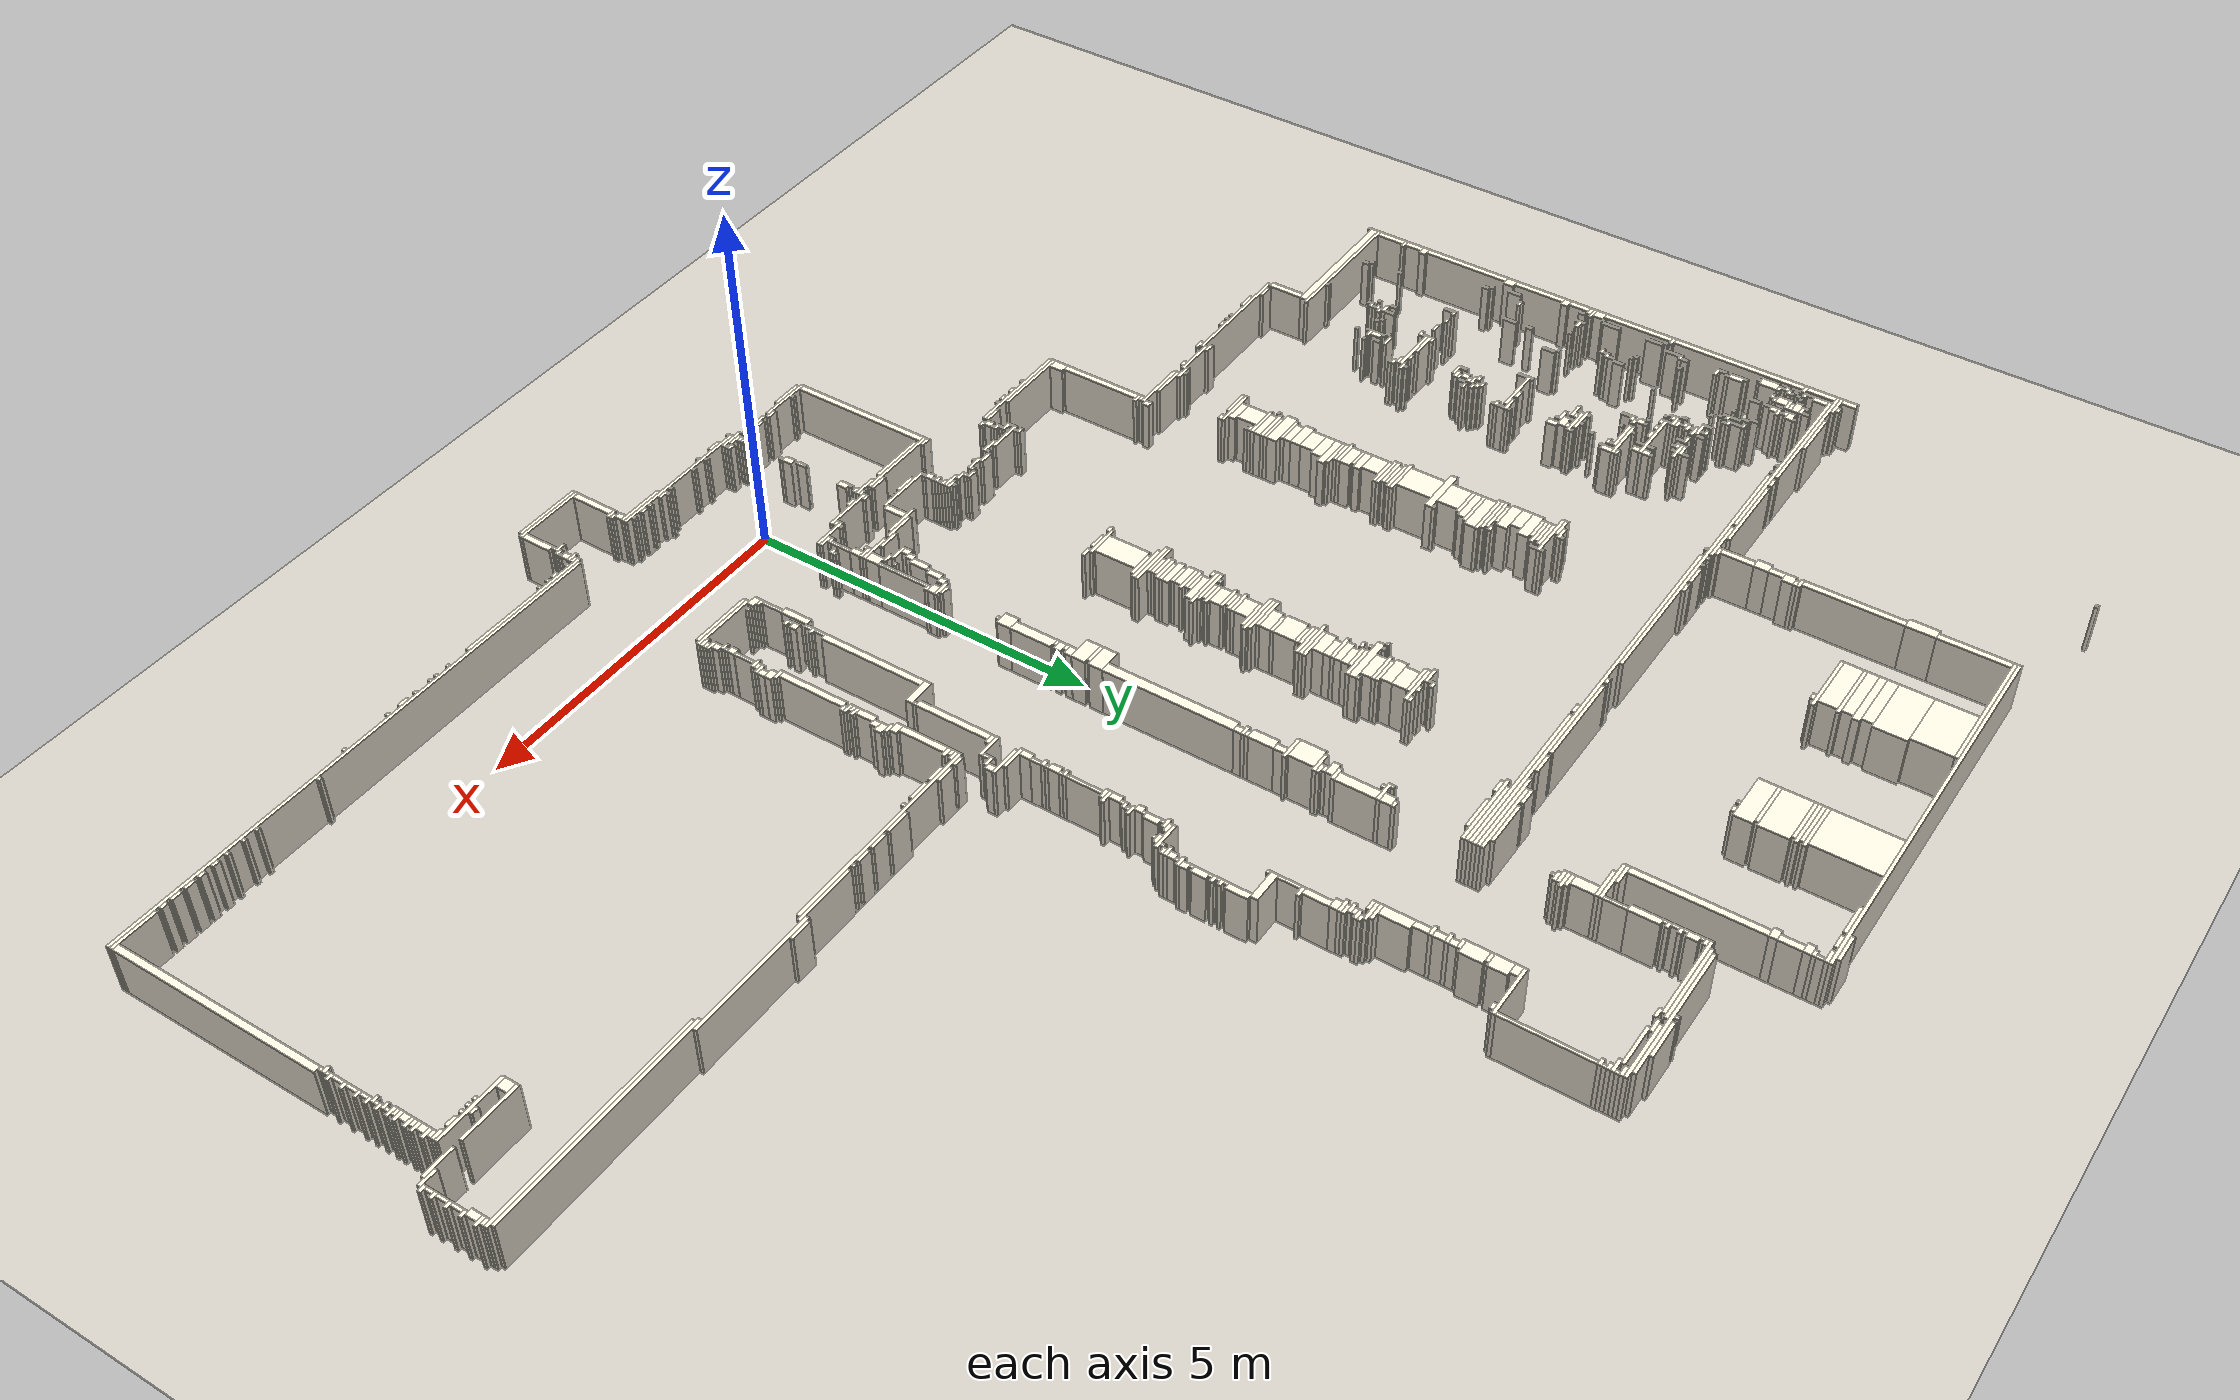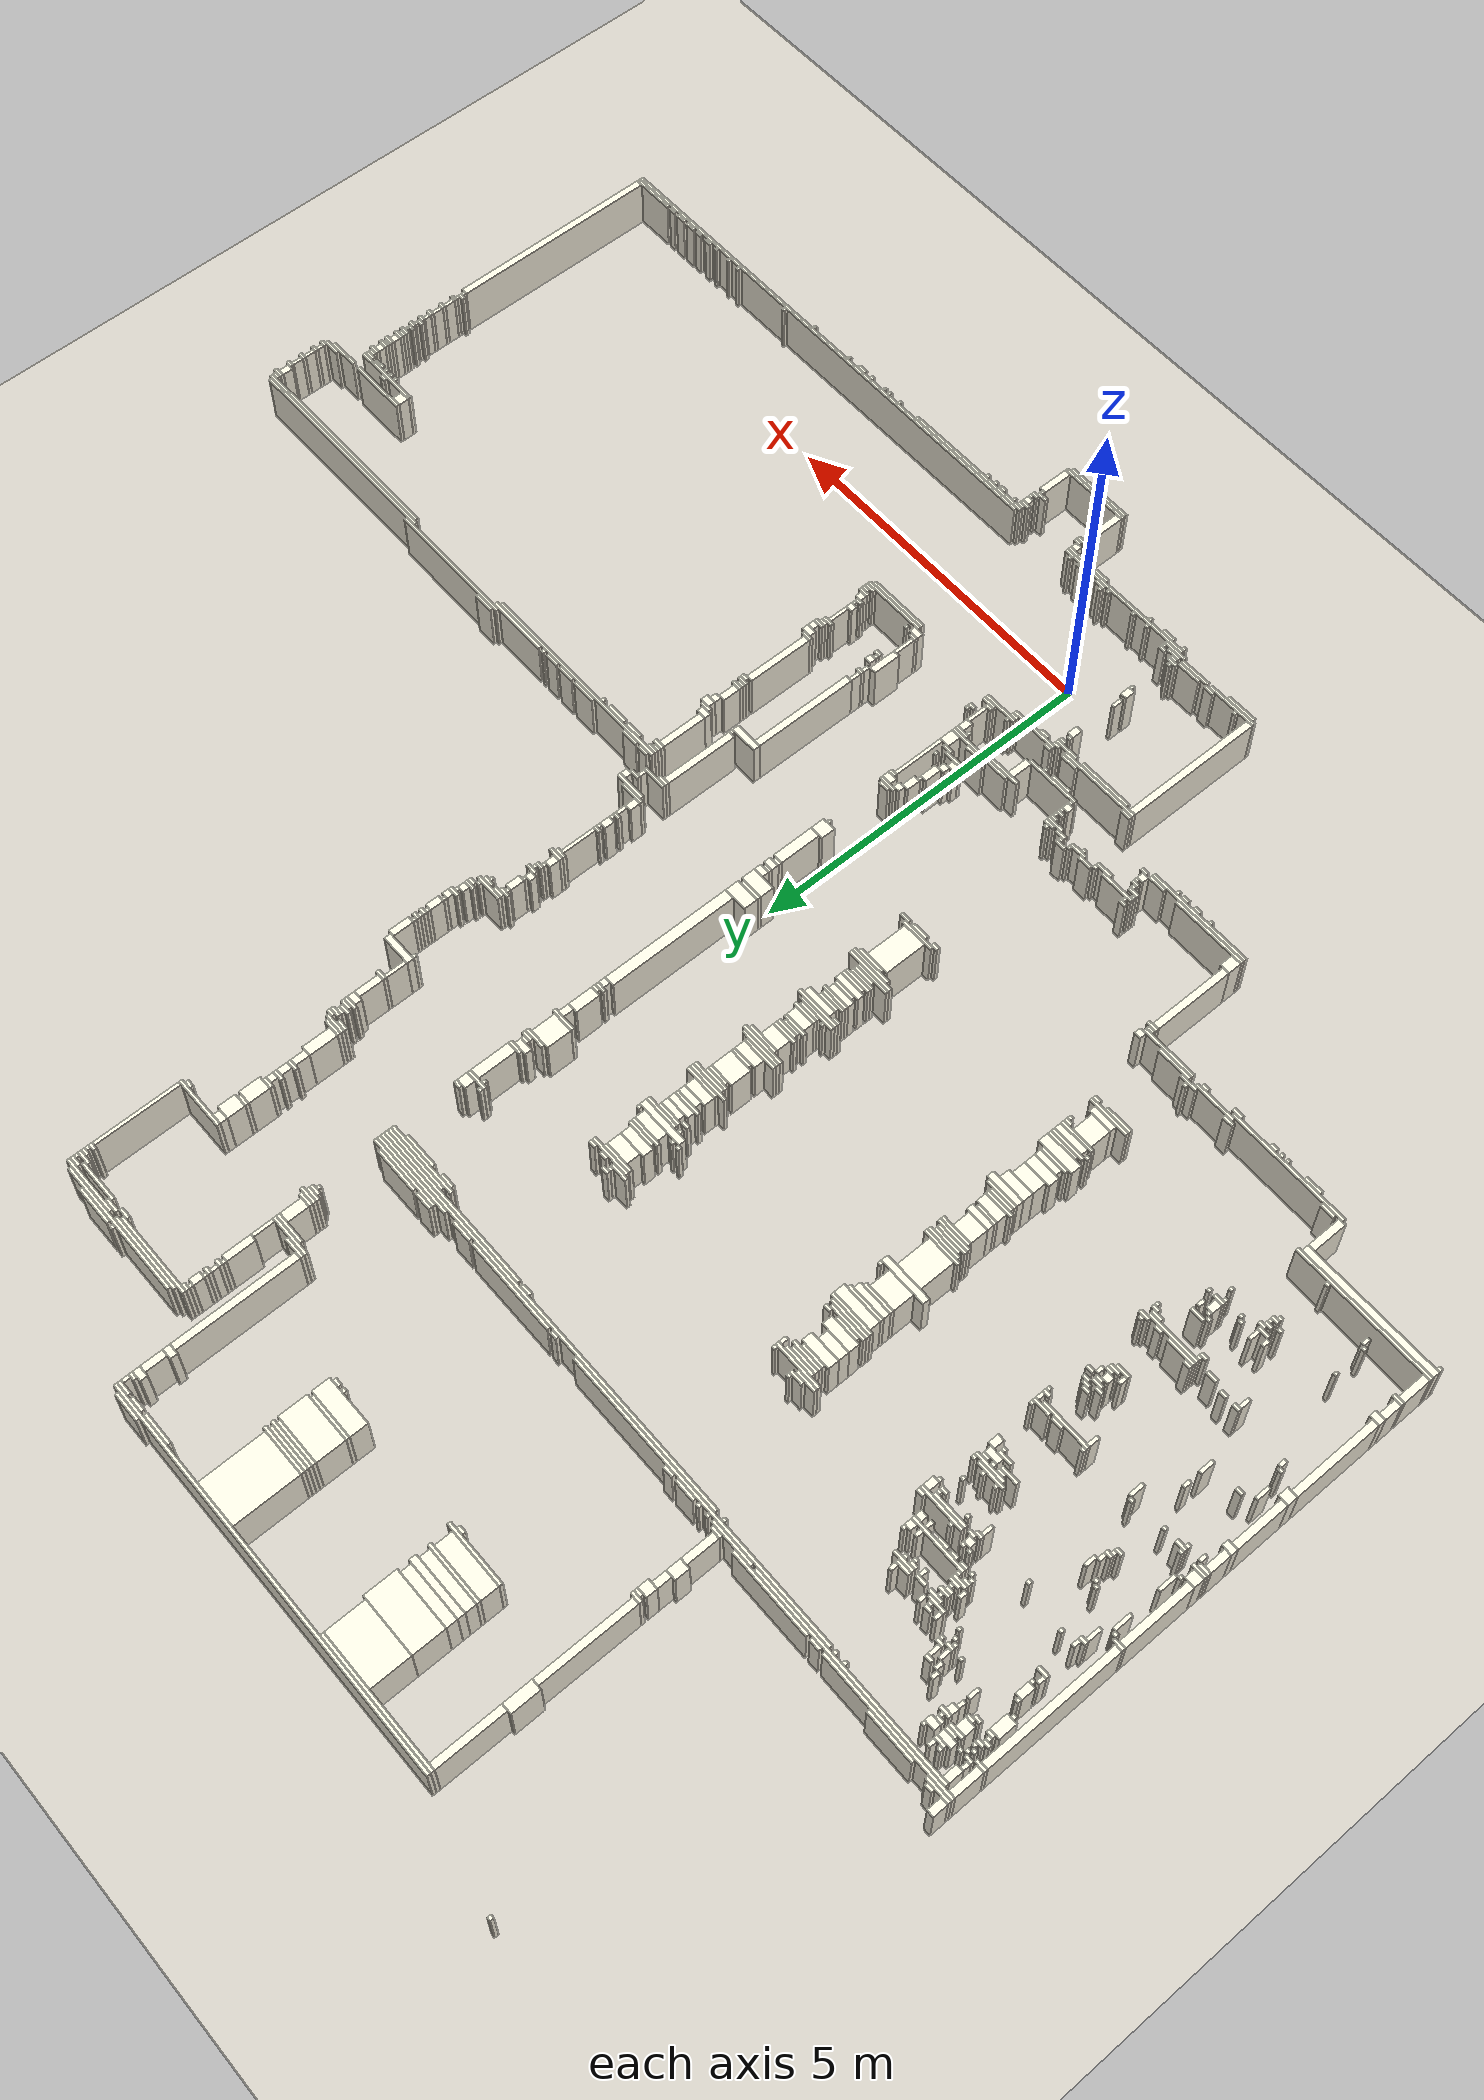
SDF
<?xml version="1.0" ?>
<sdf version="1.8">
  <world name="maps">
    <physics name="1ms" type="ignored">
      <max_step_size>0.001</max_step_size>
      <real_time_factor>1.0</real_time_factor>
    </physics>

    <plugin filename="gz-sim-physics-system" name="gz::sim::systems::Physics"/>
    <plugin filename="gz-sim-sensors-system" name="gz::sim::systems::Sensors">
      <render_engine>ogre2</render_engine>
    </plugin>
    <plugin filename="gz-sim-user-commands-system" name="gz::sim::systems::UserCommands"/>
    <plugin filename="gz-sim-scene-broadcaster-system" name="gz::sim::systems::SceneBroadcaster"/>
    <plugin filename="gz-sim-imu-system" name="gz::sim::systems::Imu"/>

    <light type="directional" name="sun">
      <cast_shadows>true</cast_shadows>
      <pose>10 10 12 0 0 0</pose>
      <diffuse>0.9 0.9 0.9 1</diffuse>
      <specular>0.6 0.6 0.6 1</specular>
      <attenuation>
        <range>1000</range>
        <constant>0.9</constant>
        <linear>0.01</linear>
        <quadratic>0.001</quadratic>
      </attenuation>
      <direction>-0.5 -0.3 -0.9</direction>
    </light>

    <model name="ground_plane">
      <static>true</static>
      <link name="link">
        <collision name="collision">
          <geometry><plane><normal>0 0 1</normal><size>100 100</size></plane></geometry>
        </collision>
        <visual name="visual">
          <geometry><plane><normal>0 0 1</normal><size>100 100</size></plane></geometry>
          <material>
            <ambient>0.78 0.76 0.72 1</ambient>
            <diffuse>0.82 0.80 0.76 1</diffuse>
          </material>
        </visual>
      </link>
    </model>

    <model name="maps_env">
      <static>true</static>
      <link name="link">
        <pose>0 0 0 0 0 0</pose>
        <collision name="wall_0000">
          <pose>-7.3600 14.9830 0.3600 0 0 0</pose>
          <geometry><box><size>0.0500 0.0500 0.7200</size></box></geometry>
        </collision>
        <visual name="wall_0000_v">
          <pose>-7.3600 14.9830 0.3600 0 0 0</pose>
          <geometry><box><size>0.0500 0.0500 0.7200</size></box></geometry>
          <material><ambient>0.96 0.93 0.85 1</ambient><diffuse>0.98 0.95 0.88 1</diffuse></material>
        </visual>
        <collision name="wall_0001">
          <pose>-0.5350 14.6330 0.3600 0 0 0</pose>
          <geometry><box><size>0.4000 0.0500 0.7200</size></box></geometry>
        </collision>
        <visual name="wall_0001_v">
          <pose>-0.5350 14.6330 0.3600 0 0 0</pose>
          <geometry><box><size>0.4000 0.0500 0.7200</size></box></geometry>
          <material><ambient>0.96 0.93 0.85 1</ambient><diffuse>0.98 0.95 0.88 1</diffuse></material>
        </visual>
        <collision name="wall_0002">
          <pose>-3.0350 14.5830 0.3600 0 0 0</pose>
          <geometry><box><size>5.6000 0.0500 0.7200</size></box></geometry>
        </collision>
        <visual name="wall_0002_v">
          <pose>-3.0350 14.5830 0.3600 0 0 0</pose>
          <geometry><box><size>5.6000 0.0500 0.7200</size></box></geometry>
          <material><ambient>0.96 0.93 0.85 1</ambient><diffuse>0.98 0.95 0.88 1</diffuse></material>
        </visual>
        <collision name="wall_0003">
          <pose>-0.9600 14.5330 0.3600 0 0 0</pose>
          <geometry><box><size>0.4500 0.0500 0.7200</size></box></geometry>
        </collision>
        <visual name="wall_0003_v">
          <pose>-0.9600 14.5330 0.3600 0 0 0</pose>
          <geometry><box><size>0.4500 0.0500 0.7200</size></box></geometry>
          <material><ambient>0.96 0.93 0.85 1</ambient><diffuse>0.98 0.95 0.88 1</diffuse></material>
        </visual>
        <collision name="wall_0004">
          <pose>-0.3350 14.5330 0.3600 0 0 0</pose>
          <geometry><box><size>0.2000 0.0500 0.7200</size></box></geometry>
        </collision>
        <visual name="wall_0004_v">
          <pose>-0.3350 14.5330 0.3600 0 0 0</pose>
          <geometry><box><size>0.2000 0.0500 0.7200</size></box></geometry>
          <material><ambient>0.96 0.93 0.85 1</ambient><diffuse>0.98 0.95 0.88 1</diffuse></material>
        </visual>
        <collision name="wall_0005">
          <pose>-0.5850 14.5330 0.3600 0 0 0</pose>
          <geometry><box><size>0.2000 0.0500 0.7200</size></box></geometry>
        </collision>
        <visual name="wall_0005_v">
          <pose>-0.5850 14.5330 0.3600 0 0 0</pose>
          <geometry><box><size>0.2000 0.0500 0.7200</size></box></geometry>
          <material><ambient>0.96 0.93 0.85 1</ambient><diffuse>0.98 0.95 0.88 1</diffuse></material>
        </visual>
        <collision name="wall_0006">
          <pose>-4.8850 14.5330 0.3600 0 0 0</pose>
          <geometry><box><size>1.9000 0.0500 0.7200</size></box></geometry>
        </collision>
        <visual name="wall_0006_v">
          <pose>-4.8850 14.5330 0.3600 0 0 0</pose>
          <geometry><box><size>1.9000 0.0500 0.7200</size></box></geometry>
          <material><ambient>0.96 0.93 0.85 1</ambient><diffuse>0.98 0.95 0.88 1</diffuse></material>
        </visual>
        <collision name="wall_0007">
          <pose>-0.2600 14.4580 0.3600 0 0 0</pose>
          <geometry><box><size>0.0500 0.1000 0.7200</size></box></geometry>
        </collision>
        <visual name="wall_0007_v">
          <pose>-0.2600 14.4580 0.3600 0 0 0</pose>
          <geometry><box><size>0.0500 0.1000 0.7200</size></box></geometry>
          <material><ambient>0.96 0.93 0.85 1</ambient><diffuse>0.98 0.95 0.88 1</diffuse></material>
        </visual>
        <collision name="wall_0008">
          <pose>-0.2850 14.3830 0.3600 0 0 0</pose>
          <geometry><box><size>0.1000 0.0500 0.7200</size></box></geometry>
        </collision>
        <visual name="wall_0008_v">
          <pose>-0.2850 14.3830 0.3600 0 0 0</pose>
          <geometry><box><size>0.1000 0.0500 0.7200</size></box></geometry>
          <material><ambient>0.96 0.93 0.85 1</ambient><diffuse>0.98 0.95 0.88 1</diffuse></material>
        </visual>
        <collision name="wall_0009">
          <pose>-0.3100 14.3080 0.3600 0 0 0</pose>
          <geometry><box><size>0.1500 0.1000 0.7200</size></box></geometry>
        </collision>
        <visual name="wall_0009_v">
          <pose>-0.3100 14.3080 0.3600 0 0 0</pose>
          <geometry><box><size>0.1500 0.1000 0.7200</size></box></geometry>
          <material><ambient>0.96 0.93 0.85 1</ambient><diffuse>0.98 0.95 0.88 1</diffuse></material>
        </visual>
        <collision name="wall_0010">
          <pose>-4.3350 14.2330 0.3600 0 0 0</pose>
          <geometry><box><size>0.8000 0.5500 0.7200</size></box></geometry>
        </collision>
        <visual name="wall_0010_v">
          <pose>-4.3350 14.2330 0.3600 0 0 0</pose>
          <geometry><box><size>0.8000 0.5500 0.7200</size></box></geometry>
          <material><ambient>0.96 0.93 0.85 1</ambient><diffuse>0.98 0.95 0.88 1</diffuse></material>
        </visual>
        <collision name="wall_0011">
          <pose>-0.2850 14.1080 0.3600 0 0 0</pose>
          <geometry><box><size>0.1000 0.3000 0.7200</size></box></geometry>
        </collision>
        <visual name="wall_0011_v">
          <pose>-0.2850 14.1080 0.3600 0 0 0</pose>
          <geometry><box><size>0.1000 0.3000 0.7200</size></box></geometry>
          <material><ambient>0.96 0.93 0.85 1</ambient><diffuse>0.98 0.95 0.88 1</diffuse></material>
        </visual>
        <collision name="wall_0012">
          <pose>-0.3100 13.9080 0.3600 0 0 0</pose>
          <geometry><box><size>0.1500 0.1000 0.7200</size></box></geometry>
        </collision>
        <visual name="wall_0012_v">
          <pose>-0.3100 13.9080 0.3600 0 0 0</pose>
          <geometry><box><size>0.1500 0.1000 0.7200</size></box></geometry>
          <material><ambient>0.96 0.93 0.85 1</ambient><diffuse>0.98 0.95 0.88 1</diffuse></material>
        </visual>
        <collision name="wall_0013">
          <pose>-2.0600 14.1080 0.3600 0 0 0</pose>
          <geometry><box><size>0.6500 0.9000 0.7200</size></box></geometry>
        </collision>
        <visual name="wall_0013_v">
          <pose>-2.0600 14.1080 0.3600 0 0 0</pose>
          <geometry><box><size>0.6500 0.9000 0.7200</size></box></geometry>
          <material><ambient>0.96 0.93 0.85 1</ambient><diffuse>0.98 0.95 0.88 1</diffuse></material>
        </visual>
        <collision name="wall_0014">
          <pose>-2.0350 13.6330 0.3600 0 0 0</pose>
          <geometry><box><size>0.7000 0.0500 0.7200</size></box></geometry>
        </collision>
        <visual name="wall_0014_v">
          <pose>-2.0350 13.6330 0.3600 0 0 0</pose>
          <geometry><box><size>0.7000 0.0500 0.7200</size></box></geometry>
          <material><ambient>0.96 0.93 0.85 1</ambient><diffuse>0.98 0.95 0.88 1</diffuse></material>
        </visual>
        <collision name="wall_0015">
          <pose>-5.7850 14.0330 0.3600 0 0 0</pose>
          <geometry><box><size>0.1000 0.9500 0.7200</size></box></geometry>
        </collision>
        <visual name="wall_0015_v">
          <pose>-5.7850 14.0330 0.3600 0 0 0</pose>
          <geometry><box><size>0.1000 0.9500 0.7200</size></box></geometry>
          <material><ambient>0.96 0.93 0.85 1</ambient><diffuse>0.98 0.95 0.88 1</diffuse></material>
        </visual>
        <collision name="wall_0016">
          <pose>-2.0600 13.5830 0.3600 0 0 0</pose>
          <geometry><box><size>0.6500 0.0500 0.7200</size></box></geometry>
        </collision>
        <visual name="wall_0016_v">
          <pose>-2.0600 13.5830 0.3600 0 0 0</pose>
          <geometry><box><size>0.6500 0.0500 0.7200</size></box></geometry>
          <material><ambient>0.96 0.93 0.85 1</ambient><diffuse>0.98 0.95 0.88 1</diffuse></material>
        </visual>
        <collision name="wall_0017">
          <pose>-4.3100 13.7330 0.3600 0 0 0</pose>
          <geometry><box><size>0.8500 0.4500 0.7200</size></box></geometry>
        </collision>
        <visual name="wall_0017_v">
          <pose>-4.3100 13.7330 0.3600 0 0 0</pose>
          <geometry><box><size>0.8500 0.4500 0.7200</size></box></geometry>
          <material><ambient>0.96 0.93 0.85 1</ambient><diffuse>0.98 0.95 0.88 1</diffuse></material>
        </visual>
        <collision name="wall_0018">
          <pose>1.6900 13.5330 0.3600 0 0 0</pose>
          <geometry><box><size>0.5500 0.0500 0.7200</size></box></geometry>
        </collision>
        <visual name="wall_0018_v">
          <pose>1.6900 13.5330 0.3600 0 0 0</pose>
          <geometry><box><size>0.5500 0.0500 0.7200</size></box></geometry>
          <material><ambient>0.96 0.93 0.85 1</ambient><diffuse>0.98 0.95 0.88 1</diffuse></material>
        </visual>
        <collision name="wall_0019">
          <pose>-2.0350 13.5330 0.3600 0 0 0</pose>
          <geometry><box><size>0.7000 0.0500 0.7200</size></box></geometry>
        </collision>
        <visual name="wall_0019_v">
          <pose>-2.0350 13.5330 0.3600 0 0 0</pose>
          <geometry><box><size>0.7000 0.0500 0.7200</size></box></geometry>
          <material><ambient>0.96 0.93 0.85 1</ambient><diffuse>0.98 0.95 0.88 1</diffuse></material>
        </visual>
        <collision name="wall_0020">
          <pose>1.3400 13.5330 0.3600 0 0 0</pose>
          <geometry><box><size>0.0500 0.0500 0.7200</size></box></geometry>
        </collision>
        <visual name="wall_0020_v">
          <pose>1.3400 13.5330 0.3600 0 0 0</pose>
          <geometry><box><size>0.0500 0.0500 0.7200</size></box></geometry>
          <material><ambient>0.96 0.93 0.85 1</ambient><diffuse>0.98 0.95 0.88 1</diffuse></material>
        </visual>
        <collision name="wall_0021">
          <pose>-2.0600 13.4830 0.3600 0 0 0</pose>
          <geometry><box><size>0.6500 0.0500 0.7200</size></box></geometry>
        </collision>
        <visual name="wall_0021_v">
          <pose>-2.0600 13.4830 0.3600 0 0 0</pose>
          <geometry><box><size>0.6500 0.0500 0.7200</size></box></geometry>
          <material><ambient>0.96 0.93 0.85 1</ambient><diffuse>0.98 0.95 0.88 1</diffuse></material>
        </visual>
        <collision name="wall_0022">
          <pose>1.2900 13.4830 0.3600 0 0 0</pose>
          <geometry><box><size>1.9500 0.0500 0.7200</size></box></geometry>
        </collision>
        <visual name="wall_0022_v">
          <pose>1.2900 13.4830 0.3600 0 0 0</pose>
          <geometry><box><size>1.9500 0.0500 0.7200</size></box></geometry>
          <material><ambient>0.96 0.93 0.85 1</ambient><diffuse>0.98 0.95 0.88 1</diffuse></material>
        </visual>
        <collision name="wall_0023">
          <pose>1.9400 13.4330 0.3600 0 0 0</pose>
          <geometry><box><size>0.8500 0.0500 0.7200</size></box></geometry>
        </collision>
        <visual name="wall_0023_v">
          <pose>1.9400 13.4330 0.3600 0 0 0</pose>
          <geometry><box><size>0.8500 0.0500 0.7200</size></box></geometry>
          <material><ambient>0.96 0.93 0.85 1</ambient><diffuse>0.98 0.95 0.88 1</diffuse></material>
        </visual>
        <collision name="wall_0024">
          <pose>0.8400 13.4330 0.3600 0 0 0</pose>
          <geometry><box><size>1.1500 0.0500 0.7200</size></box></geometry>
        </collision>
        <visual name="wall_0024_v">
          <pose>0.8400 13.4330 0.3600 0 0 0</pose>
          <geometry><box><size>1.1500 0.0500 0.7200</size></box></geometry>
          <material><ambient>0.96 0.93 0.85 1</ambient><diffuse>0.98 0.95 0.88 1</diffuse></material>
        </visual>
        <collision name="wall_0025">
          <pose>-4.3350 13.4330 0.3600 0 0 0</pose>
          <geometry><box><size>0.8000 0.1500 0.7200</size></box></geometry>
        </collision>
        <visual name="wall_0025_v">
          <pose>-4.3350 13.4330 0.3600 0 0 0</pose>
          <geometry><box><size>0.8000 0.1500 0.7200</size></box></geometry>
          <material><ambient>0.96 0.93 0.85 1</ambient><diffuse>0.98 0.95 0.88 1</diffuse></material>
        </visual>
        <collision name="wall_0026">
          <pose>1.5650 13.3830 0.3600 0 0 0</pose>
          <geometry><box><size>0.2000 0.0500 0.7200</size></box></geometry>
        </collision>
        <visual name="wall_0026_v">
          <pose>1.5650 13.3830 0.3600 0 0 0</pose>
          <geometry><box><size>0.2000 0.0500 0.7200</size></box></geometry>
          <material><ambient>0.96 0.93 0.85 1</ambient><diffuse>0.98 0.95 0.88 1</diffuse></material>
        </visual>
        <collision name="wall_0027">
          <pose>0.7650 13.3830 0.3600 0 0 0</pose>
          <geometry><box><size>1.2000 0.0500 0.7200</size></box></geometry>
        </collision>
        <visual name="wall_0027_v">
          <pose>0.7650 13.3830 0.3600 0 0 0</pose>
          <geometry><box><size>1.2000 0.0500 0.7200</size></box></geometry>
          <material><ambient>0.96 0.93 0.85 1</ambient><diffuse>0.98 0.95 0.88 1</diffuse></material>
        </visual>
        <collision name="wall_0028">
          <pose>2.2900 13.3830 0.3600 0 0 0</pose>
          <geometry><box><size>0.1500 0.0500 0.7200</size></box></geometry>
        </collision>
        <visual name="wall_0028_v">
          <pose>2.2900 13.3830 0.3600 0 0 0</pose>
          <geometry><box><size>0.1500 0.0500 0.7200</size></box></geometry>
          <material><ambient>0.96 0.93 0.85 1</ambient><diffuse>0.98 0.95 0.88 1</diffuse></material>
        </visual>
        <collision name="wall_0029">
          <pose>0.2150 13.3330 0.3600 0 0 0</pose>
          <geometry><box><size>0.1000 0.0500 0.7200</size></box></geometry>
        </collision>
        <visual name="wall_0029_v">
          <pose>0.2150 13.3330 0.3600 0 0 0</pose>
          <geometry><box><size>0.1000 0.0500 0.7200</size></box></geometry>
          <material><ambient>0.96 0.93 0.85 1</ambient><diffuse>0.98 0.95 0.88 1</diffuse></material>
        </visual>
        <collision name="wall_0030">
          <pose>1.3900 13.3330 0.3600 0 0 0</pose>
          <geometry><box><size>0.1500 0.0500 0.7200</size></box></geometry>
        </collision>
        <visual name="wall_0030_v">
          <pose>1.3900 13.3330 0.3600 0 0 0</pose>
          <geometry><box><size>0.1500 0.0500 0.7200</size></box></geometry>
          <material><ambient>0.96 0.93 0.85 1</ambient><diffuse>0.98 0.95 0.88 1</diffuse></material>
        </visual>
        <collision name="wall_0031">
          <pose>2.3400 13.3330 0.3600 0 0 0</pose>
          <geometry><box><size>0.0500 0.0500 0.7200</size></box></geometry>
        </collision>
        <visual name="wall_0031_v">
          <pose>2.3400 13.3330 0.3600 0 0 0</pose>
          <geometry><box><size>0.0500 0.0500 0.7200</size></box></geometry>
          <material><ambient>0.96 0.93 0.85 1</ambient><diffuse>0.98 0.95 0.88 1</diffuse></material>
        </visual>
        <collision name="wall_0032">
          <pose>1.9150 13.3330 0.3600 0 0 0</pose>
          <geometry><box><size>0.6000 0.0500 0.7200</size></box></geometry>
        </collision>
        <visual name="wall_0032_v">
          <pose>1.9150 13.3330 0.3600 0 0 0</pose>
          <geometry><box><size>0.6000 0.0500 0.7200</size></box></geometry>
          <material><ambient>0.96 0.93 0.85 1</ambient><diffuse>0.98 0.95 0.88 1</diffuse></material>
        </visual>
        <collision name="wall_0033">
          <pose>-4.3100 13.3080 0.3600 0 0 0</pose>
          <geometry><box><size>0.8500 0.1000 0.7200</size></box></geometry>
        </collision>
        <visual name="wall_0033_v">
          <pose>-4.3100 13.3080 0.3600 0 0 0</pose>
          <geometry><box><size>0.8500 0.1000 0.7200</size></box></geometry>
          <material><ambient>0.96 0.93 0.85 1</ambient><diffuse>0.98 0.95 0.88 1</diffuse></material>
        </visual>
        <collision name="wall_0034">
          <pose>0.1900 13.2830 0.3600 0 0 0</pose>
          <geometry><box><size>0.0500 0.0500 0.7200</size></box></geometry>
        </collision>
        <visual name="wall_0034_v">
          <pose>0.1900 13.2830 0.3600 0 0 0</pose>
          <geometry><box><size>0.0500 0.0500 0.7200</size></box></geometry>
          <material><ambient>0.96 0.93 0.85 1</ambient><diffuse>0.98 0.95 0.88 1</diffuse></material>
        </visual>
        <collision name="wall_0035">
          <pose>2.2650 13.2830 0.3600 0 0 0</pose>
          <geometry><box><size>0.2000 0.0500 0.7200</size></box></geometry>
        </collision>
        <visual name="wall_0035_v">
          <pose>2.2650 13.2830 0.3600 0 0 0</pose>
          <geometry><box><size>0.2000 0.0500 0.7200</size></box></geometry>
          <material><ambient>0.96 0.93 0.85 1</ambient><diffuse>0.98 0.95 0.88 1</diffuse></material>
        </visual>
        <collision name="wall_0036">
          <pose>2.3150 13.2330 0.3600 0 0 0</pose>
          <geometry><box><size>0.1000 0.0500 0.7200</size></box></geometry>
        </collision>
        <visual name="wall_0036_v">
          <pose>2.3150 13.2330 0.3600 0 0 0</pose>
          <geometry><box><size>0.1000 0.0500 0.7200</size></box></geometry>
          <material><ambient>0.96 0.93 0.85 1</ambient><diffuse>0.98 0.95 0.88 1</diffuse></material>
        </visual>
        <collision name="wall_0037">
          <pose>-5.8100 13.3580 0.3600 0 0 0</pose>
          <geometry><box><size>0.1500 0.4000 0.7200</size></box></geometry>
        </collision>
        <visual name="wall_0037_v">
          <pose>-5.8100 13.3580 0.3600 0 0 0</pose>
          <geometry><box><size>0.1500 0.4000 0.7200</size></box></geometry>
          <material><ambient>0.96 0.93 0.85 1</ambient><diffuse>0.98 0.95 0.88 1</diffuse></material>
        </visual>
        <collision name="wall_0038">
          <pose>2.3400 13.1830 0.3600 0 0 0</pose>
          <geometry><box><size>0.0500 0.0500 0.7200</size></box></geometry>
        </collision>
        <visual name="wall_0038_v">
          <pose>2.3400 13.1830 0.3600 0 0 0</pose>
          <geometry><box><size>0.0500 0.0500 0.7200</size></box></geometry>
          <material><ambient>0.96 0.93 0.85 1</ambient><diffuse>0.98 0.95 0.88 1</diffuse></material>
        </visual>
        <collision name="wall_0039">
          <pose>0.2150 13.1830 0.3600 0 0 0</pose>
          <geometry><box><size>0.1000 0.1500 0.7200</size></box></geometry>
        </collision>
        <visual name="wall_0039_v">
          <pose>0.2150 13.1830 0.3600 0 0 0</pose>
          <geometry><box><size>0.1000 0.1500 0.7200</size></box></geometry>
          <material><ambient>0.96 0.93 0.85 1</ambient><diffuse>0.98 0.95 0.88 1</diffuse></material>
        </visual>
        <collision name="wall_0040">
          <pose>-4.3350 13.1830 0.3600 0 0 0</pose>
          <geometry><box><size>0.8000 0.1500 0.7200</size></box></geometry>
        </collision>
        <visual name="wall_0040_v">
          <pose>-4.3350 13.1830 0.3600 0 0 0</pose>
          <geometry><box><size>0.8000 0.1500 0.7200</size></box></geometry>
          <material><ambient>0.96 0.93 0.85 1</ambient><diffuse>0.98 0.95 0.88 1</diffuse></material>
        </visual>
        <collision name="wall_0041">
          <pose>2.3150 13.1330 0.3600 0 0 0</pose>
          <geometry><box><size>0.1000 0.0500 0.7200</size></box></geometry>
        </collision>
        <visual name="wall_0041_v">
          <pose>2.3150 13.1330 0.3600 0 0 0</pose>
          <geometry><box><size>0.1000 0.0500 0.7200</size></box></geometry>
          <material><ambient>0.96 0.93 0.85 1</ambient><diffuse>0.98 0.95 0.88 1</diffuse></material>
        </visual>
        <collision name="wall_0042">
          <pose>-2.0350 13.2580 0.3600 0 0 0</pose>
          <geometry><box><size>0.7000 0.4000 0.7200</size></box></geometry>
        </collision>
        <visual name="wall_0042_v">
          <pose>-2.0350 13.2580 0.3600 0 0 0</pose>
          <geometry><box><size>0.7000 0.4000 0.7200</size></box></geometry>
          <material><ambient>0.96 0.93 0.85 1</ambient><diffuse>0.98 0.95 0.88 1</diffuse></material>
        </visual>
        <collision name="wall_0043">
          <pose>0.1900 13.0830 0.3600 0 0 0</pose>
          <geometry><box><size>0.0500 0.0500 0.7200</size></box></geometry>
        </collision>
        <visual name="wall_0043_v">
          <pose>0.1900 13.0830 0.3600 0 0 0</pose>
          <geometry><box><size>0.0500 0.0500 0.7200</size></box></geometry>
          <material><ambient>0.96 0.93 0.85 1</ambient><diffuse>0.98 0.95 0.88 1</diffuse></material>
        </visual>
        <collision name="wall_0044">
          <pose>-4.3100 13.0830 0.3600 0 0 0</pose>
          <geometry><box><size>0.8500 0.0500 0.7200</size></box></geometry>
        </collision>
        <visual name="wall_0044_v">
          <pose>-4.3100 13.0830 0.3600 0 0 0</pose>
          <geometry><box><size>0.8500 0.0500 0.7200</size></box></geometry>
          <material><ambient>0.96 0.93 0.85 1</ambient><diffuse>0.98 0.95 0.88 1</diffuse></material>
        </visual>
        <collision name="wall_0045">
          <pose>0.2150 13.0330 0.3600 0 0 0</pose>
          <geometry><box><size>0.1000 0.0500 0.7200</size></box></geometry>
        </collision>
        <visual name="wall_0045_v">
          <pose>0.2150 13.0330 0.3600 0 0 0</pose>
          <geometry><box><size>0.1000 0.0500 0.7200</size></box></geometry>
          <material><ambient>0.96 0.93 0.85 1</ambient><diffuse>0.98 0.95 0.88 1</diffuse></material>
        </visual>
        <collision name="wall_0046">
          <pose>-2.0600 13.0330 0.3600 0 0 0</pose>
          <geometry><box><size>0.6500 0.0500 0.7200</size></box></geometry>
        </collision>
        <visual name="wall_0046_v">
          <pose>-2.0600 13.0330 0.3600 0 0 0</pose>
          <geometry><box><size>0.6500 0.0500 0.7200</size></box></geometry>
          <material><ambient>0.96 0.93 0.85 1</ambient><diffuse>0.98 0.95 0.88 1</diffuse></material>
        </visual>
        <collision name="wall_0047">
          <pose>0.1900 12.9580 0.3600 0 0 0</pose>
          <geometry><box><size>0.0500 0.1000 0.7200</size></box></geometry>
        </collision>
        <visual name="wall_0047_v">
          <pose>0.1900 12.9580 0.3600 0 0 0</pose>
          <geometry><box><size>0.0500 0.1000 0.7200</size></box></geometry>
          <material><ambient>0.96 0.93 0.85 1</ambient><diffuse>0.98 0.95 0.88 1</diffuse></material>
        </visual>
        <collision name="wall_0048">
          <pose>0.2150 12.8830 0.3600 0 0 0</pose>
          <geometry><box><size>0.1000 0.0500 0.7200</size></box></geometry>
        </collision>
        <visual name="wall_0048_v">
          <pose>0.2150 12.8830 0.3600 0 0 0</pose>
          <geometry><box><size>0.1000 0.0500 0.7200</size></box></geometry>
          <material><ambient>0.96 0.93 0.85 1</ambient><diffuse>0.98 0.95 0.88 1</diffuse></material>
        </visual>
        <collision name="wall_0049">
          <pose>-4.3350 12.9330 0.3600 0 0 0</pose>
          <geometry><box><size>0.8000 0.2500 0.7200</size></box></geometry>
        </collision>
        <visual name="wall_0049_v">
          <pose>-4.3350 12.9330 0.3600 0 0 0</pose>
          <geometry><box><size>0.8000 0.2500 0.7200</size></box></geometry>
          <material><ambient>0.96 0.93 0.85 1</ambient><diffuse>0.98 0.95 0.88 1</diffuse></material>
        </visual>
        <collision name="wall_0050">
          <pose>0.1900 12.8330 0.3600 0 0 0</pose>
          <geometry><box><size>0.0500 0.0500 0.7200</size></box></geometry>
        </collision>
        <visual name="wall_0050_v">
          <pose>0.1900 12.8330 0.3600 0 0 0</pose>
          <geometry><box><size>0.0500 0.0500 0.7200</size></box></geometry>
          <material><ambient>0.96 0.93 0.85 1</ambient><diffuse>0.98 0.95 0.88 1</diffuse></material>
        </visual>
        <collision name="wall_0051">
          <pose>-2.0350 12.8830 0.3600 0 0 0</pose>
          <geometry><box><size>0.7000 0.2500 0.7200</size></box></geometry>
        </collision>
        <visual name="wall_0051_v">
          <pose>-2.0350 12.8830 0.3600 0 0 0</pose>
          <geometry><box><size>0.7000 0.2500 0.7200</size></box></geometry>
          <material><ambient>0.96 0.93 0.85 1</ambient><diffuse>0.98 0.95 0.88 1</diffuse></material>
        </visual>
        <collision name="wall_0052">
          <pose>-4.2850 12.7830 0.3600 0 0 0</pose>
          <geometry><box><size>0.9000 0.0500 0.7200</size></box></geometry>
        </collision>
        <visual name="wall_0052_v">
          <pose>-4.2850 12.7830 0.3600 0 0 0</pose>
          <geometry><box><size>0.9000 0.0500 0.7200</size></box></geometry>
          <material><ambient>0.96 0.93 0.85 1</ambient><diffuse>0.98 0.95 0.88 1</diffuse></material>
        </visual>
        <collision name="wall_0053">
          <pose>-1.9100 12.7330 0.3600 0 0 0</pose>
          <geometry><box><size>0.0500 0.0500 0.7200</size></box></geometry>
        </collision>
        <visual name="wall_0053_v">
          <pose>-1.9100 12.7330 0.3600 0 0 0</pose>
          <geometry><box><size>0.0500 0.0500 0.7200</size></box></geometry>
          <material><ambient>0.96 0.93 0.85 1</ambient><diffuse>0.98 0.95 0.88 1</diffuse></material>
        </visual>
        <collision name="wall_0054">
          <pose>-3.9850 12.7330 0.3600 0 0 0</pose>
          <geometry><box><size>0.1000 0.0500 0.7200</size></box></geometry>
        </collision>
        <visual name="wall_0054_v">
          <pose>-3.9850 12.7330 0.3600 0 0 0</pose>
          <geometry><box><size>0.1000 0.0500 0.7200</size></box></geometry>
          <material><ambient>0.96 0.93 0.85 1</ambient><diffuse>0.98 0.95 0.88 1</diffuse></material>
        </visual>
        <collision name="wall_0055">
          <pose>-1.7850 12.7330 0.3600 0 0 0</pose>
          <geometry><box><size>0.1000 0.0500 0.7200</size></box></geometry>
        </collision>
        <visual name="wall_0055_v">
          <pose>-1.7850 12.7330 0.3600 0 0 0</pose>
          <geometry><box><size>0.1000 0.0500 0.7200</size></box></geometry>
          <material><ambient>0.96 0.93 0.85 1</ambient><diffuse>0.98 0.95 0.88 1</diffuse></material>
        </visual>
        <collision name="wall_0056">
          <pose>0.2150 12.6080 0.3600 0 0 0</pose>
          <geometry><box><size>0.1000 0.4000 0.7200</size></box></geometry>
        </collision>
        <visual name="wall_0056_v">
          <pose>0.2150 12.6080 0.3600 0 0 0</pose>
          <geometry><box><size>0.1000 0.4000 0.7200</size></box></geometry>
          <material><ambient>0.96 0.93 0.85 1</ambient><diffuse>0.98 0.95 0.88 1</diffuse></material>
        </visual>
        <collision name="wall_0057">
          <pose>-0.2850 13.0080 0.3600 0 0 0</pose>
          <geometry><box><size>0.1000 1.7000 0.7200</size></box></geometry>
        </collision>
        <visual name="wall_0057_v">
          <pose>-0.2850 13.0080 0.3600 0 0 0</pose>
          <geometry><box><size>0.1000 1.7000 0.7200</size></box></geometry>
          <material><ambient>0.96 0.93 0.85 1</ambient><diffuse>0.98 0.95 0.88 1</diffuse></material>
        </visual>
        <collision name="wall_0058">
          <pose>0.2400 12.2580 0.3600 0 0 0</pose>
          <geometry><box><size>0.0500 0.3000 0.7200</size></box></geometry>
        </collision>
        <visual name="wall_0058_v">
          <pose>0.2400 12.2580 0.3600 0 0 0</pose>
          <geometry><box><size>0.0500 0.3000 0.7200</size></box></geometry>
          <material><ambient>0.96 0.93 0.85 1</ambient><diffuse>0.98 0.95 0.88 1</diffuse></material>
        </visual>
        <collision name="wall_0059">
          <pose>-0.1850 12.1330 0.3600 0 0 0</pose>
          <geometry><box><size>0.3000 0.0500 0.7200</size></box></geometry>
        </collision>
        <visual name="wall_0059_v">
          <pose>-0.1850 12.1330 0.3600 0 0 0</pose>
          <geometry><box><size>0.3000 0.0500 0.7200</size></box></geometry>
          <material><ambient>0.96 0.93 0.85 1</ambient><diffuse>0.98 0.95 0.88 1</diffuse></material>
        </visual>
        <collision name="wall_0060">
          <pose>-0.0350 12.0830 0.3600 0 0 0</pose>
          <geometry><box><size>0.6000 0.0500 0.7200</size></box></geometry>
        </collision>
        <visual name="wall_0060_v">
          <pose>-0.0350 12.0830 0.3600 0 0 0</pose>
          <geometry><box><size>0.6000 0.0500 0.7200</size></box></geometry>
          <material><ambient>0.96 0.93 0.85 1</ambient><diffuse>0.98 0.95 0.88 1</diffuse></material>
        </visual>
        <collision name="wall_0061">
          <pose>0.0400 12.0330 0.3600 0 0 0</pose>
          <geometry><box><size>0.4500 0.0500 0.7200</size></box></geometry>
        </collision>
        <visual name="wall_0061_v">
          <pose>0.0400 12.0330 0.3600 0 0 0</pose>
          <geometry><box><size>0.4500 0.0500 0.7200</size></box></geometry>
          <material><ambient>0.96 0.93 0.85 1</ambient><diffuse>0.98 0.95 0.88 1</diffuse></material>
        </visual>
        <collision name="wall_0062">
          <pose>2.3400 12.5080 0.3600 0 0 0</pose>
          <geometry><box><size>0.0500 1.2000 0.7200</size></box></geometry>
        </collision>
        <visual name="wall_0062_v">
          <pose>2.3400 12.5080 0.3600 0 0 0</pose>
          <geometry><box><size>0.0500 1.2000 0.7200</size></box></geometry>
          <material><ambient>0.96 0.93 0.85 1</ambient><diffuse>0.98 0.95 0.88 1</diffuse></material>
        </visual>
        <collision name="wall_0063">
          <pose>1.9900 11.8830 0.3600 0 0 0</pose>
          <geometry><box><size>0.7500 0.0500 0.7200</size></box></geometry>
        </collision>
        <visual name="wall_0063_v">
          <pose>1.9900 11.8830 0.3600 0 0 0</pose>
          <geometry><box><size>0.7500 0.0500 0.7200</size></box></geometry>
          <material><ambient>0.96 0.93 0.85 1</ambient><diffuse>0.98 0.95 0.88 1</diffuse></material>
        </visual>
        <collision name="wall_0064">
          <pose>-5.7850 12.4830 0.3600 0 0 0</pose>
          <geometry><box><size>0.1000 1.3500 0.7200</size></box></geometry>
        </collision>
        <visual name="wall_0064_v">
          <pose>-5.7850 12.4830 0.3600 0 0 0</pose>
          <geometry><box><size>0.1000 1.3500 0.7200</size></box></geometry>
          <material><ambient>0.96 0.93 0.85 1</ambient><diffuse>0.98 0.95 0.88 1</diffuse></material>
        </visual>
        <collision name="wall_0065">
          <pose>2.2650 11.8330 0.3600 0 0 0</pose>
          <geometry><box><size>0.1000 0.0500 0.7200</size></box></geometry>
        </collision>
        <visual name="wall_0065_v">
          <pose>2.2650 11.8330 0.3600 0 0 0</pose>
          <geometry><box><size>0.1000 0.0500 0.7200</size></box></geometry>
          <material><ambient>0.96 0.93 0.85 1</ambient><diffuse>0.98 0.95 0.88 1</diffuse></material>
        </visual>
        <collision name="wall_0066">
          <pose>1.6900 11.8080 0.3600 0 0 0</pose>
          <geometry><box><size>0.1500 0.1000 0.7200</size></box></geometry>
        </collision>
        <visual name="wall_0066_v">
          <pose>1.6900 11.8080 0.3600 0 0 0</pose>
          <geometry><box><size>0.1500 0.1000 0.7200</size></box></geometry>
          <material><ambient>0.96 0.93 0.85 1</ambient><diffuse>0.98 0.95 0.88 1</diffuse></material>
        </visual>
        <collision name="wall_0067">
          <pose>-5.7600 11.7830 0.3600 0 0 0</pose>
          <geometry><box><size>0.1500 0.0500 0.7200</size></box></geometry>
        </collision>
        <visual name="wall_0067_v">
          <pose>-5.7600 11.7830 0.3600 0 0 0</pose>
          <geometry><box><size>0.1500 0.0500 0.7200</size></box></geometry>
          <material><ambient>0.96 0.93 0.85 1</ambient><diffuse>0.98 0.95 0.88 1</diffuse></material>
        </visual>
        <collision name="wall_0068">
          <pose>0.1900 11.8580 0.3600 0 0 0</pose>
          <geometry><box><size>0.1500 0.3000 0.7200</size></box></geometry>
        </collision>
        <visual name="wall_0068_v">
          <pose>0.1900 11.8580 0.3600 0 0 0</pose>
          <geometry><box><size>0.1500 0.3000 0.7200</size></box></geometry>
          <material><ambient>0.96 0.93 0.85 1</ambient><diffuse>0.98 0.95 0.88 1</diffuse></material>
        </visual>
        <collision name="wall_0069">
          <pose>-5.7350 11.7330 0.3600 0 0 0</pose>
          <geometry><box><size>0.1000 0.0500 0.7200</size></box></geometry>
        </collision>
        <visual name="wall_0069_v">
          <pose>-5.7350 11.7330 0.3600 0 0 0</pose>
          <geometry><box><size>0.1000 0.0500 0.7200</size></box></geometry>
          <material><ambient>0.96 0.93 0.85 1</ambient><diffuse>0.98 0.95 0.88 1</diffuse></material>
        </visual>
        <collision name="wall_0070">
          <pose>0.2150 11.6830 0.3600 0 0 0</pose>
          <geometry><box><size>0.2000 0.0500 0.7200</size></box></geometry>
        </collision>
        <visual name="wall_0070_v">
          <pose>0.2150 11.6830 0.3600 0 0 0</pose>
          <geometry><box><size>0.2000 0.0500 0.7200</size></box></geometry>
          <material><ambient>0.96 0.93 0.85 1</ambient><diffuse>0.98 0.95 0.88 1</diffuse></material>
        </visual>
        <collision name="wall_0071">
          <pose>0.2400 11.6330 0.3600 0 0 0</pose>
          <geometry><box><size>0.2500 0.0500 0.7200</size></box></geometry>
        </collision>
        <visual name="wall_0071_v">
          <pose>0.2400 11.6330 0.3600 0 0 0</pose>
          <geometry><box><size>0.2500 0.0500 0.7200</size></box></geometry>
          <material><ambient>0.96 0.93 0.85 1</ambient><diffuse>0.98 0.95 0.88 1</diffuse></material>
        </visual>
        <collision name="wall_0072">
          <pose>-5.7600 11.6330 0.3600 0 0 0</pose>
          <geometry><box><size>0.1500 0.1500 0.7200</size></box></geometry>
        </collision>
        <visual name="wall_0072_v">
          <pose>-5.7600 11.6330 0.3600 0 0 0</pose>
          <geometry><box><size>0.1500 0.1500 0.7200</size></box></geometry>
          <material><ambient>0.96 0.93 0.85 1</ambient><diffuse>0.98 0.95 0.88 1</diffuse></material>
        </visual>
        <collision name="wall_0073">
          <pose>0.2150 11.5830 0.3600 0 0 0</pose>
          <geometry><box><size>0.2000 0.0500 0.7200</size></box></geometry>
        </collision>
        <visual name="wall_0073_v">
          <pose>0.2150 11.5830 0.3600 0 0 0</pose>
          <geometry><box><size>0.2000 0.0500 0.7200</size></box></geometry>
          <material><ambient>0.96 0.93 0.85 1</ambient><diffuse>0.98 0.95 0.88 1</diffuse></material>
        </visual>
        <collision name="wall_0074">
          <pose>1.7150 11.6330 0.3600 0 0 0</pose>
          <geometry><box><size>0.2000 0.2500 0.7200</size></box></geometry>
        </collision>
        <visual name="wall_0074_v">
          <pose>1.7150 11.6330 0.3600 0 0 0</pose>
          <geometry><box><size>0.2000 0.2500 0.7200</size></box></geometry>
          <material><ambient>0.96 0.93 0.85 1</ambient><diffuse>0.98 0.95 0.88 1</diffuse></material>
        </visual>
        <collision name="wall_0075">
          <pose>0.2400 11.5330 0.3600 0 0 0</pose>
          <geometry><box><size>0.1500 0.0500 0.7200</size></box></geometry>
        </collision>
        <visual name="wall_0075_v">
          <pose>0.2400 11.5330 0.3600 0 0 0</pose>
          <geometry><box><size>0.1500 0.0500 0.7200</size></box></geometry>
          <material><ambient>0.96 0.93 0.85 1</ambient><diffuse>0.98 0.95 0.88 1</diffuse></material>
        </visual>
        <collision name="wall_0076">
          <pose>1.6900 11.4830 0.3600 0 0 0</pose>
          <geometry><box><size>0.1500 0.0500 0.7200</size></box></geometry>
        </collision>
        <visual name="wall_0076_v">
          <pose>1.6900 11.4830 0.3600 0 0 0</pose>
          <geometry><box><size>0.1500 0.0500 0.7200</size></box></geometry>
          <material><ambient>0.96 0.93 0.85 1</ambient><diffuse>0.98 0.95 0.88 1</diffuse></material>
        </visual>
        <collision name="wall_0077">
          <pose>0.2400 11.4830 0.3600 0 0 0</pose>
          <geometry><box><size>0.0500 0.0500 0.7200</size></box></geometry>
        </collision>
        <visual name="wall_0077_v">
          <pose>0.2400 11.4830 0.3600 0 0 0</pose>
          <geometry><box><size>0.0500 0.0500 0.7200</size></box></geometry>
          <material><ambient>0.96 0.93 0.85 1</ambient><diffuse>0.98 0.95 0.88 1</diffuse></material>
        </visual>
        <collision name="wall_0078">
          <pose>-5.7850 11.4580 0.3600 0 0 0</pose>
          <geometry><box><size>0.1000 0.2000 0.7200</size></box></geometry>
        </collision>
        <visual name="wall_0078_v">
          <pose>-5.7850 11.4580 0.3600 0 0 0</pose>
          <geometry><box><size>0.1000 0.2000 0.7200</size></box></geometry>
          <material><ambient>0.96 0.93 0.85 1</ambient><diffuse>0.98 0.95 0.88 1</diffuse></material>
        </visual>
        <collision name="wall_0079">
          <pose>1.7150 11.3080 0.3600 0 0 0</pose>
          <geometry><box><size>0.2000 0.3000 0.7200</size></box></geometry>
        </collision>
        <visual name="wall_0079_v">
          <pose>1.7150 11.3080 0.3600 0 0 0</pose>
          <geometry><box><size>0.2000 0.3000 0.7200</size></box></geometry>
          <material><ambient>0.96 0.93 0.85 1</ambient><diffuse>0.98 0.95 0.88 1</diffuse></material>
        </visual>
        <collision name="wall_0080">
          <pose>-5.8100 11.2580 0.3600 0 0 0</pose>
          <geometry><box><size>0.1500 0.2000 0.7200</size></box></geometry>
        </collision>
        <visual name="wall_0080_v">
          <pose>-5.8100 11.2580 0.3600 0 0 0</pose>
          <geometry><box><size>0.1500 0.2000 0.7200</size></box></geometry>
          <material><ambient>0.96 0.93 0.85 1</ambient><diffuse>0.98 0.95 0.88 1</diffuse></material>
        </visual>
        <collision name="wall_0081">
          <pose>1.6900 11.1330 0.3600 0 0 0</pose>
          <geometry><box><size>0.1500 0.0500 0.7200</size></box></geometry>
        </collision>
        <visual name="wall_0081_v">
          <pose>1.6900 11.1330 0.3600 0 0 0</pose>
          <geometry><box><size>0.1500 0.0500 0.7200</size></box></geometry>
          <material><ambient>0.96 0.93 0.85 1</ambient><diffuse>0.98 0.95 0.88 1</diffuse></material>
        </visual>
        <collision name="wall_0082">
          <pose>1.7150 11.0580 0.3600 0 0 0</pose>
          <geometry><box><size>0.1000 0.1000 0.7200</size></box></geometry>
        </collision>
        <visual name="wall_0082_v">
          <pose>1.7150 11.0580 0.3600 0 0 0</pose>
          <geometry><box><size>0.1000 0.1000 0.7200</size></box></geometry>
          <material><ambient>0.96 0.93 0.85 1</ambient><diffuse>0.98 0.95 0.88 1</diffuse></material>
        </visual>
        <collision name="wall_0083">
          <pose>1.6900 10.9830 0.3600 0 0 0</pose>
          <geometry><box><size>0.1500 0.0500 0.7200</size></box></geometry>
        </collision>
        <visual name="wall_0083_v">
          <pose>1.6900 10.9830 0.3600 0 0 0</pose>
          <geometry><box><size>0.1500 0.0500 0.7200</size></box></geometry>
          <material><ambient>0.96 0.93 0.85 1</ambient><diffuse>0.98 0.95 0.88 1</diffuse></material>
        </visual>
        <collision name="wall_0084">
          <pose>1.7150 10.8830 0.3600 0 0 0</pose>
          <geometry><box><size>0.1000 0.1500 0.7200</size></box></geometry>
        </collision>
        <visual name="wall_0084_v">
          <pose>1.7150 10.8830 0.3600 0 0 0</pose>
          <geometry><box><size>0.1000 0.1500 0.7200</size></box></geometry>
          <material><ambient>0.96 0.93 0.85 1</ambient><diffuse>0.98 0.95 0.88 1</diffuse></material>
        </visual>
        <collision name="wall_0085">
          <pose>-9.4350 10.8580 0.3600 0 0 0</pose>
          <geometry><box><size>0.1000 0.2000 0.7200</size></box></geometry>
        </collision>
        <visual name="wall_0085_v">
          <pose>-9.4350 10.8580 0.3600 0 0 0</pose>
          <geometry><box><size>0.1000 0.2000 0.7200</size></box></geometry>
          <material><ambient>0.96 0.93 0.85 1</ambient><diffuse>0.98 0.95 0.88 1</diffuse></material>
        </visual>
        <collision name="wall_0086">
          <pose>-9.2350 10.7830 0.3600 0 0 0</pose>
          <geometry><box><size>0.1000 0.0500 0.7200</size></box></geometry>
        </collision>
        <visual name="wall_0086_v">
          <pose>-9.2350 10.7830 0.3600 0 0 0</pose>
          <geometry><box><size>0.1000 0.0500 0.7200</size></box></geometry>
          <material><ambient>0.96 0.93 0.85 1</ambient><diffuse>0.98 0.95 0.88 1</diffuse></material>
        </visual>
        <collision name="wall_0087">
          <pose>1.6900 10.7830 0.3600 0 0 0</pose>
          <geometry><box><size>0.1500 0.0500 0.7200</size></box></geometry>
        </collision>
        <visual name="wall_0087_v">
          <pose>1.6900 10.7830 0.3600 0 0 0</pose>
          <geometry><box><size>0.1500 0.0500 0.7200</size></box></geometry>
          <material><ambient>0.96 0.93 0.85 1</ambient><diffuse>0.98 0.95 0.88 1</diffuse></material>
        </visual>
        <collision name="wall_0088">
          <pose>-5.7850 10.9330 0.3600 0 0 0</pose>
          <geometry><box><size>0.1000 0.4500 0.7200</size></box></geometry>
        </collision>
        <visual name="wall_0088_v">
          <pose>-5.7850 10.9330 0.3600 0 0 0</pose>
          <geometry><box><size>0.1000 0.4500 0.7200</size></box></geometry>
          <material><ambient>0.96 0.93 0.85 1</ambient><diffuse>0.98 0.95 0.88 1</diffuse></material>
        </visual>
        <collision name="wall_0089">
          <pose>-9.3100 10.7330 0.3600 0 0 0</pose>
          <geometry><box><size>0.3500 0.0500 0.7200</size></box></geometry>
        </collision>
        <visual name="wall_0089_v">
          <pose>-9.3100 10.7330 0.3600 0 0 0</pose>
          <geometry><box><size>0.3500 0.0500 0.7200</size></box></geometry>
          <material><ambient>0.96 0.93 0.85 1</ambient><diffuse>0.98 0.95 0.88 1</diffuse></material>
        </visual>
        <collision name="wall_0090">
          <pose>-8.5850 10.7330 0.3600 0 0 0</pose>
          <geometry><box><size>0.7000 0.0500 0.7200</size></box></geometry>
        </collision>
        <visual name="wall_0090_v">
          <pose>-8.5850 10.7330 0.3600 0 0 0</pose>
          <geometry><box><size>0.7000 0.0500 0.7200</size></box></geometry>
          <material><ambient>0.96 0.93 0.85 1</ambient><diffuse>0.98 0.95 0.88 1</diffuse></material>
        </visual>
        <collision name="wall_0091">
          <pose>-0.1600 10.6830 0.3600 0 0 0</pose>
          <geometry><box><size>0.6500 0.0500 0.7200</size></box></geometry>
        </collision>
        <visual name="wall_0091_v">
          <pose>-0.1600 10.6830 0.3600 0 0 0</pose>
          <geometry><box><size>0.6500 0.0500 0.7200</size></box></geometry>
          <material><ambient>0.96 0.93 0.85 1</ambient><diffuse>0.98 0.95 0.88 1</diffuse></material>
        </visual>
        <collision name="wall_0092">
          <pose>-0.6600 10.6830 0.3600 0 0 0</pose>
          <geometry><box><size>0.2500 0.0500 0.7200</size></box></geometry>
        </collision>
        <visual name="wall_0092_v">
          <pose>-0.6600 10.6830 0.3600 0 0 0</pose>
          <geometry><box><size>0.2500 0.0500 0.7200</size></box></geometry>
          <material><ambient>0.96 0.93 0.85 1</ambient><diffuse>0.98 0.95 0.88 1</diffuse></material>
        </visual>
        <collision name="wall_0093">
          <pose>-7.3600 10.6830 0.3600 0 0 0</pose>
          <geometry><box><size>0.1500 0.0500 0.7200</size></box></geometry>
        </collision>
        <visual name="wall_0093_v">
          <pose>-7.3600 10.6830 0.3600 0 0 0</pose>
          <geometry><box><size>0.1500 0.0500 0.7200</size></box></geometry>
          <material><ambient>0.96 0.93 0.85 1</ambient><diffuse>0.98 0.95 0.88 1</diffuse></material>
        </visual>
        <collision name="wall_0094">
          <pose>-8.4850 10.6830 0.3600 0 0 0</pose>
          <geometry><box><size>2.0000 0.0500 0.7200</size></box></geometry>
        </collision>
        <visual name="wall_0094_v">
          <pose>-8.4850 10.6830 0.3600 0 0 0</pose>
          <geometry><box><size>2.0000 0.0500 0.7200</size></box></geometry>
          <material><ambient>0.96 0.93 0.85 1</ambient><diffuse>0.98 0.95 0.88 1</diffuse></material>
        </visual>
        <collision name="wall_0095">
          <pose>-5.7600 10.6830 0.3600 0 0 0</pose>
          <geometry><box><size>0.1500 0.0500 0.7200</size></box></geometry>
        </collision>
        <visual name="wall_0095_v">
          <pose>-5.7600 10.6830 0.3600 0 0 0</pose>
          <geometry><box><size>0.1500 0.0500 0.7200</size></box></geometry>
          <material><ambient>0.96 0.93 0.85 1</ambient><diffuse>0.98 0.95 0.88 1</diffuse></material>
        </visual>
        <collision name="wall_0096">
          <pose>-6.6350 10.6830 0.3600 0 0 0</pose>
          <geometry><box><size>1.2000 0.0500 0.7200</size></box></geometry>
        </collision>
        <visual name="wall_0096_v">
          <pose>-6.6350 10.6830 0.3600 0 0 0</pose>
          <geometry><box><size>1.2000 0.0500 0.7200</size></box></geometry>
          <material><ambient>0.96 0.93 0.85 1</ambient><diffuse>0.98 0.95 0.88 1</diffuse></material>
        </visual>
        <collision name="wall_0097">
          <pose>-5.4100 10.6330 0.3600 0 0 0</pose>
          <geometry><box><size>0.0500 0.0500 0.7200</size></box></geometry>
        </collision>
        <visual name="wall_0097_v">
          <pose>-5.4100 10.6330 0.3600 0 0 0</pose>
          <geometry><box><size>0.0500 0.0500 0.7200</size></box></geometry>
          <material><ambient>0.96 0.93 0.85 1</ambient><diffuse>0.98 0.95 0.88 1</diffuse></material>
        </visual>
        <collision name="wall_0098">
          <pose>-5.9600 10.6330 0.3600 0 0 0</pose>
          <geometry><box><size>0.6500 0.0500 0.7200</size></box></geometry>
        </collision>
        <visual name="wall_0098_v">
          <pose>-5.9600 10.6330 0.3600 0 0 0</pose>
          <geometry><box><size>0.6500 0.0500 0.7200</size></box></geometry>
          <material><ambient>0.96 0.93 0.85 1</ambient><diffuse>0.98 0.95 0.88 1</diffuse></material>
        </visual>
        <collision name="wall_0099">
          <pose>-5.1850 10.6330 0.3600 0 0 0</pose>
          <geometry><box><size>0.3000 0.0500 0.7200</size></box></geometry>
        </collision>
        <visual name="wall_0099_v">
          <pose>-5.1850 10.6330 0.3600 0 0 0</pose>
          <geometry><box><size>0.3000 0.0500 0.7200</size></box></geometry>
          <material><ambient>0.96 0.93 0.85 1</ambient><diffuse>0.98 0.95 0.88 1</diffuse></material>
        </visual>
        <collision name="wall_0100">
          <pose>-4.9100 10.6330 0.3600 0 0 0</pose>
          <geometry><box><size>0.1500 0.0500 0.7200</size></box></geometry>
        </collision>
        <visual name="wall_0100_v">
          <pose>-4.9100 10.6330 0.3600 0 0 0</pose>
          <geometry><box><size>0.1500 0.0500 0.7200</size></box></geometry>
          <material><ambient>0.96 0.93 0.85 1</ambient><diffuse>0.98 0.95 0.88 1</diffuse></material>
        </visual>
        <collision name="wall_0101">
          <pose>-0.2350 10.6330 0.3600 0 0 0</pose>
          <geometry><box><size>1.1000 0.0500 0.7200</size></box></geometry>
        </collision>
        <visual name="wall_0101_v">
          <pose>-0.2350 10.6330 0.3600 0 0 0</pose>
          <geometry><box><size>1.1000 0.0500 0.7200</size></box></geometry>
          <material><ambient>0.96 0.93 0.85 1</ambient><diffuse>0.98 0.95 0.88 1</diffuse></material>
        </visual>
        <collision name="wall_0102">
          <pose>-7.8350 10.6330 0.3600 0 0 0</pose>
          <geometry><box><size>3.0000 0.0500 0.7200</size></box></geometry>
        </collision>
        <visual name="wall_0102_v">
          <pose>-7.8350 10.6330 0.3600 0 0 0</pose>
          <geometry><box><size>3.0000 0.0500 0.7200</size></box></geometry>
          <material><ambient>0.96 0.93 0.85 1</ambient><diffuse>0.98 0.95 0.88 1</diffuse></material>
        </visual>
        <collision name="wall_0103">
          <pose>-5.5600 10.6330 0.3600 0 0 0</pose>
          <geometry><box><size>0.0500 0.0500 0.7200</size></box></geometry>
        </collision>
        <visual name="wall_0103_v">
          <pose>-5.5600 10.6330 0.3600 0 0 0</pose>
          <geometry><box><size>0.0500 0.0500 0.7200</size></box></geometry>
          <material><ambient>0.96 0.93 0.85 1</ambient><diffuse>0.98 0.95 0.88 1</diffuse></material>
        </visual>
        <collision name="wall_0104">
          <pose>1.7150 10.6580 0.3600 0 0 0</pose>
          <geometry><box><size>0.1000 0.2000 0.7200</size></box></geometry>
        </collision>
        <visual name="wall_0104_v">
          <pose>1.7150 10.6580 0.3600 0 0 0</pose>
          <geometry><box><size>0.1000 0.2000 0.7200</size></box></geometry>
          <material><ambient>0.96 0.93 0.85 1</ambient><diffuse>0.98 0.95 0.88 1</diffuse></material>
        </visual>
        <collision name="wall_0105">
          <pose>-2.8850 10.5830 0.3600 0 0 0</pose>
          <geometry><box><size>0.1000 0.0500 0.7200</size></box></geometry>
        </collision>
        <visual name="wall_0105_v">
          <pose>-2.8850 10.5830 0.3600 0 0 0</pose>
          <geometry><box><size>0.1000 0.0500 0.7200</size></box></geometry>
          <material><ambient>0.96 0.93 0.85 1</ambient><diffuse>0.98 0.95 0.88 1</diffuse></material>
        </visual>
        <collision name="wall_0106">
          <pose>-7.5600 10.5830 0.3600 0 0 0</pose>
          <geometry><box><size>0.0500 0.0500 0.7200</size></box></geometry>
        </collision>
        <visual name="wall_0106_v">
          <pose>-7.5600 10.5830 0.3600 0 0 0</pose>
          <geometry><box><size>0.0500 0.0500 0.7200</size></box></geometry>
          <material><ambient>0.96 0.93 0.85 1</ambient><diffuse>0.98 0.95 0.88 1</diffuse></material>
        </visual>
        <collision name="wall_0107">
          <pose>-7.7100 10.5830 0.3600 0 0 0</pose>
          <geometry><box><size>0.0500 0.0500 0.7200</size></box></geometry>
        </collision>
        <visual name="wall_0107_v">
          <pose>-7.7100 10.5830 0.3600 0 0 0</pose>
          <geometry><box><size>0.0500 0.0500 0.7200</size></box></geometry>
          <material><ambient>0.96 0.93 0.85 1</ambient><diffuse>0.98 0.95 0.88 1</diffuse></material>
        </visual>
        <collision name="wall_0108">
          <pose>-1.2350 10.5830 0.3600 0 0 0</pose>
          <geometry><box><size>0.3000 0.0500 0.7200</size></box></geometry>
        </collision>
        <visual name="wall_0108_v">
          <pose>-1.2350 10.5830 0.3600 0 0 0</pose>
          <geometry><box><size>0.3000 0.0500 0.7200</size></box></geometry>
          <material><ambient>0.96 0.93 0.85 1</ambient><diffuse>0.98 0.95 0.88 1</diffuse></material>
        </visual>
        <collision name="wall_0109">
          <pose>-0.3100 10.5830 0.3600 0 0 0</pose>
          <geometry><box><size>1.2500 0.0500 0.7200</size></box></geometry>
        </collision>
        <visual name="wall_0109_v">
          <pose>-0.3100 10.5830 0.3600 0 0 0</pose>
          <geometry><box><size>1.2500 0.0500 0.7200</size></box></geometry>
          <material><ambient>0.96 0.93 0.85 1</ambient><diffuse>0.98 0.95 0.88 1</diffuse></material>
        </visual>
        <collision name="wall_0110">
          <pose>-5.3600 10.5830 0.3600 0 0 0</pose>
          <geometry><box><size>4.2500 0.0500 0.7200</size></box></geometry>
        </collision>
        <visual name="wall_0110_v">
          <pose>-5.3600 10.5830 0.3600 0 0 0</pose>
          <geometry><box><size>4.2500 0.0500 0.7200</size></box></geometry>
          <material><ambient>0.96 0.93 0.85 1</ambient><diffuse>0.98 0.95 0.88 1</diffuse></material>
        </visual>
        <collision name="wall_0111">
          <pose>-2.1100 10.5830 0.3600 0 0 0</pose>
          <geometry><box><size>1.3500 0.0500 0.7200</size></box></geometry>
        </collision>
        <visual name="wall_0111_v">
          <pose>-2.1100 10.5830 0.3600 0 0 0</pose>
          <geometry><box><size>1.3500 0.0500 0.7200</size></box></geometry>
          <material><ambient>0.96 0.93 0.85 1</ambient><diffuse>0.98 0.95 0.88 1</diffuse></material>
        </visual>
        <collision name="wall_0112">
          <pose>-2.6350 10.5330 0.3600 0 0 0</pose>
          <geometry><box><size>5.9000 0.0500 0.7200</size></box></geometry>
        </collision>
        <visual name="wall_0112_v">
          <pose>-2.6350 10.5330 0.3600 0 0 0</pose>
          <geometry><box><size>5.9000 0.0500 0.7200</size></box></geometry>
          <material><ambient>0.96 0.93 0.85 1</ambient><diffuse>0.98 0.95 0.88 1</diffuse></material>
        </visual>
        <collision name="wall_0113">
          <pose>-5.7100 10.5330 0.3600 0 0 0</pose>
          <geometry><box><size>0.0500 0.0500 0.7200</size></box></geometry>
        </collision>
        <visual name="wall_0113_v">
          <pose>-5.7100 10.5330 0.3600 0 0 0</pose>
          <geometry><box><size>0.0500 0.0500 0.7200</size></box></geometry>
          <material><ambient>0.96 0.93 0.85 1</ambient><diffuse>0.98 0.95 0.88 1</diffuse></material>
        </visual>
        <collision name="wall_0114">
          <pose>-2.2600 10.4830 0.3600 0 0 0</pose>
          <geometry><box><size>0.1500 0.0500 0.7200</size></box></geometry>
        </collision>
        <visual name="wall_0114_v">
          <pose>-2.2600 10.4830 0.3600 0 0 0</pose>
          <geometry><box><size>0.1500 0.0500 0.7200</size></box></geometry>
          <material><ambient>0.96 0.93 0.85 1</ambient><diffuse>0.98 0.95 0.88 1</diffuse></material>
        </visual>
        <collision name="wall_0115">
          <pose>-0.9100 10.4830 0.3600 0 0 0</pose>
          <geometry><box><size>2.4500 0.0500 0.7200</size></box></geometry>
        </collision>
        <visual name="wall_0115_v">
          <pose>-0.9100 10.4830 0.3600 0 0 0</pose>
          <geometry><box><size>2.4500 0.0500 0.7200</size></box></geometry>
          <material><ambient>0.96 0.93 0.85 1</ambient><diffuse>0.98 0.95 0.88 1</diffuse></material>
        </visual>
        <collision name="wall_0116">
          <pose>-9.2850 10.5080 0.3600 0 0 0</pose>
          <geometry><box><size>0.1000 0.2000 0.7200</size></box></geometry>
        </collision>
        <visual name="wall_0116_v">
          <pose>-9.2850 10.5080 0.3600 0 0 0</pose>
          <geometry><box><size>0.1000 0.2000 0.7200</size></box></geometry>
          <material><ambient>0.96 0.93 0.85 1</ambient><diffuse>0.98 0.95 0.88 1</diffuse></material>
        </visual>
        <collision name="wall_0117">
          <pose>-8.9100 10.4580 0.3600 0 0 0</pose>
          <geometry><box><size>0.0500 0.1000 0.7200</size></box></geometry>
        </collision>
        <visual name="wall_0117_v">
          <pose>-8.9100 10.4580 0.3600 0 0 0</pose>
          <geometry><box><size>0.0500 0.1000 0.7200</size></box></geometry>
          <material><ambient>0.96 0.93 0.85 1</ambient><diffuse>0.98 0.95 0.88 1</diffuse></material>
        </visual>
        <collision name="wall_0118">
          <pose>-9.0100 10.4330 0.3600 0 0 0</pose>
          <geometry><box><size>0.0500 0.0500 0.7200</size></box></geometry>
        </collision>
        <visual name="wall_0118_v">
          <pose>-9.0100 10.4330 0.3600 0 0 0</pose>
          <geometry><box><size>0.0500 0.0500 0.7200</size></box></geometry>
          <material><ambient>0.96 0.93 0.85 1</ambient><diffuse>0.98 0.95 0.88 1</diffuse></material>
        </visual>
        <collision name="wall_0119">
          <pose>-0.1850 10.4330 0.3600 0 0 0</pose>
          <geometry><box><size>1.0000 0.0500 0.7200</size></box></geometry>
        </collision>
        <visual name="wall_0119_v">
          <pose>-0.1850 10.4330 0.3600 0 0 0</pose>
          <geometry><box><size>1.0000 0.0500 0.7200</size></box></geometry>
          <material><ambient>0.96 0.93 0.85 1</ambient><diffuse>0.98 0.95 0.88 1</diffuse></material>
        </visual>
        <collision name="wall_0120">
          <pose>-8.9600 10.3830 0.3600 0 0 0</pose>
          <geometry><box><size>0.1500 0.0500 0.7200</size></box></geometry>
        </collision>
        <visual name="wall_0120_v">
          <pose>-8.9600 10.3830 0.3600 0 0 0</pose>
          <geometry><box><size>0.1500 0.0500 0.7200</size></box></geometry>
          <material><ambient>0.96 0.93 0.85 1</ambient><diffuse>0.98 0.95 0.88 1</diffuse></material>
        </visual>
        <collision name="wall_0121">
          <pose>-8.7100 10.3830 0.3600 0 0 0</pose>
          <geometry><box><size>0.0500 0.0500 0.7200</size></box></geometry>
        </collision>
        <visual name="wall_0121_v">
          <pose>-8.7100 10.3830 0.3600 0 0 0</pose>
          <geometry><box><size>0.0500 0.0500 0.7200</size></box></geometry>
          <material><ambient>0.96 0.93 0.85 1</ambient><diffuse>0.98 0.95 0.88 1</diffuse></material>
        </visual>
        <collision name="wall_0122">
          <pose>-0.2350 10.3830 0.3600 0 0 0</pose>
          <geometry><box><size>1.1000 0.0500 0.7200</size></box></geometry>
        </collision>
        <visual name="wall_0122_v">
          <pose>-0.2350 10.3830 0.3600 0 0 0</pose>
          <geometry><box><size>1.1000 0.0500 0.7200</size></box></geometry>
          <material><ambient>0.96 0.93 0.85 1</ambient><diffuse>0.98 0.95 0.88 1</diffuse></material>
        </visual>
        <collision name="wall_0123">
          <pose>-9.3100 10.3580 0.3600 0 0 0</pose>
          <geometry><box><size>0.0500 0.1000 0.7200</size></box></geometry>
        </collision>
        <visual name="wall_0123_v">
          <pose>-9.3100 10.3580 0.3600 0 0 0</pose>
          <geometry><box><size>0.0500 0.1000 0.7200</size></box></geometry>
          <material><ambient>0.96 0.93 0.85 1</ambient><diffuse>0.98 0.95 0.88 1</diffuse></material>
        </visual>
        <collision name="wall_0124">
          <pose>-0.1350 10.3330 0.3600 0 0 0</pose>
          <geometry><box><size>0.5000 0.0500 0.7200</size></box></geometry>
        </collision>
        <visual name="wall_0124_v">
          <pose>-0.1350 10.3330 0.3600 0 0 0</pose>
          <geometry><box><size>0.5000 0.0500 0.7200</size></box></geometry>
          <material><ambient>0.96 0.93 0.85 1</ambient><diffuse>0.98 0.95 0.88 1</diffuse></material>
        </visual>
        <collision name="wall_0125">
          <pose>-0.6350 10.3330 0.3600 0 0 0</pose>
          <geometry><box><size>0.2000 0.0500 0.7200</size></box></geometry>
        </collision>
        <visual name="wall_0125_v">
          <pose>-0.6350 10.3330 0.3600 0 0 0</pose>
          <geometry><box><size>0.2000 0.0500 0.7200</size></box></geometry>
          <material><ambient>0.96 0.93 0.85 1</ambient><diffuse>0.98 0.95 0.88 1</diffuse></material>
        </visual>
        <collision name="wall_0126">
          <pose>-9.4350 10.4580 0.3600 0 0 0</pose>
          <geometry><box><size>0.1000 0.4000 0.7200</size></box></geometry>
        </collision>
        <visual name="wall_0126_v">
          <pose>-9.4350 10.4580 0.3600 0 0 0</pose>
          <geometry><box><size>0.1000 0.4000 0.7200</size></box></geometry>
          <material><ambient>0.96 0.93 0.85 1</ambient><diffuse>0.98 0.95 0.88 1</diffuse></material>
        </visual>
        <collision name="wall_0127">
          <pose>-8.7600 10.3080 0.3600 0 0 0</pose>
          <geometry><box><size>0.1500 0.1000 0.7200</size></box></geometry>
        </collision>
        <visual name="wall_0127_v">
          <pose>-8.7600 10.3080 0.3600 0 0 0</pose>
          <geometry><box><size>0.1500 0.1000 0.7200</size></box></geometry>
          <material><ambient>0.96 0.93 0.85 1</ambient><diffuse>0.98 0.95 0.88 1</diffuse></material>
        </visual>
        <collision name="wall_0128">
          <pose>-8.9850 10.3080 0.3600 0 0 0</pose>
          <geometry><box><size>0.2000 0.1000 0.7200</size></box></geometry>
        </collision>
        <visual name="wall_0128_v">
          <pose>-8.9850 10.3080 0.3600 0 0 0</pose>
          <geometry><box><size>0.2000 0.1000 0.7200</size></box></geometry>
          <material><ambient>0.96 0.93 0.85 1</ambient><diffuse>0.98 0.95 0.88 1</diffuse></material>
        </visual>
        <collision name="wall_0129">
          <pose>-9.1600 10.2830 0.3600 0 0 0</pose>
          <geometry><box><size>0.0500 0.0500 0.7200</size></box></geometry>
        </collision>
        <visual name="wall_0129_v">
          <pose>-9.1600 10.2830 0.3600 0 0 0</pose>
          <geometry><box><size>0.0500 0.0500 0.7200</size></box></geometry>
          <material><ambient>0.96 0.93 0.85 1</ambient><diffuse>0.98 0.95 0.88 1</diffuse></material>
        </visual>
        <collision name="wall_0130">
          <pose>-9.2850 10.2830 0.3600 0 0 0</pose>
          <geometry><box><size>0.1000 0.0500 0.7200</size></box></geometry>
        </collision>
        <visual name="wall_0130_v">
          <pose>-9.2850 10.2830 0.3600 0 0 0</pose>
          <geometry><box><size>0.1000 0.0500 0.7200</size></box></geometry>
          <material><ambient>0.96 0.93 0.85 1</ambient><diffuse>0.98 0.95 0.88 1</diffuse></material>
        </visual>
        <collision name="wall_0131">
          <pose>-9.4100 10.2330 0.3600 0 0 0</pose>
          <geometry><box><size>0.1500 0.0500 0.7200</size></box></geometry>
        </collision>
        <visual name="wall_0131_v">
          <pose>-9.4100 10.2330 0.3600 0 0 0</pose>
          <geometry><box><size>0.1500 0.0500 0.7200</size></box></geometry>
          <material><ambient>0.96 0.93 0.85 1</ambient><diffuse>0.98 0.95 0.88 1</diffuse></material>
        </visual>
        <collision name="wall_0132">
          <pose>-8.9600 10.2330 0.3600 0 0 0</pose>
          <geometry><box><size>0.1500 0.0500 0.7200</size></box></geometry>
        </collision>
        <visual name="wall_0132_v">
          <pose>-8.9600 10.2330 0.3600 0 0 0</pose>
          <geometry><box><size>0.1500 0.0500 0.7200</size></box></geometry>
          <material><ambient>0.96 0.93 0.85 1</ambient><diffuse>0.98 0.95 0.88 1</diffuse></material>
        </visual>
        <collision name="wall_0133">
          <pose>-9.2100 10.2330 0.3600 0 0 0</pose>
          <geometry><box><size>0.0500 0.0500 0.7200</size></box></geometry>
        </collision>
        <visual name="wall_0133_v">
          <pose>-9.2100 10.2330 0.3600 0 0 0</pose>
          <geometry><box><size>0.0500 0.0500 0.7200</size></box></geometry>
          <material><ambient>0.96 0.93 0.85 1</ambient><diffuse>0.98 0.95 0.88 1</diffuse></material>
        </visual>
        <collision name="wall_0134">
          <pose>-8.7850 10.2330 0.3600 0 0 0</pose>
          <geometry><box><size>0.1000 0.0500 0.7200</size></box></geometry>
        </collision>
        <visual name="wall_0134_v">
          <pose>-8.7850 10.2330 0.3600 0 0 0</pose>
          <geometry><box><size>0.1000 0.0500 0.7200</size></box></geometry>
          <material><ambient>0.96 0.93 0.85 1</ambient><diffuse>0.98 0.95 0.88 1</diffuse></material>
        </visual>
        <collision name="wall_0135">
          <pose>1.7400 10.3580 0.3600 0 0 0</pose>
          <geometry><box><size>0.1500 0.4000 0.7200</size></box></geometry>
        </collision>
        <visual name="wall_0135_v">
          <pose>1.7400 10.3580 0.3600 0 0 0</pose>
          <geometry><box><size>0.1500 0.4000 0.7200</size></box></geometry>
          <material><ambient>0.96 0.93 0.85 1</ambient><diffuse>0.98 0.95 0.88 1</diffuse></material>
        </visual>
        <collision name="wall_0136">
          <pose>-9.2600 10.1830 0.3600 0 0 0</pose>
          <geometry><box><size>0.0500 0.0500 0.7200</size></box></geometry>
        </collision>
        <visual name="wall_0136_v">
          <pose>-9.2600 10.1830 0.3600 0 0 0</pose>
          <geometry><box><size>0.0500 0.0500 0.7200</size></box></geometry>
          <material><ambient>0.96 0.93 0.85 1</ambient><diffuse>0.98 0.95 0.88 1</diffuse></material>
        </visual>
        <collision name="wall_0137">
          <pose>-8.9850 10.1830 0.3600 0 0 0</pose>
          <geometry><box><size>0.2000 0.0500 0.7200</size></box></geometry>
        </collision>
        <visual name="wall_0137_v">
          <pose>-8.9850 10.1830 0.3600 0 0 0</pose>
          <geometry><box><size>0.2000 0.0500 0.7200</size></box></geometry>
          <material><ambient>0.96 0.93 0.85 1</ambient><diffuse>0.98 0.95 0.88 1</diffuse></material>
        </visual>
        <collision name="wall_0138">
          <pose>-8.7600 10.1830 0.3600 0 0 0</pose>
          <geometry><box><size>0.0500 0.0500 0.7200</size></box></geometry>
        </collision>
        <visual name="wall_0138_v">
          <pose>-8.7600 10.1830 0.3600 0 0 0</pose>
          <geometry><box><size>0.0500 0.0500 0.7200</size></box></geometry>
          <material><ambient>0.96 0.93 0.85 1</ambient><diffuse>0.98 0.95 0.88 1</diffuse></material>
        </visual>
        <collision name="wall_0139">
          <pose>-8.7600 10.1330 0.3600 0 0 0</pose>
          <geometry><box><size>0.1500 0.0500 0.7200</size></box></geometry>
        </collision>
        <visual name="wall_0139_v">
          <pose>-8.7600 10.1330 0.3600 0 0 0</pose>
          <geometry><box><size>0.1500 0.0500 0.7200</size></box></geometry>
          <material><ambient>0.96 0.93 0.85 1</ambient><diffuse>0.98 0.95 0.88 1</diffuse></material>
        </visual>
        <collision name="wall_0140">
          <pose>1.7900 10.1330 0.3600 0 0 0</pose>
          <geometry><box><size>0.2500 0.0500 0.7200</size></box></geometry>
        </collision>
        <visual name="wall_0140_v">
          <pose>1.7900 10.1330 0.3600 0 0 0</pose>
          <geometry><box><size>0.2500 0.0500 0.7200</size></box></geometry>
          <material><ambient>0.96 0.93 0.85 1</ambient><diffuse>0.98 0.95 0.88 1</diffuse></material>
        </visual>
        <collision name="wall_0141">
          <pose>-9.2100 10.1330 0.3600 0 0 0</pose>
          <geometry><box><size>0.0500 0.0500 0.7200</size></box></geometry>
        </collision>
        <visual name="wall_0141_v">
          <pose>-9.2100 10.1330 0.3600 0 0 0</pose>
          <geometry><box><size>0.0500 0.0500 0.7200</size></box></geometry>
          <material><ambient>0.96 0.93 0.85 1</ambient><diffuse>0.98 0.95 0.88 1</diffuse></material>
        </visual>
        <collision name="wall_0142">
          <pose>-9.2350 10.0830 0.3600 0 0 0</pose>
          <geometry><box><size>0.1000 0.0500 0.7200</size></box></geometry>
        </collision>
        <visual name="wall_0142_v">
          <pose>-9.2350 10.0830 0.3600 0 0 0</pose>
          <geometry><box><size>0.1000 0.0500 0.7200</size></box></geometry>
          <material><ambient>0.96 0.93 0.85 1</ambient><diffuse>0.98 0.95 0.88 1</diffuse></material>
        </visual>
        <collision name="wall_0143">
          <pose>1.8150 10.0830 0.3600 0 0 0</pose>
          <geometry><box><size>0.3000 0.0500 0.7200</size></box></geometry>
        </collision>
        <visual name="wall_0143_v">
          <pose>1.8150 10.0830 0.3600 0 0 0</pose>
          <geometry><box><size>0.3000 0.0500 0.7200</size></box></geometry>
          <material><ambient>0.96 0.93 0.85 1</ambient><diffuse>0.98 0.95 0.88 1</diffuse></material>
        </visual>
        <collision name="wall_0144">
          <pose>-9.0100 10.0830 0.3600 0 0 0</pose>
          <geometry><box><size>0.1500 0.1500 0.7200</size></box></geometry>
        </collision>
        <visual name="wall_0144_v">
          <pose>-9.0100 10.0830 0.3600 0 0 0</pose>
          <geometry><box><size>0.1500 0.1500 0.7200</size></box></geometry>
          <material><ambient>0.96 0.93 0.85 1</ambient><diffuse>0.98 0.95 0.88 1</diffuse></material>
        </visual>
        <collision name="wall_0145">
          <pose>-8.7850 10.0580 0.3600 0 0 0</pose>
          <geometry><box><size>0.1000 0.1000 0.7200</size></box></geometry>
        </collision>
        <visual name="wall_0145_v">
          <pose>-8.7850 10.0580 0.3600 0 0 0</pose>
          <geometry><box><size>0.1000 0.1000 0.7200</size></box></geometry>
          <material><ambient>0.96 0.93 0.85 1</ambient><diffuse>0.98 0.95 0.88 1</diffuse></material>
        </visual>
        <collision name="wall_0146">
          <pose>1.7400 10.0330 0.3600 0 0 0</pose>
          <geometry><box><size>0.1500 0.0500 0.7200</size></box></geometry>
        </collision>
        <visual name="wall_0146_v">
          <pose>1.7400 10.0330 0.3600 0 0 0</pose>
          <geometry><box><size>0.1500 0.0500 0.7200</size></box></geometry>
          <material><ambient>0.96 0.93 0.85 1</ambient><diffuse>0.98 0.95 0.88 1</diffuse></material>
        </visual>
        <collision name="wall_0147">
          <pose>1.9650 10.0330 0.3600 0 0 0</pose>
          <geometry><box><size>0.1000 0.0500 0.7200</size></box></geometry>
        </collision>
        <visual name="wall_0147_v">
          <pose>1.9650 10.0330 0.3600 0 0 0</pose>
          <geometry><box><size>0.1000 0.0500 0.7200</size></box></geometry>
          <material><ambient>0.96 0.93 0.85 1</ambient><diffuse>0.98 0.95 0.88 1</diffuse></material>
        </visual>
        <collision name="wall_0148">
          <pose>-9.2850 10.0330 0.3600 0 0 0</pose>
          <geometry><box><size>0.1000 0.0500 0.7200</size></box></geometry>
        </collision>
        <visual name="wall_0148_v">
          <pose>-9.2850 10.0330 0.3600 0 0 0</pose>
          <geometry><box><size>0.1000 0.0500 0.7200</size></box></geometry>
          <material><ambient>0.96 0.93 0.85 1</ambient><diffuse>0.98 0.95 0.88 1</diffuse></material>
        </visual>
        <collision name="wall_0149">
          <pose>-9.2600 9.9830 0.3600 0 0 0</pose>
          <geometry><box><size>0.0500 0.0500 0.7200</size></box></geometry>
        </collision>
        <visual name="wall_0149_v">
          <pose>-9.2600 9.9830 0.3600 0 0 0</pose>
          <geometry><box><size>0.0500 0.0500 0.7200</size></box></geometry>
          <material><ambient>0.96 0.93 0.85 1</ambient><diffuse>0.98 0.95 0.88 1</diffuse></material>
        </visual>
        <collision name="wall_0150">
          <pose>-8.9850 9.9830 0.3600 0 0 0</pose>
          <geometry><box><size>0.1000 0.0500 0.7200</size></box></geometry>
        </collision>
        <visual name="wall_0150_v">
          <pose>-8.9850 9.9830 0.3600 0 0 0</pose>
          <geometry><box><size>0.1000 0.0500 0.7200</size></box></geometry>
          <material><ambient>0.96 0.93 0.85 1</ambient><diffuse>0.98 0.95 0.88 1</diffuse></material>
        </visual>
        <collision name="wall_0151">
          <pose>1.9400 9.9830 0.3600 0 0 0</pose>
          <geometry><box><size>0.1500 0.0500 0.7200</size></box></geometry>
        </collision>
        <visual name="wall_0151_v">
          <pose>1.9400 9.9830 0.3600 0 0 0</pose>
          <geometry><box><size>0.1500 0.0500 0.7200</size></box></geometry>
          <material><ambient>0.96 0.93 0.85 1</ambient><diffuse>0.98 0.95 0.88 1</diffuse></material>
        </visual>
        <collision name="wall_0152">
          <pose>-8.8100 9.9580 0.3600 0 0 0</pose>
          <geometry><box><size>0.0500 0.1000 0.7200</size></box></geometry>
        </collision>
        <visual name="wall_0152_v">
          <pose>-8.8100 9.9580 0.3600 0 0 0</pose>
          <geometry><box><size>0.0500 0.1000 0.7200</size></box></geometry>
          <material><ambient>0.96 0.93 0.85 1</ambient><diffuse>0.98 0.95 0.88 1</diffuse></material>
        </visual>
        <collision name="wall_0153">
          <pose>-8.4100 9.9580 0.3600 0 0 0</pose>
          <geometry><box><size>0.0500 0.1000 0.7200</size></box></geometry>
        </collision>
        <visual name="wall_0153_v">
          <pose>-8.4100 9.9580 0.3600 0 0 0</pose>
          <geometry><box><size>0.0500 0.1000 0.7200</size></box></geometry>
          <material><ambient>0.96 0.93 0.85 1</ambient><diffuse>0.98 0.95 0.88 1</diffuse></material>
        </visual>
        <collision name="wall_0154">
          <pose>1.9150 9.9330 0.3600 0 0 0</pose>
          <geometry><box><size>0.1000 0.0500 0.7200</size></box></geometry>
        </collision>
        <visual name="wall_0154_v">
          <pose>1.9150 9.9330 0.3600 0 0 0</pose>
          <geometry><box><size>0.1000 0.0500 0.7200</size></box></geometry>
          <material><ambient>0.96 0.93 0.85 1</ambient><diffuse>0.98 0.95 0.88 1</diffuse></material>
        </visual>
        <collision name="wall_0155">
          <pose>-9.2350 9.9330 0.3600 0 0 0</pose>
          <geometry><box><size>0.1000 0.0500 0.7200</size></box></geometry>
        </collision>
        <visual name="wall_0155_v">
          <pose>-9.2350 9.9330 0.3600 0 0 0</pose>
          <geometry><box><size>0.1000 0.0500 0.7200</size></box></geometry>
          <material><ambient>0.96 0.93 0.85 1</ambient><diffuse>0.98 0.95 0.88 1</diffuse></material>
        </visual>
        <collision name="wall_0156">
          <pose>-9.0350 9.9330 0.3600 0 0 0</pose>
          <geometry><box><size>0.1000 0.0500 0.7200</size></box></geometry>
        </collision>
        <visual name="wall_0156_v">
          <pose>-9.0350 9.9330 0.3600 0 0 0</pose>
          <geometry><box><size>0.1000 0.0500 0.7200</size></box></geometry>
          <material><ambient>0.96 0.93 0.85 1</ambient><diffuse>0.98 0.95 0.88 1</diffuse></material>
        </visual>
        <collision name="wall_0157">
          <pose>1.8900 9.8830 0.3600 0 0 0</pose>
          <geometry><box><size>0.1500 0.0500 0.7200</size></box></geometry>
        </collision>
        <visual name="wall_0157_v">
          <pose>1.8900 9.8830 0.3600 0 0 0</pose>
          <geometry><box><size>0.1500 0.0500 0.7200</size></box></geometry>
          <material><ambient>0.96 0.93 0.85 1</ambient><diffuse>0.98 0.95 0.88 1</diffuse></material>
        </visual>
        <collision name="wall_0158">
          <pose>-8.2350 9.8830 0.3600 0 0 0</pose>
          <geometry><box><size>0.1000 0.0500 0.7200</size></box></geometry>
        </collision>
        <visual name="wall_0158_v">
          <pose>-8.2350 9.8830 0.3600 0 0 0</pose>
          <geometry><box><size>0.1000 0.0500 0.7200</size></box></geometry>
          <material><ambient>0.96 0.93 0.85 1</ambient><diffuse>0.98 0.95 0.88 1</diffuse></material>
        </visual>
        <collision name="wall_0159">
          <pose>-8.3600 9.8580 0.3600 0 0 0</pose>
          <geometry><box><size>0.0500 0.1000 0.7200</size></box></geometry>
        </collision>
        <visual name="wall_0159_v">
          <pose>-8.3600 9.8580 0.3600 0 0 0</pose>
          <geometry><box><size>0.0500 0.1000 0.7200</size></box></geometry>
          <material><ambient>0.96 0.93 0.85 1</ambient><diffuse>0.98 0.95 0.88 1</diffuse></material>
        </visual>
        <collision name="wall_0160">
          <pose>1.9400 9.8330 0.3600 0 0 0</pose>
          <geometry><box><size>0.1500 0.0500 0.7200</size></box></geometry>
        </collision>
        <visual name="wall_0160_v">
          <pose>1.9400 9.8330 0.3600 0 0 0</pose>
          <geometry><box><size>0.1500 0.0500 0.7200</size></box></geometry>
          <material><ambient>0.96 0.93 0.85 1</ambient><diffuse>0.98 0.95 0.88 1</diffuse></material>
        </visual>
        <collision name="wall_0161">
          <pose>1.9150 9.7830 0.3600 0 0 0</pose>
          <geometry><box><size>0.2000 0.0500 0.7200</size></box></geometry>
        </collision>
        <visual name="wall_0161_v">
          <pose>1.9150 9.7830 0.3600 0 0 0</pose>
          <geometry><box><size>0.2000 0.0500 0.7200</size></box></geometry>
          <material><ambient>0.96 0.93 0.85 1</ambient><diffuse>0.98 0.95 0.88 1</diffuse></material>
        </visual>
        <collision name="wall_0162">
          <pose>-8.8100 9.7830 0.3600 0 0 0</pose>
          <geometry><box><size>0.0500 0.1500 0.7200</size></box></geometry>
        </collision>
        <visual name="wall_0162_v">
          <pose>-8.8100 9.7830 0.3600 0 0 0</pose>
          <geometry><box><size>0.0500 0.1500 0.7200</size></box></geometry>
          <material><ambient>0.96 0.93 0.85 1</ambient><diffuse>0.98 0.95 0.88 1</diffuse></material>
        </visual>
        <collision name="wall_0163">
          <pose>-8.2100 9.7830 0.3600 0 0 0</pose>
          <geometry><box><size>0.0500 0.1500 0.7200</size></box></geometry>
        </collision>
        <visual name="wall_0163_v">
          <pose>-8.2100 9.7830 0.3600 0 0 0</pose>
          <geometry><box><size>0.0500 0.1500 0.7200</size></box></geometry>
          <material><ambient>0.96 0.93 0.85 1</ambient><diffuse>0.98 0.95 0.88 1</diffuse></material>
        </visual>
        <collision name="wall_0164">
          <pose>-9.2600 9.7830 0.3600 0 0 0</pose>
          <geometry><box><size>0.1500 0.2500 0.7200</size></box></geometry>
        </collision>
        <visual name="wall_0164_v">
          <pose>-9.2600 9.7830 0.3600 0 0 0</pose>
          <geometry><box><size>0.1500 0.2500 0.7200</size></box></geometry>
          <material><ambient>0.96 0.93 0.85 1</ambient><diffuse>0.98 0.95 0.88 1</diffuse></material>
        </visual>
        <collision name="wall_0165">
          <pose>-8.3100 9.7330 0.3600 0 0 0</pose>
          <geometry><box><size>0.0500 0.1500 0.7200</size></box></geometry>
        </collision>
        <visual name="wall_0165_v">
          <pose>-8.3100 9.7330 0.3600 0 0 0</pose>
          <geometry><box><size>0.0500 0.1500 0.7200</size></box></geometry>
          <material><ambient>0.96 0.93 0.85 1</ambient><diffuse>0.98 0.95 0.88 1</diffuse></material>
        </visual>
        <collision name="wall_0166">
          <pose>1.9400 9.7080 0.3600 0 0 0</pose>
          <geometry><box><size>0.1500 0.1000 0.7200</size></box></geometry>
        </collision>
        <visual name="wall_0166_v">
          <pose>1.9400 9.7080 0.3600 0 0 0</pose>
          <geometry><box><size>0.1500 0.1000 0.7200</size></box></geometry>
          <material><ambient>0.96 0.93 0.85 1</ambient><diffuse>0.98 0.95 0.88 1</diffuse></material>
        </visual>
        <collision name="wall_0167">
          <pose>-8.1850 9.6830 0.3600 0 0 0</pose>
          <geometry><box><size>0.1000 0.0500 0.7200</size></box></geometry>
        </collision>
        <visual name="wall_0167_v">
          <pose>-8.1850 9.6830 0.3600 0 0 0</pose>
          <geometry><box><size>0.1000 0.0500 0.7200</size></box></geometry>
          <material><ambient>0.96 0.93 0.85 1</ambient><diffuse>0.98 0.95 0.88 1</diffuse></material>
        </visual>
        <collision name="wall_0168">
          <pose>-8.1600 9.6330 0.3600 0 0 0</pose>
          <geometry><box><size>0.0500 0.0500 0.7200</size></box></geometry>
        </collision>
        <visual name="wall_0168_v">
          <pose>-8.1600 9.6330 0.3600 0 0 0</pose>
          <geometry><box><size>0.0500 0.0500 0.7200</size></box></geometry>
          <material><ambient>0.96 0.93 0.85 1</ambient><diffuse>0.98 0.95 0.88 1</diffuse></material>
        </visual>
        <collision name="wall_0169">
          <pose>-9.2600 9.6330 0.3600 0 0 0</pose>
          <geometry><box><size>0.0500 0.0500 0.7200</size></box></geometry>
        </collision>
        <visual name="wall_0169_v">
          <pose>-9.2600 9.6330 0.3600 0 0 0</pose>
          <geometry><box><size>0.0500 0.0500 0.7200</size></box></geometry>
          <material><ambient>0.96 0.93 0.85 1</ambient><diffuse>0.98 0.95 0.88 1</diffuse></material>
        </visual>
        <collision name="wall_0170">
          <pose>-8.2850 9.6330 0.3600 0 0 0</pose>
          <geometry><box><size>0.1000 0.0500 0.7200</size></box></geometry>
        </collision>
        <visual name="wall_0170_v">
          <pose>-8.2850 9.6330 0.3600 0 0 0</pose>
          <geometry><box><size>0.1000 0.0500 0.7200</size></box></geometry>
          <material><ambient>0.96 0.93 0.85 1</ambient><diffuse>0.98 0.95 0.88 1</diffuse></material>
        </visual>
        <collision name="wall_0171">
          <pose>-8.4600 9.6330 0.3600 0 0 0</pose>
          <geometry><box><size>0.0500 0.0500 0.7200</size></box></geometry>
        </collision>
        <visual name="wall_0171_v">
          <pose>-8.4600 9.6330 0.3600 0 0 0</pose>
          <geometry><box><size>0.0500 0.0500 0.7200</size></box></geometry>
          <material><ambient>0.96 0.93 0.85 1</ambient><diffuse>0.98 0.95 0.88 1</diffuse></material>
        </visual>
        <collision name="wall_0172">
          <pose>-8.3100 9.5830 0.3600 0 0 0</pose>
          <geometry><box><size>0.0500 0.0500 0.7200</size></box></geometry>
        </collision>
        <visual name="wall_0172_v">
          <pose>-8.3100 9.5830 0.3600 0 0 0</pose>
          <geometry><box><size>0.0500 0.0500 0.7200</size></box></geometry>
          <material><ambient>0.96 0.93 0.85 1</ambient><diffuse>0.98 0.95 0.88 1</diffuse></material>
        </visual>
        <collision name="wall_0173">
          <pose>-7.8350 9.5330 0.3600 0 0 0</pose>
          <geometry><box><size>0.1000 0.0500 0.7200</size></box></geometry>
        </collision>
        <visual name="wall_0173_v">
          <pose>-7.8350 9.5330 0.3600 0 0 0</pose>
          <geometry><box><size>0.1000 0.0500 0.7200</size></box></geometry>
          <material><ambient>0.96 0.93 0.85 1</ambient><diffuse>0.98 0.95 0.88 1</diffuse></material>
        </visual>
        <collision name="wall_0174">
          <pose>-8.2600 9.5330 0.3600 0 0 0</pose>
          <geometry><box><size>0.0500 0.0500 0.7200</size></box></geometry>
        </collision>
        <visual name="wall_0174_v">
          <pose>-8.2600 9.5330 0.3600 0 0 0</pose>
          <geometry><box><size>0.0500 0.0500 0.7200</size></box></geometry>
          <material><ambient>0.96 0.93 0.85 1</ambient><diffuse>0.98 0.95 0.88 1</diffuse></material>
        </visual>
        <collision name="wall_0175">
          <pose>-7.7100 9.5080 0.3600 0 0 0</pose>
          <geometry><box><size>0.0500 0.1000 0.7200</size></box></geometry>
        </collision>
        <visual name="wall_0175_v">
          <pose>-7.7100 9.5080 0.3600 0 0 0</pose>
          <geometry><box><size>0.0500 0.1000 0.7200</size></box></geometry>
          <material><ambient>0.96 0.93 0.85 1</ambient><diffuse>0.98 0.95 0.88 1</diffuse></material>
        </visual>
        <collision name="wall_0176">
          <pose>-7.2600 9.5080 0.3600 0 0 0</pose>
          <geometry><box><size>0.0500 0.1000 0.7200</size></box></geometry>
        </collision>
        <visual name="wall_0176_v">
          <pose>-7.2600 9.5080 0.3600 0 0 0</pose>
          <geometry><box><size>0.0500 0.1000 0.7200</size></box></geometry>
          <material><ambient>0.96 0.93 0.85 1</ambient><diffuse>0.98 0.95 0.88 1</diffuse></material>
        </visual>
        <collision name="wall_0177">
          <pose>-7.9600 9.5080 0.3600 0 0 0</pose>
          <geometry><box><size>0.0500 0.1000 0.7200</size></box></geometry>
        </collision>
        <visual name="wall_0177_v">
          <pose>-7.9600 9.5080 0.3600 0 0 0</pose>
          <geometry><box><size>0.0500 0.1000 0.7200</size></box></geometry>
          <material><ambient>0.96 0.93 0.85 1</ambient><diffuse>0.98 0.95 0.88 1</diffuse></material>
        </visual>
        <collision name="wall_0178">
          <pose>0.2650 9.4830 0.3600 0 0 0</pose>
          <geometry><box><size>0.1000 0.0500 0.7200</size></box></geometry>
        </collision>
        <visual name="wall_0178_v">
          <pose>0.2650 9.4830 0.3600 0 0 0</pose>
          <geometry><box><size>0.1000 0.0500 0.7200</size></box></geometry>
          <material><ambient>0.96 0.93 0.85 1</ambient><diffuse>0.98 0.95 0.88 1</diffuse></material>
        </visual>
        <collision name="wall_0179">
          <pose>-9.1600 9.4830 0.3600 0 0 0</pose>
          <geometry><box><size>0.0500 0.0500 0.7200</size></box></geometry>
        </collision>
        <visual name="wall_0179_v">
          <pose>-9.1600 9.4830 0.3600 0 0 0</pose>
          <geometry><box><size>0.0500 0.0500 0.7200</size></box></geometry>
          <material><ambient>0.96 0.93 0.85 1</ambient><diffuse>0.98 0.95 0.88 1</diffuse></material>
        </visual>
        <collision name="wall_0180">
          <pose>-7.8100 9.4830 0.3600 0 0 0</pose>
          <geometry><box><size>0.0500 0.0500 0.7200</size></box></geometry>
        </collision>
        <visual name="wall_0180_v">
          <pose>-7.8100 9.4830 0.3600 0 0 0</pose>
          <geometry><box><size>0.0500 0.0500 0.7200</size></box></geometry>
          <material><ambient>0.96 0.93 0.85 1</ambient><diffuse>0.98 0.95 0.88 1</diffuse></material>
        </visual>
        <collision name="wall_0181">
          <pose>-7.3350 9.4330 0.3600 0 0 0</pose>
          <geometry><box><size>0.2000 0.0500 0.7200</size></box></geometry>
        </collision>
        <visual name="wall_0181_v">
          <pose>-7.3350 9.4330 0.3600 0 0 0</pose>
          <geometry><box><size>0.2000 0.0500 0.7200</size></box></geometry>
          <material><ambient>0.96 0.93 0.85 1</ambient><diffuse>0.98 0.95 0.88 1</diffuse></material>
        </visual>
        <collision name="wall_0182">
          <pose>-7.8600 9.4330 0.3600 0 0 0</pose>
          <geometry><box><size>0.2500 0.0500 0.7200</size></box></geometry>
        </collision>
        <visual name="wall_0182_v">
          <pose>-7.8600 9.4330 0.3600 0 0 0</pose>
          <geometry><box><size>0.2500 0.0500 0.7200</size></box></geometry>
          <material><ambient>0.96 0.93 0.85 1</ambient><diffuse>0.98 0.95 0.88 1</diffuse></material>
        </visual>
        <collision name="wall_0183">
          <pose>-8.2100 9.4330 0.3600 0 0 0</pose>
          <geometry><box><size>0.0500 0.0500 0.7200</size></box></geometry>
        </collision>
        <visual name="wall_0183_v">
          <pose>-8.2100 9.4330 0.3600 0 0 0</pose>
          <geometry><box><size>0.0500 0.0500 0.7200</size></box></geometry>
          <material><ambient>0.96 0.93 0.85 1</ambient><diffuse>0.98 0.95 0.88 1</diffuse></material>
        </visual>
        <collision name="wall_0184">
          <pose>-7.7850 9.3830 0.3600 0 0 0</pose>
          <geometry><box><size>0.2000 0.0500 0.7200</size></box></geometry>
        </collision>
        <visual name="wall_0184_v">
          <pose>-7.7850 9.3830 0.3600 0 0 0</pose>
          <geometry><box><size>0.2000 0.0500 0.7200</size></box></geometry>
          <material><ambient>0.96 0.93 0.85 1</ambient><diffuse>0.98 0.95 0.88 1</diffuse></material>
        </visual>
        <collision name="wall_0185">
          <pose>-7.5600 9.3830 0.3600 0 0 0</pose>
          <geometry><box><size>0.1500 0.0500 0.7200</size></box></geometry>
        </collision>
        <visual name="wall_0185_v">
          <pose>-7.5600 9.3830 0.3600 0 0 0</pose>
          <geometry><box><size>0.1500 0.0500 0.7200</size></box></geometry>
          <material><ambient>0.96 0.93 0.85 1</ambient><diffuse>0.98 0.95 0.88 1</diffuse></material>
        </visual>
        <collision name="wall_0186">
          <pose>-7.2850 9.3830 0.3600 0 0 0</pose>
          <geometry><box><size>0.3000 0.0500 0.7200</size></box></geometry>
        </collision>
        <visual name="wall_0186_v">
          <pose>-7.2850 9.3830 0.3600 0 0 0</pose>
          <geometry><box><size>0.3000 0.0500 0.7200</size></box></geometry>
          <material><ambient>0.96 0.93 0.85 1</ambient><diffuse>0.98 0.95 0.88 1</diffuse></material>
        </visual>
        <collision name="wall_0187">
          <pose>1.9650 9.4830 0.3600 0 0 0</pose>
          <geometry><box><size>0.1000 0.3500 0.7200</size></box></geometry>
        </collision>
        <visual name="wall_0187_v">
          <pose>1.9650 9.4830 0.3600 0 0 0</pose>
          <geometry><box><size>0.1000 0.3500 0.7200</size></box></geometry>
          <material><ambient>0.96 0.93 0.85 1</ambient><diffuse>0.98 0.95 0.88 1</diffuse></material>
        </visual>
        <collision name="wall_0188">
          <pose>0.2400 9.3830 0.3600 0 0 0</pose>
          <geometry><box><size>0.1500 0.1500 0.7200</size></box></geometry>
        </collision>
        <visual name="wall_0188_v">
          <pose>0.2400 9.3830 0.3600 0 0 0</pose>
          <geometry><box><size>0.1500 0.1500 0.7200</size></box></geometry>
          <material><ambient>0.96 0.93 0.85 1</ambient><diffuse>0.98 0.95 0.88 1</diffuse></material>
        </visual>
        <collision name="wall_0189">
          <pose>-7.3850 9.3330 0.3600 0 0 0</pose>
          <geometry><box><size>0.1000 0.0500 0.7200</size></box></geometry>
        </collision>
        <visual name="wall_0189_v">
          <pose>-7.3850 9.3330 0.3600 0 0 0</pose>
          <geometry><box><size>0.1000 0.0500 0.7200</size></box></geometry>
          <material><ambient>0.96 0.93 0.85 1</ambient><diffuse>0.98 0.95 0.88 1</diffuse></material>
        </visual>
        <collision name="wall_0190">
          <pose>0.0400 9.3330 0.3600 0 0 0</pose>
          <geometry><box><size>0.0500 0.0500 0.7200</size></box></geometry>
        </collision>
        <visual name="wall_0190_v">
          <pose>0.0400 9.3330 0.3600 0 0 0</pose>
          <geometry><box><size>0.0500 0.0500 0.7200</size></box></geometry>
          <material><ambient>0.96 0.93 0.85 1</ambient><diffuse>0.98 0.95 0.88 1</diffuse></material>
        </visual>
        <collision name="wall_0191">
          <pose>-7.2600 9.3330 0.3600 0 0 0</pose>
          <geometry><box><size>0.0500 0.0500 0.7200</size></box></geometry>
        </collision>
        <visual name="wall_0191_v">
          <pose>-7.2600 9.3330 0.3600 0 0 0</pose>
          <geometry><box><size>0.0500 0.0500 0.7200</size></box></geometry>
          <material><ambient>0.96 0.93 0.85 1</ambient><diffuse>0.98 0.95 0.88 1</diffuse></material>
        </visual>
        <collision name="wall_0192">
          <pose>-7.8100 9.3330 0.3600 0 0 0</pose>
          <geometry><box><size>0.0500 0.0500 0.7200</size></box></geometry>
        </collision>
        <visual name="wall_0192_v">
          <pose>-7.8100 9.3330 0.3600 0 0 0</pose>
          <geometry><box><size>0.0500 0.0500 0.7200</size></box></geometry>
          <material><ambient>0.96 0.93 0.85 1</ambient><diffuse>0.98 0.95 0.88 1</diffuse></material>
        </visual>
        <collision name="wall_0193">
          <pose>-9.1350 9.3580 0.3600 0 0 0</pose>
          <geometry><box><size>0.1000 0.2000 0.7200</size></box></geometry>
        </collision>
        <visual name="wall_0193_v">
          <pose>-9.1350 9.3580 0.3600 0 0 0</pose>
          <geometry><box><size>0.1000 0.2000 0.7200</size></box></geometry>
          <material><ambient>0.96 0.93 0.85 1</ambient><diffuse>0.98 0.95 0.88 1</diffuse></material>
        </visual>
        <collision name="wall_0194">
          <pose>-7.5100 9.3080 0.3600 0 0 0</pose>
          <geometry><box><size>0.0500 0.1000 0.7200</size></box></geometry>
        </collision>
        <visual name="wall_0194_v">
          <pose>-7.5100 9.3080 0.3600 0 0 0</pose>
          <geometry><box><size>0.0500 0.1000 0.7200</size></box></geometry>
          <material><ambient>0.96 0.93 0.85 1</ambient><diffuse>0.98 0.95 0.88 1</diffuse></material>
        </visual>
        <collision name="wall_0195">
          <pose>0.1650 9.2830 0.3600 0 0 0</pose>
          <geometry><box><size>0.3000 0.0500 0.7200</size></box></geometry>
        </collision>
        <visual name="wall_0195_v">
          <pose>0.1650 9.2830 0.3600 0 0 0</pose>
          <geometry><box><size>0.3000 0.0500 0.7200</size></box></geometry>
          <material><ambient>0.96 0.93 0.85 1</ambient><diffuse>0.98 0.95 0.88 1</diffuse></material>
        </visual>
        <collision name="wall_0196">
          <pose>-7.8100 9.2830 0.3600 0 0 0</pose>
          <geometry><box><size>0.1500 0.0500 0.7200</size></box></geometry>
        </collision>
        <visual name="wall_0196_v">
          <pose>-7.8100 9.2830 0.3600 0 0 0</pose>
          <geometry><box><size>0.1500 0.0500 0.7200</size></box></geometry>
          <material><ambient>0.96 0.93 0.85 1</ambient><diffuse>0.98 0.95 0.88 1</diffuse></material>
        </visual>
        <collision name="wall_0197">
          <pose>1.9900 9.2830 0.3600 0 0 0</pose>
          <geometry><box><size>0.1500 0.0500 0.7200</size></box></geometry>
        </collision>
        <visual name="wall_0197_v">
          <pose>1.9900 9.2830 0.3600 0 0 0</pose>
          <geometry><box><size>0.1500 0.0500 0.7200</size></box></geometry>
          <material><ambient>0.96 0.93 0.85 1</ambient><diffuse>0.98 0.95 0.88 1</diffuse></material>
        </visual>
        <collision name="wall_0198">
          <pose>-7.3600 9.2830 0.3600 0 0 0</pose>
          <geometry><box><size>0.0500 0.0500 0.7200</size></box></geometry>
        </collision>
        <visual name="wall_0198_v">
          <pose>-7.3600 9.2830 0.3600 0 0 0</pose>
          <geometry><box><size>0.0500 0.0500 0.7200</size></box></geometry>
          <material><ambient>0.96 0.93 0.85 1</ambient><diffuse>0.98 0.95 0.88 1</diffuse></material>
        </visual>
        <collision name="wall_0199">
          <pose>-7.8350 9.2330 0.3600 0 0 0</pose>
          <geometry><box><size>0.1000 0.0500 0.7200</size></box></geometry>
        </collision>
        <visual name="wall_0199_v">
          <pose>-7.8350 9.2330 0.3600 0 0 0</pose>
          <geometry><box><size>0.1000 0.0500 0.7200</size></box></geometry>
          <material><ambient>0.96 0.93 0.85 1</ambient><diffuse>0.98 0.95 0.88 1</diffuse></material>
        </visual>
        <collision name="wall_0200">
          <pose>0.0900 9.2330 0.3600 0 0 0</pose>
          <geometry><box><size>0.0500 0.0500 0.7200</size></box></geometry>
        </collision>
        <visual name="wall_0200_v">
          <pose>0.0900 9.2330 0.3600 0 0 0</pose>
          <geometry><box><size>0.0500 0.0500 0.7200</size></box></geometry>
          <material><ambient>0.96 0.93 0.85 1</ambient><diffuse>0.98 0.95 0.88 1</diffuse></material>
        </visual>
        <collision name="wall_0201">
          <pose>-9.1100 9.2330 0.3600 0 0 0</pose>
          <geometry><box><size>0.0500 0.0500 0.7200</size></box></geometry>
        </collision>
        <visual name="wall_0201_v">
          <pose>-9.1100 9.2330 0.3600 0 0 0</pose>
          <geometry><box><size>0.0500 0.0500 0.7200</size></box></geometry>
          <material><ambient>0.96 0.93 0.85 1</ambient><diffuse>0.98 0.95 0.88 1</diffuse></material>
        </visual>
        <collision name="wall_0202">
          <pose>-7.8100 9.1830 0.3600 0 0 0</pose>
          <geometry><box><size>0.0500 0.0500 0.7200</size></box></geometry>
        </collision>
        <visual name="wall_0202_v">
          <pose>-7.8100 9.1830 0.3600 0 0 0</pose>
          <geometry><box><size>0.0500 0.0500 0.7200</size></box></geometry>
          <material><ambient>0.96 0.93 0.85 1</ambient><diffuse>0.98 0.95 0.88 1</diffuse></material>
        </visual>
        <collision name="wall_0203">
          <pose>-9.1600 9.1580 0.3600 0 0 0</pose>
          <geometry><box><size>0.0500 0.1000 0.7200</size></box></geometry>
        </collision>
        <visual name="wall_0203_v">
          <pose>-9.1600 9.1580 0.3600 0 0 0</pose>
          <geometry><box><size>0.0500 0.1000 0.7200</size></box></geometry>
          <material><ambient>0.96 0.93 0.85 1</ambient><diffuse>0.98 0.95 0.88 1</diffuse></material>
        </visual>
        <collision name="wall_0204">
          <pose>-7.9600 9.1580 0.3600 0 0 0</pose>
          <geometry><box><size>0.0500 0.1000 0.7200</size></box></geometry>
        </collision>
        <visual name="wall_0204_v">
          <pose>-7.9600 9.1580 0.3600 0 0 0</pose>
          <geometry><box><size>0.0500 0.1000 0.7200</size></box></geometry>
          <material><ambient>0.96 0.93 0.85 1</ambient><diffuse>0.98 0.95 0.88 1</diffuse></material>
        </visual>
        <collision name="wall_0205">
          <pose>-7.0100 9.1330 0.3600 0 0 0</pose>
          <geometry><box><size>0.0500 0.0500 0.7200</size></box></geometry>
        </collision>
        <visual name="wall_0205_v">
          <pose>-7.0100 9.1330 0.3600 0 0 0</pose>
          <geometry><box><size>0.0500 0.0500 0.7200</size></box></geometry>
          <material><ambient>0.96 0.93 0.85 1</ambient><diffuse>0.98 0.95 0.88 1</diffuse></material>
        </visual>
        <collision name="wall_0206">
          <pose>-7.8100 9.1330 0.3600 0 0 0</pose>
          <geometry><box><size>0.1500 0.0500 0.7200</size></box></geometry>
        </collision>
        <visual name="wall_0206_v">
          <pose>-7.8100 9.1330 0.3600 0 0 0</pose>
          <geometry><box><size>0.1500 0.0500 0.7200</size></box></geometry>
          <material><ambient>0.96 0.93 0.85 1</ambient><diffuse>0.98 0.95 0.88 1</diffuse></material>
        </visual>
        <collision name="wall_0207">
          <pose>-7.8350 9.0830 0.3600 0 0 0</pose>
          <geometry><box><size>0.2000 0.0500 0.7200</size></box></geometry>
        </collision>
        <visual name="wall_0207_v">
          <pose>-7.8350 9.0830 0.3600 0 0 0</pose>
          <geometry><box><size>0.2000 0.0500 0.7200</size></box></geometry>
          <material><ambient>0.96 0.93 0.85 1</ambient><diffuse>0.98 0.95 0.88 1</diffuse></material>
        </visual>
        <collision name="wall_0208">
          <pose>-9.1100 9.0830 0.3600 0 0 0</pose>
          <geometry><box><size>0.1500 0.0500 0.7200</size></box></geometry>
        </collision>
        <visual name="wall_0208_v">
          <pose>-9.1100 9.0830 0.3600 0 0 0</pose>
          <geometry><box><size>0.1500 0.0500 0.7200</size></box></geometry>
          <material><ambient>0.96 0.93 0.85 1</ambient><diffuse>0.98 0.95 0.88 1</diffuse></material>
        </visual>
        <collision name="wall_0209">
          <pose>-7.0350 9.0580 0.3600 0 0 0</pose>
          <geometry><box><size>0.1000 0.1000 0.7200</size></box></geometry>
        </collision>
        <visual name="wall_0209_v">
          <pose>-7.0350 9.0580 0.3600 0 0 0</pose>
          <geometry><box><size>0.1000 0.1000 0.7200</size></box></geometry>
          <material><ambient>0.96 0.93 0.85 1</ambient><diffuse>0.98 0.95 0.88 1</diffuse></material>
        </visual>
        <collision name="wall_0210">
          <pose>-7.1600 9.0580 0.3600 0 0 0</pose>
          <geometry><box><size>0.0500 0.1000 0.7200</size></box></geometry>
        </collision>
        <visual name="wall_0210_v">
          <pose>-7.1600 9.0580 0.3600 0 0 0</pose>
          <geometry><box><size>0.0500 0.1000 0.7200</size></box></geometry>
          <material><ambient>0.96 0.93 0.85 1</ambient><diffuse>0.98 0.95 0.88 1</diffuse></material>
        </visual>
        <collision name="wall_0211">
          <pose>-7.8850 9.0330 0.3600 0 0 0</pose>
          <geometry><box><size>0.1000 0.0500 0.7200</size></box></geometry>
        </collision>
        <visual name="wall_0211_v">
          <pose>-7.8850 9.0330 0.3600 0 0 0</pose>
          <geometry><box><size>0.1000 0.0500 0.7200</size></box></geometry>
          <material><ambient>0.96 0.93 0.85 1</ambient><diffuse>0.98 0.95 0.88 1</diffuse></material>
        </visual>
        <collision name="wall_0212">
          <pose>-7.7600 9.0330 0.3600 0 0 0</pose>
          <geometry><box><size>0.0500 0.0500 0.7200</size></box></geometry>
        </collision>
        <visual name="wall_0212_v">
          <pose>-7.7600 9.0330 0.3600 0 0 0</pose>
          <geometry><box><size>0.0500 0.0500 0.7200</size></box></geometry>
          <material><ambient>0.96 0.93 0.85 1</ambient><diffuse>0.98 0.95 0.88 1</diffuse></material>
        </visual>
        <collision name="wall_0213">
          <pose>1.9400 9.1080 0.3600 0 0 0</pose>
          <geometry><box><size>0.0500 0.3000 0.7200</size></box></geometry>
        </collision>
        <visual name="wall_0213_v">
          <pose>1.9400 9.1080 0.3600 0 0 0</pose>
          <geometry><box><size>0.0500 0.3000 0.7200</size></box></geometry>
          <material><ambient>0.96 0.93 0.85 1</ambient><diffuse>0.98 0.95 0.88 1</diffuse></material>
        </visual>
        <collision name="wall_0214">
          <pose>-7.9100 8.9830 0.3600 0 0 0</pose>
          <geometry><box><size>0.0500 0.0500 0.7200</size></box></geometry>
        </collision>
        <visual name="wall_0214_v">
          <pose>-7.9100 8.9830 0.3600 0 0 0</pose>
          <geometry><box><size>0.0500 0.0500 0.7200</size></box></geometry>
          <material><ambient>0.96 0.93 0.85 1</ambient><diffuse>0.98 0.95 0.88 1</diffuse></material>
        </visual>
        <collision name="wall_0215">
          <pose>-7.3850 8.9830 0.3600 0 0 0</pose>
          <geometry><box><size>0.8000 0.0500 0.7200</size></box></geometry>
        </collision>
        <visual name="wall_0215_v">
          <pose>-7.3850 8.9830 0.3600 0 0 0</pose>
          <geometry><box><size>0.8000 0.0500 0.7200</size></box></geometry>
          <material><ambient>0.96 0.93 0.85 1</ambient><diffuse>0.98 0.95 0.88 1</diffuse></material>
        </visual>
        <collision name="wall_0216">
          <pose>-7.4100 8.9330 0.3600 0 0 0</pose>
          <geometry><box><size>0.1500 0.0500 0.7200</size></box></geometry>
        </collision>
        <visual name="wall_0216_v">
          <pose>-7.4100 8.9330 0.3600 0 0 0</pose>
          <geometry><box><size>0.1500 0.0500 0.7200</size></box></geometry>
          <material><ambient>0.96 0.93 0.85 1</ambient><diffuse>0.98 0.95 0.88 1</diffuse></material>
        </visual>
        <collision name="wall_0217">
          <pose>-7.5850 8.9330 0.3600 0 0 0</pose>
          <geometry><box><size>0.1000 0.0500 0.7200</size></box></geometry>
        </collision>
        <visual name="wall_0217_v">
          <pose>-7.5850 8.9330 0.3600 0 0 0</pose>
          <geometry><box><size>0.1000 0.0500 0.7200</size></box></geometry>
          <material><ambient>0.96 0.93 0.85 1</ambient><diffuse>0.98 0.95 0.88 1</diffuse></material>
        </visual>
        <collision name="wall_0218">
          <pose>-7.7350 8.9330 0.3600 0 0 0</pose>
          <geometry><box><size>0.1000 0.0500 0.7200</size></box></geometry>
        </collision>
        <visual name="wall_0218_v">
          <pose>-7.7350 8.9330 0.3600 0 0 0</pose>
          <geometry><box><size>0.1000 0.0500 0.7200</size></box></geometry>
          <material><ambient>0.96 0.93 0.85 1</ambient><diffuse>0.98 0.95 0.88 1</diffuse></material>
        </visual>
        <collision name="wall_0219">
          <pose>-7.8600 8.9330 0.3600 0 0 0</pose>
          <geometry><box><size>0.0500 0.0500 0.7200</size></box></geometry>
        </collision>
        <visual name="wall_0219_v">
          <pose>-7.8600 8.9330 0.3600 0 0 0</pose>
          <geometry><box><size>0.0500 0.0500 0.7200</size></box></geometry>
          <material><ambient>0.96 0.93 0.85 1</ambient><diffuse>0.98 0.95 0.88 1</diffuse></material>
        </visual>
        <collision name="wall_0220">
          <pose>-4.9100 8.9330 0.3600 0 0 0</pose>
          <geometry><box><size>0.0500 0.0500 0.7200</size></box></geometry>
        </collision>
        <visual name="wall_0220_v">
          <pose>-4.9100 8.9330 0.3600 0 0 0</pose>
          <geometry><box><size>0.0500 0.0500 0.7200</size></box></geometry>
          <material><ambient>0.96 0.93 0.85 1</ambient><diffuse>0.98 0.95 0.88 1</diffuse></material>
        </visual>
        <collision name="wall_0221">
          <pose>-7.0350 8.9080 0.3600 0 0 0</pose>
          <geometry><box><size>0.1000 0.1000 0.7200</size></box></geometry>
        </collision>
        <visual name="wall_0221_v">
          <pose>-7.0350 8.9080 0.3600 0 0 0</pose>
          <geometry><box><size>0.1000 0.1000 0.7200</size></box></geometry>
          <material><ambient>0.96 0.93 0.85 1</ambient><diffuse>0.98 0.95 0.88 1</diffuse></material>
        </visual>
        <collision name="wall_0222">
          <pose>2.1400 8.9080 0.3600 0 0 0</pose>
          <geometry><box><size>0.4500 0.1000 0.7200</size></box></geometry>
        </collision>
        <visual name="wall_0222_v">
          <pose>2.1400 8.9080 0.3600 0 0 0</pose>
          <geometry><box><size>0.4500 0.1000 0.7200</size></box></geometry>
          <material><ambient>0.96 0.93 0.85 1</ambient><diffuse>0.98 0.95 0.88 1</diffuse></material>
        </visual>
        <collision name="wall_0223">
          <pose>-7.1600 8.9080 0.3600 0 0 0</pose>
          <geometry><box><size>0.0500 0.1000 0.7200</size></box></geometry>
        </collision>
        <visual name="wall_0223_v">
          <pose>-7.1600 8.9080 0.3600 0 0 0</pose>
          <geometry><box><size>0.0500 0.1000 0.7200</size></box></geometry>
          <material><ambient>0.96 0.93 0.85 1</ambient><diffuse>0.98 0.95 0.88 1</diffuse></material>
        </visual>
        <collision name="wall_0224">
          <pose>-1.6850 8.8830 0.3600 0 0 0</pose>
          <geometry><box><size>0.1000 0.0500 0.7200</size></box></geometry>
        </collision>
        <visual name="wall_0224_v">
          <pose>-1.6850 8.8830 0.3600 0 0 0</pose>
          <geometry><box><size>0.1000 0.0500 0.7200</size></box></geometry>
          <material><ambient>0.96 0.93 0.85 1</ambient><diffuse>0.98 0.95 0.88 1</diffuse></material>
        </visual>
        <collision name="wall_0225">
          <pose>-4.9850 8.8830 0.3600 0 0 0</pose>
          <geometry><box><size>0.2000 0.0500 0.7200</size></box></geometry>
        </collision>
        <visual name="wall_0225_v">
          <pose>-4.9850 8.8830 0.3600 0 0 0</pose>
          <geometry><box><size>0.2000 0.0500 0.7200</size></box></geometry>
          <material><ambient>0.96 0.93 0.85 1</ambient><diffuse>0.98 0.95 0.88 1</diffuse></material>
        </visual>
        <collision name="wall_0226">
          <pose>-5.0850 8.8330 0.3600 0 0 0</pose>
          <geometry><box><size>0.3000 0.0500 0.7200</size></box></geometry>
        </collision>
        <visual name="wall_0226_v">
          <pose>-5.0850 8.8330 0.3600 0 0 0</pose>
          <geometry><box><size>0.3000 0.0500 0.7200</size></box></geometry>
          <material><ambient>0.96 0.93 0.85 1</ambient><diffuse>0.98 0.95 0.88 1</diffuse></material>
        </visual>
        <collision name="wall_0227">
          <pose>1.9400 8.8330 0.3600 0 0 0</pose>
          <geometry><box><size>0.0500 0.0500 0.7200</size></box></geometry>
        </collision>
        <visual name="wall_0227_v">
          <pose>1.9400 8.8330 0.3600 0 0 0</pose>
          <geometry><box><size>0.0500 0.0500 0.7200</size></box></geometry>
          <material><ambient>0.96 0.93 0.85 1</ambient><diffuse>0.98 0.95 0.88 1</diffuse></material>
        </visual>
        <collision name="wall_0228">
          <pose>-4.5600 8.8330 0.3600 0 0 0</pose>
          <geometry><box><size>0.0500 0.0500 0.7200</size></box></geometry>
        </collision>
        <visual name="wall_0228_v">
          <pose>-4.5600 8.8330 0.3600 0 0 0</pose>
          <geometry><box><size>0.0500 0.0500 0.7200</size></box></geometry>
          <material><ambient>0.96 0.93 0.85 1</ambient><diffuse>0.98 0.95 0.88 1</diffuse></material>
        </visual>
        <collision name="wall_0229">
          <pose>-1.7100 8.8330 0.3600 0 0 0</pose>
          <geometry><box><size>0.0500 0.0500 0.7200</size></box></geometry>
        </collision>
        <visual name="wall_0229_v">
          <pose>-1.7100 8.8330 0.3600 0 0 0</pose>
          <geometry><box><size>0.0500 0.0500 0.7200</size></box></geometry>
          <material><ambient>0.96 0.93 0.85 1</ambient><diffuse>0.98 0.95 0.88 1</diffuse></material>
        </visual>
        <collision name="wall_0230">
          <pose>-1.8100 8.7830 0.3600 0 0 0</pose>
          <geometry><box><size>0.2500 0.0500 0.7200</size></box></geometry>
        </collision>
        <visual name="wall_0230_v">
          <pose>-1.8100 8.7830 0.3600 0 0 0</pose>
          <geometry><box><size>0.2500 0.0500 0.7200</size></box></geometry>
          <material><ambient>0.96 0.93 0.85 1</ambient><diffuse>0.98 0.95 0.88 1</diffuse></material>
        </visual>
        <collision name="wall_0231">
          <pose>-7.5600 8.7830 0.3600 0 0 0</pose>
          <geometry><box><size>0.0500 0.0500 0.7200</size></box></geometry>
        </collision>
        <visual name="wall_0231_v">
          <pose>-7.5600 8.7830 0.3600 0 0 0</pose>
          <geometry><box><size>0.0500 0.0500 0.7200</size></box></geometry>
          <material><ambient>0.96 0.93 0.85 1</ambient><diffuse>0.98 0.95 0.88 1</diffuse></material>
        </visual>
        <collision name="wall_0232">
          <pose>-1.5350 8.7830 0.3600 0 0 0</pose>
          <geometry><box><size>0.1000 0.0500 0.7200</size></box></geometry>
        </collision>
        <visual name="wall_0232_v">
          <pose>-1.5350 8.7830 0.3600 0 0 0</pose>
          <geometry><box><size>0.1000 0.0500 0.7200</size></box></geometry>
          <material><ambient>0.96 0.93 0.85 1</ambient><diffuse>0.98 0.95 0.88 1</diffuse></material>
        </visual>
        <collision name="wall_0233">
          <pose>-1.3350 8.7830 0.3600 0 0 0</pose>
          <geometry><box><size>0.1000 0.0500 0.7200</size></box></geometry>
        </collision>
        <visual name="wall_0233_v">
          <pose>-1.3350 8.7830 0.3600 0 0 0</pose>
          <geometry><box><size>0.1000 0.0500 0.7200</size></box></geometry>
          <material><ambient>0.96 0.93 0.85 1</ambient><diffuse>0.98 0.95 0.88 1</diffuse></material>
        </visual>
        <collision name="wall_0234">
          <pose>-4.8850 8.7830 0.3600 0 0 0</pose>
          <geometry><box><size>0.7000 0.0500 0.7200</size></box></geometry>
        </collision>
        <visual name="wall_0234_v">
          <pose>-4.8850 8.7830 0.3600 0 0 0</pose>
          <geometry><box><size>0.7000 0.0500 0.7200</size></box></geometry>
          <material><ambient>0.96 0.93 0.85 1</ambient><diffuse>0.98 0.95 0.88 1</diffuse></material>
        </visual>
        <collision name="wall_0235">
          <pose>-7.6600 8.7830 0.3600 0 0 0</pose>
          <geometry><box><size>0.0500 0.0500 0.7200</size></box></geometry>
        </collision>
        <visual name="wall_0235_v">
          <pose>-7.6600 8.7830 0.3600 0 0 0</pose>
          <geometry><box><size>0.0500 0.0500 0.7200</size></box></geometry>
          <material><ambient>0.96 0.93 0.85 1</ambient><diffuse>0.98 0.95 0.88 1</diffuse></material>
        </visual>
        <collision name="wall_0236">
          <pose>0.2400 8.9830 0.3600 0 0 0</pose>
          <geometry><box><size>0.1500 0.5500 0.7200</size></box></geometry>
        </collision>
        <visual name="wall_0236_v">
          <pose>0.2400 8.9830 0.3600 0 0 0</pose>
          <geometry><box><size>0.1500 0.5500 0.7200</size></box></geometry>
          <material><ambient>0.96 0.93 0.85 1</ambient><diffuse>0.98 0.95 0.88 1</diffuse></material>
        </visual>
        <collision name="wall_0237">
          <pose>-4.8600 8.7330 0.3600 0 0 0</pose>
          <geometry><box><size>0.4500 0.0500 0.7200</size></box></geometry>
        </collision>
        <visual name="wall_0237_v">
          <pose>-4.8600 8.7330 0.3600 0 0 0</pose>
          <geometry><box><size>0.4500 0.0500 0.7200</size></box></geometry>
          <material><ambient>0.96 0.93 0.85 1</ambient><diffuse>0.98 0.95 0.88 1</diffuse></material>
        </visual>
        <collision name="wall_0238">
          <pose>-1.5850 8.7330 0.3600 0 0 0</pose>
          <geometry><box><size>0.6000 0.0500 0.7200</size></box></geometry>
        </collision>
        <visual name="wall_0238_v">
          <pose>-1.5850 8.7330 0.3600 0 0 0</pose>
          <geometry><box><size>0.6000 0.0500 0.7200</size></box></geometry>
          <material><ambient>0.96 0.93 0.85 1</ambient><diffuse>0.98 0.95 0.88 1</diffuse></material>
        </visual>
        <collision name="wall_0239">
          <pose>-6.8350 8.7330 0.3600 0 0 0</pose>
          <geometry><box><size>0.1000 0.0500 0.7200</size></box></geometry>
        </collision>
        <visual name="wall_0239_v">
          <pose>-6.8350 8.7330 0.3600 0 0 0</pose>
          <geometry><box><size>0.1000 0.0500 0.7200</size></box></geometry>
          <material><ambient>0.96 0.93 0.85 1</ambient><diffuse>0.98 0.95 0.88 1</diffuse></material>
        </visual>
        <collision name="wall_0240">
          <pose>-7.3100 8.7330 0.3600 0 0 0</pose>
          <geometry><box><size>0.0500 0.0500 0.7200</size></box></geometry>
        </collision>
        <visual name="wall_0240_v">
          <pose>-7.3100 8.7330 0.3600 0 0 0</pose>
          <geometry><box><size>0.0500 0.0500 0.7200</size></box></geometry>
          <material><ambient>0.96 0.93 0.85 1</ambient><diffuse>0.98 0.95 0.88 1</diffuse></material>
        </visual>
        <collision name="wall_0241">
          <pose>-7.5850 8.7080 0.3600 0 0 0</pose>
          <geometry><box><size>0.1000 0.1000 0.7200</size></box></geometry>
        </collision>
        <visual name="wall_0241_v">
          <pose>-7.5850 8.7080 0.3600 0 0 0</pose>
          <geometry><box><size>0.1000 0.1000 0.7200</size></box></geometry>
          <material><ambient>0.96 0.93 0.85 1</ambient><diffuse>0.98 0.95 0.88 1</diffuse></material>
        </visual>
        <collision name="wall_0242">
          <pose>-4.5600 8.7080 0.3600 0 0 0</pose>
          <geometry><box><size>0.0500 0.1000 0.7200</size></box></geometry>
        </collision>
        <visual name="wall_0242_v">
          <pose>-4.5600 8.7080 0.3600 0 0 0</pose>
          <geometry><box><size>0.0500 0.1000 0.7200</size></box></geometry>
          <material><ambient>0.96 0.93 0.85 1</ambient><diffuse>0.98 0.95 0.88 1</diffuse></material>
        </visual>
        <collision name="wall_0243">
          <pose>-4.8850 8.6830 0.3600 0 0 0</pose>
          <geometry><box><size>0.4000 0.0500 0.7200</size></box></geometry>
        </collision>
        <visual name="wall_0243_v">
          <pose>-4.8850 8.6830 0.3600 0 0 0</pose>
          <geometry><box><size>0.4000 0.0500 0.7200</size></box></geometry>
          <material><ambient>0.96 0.93 0.85 1</ambient><diffuse>0.98 0.95 0.88 1</diffuse></material>
        </visual>
        <collision name="wall_0244">
          <pose>-1.6600 8.6830 0.3600 0 0 0</pose>
          <geometry><box><size>0.4500 0.0500 0.7200</size></box></geometry>
        </collision>
        <visual name="wall_0244_v">
          <pose>-1.6600 8.6830 0.3600 0 0 0</pose>
          <geometry><box><size>0.4500 0.0500 0.7200</size></box></geometry>
          <material><ambient>0.96 0.93 0.85 1</ambient><diffuse>0.98 0.95 0.88 1</diffuse></material>
        </visual>
        <collision name="wall_0245">
          <pose>0.2150 8.6830 0.3600 0 0 0</pose>
          <geometry><box><size>0.2000 0.0500 0.7200</size></box></geometry>
        </collision>
        <visual name="wall_0245_v">
          <pose>0.2150 8.6830 0.3600 0 0 0</pose>
          <geometry><box><size>0.2000 0.0500 0.7200</size></box></geometry>
          <material><ambient>0.96 0.93 0.85 1</ambient><diffuse>0.98 0.95 0.88 1</diffuse></material>
        </visual>
        <collision name="wall_0246">
          <pose>-7.1100 8.6830 0.3600 0 0 0</pose>
          <geometry><box><size>0.6500 0.0500 0.7200</size></box></geometry>
        </collision>
        <visual name="wall_0246_v">
          <pose>-7.1100 8.6830 0.3600 0 0 0</pose>
          <geometry><box><size>0.6500 0.0500 0.7200</size></box></geometry>
          <material><ambient>0.96 0.93 0.85 1</ambient><diffuse>0.98 0.95 0.88 1</diffuse></material>
        </visual>
        <collision name="wall_0247">
          <pose>-4.8600 8.6330 0.3600 0 0 0</pose>
          <geometry><box><size>0.4500 0.0500 0.7200</size></box></geometry>
        </collision>
        <visual name="wall_0247_v">
          <pose>-4.8600 8.6330 0.3600 0 0 0</pose>
          <geometry><box><size>0.4500 0.0500 0.7200</size></box></geometry>
          <material><ambient>0.96 0.93 0.85 1</ambient><diffuse>0.98 0.95 0.88 1</diffuse></material>
        </visual>
        <collision name="wall_0248">
          <pose>-8.9100 8.6330 0.3600 0 0 0</pose>
          <geometry><box><size>0.0500 0.0500 0.7200</size></box></geometry>
        </collision>
        <visual name="wall_0248_v">
          <pose>-8.9100 8.6330 0.3600 0 0 0</pose>
          <geometry><box><size>0.0500 0.0500 0.7200</size></box></geometry>
          <material><ambient>0.96 0.93 0.85 1</ambient><diffuse>0.98 0.95 0.88 1</diffuse></material>
        </visual>
        <collision name="wall_0249">
          <pose>-7.1850 8.6330 0.3600 0 0 0</pose>
          <geometry><box><size>0.5000 0.0500 0.7200</size></box></geometry>
        </collision>
        <visual name="wall_0249_v">
          <pose>-7.1850 8.6330 0.3600 0 0 0</pose>
          <geometry><box><size>0.5000 0.0500 0.7200</size></box></geometry>
          <material><ambient>0.96 0.93 0.85 1</ambient><diffuse>0.98 0.95 0.88 1</diffuse></material>
        </visual>
        <collision name="wall_0250">
          <pose>-7.5350 8.6330 0.3600 0 0 0</pose>
          <geometry><box><size>0.1000 0.0500 0.7200</size></box></geometry>
        </collision>
        <visual name="wall_0250_v">
          <pose>-7.5350 8.6330 0.3600 0 0 0</pose>
          <geometry><box><size>0.1000 0.0500 0.7200</size></box></geometry>
          <material><ambient>0.96 0.93 0.85 1</ambient><diffuse>0.98 0.95 0.88 1</diffuse></material>
        </visual>
        <collision name="wall_0251">
          <pose>2.3650 8.7080 0.3600 0 0 0</pose>
          <geometry><box><size>0.1000 0.3000 0.7200</size></box></geometry>
        </collision>
        <visual name="wall_0251_v">
          <pose>2.3650 8.7080 0.3600 0 0 0</pose>
          <geometry><box><size>0.1000 0.3000 0.7200</size></box></geometry>
          <material><ambient>0.96 0.93 0.85 1</ambient><diffuse>0.98 0.95 0.88 1</diffuse></material>
        </visual>
        <collision name="wall_0252">
          <pose>0.1650 8.6080 0.3600 0 0 0</pose>
          <geometry><box><size>0.2000 0.1000 0.7200</size></box></geometry>
        </collision>
        <visual name="wall_0252_v">
          <pose>0.1650 8.6080 0.3600 0 0 0</pose>
          <geometry><box><size>0.2000 0.1000 0.7200</size></box></geometry>
          <material><ambient>0.96 0.93 0.85 1</ambient><diffuse>0.98 0.95 0.88 1</diffuse></material>
        </visual>
        <collision name="wall_0253">
          <pose>-9.1100 8.6080 0.3600 0 0 0</pose>
          <geometry><box><size>0.0500 0.1000 0.7200</size></box></geometry>
        </collision>
        <visual name="wall_0253_v">
          <pose>-9.1100 8.6080 0.3600 0 0 0</pose>
          <geometry><box><size>0.0500 0.1000 0.7200</size></box></geometry>
          <material><ambient>0.96 0.93 0.85 1</ambient><diffuse>0.98 0.95 0.88 1</diffuse></material>
        </visual>
        <collision name="wall_0254">
          <pose>-7.5850 8.5830 0.3600 0 0 0</pose>
          <geometry><box><size>0.1000 0.0500 0.7200</size></box></geometry>
        </collision>
        <visual name="wall_0254_v">
          <pose>-7.5850 8.5830 0.3600 0 0 0</pose>
          <geometry><box><size>0.1000 0.0500 0.7200</size></box></geometry>
          <material><ambient>0.96 0.93 0.85 1</ambient><diffuse>0.98 0.95 0.88 1</diffuse></material>
        </visual>
        <collision name="wall_0255">
          <pose>-6.9600 8.5830 0.3600 0 0 0</pose>
          <geometry><box><size>0.0500 0.0500 0.7200</size></box></geometry>
        </collision>
        <visual name="wall_0255_v">
          <pose>-6.9600 8.5830 0.3600 0 0 0</pose>
          <geometry><box><size>0.0500 0.0500 0.7200</size></box></geometry>
          <material><ambient>0.96 0.93 0.85 1</ambient><diffuse>0.98 0.95 0.88 1</diffuse></material>
        </visual>
        <collision name="wall_0256">
          <pose>-4.9100 8.5830 0.3600 0 0 0</pose>
          <geometry><box><size>0.3500 0.0500 0.7200</size></box></geometry>
        </collision>
        <visual name="wall_0256_v">
          <pose>-4.9100 8.5830 0.3600 0 0 0</pose>
          <geometry><box><size>0.3500 0.0500 0.7200</size></box></geometry>
          <material><ambient>0.96 0.93 0.85 1</ambient><diffuse>0.98 0.95 0.88 1</diffuse></material>
        </visual>
        <collision name="wall_0257">
          <pose>-6.8350 8.5830 0.3600 0 0 0</pose>
          <geometry><box><size>0.1000 0.1500 0.7200</size></box></geometry>
        </collision>
        <visual name="wall_0257_v">
          <pose>-6.8350 8.5830 0.3600 0 0 0</pose>
          <geometry><box><size>0.1000 0.1500 0.7200</size></box></geometry>
          <material><ambient>0.96 0.93 0.85 1</ambient><diffuse>0.98 0.95 0.88 1</diffuse></material>
        </visual>
        <collision name="wall_0258">
          <pose>0.2150 8.5330 0.3600 0 0 0</pose>
          <geometry><box><size>0.1000 0.0500 0.7200</size></box></geometry>
        </collision>
        <visual name="wall_0258_v">
          <pose>0.2150 8.5330 0.3600 0 0 0</pose>
          <geometry><box><size>0.1000 0.0500 0.7200</size></box></geometry>
          <material><ambient>0.96 0.93 0.85 1</ambient><diffuse>0.98 0.95 0.88 1</diffuse></material>
        </visual>
        <collision name="wall_0259">
          <pose>-9.1350 8.5330 0.3600 0 0 0</pose>
          <geometry><box><size>0.1000 0.0500 0.7200</size></box></geometry>
        </collision>
        <visual name="wall_0259_v">
          <pose>-9.1350 8.5330 0.3600 0 0 0</pose>
          <geometry><box><size>0.1000 0.0500 0.7200</size></box></geometry>
          <material><ambient>0.96 0.93 0.85 1</ambient><diffuse>0.98 0.95 0.88 1</diffuse></material>
        </visual>
        <collision name="wall_0260">
          <pose>-6.9850 8.5330 0.3600 0 0 0</pose>
          <geometry><box><size>0.1000 0.0500 0.7200</size></box></geometry>
        </collision>
        <visual name="wall_0260_v">
          <pose>-6.9850 8.5330 0.3600 0 0 0</pose>
          <geometry><box><size>0.1000 0.0500 0.7200</size></box></geometry>
          <material><ambient>0.96 0.93 0.85 1</ambient><diffuse>0.98 0.95 0.88 1</diffuse></material>
        </visual>
        <collision name="wall_0261">
          <pose>2.3400 8.5330 0.3600 0 0 0</pose>
          <geometry><box><size>0.0500 0.0500 0.7200</size></box></geometry>
        </collision>
        <visual name="wall_0261_v">
          <pose>2.3400 8.5330 0.3600 0 0 0</pose>
          <geometry><box><size>0.0500 0.0500 0.7200</size></box></geometry>
          <material><ambient>0.96 0.93 0.85 1</ambient><diffuse>0.98 0.95 0.88 1</diffuse></material>
        </visual>
        <collision name="wall_0262">
          <pose>-7.3600 8.5330 0.3600 0 0 0</pose>
          <geometry><box><size>0.0500 0.0500 0.7200</size></box></geometry>
        </collision>
        <visual name="wall_0262_v">
          <pose>-7.3600 8.5330 0.3600 0 0 0</pose>
          <geometry><box><size>0.0500 0.0500 0.7200</size></box></geometry>
          <material><ambient>0.96 0.93 0.85 1</ambient><diffuse>0.98 0.95 0.88 1</diffuse></material>
        </visual>
        <collision name="wall_0263">
          <pose>-8.3100 8.5330 0.3600 0 0 0</pose>
          <geometry><box><size>0.0500 0.0500 0.7200</size></box></geometry>
        </collision>
        <visual name="wall_0263_v">
          <pose>-8.3100 8.5330 0.3600 0 0 0</pose>
          <geometry><box><size>0.0500 0.0500 0.7200</size></box></geometry>
          <material><ambient>0.96 0.93 0.85 1</ambient><diffuse>0.98 0.95 0.88 1</diffuse></material>
        </visual>
        <collision name="wall_0264">
          <pose>-1.6100 8.5580 0.3600 0 0 0</pose>
          <geometry><box><size>0.3500 0.2000 0.7200</size></box></geometry>
        </collision>
        <visual name="wall_0264_v">
          <pose>-1.6100 8.5580 0.3600 0 0 0</pose>
          <geometry><box><size>0.3500 0.2000 0.7200</size></box></geometry>
          <material><ambient>0.96 0.93 0.85 1</ambient><diffuse>0.98 0.95 0.88 1</diffuse></material>
        </visual>
        <collision name="wall_0265">
          <pose>-6.8600 8.4830 0.3600 0 0 0</pose>
          <geometry><box><size>0.0500 0.0500 0.7200</size></box></geometry>
        </collision>
        <visual name="wall_0265_v">
          <pose>-6.8600 8.4830 0.3600 0 0 0</pose>
          <geometry><box><size>0.0500 0.0500 0.7200</size></box></geometry>
          <material><ambient>0.96 0.93 0.85 1</ambient><diffuse>0.98 0.95 0.88 1</diffuse></material>
        </visual>
        <collision name="wall_0266">
          <pose>2.3650 8.4830 0.3600 0 0 0</pose>
          <geometry><box><size>0.1000 0.0500 0.7200</size></box></geometry>
        </collision>
        <visual name="wall_0266_v">
          <pose>2.3650 8.4830 0.3600 0 0 0</pose>
          <geometry><box><size>0.1000 0.0500 0.7200</size></box></geometry>
          <material><ambient>0.96 0.93 0.85 1</ambient><diffuse>0.98 0.95 0.88 1</diffuse></material>
        </visual>
        <collision name="wall_0267">
          <pose>0.2400 8.4830 0.3600 0 0 0</pose>
          <geometry><box><size>0.1500 0.0500 0.7200</size></box></geometry>
        </collision>
        <visual name="wall_0267_v">
          <pose>0.2400 8.4830 0.3600 0 0 0</pose>
          <geometry><box><size>0.1500 0.0500 0.7200</size></box></geometry>
          <material><ambient>0.96 0.93 0.85 1</ambient><diffuse>0.98 0.95 0.88 1</diffuse></material>
        </visual>
        <collision name="wall_0268">
          <pose>-4.9100 8.4830 0.3600 0 0 0</pose>
          <geometry><box><size>0.4500 0.1500 0.7200</size></box></geometry>
        </collision>
        <visual name="wall_0268_v">
          <pose>-4.9100 8.4830 0.3600 0 0 0</pose>
          <geometry><box><size>0.4500 0.1500 0.7200</size></box></geometry>
          <material><ambient>0.96 0.93 0.85 1</ambient><diffuse>0.98 0.95 0.88 1</diffuse></material>
        </visual>
        <collision name="wall_0269">
          <pose>-7.6100 8.4830 0.3600 0 0 0</pose>
          <geometry><box><size>0.0500 0.1500 0.7200</size></box></geometry>
        </collision>
        <visual name="wall_0269_v">
          <pose>-7.6100 8.4830 0.3600 0 0 0</pose>
          <geometry><box><size>0.0500 0.1500 0.7200</size></box></geometry>
          <material><ambient>0.96 0.93 0.85 1</ambient><diffuse>0.98 0.95 0.88 1</diffuse></material>
        </visual>
        <collision name="wall_0270">
          <pose>2.3400 8.4330 0.3600 0 0 0</pose>
          <geometry><box><size>0.0500 0.0500 0.7200</size></box></geometry>
        </collision>
        <visual name="wall_0270_v">
          <pose>2.3400 8.4330 0.3600 0 0 0</pose>
          <geometry><box><size>0.0500 0.0500 0.7200</size></box></geometry>
          <material><ambient>0.96 0.93 0.85 1</ambient><diffuse>0.98 0.95 0.88 1</diffuse></material>
        </visual>
        <collision name="wall_0271">
          <pose>0.1650 8.4330 0.3600 0 0 0</pose>
          <geometry><box><size>0.3000 0.0500 0.7200</size></box></geometry>
        </collision>
        <visual name="wall_0271_v">
          <pose>0.1650 8.4330 0.3600 0 0 0</pose>
          <geometry><box><size>0.3000 0.0500 0.7200</size></box></geometry>
          <material><ambient>0.96 0.93 0.85 1</ambient><diffuse>0.98 0.95 0.88 1</diffuse></material>
        </visual>
        <collision name="wall_0272">
          <pose>2.3650 8.3830 0.3600 0 0 0</pose>
          <geometry><box><size>0.1000 0.0500 0.7200</size></box></geometry>
        </collision>
        <visual name="wall_0272_v">
          <pose>2.3650 8.3830 0.3600 0 0 0</pose>
          <geometry><box><size>0.1000 0.0500 0.7200</size></box></geometry>
          <material><ambient>0.96 0.93 0.85 1</ambient><diffuse>0.98 0.95 0.88 1</diffuse></material>
        </visual>
        <collision name="wall_0273">
          <pose>-9.4350 9.2580 0.3600 0 0 0</pose>
          <geometry><box><size>0.1000 1.9000 0.7200</size></box></geometry>
        </collision>
        <visual name="wall_0273_v">
          <pose>-9.4350 9.2580 0.3600 0 0 0</pose>
          <geometry><box><size>0.1000 1.9000 0.7200</size></box></geometry>
          <material><ambient>0.96 0.93 0.85 1</ambient><diffuse>0.98 0.95 0.88 1</diffuse></material>
        </visual>
        <collision name="wall_0274">
          <pose>-9.1600 8.4080 0.3600 0 0 0</pose>
          <geometry><box><size>0.0500 0.2000 0.7200</size></box></geometry>
        </collision>
        <visual name="wall_0274_v">
          <pose>-9.1600 8.4080 0.3600 0 0 0</pose>
          <geometry><box><size>0.0500 0.2000 0.7200</size></box></geometry>
          <material><ambient>0.96 0.93 0.85 1</ambient><diffuse>0.98 0.95 0.88 1</diffuse></material>
        </visual>
        <collision name="wall_0275">
          <pose>-1.6350 8.3830 0.3600 0 0 0</pose>
          <geometry><box><size>0.4000 0.1500 0.7200</size></box></geometry>
        </collision>
        <visual name="wall_0275_v">
          <pose>-1.6350 8.3830 0.3600 0 0 0</pose>
          <geometry><box><size>0.4000 0.1500 0.7200</size></box></geometry>
          <material><ambient>0.96 0.93 0.85 1</ambient><diffuse>0.98 0.95 0.88 1</diffuse></material>
        </visual>
        <collision name="wall_0276">
          <pose>2.3400 8.3330 0.3600 0 0 0</pose>
          <geometry><box><size>0.0500 0.0500 0.7200</size></box></geometry>
        </collision>
        <visual name="wall_0276_v">
          <pose>2.3400 8.3330 0.3600 0 0 0</pose>
          <geometry><box><size>0.0500 0.0500 0.7200</size></box></geometry>
          <material><ambient>0.96 0.93 0.85 1</ambient><diffuse>0.98 0.95 0.88 1</diffuse></material>
        </visual>
        <collision name="wall_0277">
          <pose>-4.9600 8.3330 0.3600 0 0 0</pose>
          <geometry><box><size>0.3500 0.1500 0.7200</size></box></geometry>
        </collision>
        <visual name="wall_0277_v">
          <pose>-4.9600 8.3330 0.3600 0 0 0</pose>
          <geometry><box><size>0.3500 0.1500 0.7200</size></box></geometry>
          <material><ambient>0.96 0.93 0.85 1</ambient><diffuse>0.98 0.95 0.88 1</diffuse></material>
        </visual>
        <collision name="wall_0278">
          <pose>-9.4100 8.2830 0.3600 0 0 0</pose>
          <geometry><box><size>0.1500 0.0500 0.7200</size></box></geometry>
        </collision>
        <visual name="wall_0278_v">
          <pose>-9.4100 8.2830 0.3600 0 0 0</pose>
          <geometry><box><size>0.1500 0.0500 0.7200</size></box></geometry>
          <material><ambient>0.96 0.93 0.85 1</ambient><diffuse>0.98 0.95 0.88 1</diffuse></material>
        </visual>
        <collision name="wall_0279">
          <pose>-7.0100 8.2830 0.3600 0 0 0</pose>
          <geometry><box><size>0.0500 0.0500 0.7200</size></box></geometry>
        </collision>
        <visual name="wall_0279_v">
          <pose>-7.0100 8.2830 0.3600 0 0 0</pose>
          <geometry><box><size>0.0500 0.0500 0.7200</size></box></geometry>
          <material><ambient>0.96 0.93 0.85 1</ambient><diffuse>0.98 0.95 0.88 1</diffuse></material>
        </visual>
        <collision name="wall_0280">
          <pose>-1.5850 8.2830 0.3600 0 0 0</pose>
          <geometry><box><size>0.4000 0.0500 0.7200</size></box></geometry>
        </collision>
        <visual name="wall_0280_v">
          <pose>-1.5850 8.2830 0.3600 0 0 0</pose>
          <geometry><box><size>0.4000 0.0500 0.7200</size></box></geometry>
          <material><ambient>0.96 0.93 0.85 1</ambient><diffuse>0.98 0.95 0.88 1</diffuse></material>
        </visual>
        <collision name="wall_0281">
          <pose>-9.3100 8.2330 0.3600 0 0 0</pose>
          <geometry><box><size>0.0500 0.0500 0.7200</size></box></geometry>
        </collision>
        <visual name="wall_0281_v">
          <pose>-9.3100 8.2330 0.3600 0 0 0</pose>
          <geometry><box><size>0.0500 0.0500 0.7200</size></box></geometry>
          <material><ambient>0.96 0.93 0.85 1</ambient><diffuse>0.98 0.95 0.88 1</diffuse></material>
        </visual>
        <collision name="wall_0282">
          <pose>-1.6100 8.2330 0.3600 0 0 0</pose>
          <geometry><box><size>0.4500 0.0500 0.7200</size></box></geometry>
        </collision>
        <visual name="wall_0282_v">
          <pose>-1.6100 8.2330 0.3600 0 0 0</pose>
          <geometry><box><size>0.4500 0.0500 0.7200</size></box></geometry>
          <material><ambient>0.96 0.93 0.85 1</ambient><diffuse>0.98 0.95 0.88 1</diffuse></material>
        </visual>
        <collision name="wall_0283">
          <pose>2.3650 8.2080 0.3600 0 0 0</pose>
          <geometry><box><size>0.1000 0.2000 0.7200</size></box></geometry>
        </collision>
        <visual name="wall_0283_v">
          <pose>2.3650 8.2080 0.3600 0 0 0</pose>
          <geometry><box><size>0.1000 0.2000 0.7200</size></box></geometry>
          <material><ambient>0.96 0.93 0.85 1</ambient><diffuse>0.98 0.95 0.88 1</diffuse></material>
        </visual>
        <collision name="wall_0284">
          <pose>-4.9100 8.1830 0.3600 0 0 0</pose>
          <geometry><box><size>0.4500 0.1500 0.7200</size></box></geometry>
        </collision>
        <visual name="wall_0284_v">
          <pose>-4.9100 8.1830 0.3600 0 0 0</pose>
          <geometry><box><size>0.4500 0.1500 0.7200</size></box></geometry>
          <material><ambient>0.96 0.93 0.85 1</ambient><diffuse>0.98 0.95 0.88 1</diffuse></material>
        </visual>
        <collision name="wall_0285">
          <pose>0.1150 8.2330 0.3600 0 0 0</pose>
          <geometry><box><size>0.3000 0.3500 0.7200</size></box></geometry>
        </collision>
        <visual name="wall_0285_v">
          <pose>0.1150 8.2330 0.3600 0 0 0</pose>
          <geometry><box><size>0.3000 0.3500 0.7200</size></box></geometry>
          <material><ambient>0.96 0.93 0.85 1</ambient><diffuse>0.98 0.95 0.88 1</diffuse></material>
        </visual>
        <collision name="wall_0286">
          <pose>-1.5850 8.1330 0.3600 0 0 0</pose>
          <geometry><box><size>0.4000 0.1500 0.7200</size></box></geometry>
        </collision>
        <visual name="wall_0286_v">
          <pose>-1.5850 8.1330 0.3600 0 0 0</pose>
          <geometry><box><size>0.4000 0.1500 0.7200</size></box></geometry>
          <material><ambient>0.96 0.93 0.85 1</ambient><diffuse>0.98 0.95 0.88 1</diffuse></material>
        </visual>
        <collision name="wall_0287">
          <pose>-1.3100 8.0830 0.3600 0 0 0</pose>
          <geometry><box><size>0.0500 0.0500 0.7200</size></box></geometry>
        </collision>
        <visual name="wall_0287_v">
          <pose>-1.3100 8.0830 0.3600 0 0 0</pose>
          <geometry><box><size>0.0500 0.0500 0.7200</size></box></geometry>
          <material><ambient>0.96 0.93 0.85 1</ambient><diffuse>0.98 0.95 0.88 1</diffuse></material>
        </visual>
        <collision name="wall_0288">
          <pose>-1.9100 8.0830 0.3600 0 0 0</pose>
          <geometry><box><size>0.0500 0.0500 0.7200</size></box></geometry>
        </collision>
        <visual name="wall_0288_v">
          <pose>-1.9100 8.0830 0.3600 0 0 0</pose>
          <geometry><box><size>0.0500 0.0500 0.7200</size></box></geometry>
          <material><ambient>0.96 0.93 0.85 1</ambient><diffuse>0.98 0.95 0.88 1</diffuse></material>
        </visual>
        <collision name="wall_0289">
          <pose>2.3400 8.0830 0.3600 0 0 0</pose>
          <geometry><box><size>0.0500 0.0500 0.7200</size></box></geometry>
        </collision>
        <visual name="wall_0289_v">
          <pose>2.3400 8.0830 0.3600 0 0 0</pose>
          <geometry><box><size>0.0500 0.0500 0.7200</size></box></geometry>
          <material><ambient>0.96 0.93 0.85 1</ambient><diffuse>0.98 0.95 0.88 1</diffuse></material>
        </visual>
        <collision name="wall_0290">
          <pose>-7.1100 8.0830 0.3600 0 0 0</pose>
          <geometry><box><size>0.0500 0.0500 0.7200</size></box></geometry>
        </collision>
        <visual name="wall_0290_v">
          <pose>-7.1100 8.0830 0.3600 0 0 0</pose>
          <geometry><box><size>0.0500 0.0500 0.7200</size></box></geometry>
          <material><ambient>0.96 0.93 0.85 1</ambient><diffuse>0.98 0.95 0.88 1</diffuse></material>
        </visual>
        <collision name="wall_0291">
          <pose>-2.0100 8.0830 0.3600 0 0 0</pose>
          <geometry><box><size>0.0500 0.0500 0.7200</size></box></geometry>
        </collision>
        <visual name="wall_0291_v">
          <pose>-2.0100 8.0830 0.3600 0 0 0</pose>
          <geometry><box><size>0.0500 0.0500 0.7200</size></box></geometry>
          <material><ambient>0.96 0.93 0.85 1</ambient><diffuse>0.98 0.95 0.88 1</diffuse></material>
        </visual>
        <collision name="wall_0292">
          <pose>-4.5850 8.0830 0.3600 0 0 0</pose>
          <geometry><box><size>0.1000 0.0500 0.7200</size></box></geometry>
        </collision>
        <visual name="wall_0292_v">
          <pose>-4.5850 8.0830 0.3600 0 0 0</pose>
          <geometry><box><size>0.1000 0.0500 0.7200</size></box></geometry>
          <material><ambient>0.96 0.93 0.85 1</ambient><diffuse>0.98 0.95 0.88 1</diffuse></material>
        </visual>
        <collision name="wall_0293">
          <pose>-4.9100 8.0830 0.3600 0 0 0</pose>
          <geometry><box><size>0.3500 0.0500 0.7200</size></box></geometry>
        </collision>
        <visual name="wall_0293_v">
          <pose>-4.9100 8.0830 0.3600 0 0 0</pose>
          <geometry><box><size>0.3500 0.0500 0.7200</size></box></geometry>
          <material><ambient>0.96 0.93 0.85 1</ambient><diffuse>0.98 0.95 0.88 1</diffuse></material>
        </visual>
        <collision name="wall_0294">
          <pose>-7.3100 8.0830 0.3600 0 0 0</pose>
          <geometry><box><size>0.0500 0.0500 0.7200</size></box></geometry>
        </collision>
        <visual name="wall_0294_v">
          <pose>-7.3100 8.0830 0.3600 0 0 0</pose>
          <geometry><box><size>0.0500 0.0500 0.7200</size></box></geometry>
          <material><ambient>0.96 0.93 0.85 1</ambient><diffuse>0.98 0.95 0.88 1</diffuse></material>
        </visual>
        <collision name="wall_0295">
          <pose>-8.8100 8.0330 0.3600 0 0 0</pose>
          <geometry><box><size>0.0500 0.0500 0.7200</size></box></geometry>
        </collision>
        <visual name="wall_0295_v">
          <pose>-8.8100 8.0330 0.3600 0 0 0</pose>
          <geometry><box><size>0.0500 0.0500 0.7200</size></box></geometry>
          <material><ambient>0.96 0.93 0.85 1</ambient><diffuse>0.98 0.95 0.88 1</diffuse></material>
        </visual>
        <collision name="wall_0296">
          <pose>0.1400 8.0330 0.3600 0 0 0</pose>
          <geometry><box><size>0.3500 0.0500 0.7200</size></box></geometry>
        </collision>
        <visual name="wall_0296_v">
          <pose>0.1400 8.0330 0.3600 0 0 0</pose>
          <geometry><box><size>0.3500 0.0500 0.7200</size></box></geometry>
          <material><ambient>0.96 0.93 0.85 1</ambient><diffuse>0.98 0.95 0.88 1</diffuse></material>
        </visual>
        <collision name="wall_0297">
          <pose>-7.1850 8.0330 0.3600 0 0 0</pose>
          <geometry><box><size>0.4000 0.0500 0.7200</size></box></geometry>
        </collision>
        <visual name="wall_0297_v">
          <pose>-7.1850 8.0330 0.3600 0 0 0</pose>
          <geometry><box><size>0.4000 0.0500 0.7200</size></box></geometry>
          <material><ambient>0.96 0.93 0.85 1</ambient><diffuse>0.98 0.95 0.88 1</diffuse></material>
        </visual>
        <collision name="wall_0298">
          <pose>-6.9100 8.0330 0.3600 0 0 0</pose>
          <geometry><box><size>0.0500 0.0500 0.7200</size></box></geometry>
        </collision>
        <visual name="wall_0298_v">
          <pose>-6.9100 8.0330 0.3600 0 0 0</pose>
          <geometry><box><size>0.0500 0.0500 0.7200</size></box></geometry>
          <material><ambient>0.96 0.93 0.85 1</ambient><diffuse>0.98 0.95 0.88 1</diffuse></material>
        </visual>
        <collision name="wall_0299">
          <pose>-4.8600 8.0330 0.3600 0 0 0</pose>
          <geometry><box><size>0.5500 0.0500 0.7200</size></box></geometry>
        </collision>
        <visual name="wall_0299_v">
          <pose>-4.8600 8.0330 0.3600 0 0 0</pose>
          <geometry><box><size>0.5500 0.0500 0.7200</size></box></geometry>
          <material><ambient>0.96 0.93 0.85 1</ambient><diffuse>0.98 0.95 0.88 1</diffuse></material>
        </visual>
        <collision name="wall_0300">
          <pose>-9.2600 8.0830 0.3600 0 0 0</pose>
          <geometry><box><size>0.0500 0.2500 0.7200</size></box></geometry>
        </collision>
        <visual name="wall_0300_v">
          <pose>-9.2600 8.0830 0.3600 0 0 0</pose>
          <geometry><box><size>0.0500 0.2500 0.7200</size></box></geometry>
          <material><ambient>0.96 0.93 0.85 1</ambient><diffuse>0.98 0.95 0.88 1</diffuse></material>
        </visual>
        <collision name="wall_0301">
          <pose>2.3650 8.0080 0.3600 0 0 0</pose>
          <geometry><box><size>0.1000 0.1000 0.7200</size></box></geometry>
        </collision>
        <visual name="wall_0301_v">
          <pose>2.3650 8.0080 0.3600 0 0 0</pose>
          <geometry><box><size>0.1000 0.1000 0.7200</size></box></geometry>
          <material><ambient>0.96 0.93 0.85 1</ambient><diffuse>0.98 0.95 0.88 1</diffuse></material>
        </visual>
        <collision name="wall_0302">
          <pose>-1.6350 8.0080 0.3600 0 0 0</pose>
          <geometry><box><size>0.7000 0.1000 0.7200</size></box></geometry>
        </collision>
        <visual name="wall_0302_v">
          <pose>-1.6350 8.0080 0.3600 0 0 0</pose>
          <geometry><box><size>0.7000 0.1000 0.7200</size></box></geometry>
          <material><ambient>0.96 0.93 0.85 1</ambient><diffuse>0.98 0.95 0.88 1</diffuse></material>
        </visual>
        <collision name="wall_0303">
          <pose>-4.8350 7.9830 0.3600 0 0 0</pose>
          <geometry><box><size>0.6000 0.0500 0.7200</size></box></geometry>
        </collision>
        <visual name="wall_0303_v">
          <pose>-4.8350 7.9830 0.3600 0 0 0</pose>
          <geometry><box><size>0.6000 0.0500 0.7200</size></box></geometry>
          <material><ambient>0.96 0.93 0.85 1</ambient><diffuse>0.98 0.95 0.88 1</diffuse></material>
        </visual>
        <collision name="wall_0304">
          <pose>-7.1100 7.9830 0.3600 0 0 0</pose>
          <geometry><box><size>0.4500 0.0500 0.7200</size></box></geometry>
        </collision>
        <visual name="wall_0304_v">
          <pose>-7.1100 7.9830 0.3600 0 0 0</pose>
          <geometry><box><size>0.4500 0.0500 0.7200</size></box></geometry>
          <material><ambient>0.96 0.93 0.85 1</ambient><diffuse>0.98 0.95 0.88 1</diffuse></material>
        </visual>
        <collision name="wall_0305">
          <pose>-8.7600 7.9830 0.3600 0 0 0</pose>
          <geometry><box><size>0.0500 0.0500 0.7200</size></box></geometry>
        </collision>
        <visual name="wall_0305_v">
          <pose>-8.7600 7.9830 0.3600 0 0 0</pose>
          <geometry><box><size>0.0500 0.0500 0.7200</size></box></geometry>
          <material><ambient>0.96 0.93 0.85 1</ambient><diffuse>0.98 0.95 0.88 1</diffuse></material>
        </visual>
        <collision name="wall_0306">
          <pose>-7.2350 7.9330 0.3600 0 0 0</pose>
          <geometry><box><size>0.1000 0.0500 0.7200</size></box></geometry>
        </collision>
        <visual name="wall_0306_v">
          <pose>-7.2350 7.9330 0.3600 0 0 0</pose>
          <geometry><box><size>0.1000 0.0500 0.7200</size></box></geometry>
          <material><ambient>0.96 0.93 0.85 1</ambient><diffuse>0.98 0.95 0.88 1</diffuse></material>
        </visual>
        <collision name="wall_0307">
          <pose>-4.8100 7.9330 0.3600 0 0 0</pose>
          <geometry><box><size>0.6500 0.0500 0.7200</size></box></geometry>
        </collision>
        <visual name="wall_0307_v">
          <pose>-4.8100 7.9330 0.3600 0 0 0</pose>
          <geometry><box><size>0.6500 0.0500 0.7200</size></box></geometry>
          <material><ambient>0.96 0.93 0.85 1</ambient><diffuse>0.98 0.95 0.88 1</diffuse></material>
        </visual>
        <collision name="wall_0308">
          <pose>-1.5350 7.9330 0.3600 0 0 0</pose>
          <geometry><box><size>0.5000 0.0500 0.7200</size></box></geometry>
        </collision>
        <visual name="wall_0308_v">
          <pose>-1.5350 7.9330 0.3600 0 0 0</pose>
          <geometry><box><size>0.5000 0.0500 0.7200</size></box></geometry>
          <material><ambient>0.96 0.93 0.85 1</ambient><diffuse>0.98 0.95 0.88 1</diffuse></material>
        </visual>
        <collision name="wall_0309">
          <pose>-6.9850 7.9330 0.3600 0 0 0</pose>
          <geometry><box><size>0.1000 0.0500 0.7200</size></box></geometry>
        </collision>
        <visual name="wall_0309_v">
          <pose>-6.9850 7.9330 0.3600 0 0 0</pose>
          <geometry><box><size>0.1000 0.0500 0.7200</size></box></geometry>
          <material><ambient>0.96 0.93 0.85 1</ambient><diffuse>0.98 0.95 0.88 1</diffuse></material>
        </visual>
        <collision name="wall_0310">
          <pose>-7.1100 7.9330 0.3600 0 0 0</pose>
          <geometry><box><size>0.0500 0.0500 0.7200</size></box></geometry>
        </collision>
        <visual name="wall_0310_v">
          <pose>-7.1100 7.9330 0.3600 0 0 0</pose>
          <geometry><box><size>0.0500 0.0500 0.7200</size></box></geometry>
          <material><ambient>0.96 0.93 0.85 1</ambient><diffuse>0.98 0.95 0.88 1</diffuse></material>
        </visual>
        <collision name="wall_0311">
          <pose>2.3400 7.9330 0.3600 0 0 0</pose>
          <geometry><box><size>0.1500 0.0500 0.7200</size></box></geometry>
        </collision>
        <visual name="wall_0311_v">
          <pose>2.3400 7.9330 0.3600 0 0 0</pose>
          <geometry><box><size>0.1500 0.0500 0.7200</size></box></geometry>
          <material><ambient>0.96 0.93 0.85 1</ambient><diffuse>0.98 0.95 0.88 1</diffuse></material>
        </visual>
        <collision name="wall_0312">
          <pose>-1.8600 7.9330 0.3600 0 0 0</pose>
          <geometry><box><size>0.0500 0.0500 0.7200</size></box></geometry>
        </collision>
        <visual name="wall_0312_v">
          <pose>-1.8600 7.9330 0.3600 0 0 0</pose>
          <geometry><box><size>0.0500 0.0500 0.7200</size></box></geometry>
          <material><ambient>0.96 0.93 0.85 1</ambient><diffuse>0.98 0.95 0.88 1</diffuse></material>
        </visual>
        <collision name="wall_0313">
          <pose>0.2150 7.9330 0.3600 0 0 0</pose>
          <geometry><box><size>0.1000 0.1500 0.7200</size></box></geometry>
        </collision>
        <visual name="wall_0313_v">
          <pose>0.2150 7.9330 0.3600 0 0 0</pose>
          <geometry><box><size>0.1000 0.1500 0.7200</size></box></geometry>
          <material><ambient>0.96 0.93 0.85 1</ambient><diffuse>0.98 0.95 0.88 1</diffuse></material>
        </visual>
        <collision name="wall_0314">
          <pose>-7.3100 7.8830 0.3600 0 0 0</pose>
          <geometry><box><size>0.2500 0.0500 0.7200</size></box></geometry>
        </collision>
        <visual name="wall_0314_v">
          <pose>-7.3100 7.8830 0.3600 0 0 0</pose>
          <geometry><box><size>0.2500 0.0500 0.7200</size></box></geometry>
          <material><ambient>0.96 0.93 0.85 1</ambient><diffuse>0.98 0.95 0.88 1</diffuse></material>
        </visual>
        <collision name="wall_0315">
          <pose>-1.6100 7.8830 0.3600 0 0 0</pose>
          <geometry><box><size>0.3500 0.0500 0.7200</size></box></geometry>
        </collision>
        <visual name="wall_0315_v">
          <pose>-1.6100 7.8830 0.3600 0 0 0</pose>
          <geometry><box><size>0.3500 0.0500 0.7200</size></box></geometry>
          <material><ambient>0.96 0.93 0.85 1</ambient><diffuse>0.98 0.95 0.88 1</diffuse></material>
        </visual>
        <collision name="wall_0316">
          <pose>2.3400 7.8830 0.3600 0 0 0</pose>
          <geometry><box><size>0.0500 0.0500 0.7200</size></box></geometry>
        </collision>
        <visual name="wall_0316_v">
          <pose>2.3400 7.8830 0.3600 0 0 0</pose>
          <geometry><box><size>0.0500 0.0500 0.7200</size></box></geometry>
          <material><ambient>0.96 0.93 0.85 1</ambient><diffuse>0.98 0.95 0.88 1</diffuse></material>
        </visual>
        <collision name="wall_0317">
          <pose>-8.5600 7.8830 0.3600 0 0 0</pose>
          <geometry><box><size>0.0500 0.1500 0.7200</size></box></geometry>
        </collision>
        <visual name="wall_0317_v">
          <pose>-8.5600 7.8830 0.3600 0 0 0</pose>
          <geometry><box><size>0.0500 0.1500 0.7200</size></box></geometry>
          <material><ambient>0.96 0.93 0.85 1</ambient><diffuse>0.98 0.95 0.88 1</diffuse></material>
        </visual>
        <collision name="wall_0318">
          <pose>-7.0350 7.8580 0.3600 0 0 0</pose>
          <geometry><box><size>0.2000 0.1000 0.7200</size></box></geometry>
        </collision>
        <visual name="wall_0318_v">
          <pose>-7.0350 7.8580 0.3600 0 0 0</pose>
          <geometry><box><size>0.2000 0.1000 0.7200</size></box></geometry>
          <material><ambient>0.96 0.93 0.85 1</ambient><diffuse>0.98 0.95 0.88 1</diffuse></material>
        </visual>
        <collision name="wall_0319">
          <pose>-1.8350 7.8330 0.3600 0 0 0</pose>
          <geometry><box><size>0.1000 0.0500 0.7200</size></box></geometry>
        </collision>
        <visual name="wall_0319_v">
          <pose>-1.8350 7.8330 0.3600 0 0 0</pose>
          <geometry><box><size>0.1000 0.0500 0.7200</size></box></geometry>
          <material><ambient>0.96 0.93 0.85 1</ambient><diffuse>0.98 0.95 0.88 1</diffuse></material>
        </visual>
        <collision name="wall_0320">
          <pose>-4.7850 7.8330 0.3600 0 0 0</pose>
          <geometry><box><size>0.6000 0.1500 0.7200</size></box></geometry>
        </collision>
        <visual name="wall_0320_v">
          <pose>-4.7850 7.8330 0.3600 0 0 0</pose>
          <geometry><box><size>0.6000 0.1500 0.7200</size></box></geometry>
          <material><ambient>0.96 0.93 0.85 1</ambient><diffuse>0.98 0.95 0.88 1</diffuse></material>
        </visual>
        <collision name="wall_0321">
          <pose>-1.5850 7.8080 0.3600 0 0 0</pose>
          <geometry><box><size>0.3000 0.1000 0.7200</size></box></geometry>
        </collision>
        <visual name="wall_0321_v">
          <pose>-1.5850 7.8080 0.3600 0 0 0</pose>
          <geometry><box><size>0.3000 0.1000 0.7200</size></box></geometry>
          <material><ambient>0.96 0.93 0.85 1</ambient><diffuse>0.98 0.95 0.88 1</diffuse></material>
        </visual>
        <collision name="wall_0322">
          <pose>2.3150 7.8080 0.3600 0 0 0</pose>
          <geometry><box><size>0.1000 0.1000 0.7200</size></box></geometry>
        </collision>
        <visual name="wall_0322_v">
          <pose>2.3150 7.8080 0.3600 0 0 0</pose>
          <geometry><box><size>0.1000 0.1000 0.7200</size></box></geometry>
          <material><ambient>0.96 0.93 0.85 1</ambient><diffuse>0.98 0.95 0.88 1</diffuse></material>
        </visual>
        <collision name="wall_0323">
          <pose>-7.1350 7.7830 0.3600 0 0 0</pose>
          <geometry><box><size>0.2000 0.0500 0.7200</size></box></geometry>
        </collision>
        <visual name="wall_0323_v">
          <pose>-7.1350 7.7830 0.3600 0 0 0</pose>
          <geometry><box><size>0.2000 0.0500 0.7200</size></box></geometry>
          <material><ambient>0.96 0.93 0.85 1</ambient><diffuse>0.98 0.95 0.88 1</diffuse></material>
        </visual>
        <collision name="wall_0324">
          <pose>-8.6100 7.7580 0.3600 0 0 0</pose>
          <geometry><box><size>0.0500 0.1000 0.7200</size></box></geometry>
        </collision>
        <visual name="wall_0324_v">
          <pose>-8.6100 7.7580 0.3600 0 0 0</pose>
          <geometry><box><size>0.0500 0.1000 0.7200</size></box></geometry>
          <material><ambient>0.96 0.93 0.85 1</ambient><diffuse>0.98 0.95 0.88 1</diffuse></material>
        </visual>
        <collision name="wall_0325">
          <pose>-7.0600 7.7330 0.3600 0 0 0</pose>
          <geometry><box><size>0.0500 0.0500 0.7200</size></box></geometry>
        </collision>
        <visual name="wall_0325_v">
          <pose>-7.0600 7.7330 0.3600 0 0 0</pose>
          <geometry><box><size>0.0500 0.0500 0.7200</size></box></geometry>
          <material><ambient>0.96 0.93 0.85 1</ambient><diffuse>0.98 0.95 0.88 1</diffuse></material>
        </visual>
        <collision name="wall_0326">
          <pose>2.2900 7.7330 0.3600 0 0 0</pose>
          <geometry><box><size>0.1500 0.0500 0.7200</size></box></geometry>
        </collision>
        <visual name="wall_0326_v">
          <pose>2.2900 7.7330 0.3600 0 0 0</pose>
          <geometry><box><size>0.1500 0.0500 0.7200</size></box></geometry>
          <material><ambient>0.96 0.93 0.85 1</ambient><diffuse>0.98 0.95 0.88 1</diffuse></material>
        </visual>
        <collision name="wall_0327">
          <pose>-4.8100 7.7330 0.3600 0 0 0</pose>
          <geometry><box><size>0.5500 0.0500 0.7200</size></box></geometry>
        </collision>
        <visual name="wall_0327_v">
          <pose>-4.8100 7.7330 0.3600 0 0 0</pose>
          <geometry><box><size>0.5500 0.0500 0.7200</size></box></geometry>
          <material><ambient>0.96 0.93 0.85 1</ambient><diffuse>0.98 0.95 0.88 1</diffuse></material>
        </visual>
        <collision name="wall_0328">
          <pose>-6.9350 7.7330 0.3600 0 0 0</pose>
          <geometry><box><size>0.1000 0.1500 0.7200</size></box></geometry>
        </collision>
        <visual name="wall_0328_v">
          <pose>-6.9350 7.7330 0.3600 0 0 0</pose>
          <geometry><box><size>0.1000 0.1500 0.7200</size></box></geometry>
          <material><ambient>0.96 0.93 0.85 1</ambient><diffuse>0.98 0.95 0.88 1</diffuse></material>
        </visual>
        <collision name="wall_0329">
          <pose>-1.6100 7.7080 0.3600 0 0 0</pose>
          <geometry><box><size>0.3500 0.1000 0.7200</size></box></geometry>
        </collision>
        <visual name="wall_0329_v">
          <pose>-1.6100 7.7080 0.3600 0 0 0</pose>
          <geometry><box><size>0.3500 0.1000 0.7200</size></box></geometry>
          <material><ambient>0.96 0.93 0.85 1</ambient><diffuse>0.98 0.95 0.88 1</diffuse></material>
        </visual>
        <collision name="wall_0330">
          <pose>-8.6350 7.6830 0.3600 0 0 0</pose>
          <geometry><box><size>0.1000 0.0500 0.7200</size></box></geometry>
        </collision>
        <visual name="wall_0330_v">
          <pose>-8.6350 7.6830 0.3600 0 0 0</pose>
          <geometry><box><size>0.1000 0.0500 0.7200</size></box></geometry>
          <material><ambient>0.96 0.93 0.85 1</ambient><diffuse>0.98 0.95 0.88 1</diffuse></material>
        </visual>
        <collision name="wall_0331">
          <pose>2.3150 7.6830 0.3600 0 0 0</pose>
          <geometry><box><size>0.1000 0.0500 0.7200</size></box></geometry>
        </collision>
        <visual name="wall_0331_v">
          <pose>2.3150 7.6830 0.3600 0 0 0</pose>
          <geometry><box><size>0.1000 0.0500 0.7200</size></box></geometry>
          <material><ambient>0.96 0.93 0.85 1</ambient><diffuse>0.98 0.95 0.88 1</diffuse></material>
        </visual>
        <collision name="wall_0332">
          <pose>-4.8350 7.6580 0.3600 0 0 0</pose>
          <geometry><box><size>0.5000 0.1000 0.7200</size></box></geometry>
        </collision>
        <visual name="wall_0332_v">
          <pose>-4.8350 7.6580 0.3600 0 0 0</pose>
          <geometry><box><size>0.5000 0.1000 0.7200</size></box></geometry>
          <material><ambient>0.96 0.93 0.85 1</ambient><diffuse>0.98 0.95 0.88 1</diffuse></material>
        </visual>
        <collision name="wall_0333">
          <pose>-1.6350 7.6330 0.3600 0 0 0</pose>
          <geometry><box><size>0.4000 0.0500 0.7200</size></box></geometry>
        </collision>
        <visual name="wall_0333_v">
          <pose>-1.6350 7.6330 0.3600 0 0 0</pose>
          <geometry><box><size>0.4000 0.0500 0.7200</size></box></geometry>
          <material><ambient>0.96 0.93 0.85 1</ambient><diffuse>0.98 0.95 0.88 1</diffuse></material>
        </visual>
        <collision name="wall_0334">
          <pose>-8.6600 7.6330 0.3600 0 0 0</pose>
          <geometry><box><size>0.0500 0.0500 0.7200</size></box></geometry>
        </collision>
        <visual name="wall_0334_v">
          <pose>-8.6600 7.6330 0.3600 0 0 0</pose>
          <geometry><box><size>0.0500 0.0500 0.7200</size></box></geometry>
          <material><ambient>0.96 0.93 0.85 1</ambient><diffuse>0.98 0.95 0.88 1</diffuse></material>
        </visual>
        <collision name="wall_0335">
          <pose>2.2400 7.6330 0.3600 0 0 0</pose>
          <geometry><box><size>0.0500 0.0500 0.7200</size></box></geometry>
        </collision>
        <visual name="wall_0335_v">
          <pose>2.2400 7.6330 0.3600 0 0 0</pose>
          <geometry><box><size>0.0500 0.0500 0.7200</size></box></geometry>
          <material><ambient>0.96 0.93 0.85 1</ambient><diffuse>0.98 0.95 0.88 1</diffuse></material>
        </visual>
        <collision name="wall_0336">
          <pose>-4.8600 7.5830 0.3600 0 0 0</pose>
          <geometry><box><size>0.4500 0.0500 0.7200</size></box></geometry>
        </collision>
        <visual name="wall_0336_v">
          <pose>-4.8600 7.5830 0.3600 0 0 0</pose>
          <geometry><box><size>0.4500 0.0500 0.7200</size></box></geometry>
          <material><ambient>0.96 0.93 0.85 1</ambient><diffuse>0.98 0.95 0.88 1</diffuse></material>
        </visual>
        <collision name="wall_0337">
          <pose>2.1150 7.5830 0.3600 0 0 0</pose>
          <geometry><box><size>0.4000 0.0500 0.7200</size></box></geometry>
        </collision>
        <visual name="wall_0337_v">
          <pose>2.1150 7.5830 0.3600 0 0 0</pose>
          <geometry><box><size>0.4000 0.0500 0.7200</size></box></geometry>
          <material><ambient>0.96 0.93 0.85 1</ambient><diffuse>0.98 0.95 0.88 1</diffuse></material>
        </visual>
        <collision name="wall_0338">
          <pose>-8.6850 7.5830 0.3600 0 0 0</pose>
          <geometry><box><size>0.1000 0.0500 0.7200</size></box></geometry>
        </collision>
        <visual name="wall_0338_v">
          <pose>-8.6850 7.5830 0.3600 0 0 0</pose>
          <geometry><box><size>0.1000 0.0500 0.7200</size></box></geometry>
          <material><ambient>0.96 0.93 0.85 1</ambient><diffuse>0.98 0.95 0.88 1</diffuse></material>
        </visual>
        <collision name="wall_0339">
          <pose>0.1900 7.6830 0.3600 0 0 0</pose>
          <geometry><box><size>0.1500 0.3500 0.7200</size></box></geometry>
        </collision>
        <visual name="wall_0339_v">
          <pose>0.1900 7.6830 0.3600 0 0 0</pose>
          <geometry><box><size>0.1500 0.3500 0.7200</size></box></geometry>
          <material><ambient>0.96 0.93 0.85 1</ambient><diffuse>0.98 0.95 0.88 1</diffuse></material>
        </visual>
        <collision name="wall_0340">
          <pose>-1.5850 7.5580 0.3600 0 0 0</pose>
          <geometry><box><size>0.3000 0.1000 0.7200</size></box></geometry>
        </collision>
        <visual name="wall_0340_v">
          <pose>-1.5850 7.5580 0.3600 0 0 0</pose>
          <geometry><box><size>0.3000 0.1000 0.7200</size></box></geometry>
          <material><ambient>0.96 0.93 0.85 1</ambient><diffuse>0.98 0.95 0.88 1</diffuse></material>
        </visual>
        <collision name="wall_0341">
          <pose>2.1900 7.5330 0.3600 0 0 0</pose>
          <geometry><box><size>0.1500 0.0500 0.7200</size></box></geometry>
        </collision>
        <visual name="wall_0341_v">
          <pose>2.1900 7.5330 0.3600 0 0 0</pose>
          <geometry><box><size>0.1500 0.0500 0.7200</size></box></geometry>
          <material><ambient>0.96 0.93 0.85 1</ambient><diffuse>0.98 0.95 0.88 1</diffuse></material>
        </visual>
        <collision name="wall_0342">
          <pose>1.9900 7.5330 0.3600 0 0 0</pose>
          <geometry><box><size>0.1500 0.0500 0.7200</size></box></geometry>
        </collision>
        <visual name="wall_0342_v">
          <pose>1.9900 7.5330 0.3600 0 0 0</pose>
          <geometry><box><size>0.1500 0.0500 0.7200</size></box></geometry>
          <material><ambient>0.96 0.93 0.85 1</ambient><diffuse>0.98 0.95 0.88 1</diffuse></material>
        </visual>
        <collision name="wall_0343">
          <pose>0.2150 7.4830 0.3600 0 0 0</pose>
          <geometry><box><size>0.1000 0.0500 0.7200</size></box></geometry>
        </collision>
        <visual name="wall_0343_v">
          <pose>0.2150 7.4830 0.3600 0 0 0</pose>
          <geometry><box><size>0.1000 0.0500 0.7200</size></box></geometry>
          <material><ambient>0.96 0.93 0.85 1</ambient><diffuse>0.98 0.95 0.88 1</diffuse></material>
        </visual>
        <collision name="wall_0344">
          <pose>2.1900 7.4830 0.3600 0 0 0</pose>
          <geometry><box><size>0.0500 0.0500 0.7200</size></box></geometry>
        </collision>
        <visual name="wall_0344_v">
          <pose>2.1900 7.4830 0.3600 0 0 0</pose>
          <geometry><box><size>0.0500 0.0500 0.7200</size></box></geometry>
          <material><ambient>0.96 0.93 0.85 1</ambient><diffuse>0.98 0.95 0.88 1</diffuse></material>
        </visual>
        <collision name="wall_0345">
          <pose>1.9400 7.4830 0.3600 0 0 0</pose>
          <geometry><box><size>0.1500 0.0500 0.7200</size></box></geometry>
        </collision>
        <visual name="wall_0345_v">
          <pose>1.9400 7.4830 0.3600 0 0 0</pose>
          <geometry><box><size>0.1500 0.0500 0.7200</size></box></geometry>
          <material><ambient>0.96 0.93 0.85 1</ambient><diffuse>0.98 0.95 0.88 1</diffuse></material>
        </visual>
        <collision name="wall_0346">
          <pose>1.9400 7.4330 0.3600 0 0 0</pose>
          <geometry><box><size>0.0500 0.0500 0.7200</size></box></geometry>
        </collision>
        <visual name="wall_0346_v">
          <pose>1.9400 7.4330 0.3600 0 0 0</pose>
          <geometry><box><size>0.0500 0.0500 0.7200</size></box></geometry>
          <material><ambient>0.96 0.93 0.85 1</ambient><diffuse>0.98 0.95 0.88 1</diffuse></material>
        </visual>
        <collision name="wall_0347">
          <pose>0.1900 7.4330 0.3600 0 0 0</pose>
          <geometry><box><size>0.1500 0.0500 0.7200</size></box></geometry>
        </collision>
        <visual name="wall_0347_v">
          <pose>0.1900 7.4330 0.3600 0 0 0</pose>
          <geometry><box><size>0.1500 0.0500 0.7200</size></box></geometry>
          <material><ambient>0.96 0.93 0.85 1</ambient><diffuse>0.98 0.95 0.88 1</diffuse></material>
        </visual>
        <collision name="wall_0348">
          <pose>-1.6100 7.4330 0.3600 0 0 0</pose>
          <geometry><box><size>0.3500 0.1500 0.7200</size></box></geometry>
        </collision>
        <visual name="wall_0348_v">
          <pose>-1.6100 7.4330 0.3600 0 0 0</pose>
          <geometry><box><size>0.3500 0.1500 0.7200</size></box></geometry>
          <material><ambient>0.96 0.93 0.85 1</ambient><diffuse>0.98 0.95 0.88 1</diffuse></material>
        </visual>
        <collision name="wall_0349">
          <pose>-9.2600 7.4330 0.3600 0 0 0</pose>
          <geometry><box><size>0.0500 0.2500 0.7200</size></box></geometry>
        </collision>
        <visual name="wall_0349_v">
          <pose>-9.2600 7.4330 0.3600 0 0 0</pose>
          <geometry><box><size>0.0500 0.2500 0.7200</size></box></geometry>
          <material><ambient>0.96 0.93 0.85 1</ambient><diffuse>0.98 0.95 0.88 1</diffuse></material>
        </visual>
        <collision name="wall_0350">
          <pose>0.2150 7.3580 0.3600 0 0 0</pose>
          <geometry><box><size>0.1000 0.1000 0.7200</size></box></geometry>
        </collision>
        <visual name="wall_0350_v">
          <pose>0.2150 7.3580 0.3600 0 0 0</pose>
          <geometry><box><size>0.1000 0.1000 0.7200</size></box></geometry>
          <material><ambient>0.96 0.93 0.85 1</ambient><diffuse>0.98 0.95 0.88 1</diffuse></material>
        </visual>
        <collision name="wall_0351">
          <pose>-1.5350 7.3330 0.3600 0 0 0</pose>
          <geometry><box><size>0.5000 0.0500 0.7200</size></box></geometry>
        </collision>
        <visual name="wall_0351_v">
          <pose>-1.5350 7.3330 0.3600 0 0 0</pose>
          <geometry><box><size>0.5000 0.0500 0.7200</size></box></geometry>
          <material><ambient>0.96 0.93 0.85 1</ambient><diffuse>0.98 0.95 0.88 1</diffuse></material>
        </visual>
        <collision name="wall_0352">
          <pose>-9.4350 7.7580 0.3600 0 0 0</pose>
          <geometry><box><size>0.1000 1.0000 0.7200</size></box></geometry>
        </collision>
        <visual name="wall_0352_v">
          <pose>-9.4350 7.7580 0.3600 0 0 0</pose>
          <geometry><box><size>0.1000 1.0000 0.7200</size></box></geometry>
          <material><ambient>0.96 0.93 0.85 1</ambient><diffuse>0.98 0.95 0.88 1</diffuse></material>
        </visual>
        <collision name="wall_0353">
          <pose>-4.8850 7.4080 0.3600 0 0 0</pose>
          <geometry><box><size>0.4000 0.3000 0.7200</size></box></geometry>
        </collision>
        <visual name="wall_0353_v">
          <pose>-4.8850 7.4080 0.3600 0 0 0</pose>
          <geometry><box><size>0.4000 0.3000 0.7200</size></box></geometry>
          <material><ambient>0.96 0.93 0.85 1</ambient><diffuse>0.98 0.95 0.88 1</diffuse></material>
        </visual>
        <collision name="wall_0354">
          <pose>-9.3100 7.2830 0.3600 0 0 0</pose>
          <geometry><box><size>0.0500 0.0500 0.7200</size></box></geometry>
        </collision>
        <visual name="wall_0354_v">
          <pose>-9.3100 7.2830 0.3600 0 0 0</pose>
          <geometry><box><size>0.0500 0.0500 0.7200</size></box></geometry>
          <material><ambient>0.96 0.93 0.85 1</ambient><diffuse>0.98 0.95 0.88 1</diffuse></material>
        </visual>
        <collision name="wall_0355">
          <pose>-1.5850 7.2830 0.3600 0 0 0</pose>
          <geometry><box><size>0.6000 0.0500 0.7200</size></box></geometry>
        </collision>
        <visual name="wall_0355_v">
          <pose>-1.5850 7.2830 0.3600 0 0 0</pose>
          <geometry><box><size>0.6000 0.0500 0.7200</size></box></geometry>
          <material><ambient>0.96 0.93 0.85 1</ambient><diffuse>0.98 0.95 0.88 1</diffuse></material>
        </visual>
        <collision name="wall_0356">
          <pose>-4.5600 7.2830 0.3600 0 0 0</pose>
          <geometry><box><size>0.0500 0.0500 0.7200</size></box></geometry>
        </collision>
        <visual name="wall_0356_v">
          <pose>-4.5600 7.2830 0.3600 0 0 0</pose>
          <geometry><box><size>0.0500 0.0500 0.7200</size></box></geometry>
          <material><ambient>0.96 0.93 0.85 1</ambient><diffuse>0.98 0.95 0.88 1</diffuse></material>
        </visual>
        <collision name="wall_0357">
          <pose>1.9650 7.3080 0.3600 0 0 0</pose>
          <geometry><box><size>0.1000 0.2000 0.7200</size></box></geometry>
        </collision>
        <visual name="wall_0357_v">
          <pose>1.9650 7.3080 0.3600 0 0 0</pose>
          <geometry><box><size>0.1000 0.2000 0.7200</size></box></geometry>
          <material><ambient>0.96 0.93 0.85 1</ambient><diffuse>0.98 0.95 0.88 1</diffuse></material>
        </visual>
        <collision name="wall_0358">
          <pose>-1.5350 7.2330 0.3600 0 0 0</pose>
          <geometry><box><size>0.5000 0.0500 0.7200</size></box></geometry>
        </collision>
        <visual name="wall_0358_v">
          <pose>-1.5350 7.2330 0.3600 0 0 0</pose>
          <geometry><box><size>0.5000 0.0500 0.7200</size></box></geometry>
          <material><ambient>0.96 0.93 0.85 1</ambient><diffuse>0.98 0.95 0.88 1</diffuse></material>
        </visual>
        <collision name="wall_0359">
          <pose>-4.8850 7.2080 0.3600 0 0 0</pose>
          <geometry><box><size>0.7000 0.1000 0.7200</size></box></geometry>
        </collision>
        <visual name="wall_0359_v">
          <pose>-4.8850 7.2080 0.3600 0 0 0</pose>
          <geometry><box><size>0.7000 0.1000 0.7200</size></box></geometry>
          <material><ambient>0.96 0.93 0.85 1</ambient><diffuse>0.98 0.95 0.88 1</diffuse></material>
        </visual>
        <collision name="wall_0360">
          <pose>-1.6100 7.1830 0.3600 0 0 0</pose>
          <geometry><box><size>0.3500 0.0500 0.7200</size></box></geometry>
        </collision>
        <visual name="wall_0360_v">
          <pose>-1.6100 7.1830 0.3600 0 0 0</pose>
          <geometry><box><size>0.3500 0.0500 0.7200</size></box></geometry>
          <material><ambient>0.96 0.93 0.85 1</ambient><diffuse>0.98 0.95 0.88 1</diffuse></material>
        </visual>
        <collision name="wall_0361">
          <pose>1.9400 7.1830 0.3600 0 0 0</pose>
          <geometry><box><size>0.0500 0.0500 0.7200</size></box></geometry>
        </collision>
        <visual name="wall_0361_v">
          <pose>1.9400 7.1830 0.3600 0 0 0</pose>
          <geometry><box><size>0.0500 0.0500 0.7200</size></box></geometry>
          <material><ambient>0.96 0.93 0.85 1</ambient><diffuse>0.98 0.95 0.88 1</diffuse></material>
        </visual>
        <collision name="wall_0362">
          <pose>-9.4100 7.1830 0.3600 0 0 0</pose>
          <geometry><box><size>0.1500 0.1500 0.7200</size></box></geometry>
        </collision>
        <visual name="wall_0362_v">
          <pose>-9.4100 7.1830 0.3600 0 0 0</pose>
          <geometry><box><size>0.1500 0.1500 0.7200</size></box></geometry>
          <material><ambient>0.96 0.93 0.85 1</ambient><diffuse>0.98 0.95 0.88 1</diffuse></material>
        </visual>
        <collision name="wall_0363">
          <pose>-6.8600 7.1330 0.3600 0 0 0</pose>
          <geometry><box><size>0.0500 0.0500 0.7200</size></box></geometry>
        </collision>
        <visual name="wall_0363_v">
          <pose>-6.8600 7.1330 0.3600 0 0 0</pose>
          <geometry><box><size>0.0500 0.0500 0.7200</size></box></geometry>
          <material><ambient>0.96 0.93 0.85 1</ambient><diffuse>0.98 0.95 0.88 1</diffuse></material>
        </visual>
        <collision name="wall_0364">
          <pose>-1.5850 7.1330 0.3600 0 0 0</pose>
          <geometry><box><size>0.3000 0.0500 0.7200</size></box></geometry>
        </collision>
        <visual name="wall_0364_v">
          <pose>-1.5850 7.1330 0.3600 0 0 0</pose>
          <geometry><box><size>0.3000 0.0500 0.7200</size></box></geometry>
          <material><ambient>0.96 0.93 0.85 1</ambient><diffuse>0.98 0.95 0.88 1</diffuse></material>
        </visual>
        <collision name="wall_0365">
          <pose>1.9150 7.1080 0.3600 0 0 0</pose>
          <geometry><box><size>0.1000 0.1000 0.7200</size></box></geometry>
        </collision>
        <visual name="wall_0365_v">
          <pose>1.9150 7.1080 0.3600 0 0 0</pose>
          <geometry><box><size>0.1000 0.1000 0.7200</size></box></geometry>
          <material><ambient>0.96 0.93 0.85 1</ambient><diffuse>0.98 0.95 0.88 1</diffuse></material>
        </visual>
        <collision name="wall_0366">
          <pose>-9.3850 7.0830 0.3600 0 0 0</pose>
          <geometry><box><size>0.2000 0.0500 0.7200</size></box></geometry>
        </collision>
        <visual name="wall_0366_v">
          <pose>-9.3850 7.0830 0.3600 0 0 0</pose>
          <geometry><box><size>0.2000 0.0500 0.7200</size></box></geometry>
          <material><ambient>0.96 0.93 0.85 1</ambient><diffuse>0.98 0.95 0.88 1</diffuse></material>
        </visual>
        <collision name="wall_0367">
          <pose>-7.6100 7.0830 0.3600 0 0 0</pose>
          <geometry><box><size>0.0500 0.0500 0.7200</size></box></geometry>
        </collision>
        <visual name="wall_0367_v">
          <pose>-7.6100 7.0830 0.3600 0 0 0</pose>
          <geometry><box><size>0.0500 0.0500 0.7200</size></box></geometry>
          <material><ambient>0.96 0.93 0.85 1</ambient><diffuse>0.98 0.95 0.88 1</diffuse></material>
        </visual>
        <collision name="wall_0368">
          <pose>-8.3600 7.0830 0.3600 0 0 0</pose>
          <geometry><box><size>0.0500 0.0500 0.7200</size></box></geometry>
        </collision>
        <visual name="wall_0368_v">
          <pose>-8.3600 7.0830 0.3600 0 0 0</pose>
          <geometry><box><size>0.0500 0.0500 0.7200</size></box></geometry>
          <material><ambient>0.96 0.93 0.85 1</ambient><diffuse>0.98 0.95 0.88 1</diffuse></material>
        </visual>
        <collision name="wall_0369">
          <pose>-7.2100 7.0830 0.3600 0 0 0</pose>
          <geometry><box><size>0.1500 0.0500 0.7200</size></box></geometry>
        </collision>
        <visual name="wall_0369_v">
          <pose>-7.2100 7.0830 0.3600 0 0 0</pose>
          <geometry><box><size>0.1500 0.0500 0.7200</size></box></geometry>
          <material><ambient>0.96 0.93 0.85 1</ambient><diffuse>0.98 0.95 0.88 1</diffuse></material>
        </visual>
        <collision name="wall_0370">
          <pose>-9.1100 7.0830 0.3600 0 0 0</pose>
          <geometry><box><size>0.0500 0.0500 0.7200</size></box></geometry>
        </collision>
        <visual name="wall_0370_v">
          <pose>-9.1100 7.0830 0.3600 0 0 0</pose>
          <geometry><box><size>0.0500 0.0500 0.7200</size></box></geometry>
          <material><ambient>0.96 0.93 0.85 1</ambient><diffuse>0.98 0.95 0.88 1</diffuse></material>
        </visual>
        <collision name="wall_0371">
          <pose>-6.9600 7.0830 0.3600 0 0 0</pose>
          <geometry><box><size>0.2500 0.0500 0.7200</size></box></geometry>
        </collision>
        <visual name="wall_0371_v">
          <pose>-6.9600 7.0830 0.3600 0 0 0</pose>
          <geometry><box><size>0.2500 0.0500 0.7200</size></box></geometry>
          <material><ambient>0.96 0.93 0.85 1</ambient><diffuse>0.98 0.95 0.88 1</diffuse></material>
        </visual>
        <collision name="wall_0372">
          <pose>-8.8100 7.0330 0.3600 0 0 0</pose>
          <geometry><box><size>0.0500 0.0500 0.7200</size></box></geometry>
        </collision>
        <visual name="wall_0372_v">
          <pose>-8.8100 7.0330 0.3600 0 0 0</pose>
          <geometry><box><size>0.0500 0.0500 0.7200</size></box></geometry>
          <material><ambient>0.96 0.93 0.85 1</ambient><diffuse>0.98 0.95 0.88 1</diffuse></material>
        </visual>
        <collision name="wall_0373">
          <pose>-9.0600 7.0330 0.3600 0 0 0</pose>
          <geometry><box><size>0.1500 0.0500 0.7200</size></box></geometry>
        </collision>
        <visual name="wall_0373_v">
          <pose>-9.0600 7.0330 0.3600 0 0 0</pose>
          <geometry><box><size>0.1500 0.0500 0.7200</size></box></geometry>
          <material><ambient>0.96 0.93 0.85 1</ambient><diffuse>0.98 0.95 0.88 1</diffuse></material>
        </visual>
        <collision name="wall_0374">
          <pose>-9.4100 7.0330 0.3600 0 0 0</pose>
          <geometry><box><size>0.1500 0.0500 0.7200</size></box></geometry>
        </collision>
        <visual name="wall_0374_v">
          <pose>-9.4100 7.0330 0.3600 0 0 0</pose>
          <geometry><box><size>0.1500 0.0500 0.7200</size></box></geometry>
          <material><ambient>0.96 0.93 0.85 1</ambient><diffuse>0.98 0.95 0.88 1</diffuse></material>
        </visual>
        <collision name="wall_0375">
          <pose>-7.2850 7.0330 0.3600 0 0 0</pose>
          <geometry><box><size>0.7000 0.0500 0.7200</size></box></geometry>
        </collision>
        <visual name="wall_0375_v">
          <pose>-7.2850 7.0330 0.3600 0 0 0</pose>
          <geometry><box><size>0.7000 0.0500 0.7200</size></box></geometry>
          <material><ambient>0.96 0.93 0.85 1</ambient><diffuse>0.98 0.95 0.88 1</diffuse></material>
        </visual>
        <collision name="wall_0376">
          <pose>1.9900 7.0330 0.3600 0 0 0</pose>
          <geometry><box><size>0.1500 0.0500 0.7200</size></box></geometry>
        </collision>
        <visual name="wall_0376_v">
          <pose>1.9900 7.0330 0.3600 0 0 0</pose>
          <geometry><box><size>0.1500 0.0500 0.7200</size></box></geometry>
          <material><ambient>0.96 0.93 0.85 1</ambient><diffuse>0.98 0.95 0.88 1</diffuse></material>
        </visual>
        <collision name="wall_0377">
          <pose>-6.8600 7.0080 0.3600 0 0 0</pose>
          <geometry><box><size>0.0500 0.1000 0.7200</size></box></geometry>
        </collision>
        <visual name="wall_0377_v">
          <pose>-6.8600 7.0080 0.3600 0 0 0</pose>
          <geometry><box><size>0.0500 0.1000 0.7200</size></box></geometry>
          <material><ambient>0.96 0.93 0.85 1</ambient><diffuse>0.98 0.95 0.88 1</diffuse></material>
        </visual>
        <collision name="wall_0378">
          <pose>1.9900 6.9830 0.3600 0 0 0</pose>
          <geometry><box><size>0.0500 0.0500 0.7200</size></box></geometry>
        </collision>
        <visual name="wall_0378_v">
          <pose>1.9900 6.9830 0.3600 0 0 0</pose>
          <geometry><box><size>0.0500 0.0500 0.7200</size></box></geometry>
          <material><ambient>0.96 0.93 0.85 1</ambient><diffuse>0.98 0.95 0.88 1</diffuse></material>
        </visual>
        <collision name="wall_0379">
          <pose>-9.1100 6.9830 0.3600 0 0 0</pose>
          <geometry><box><size>0.0500 0.0500 0.7200</size></box></geometry>
        </collision>
        <visual name="wall_0379_v">
          <pose>-9.1100 6.9830 0.3600 0 0 0</pose>
          <geometry><box><size>0.0500 0.0500 0.7200</size></box></geometry>
          <material><ambient>0.96 0.93 0.85 1</ambient><diffuse>0.98 0.95 0.88 1</diffuse></material>
        </visual>
        <collision name="wall_0380">
          <pose>-9.3100 6.9580 0.3600 0 0 0</pose>
          <geometry><box><size>0.0500 0.1000 0.7200</size></box></geometry>
        </collision>
        <visual name="wall_0380_v">
          <pose>-9.3100 6.9580 0.3600 0 0 0</pose>
          <geometry><box><size>0.0500 0.1000 0.7200</size></box></geometry>
          <material><ambient>0.96 0.93 0.85 1</ambient><diffuse>0.98 0.95 0.88 1</diffuse></material>
        </visual>
        <collision name="wall_0381">
          <pose>-6.8850 6.9330 0.3600 0 0 0</pose>
          <geometry><box><size>0.1000 0.0500 0.7200</size></box></geometry>
        </collision>
        <visual name="wall_0381_v">
          <pose>-6.8850 6.9330 0.3600 0 0 0</pose>
          <geometry><box><size>0.1000 0.0500 0.7200</size></box></geometry>
          <material><ambient>0.96 0.93 0.85 1</ambient><diffuse>0.98 0.95 0.88 1</diffuse></material>
        </visual>
        <collision name="wall_0382">
          <pose>1.9650 6.9330 0.3600 0 0 0</pose>
          <geometry><box><size>0.1000 0.0500 0.7200</size></box></geometry>
        </collision>
        <visual name="wall_0382_v">
          <pose>1.9650 6.9330 0.3600 0 0 0</pose>
          <geometry><box><size>0.1000 0.0500 0.7200</size></box></geometry>
          <material><ambient>0.96 0.93 0.85 1</ambient><diffuse>0.98 0.95 0.88 1</diffuse></material>
        </visual>
        <collision name="wall_0383">
          <pose>-8.3100 6.9580 0.3600 0 0 0</pose>
          <geometry><box><size>0.0500 0.2000 0.7200</size></box></geometry>
        </collision>
        <visual name="wall_0383_v">
          <pose>-8.3100 6.9580 0.3600 0 0 0</pose>
          <geometry><box><size>0.0500 0.2000 0.7200</size></box></geometry>
          <material><ambient>0.96 0.93 0.85 1</ambient><diffuse>0.98 0.95 0.88 1</diffuse></material>
        </visual>
        <collision name="wall_0384">
          <pose>-7.6100 6.9330 0.3600 0 0 0</pose>
          <geometry><box><size>0.0500 0.1500 0.7200</size></box></geometry>
        </collision>
        <visual name="wall_0384_v">
          <pose>-7.6100 6.9330 0.3600 0 0 0</pose>
          <geometry><box><size>0.0500 0.1500 0.7200</size></box></geometry>
          <material><ambient>0.96 0.93 0.85 1</ambient><diffuse>0.98 0.95 0.88 1</diffuse></material>
        </visual>
        <collision name="wall_0385">
          <pose>-6.8600 6.8830 0.3600 0 0 0</pose>
          <geometry><box><size>0.0500 0.0500 0.7200</size></box></geometry>
        </collision>
        <visual name="wall_0385_v">
          <pose>-6.8600 6.8830 0.3600 0 0 0</pose>
          <geometry><box><size>0.0500 0.0500 0.7200</size></box></geometry>
          <material><ambient>0.96 0.93 0.85 1</ambient><diffuse>0.98 0.95 0.88 1</diffuse></material>
        </visual>
        <collision name="wall_0386">
          <pose>1.9400 6.8830 0.3600 0 0 0</pose>
          <geometry><box><size>0.0500 0.0500 0.7200</size></box></geometry>
        </collision>
        <visual name="wall_0386_v">
          <pose>1.9400 6.8830 0.3600 0 0 0</pose>
          <geometry><box><size>0.0500 0.0500 0.7200</size></box></geometry>
          <material><ambient>0.96 0.93 0.85 1</ambient><diffuse>0.98 0.95 0.88 1</diffuse></material>
        </visual>
        <collision name="wall_0387">
          <pose>-1.6100 6.9580 0.3600 0 0 0</pose>
          <geometry><box><size>0.3500 0.3000 0.7200</size></box></geometry>
        </collision>
        <visual name="wall_0387_v">
          <pose>-1.6100 6.9580 0.3600 0 0 0</pose>
          <geometry><box><size>0.3500 0.3000 0.7200</size></box></geometry>
          <material><ambient>0.96 0.93 0.85 1</ambient><diffuse>0.98 0.95 0.88 1</diffuse></material>
        </visual>
        <collision name="wall_0388">
          <pose>-1.5850 6.7830 0.3600 0 0 0</pose>
          <geometry><box><size>0.3000 0.0500 0.7200</size></box></geometry>
        </collision>
        <visual name="wall_0388_v">
          <pose>-1.5850 6.7830 0.3600 0 0 0</pose>
          <geometry><box><size>0.3000 0.0500 0.7200</size></box></geometry>
          <material><ambient>0.96 0.93 0.85 1</ambient><diffuse>0.98 0.95 0.88 1</diffuse></material>
        </visual>
        <collision name="wall_0389">
          <pose>-9.4350 6.8580 0.3600 0 0 0</pose>
          <geometry><box><size>0.1000 0.3000 0.7200</size></box></geometry>
        </collision>
        <visual name="wall_0389_v">
          <pose>-9.4350 6.8580 0.3600 0 0 0</pose>
          <geometry><box><size>0.1000 0.3000 0.7200</size></box></geometry>
          <material><ambient>0.96 0.93 0.85 1</ambient><diffuse>0.98 0.95 0.88 1</diffuse></material>
        </visual>
        <collision name="wall_0390">
          <pose>1.9150 6.7830 0.3600 0 0 0</pose>
          <geometry><box><size>0.1000 0.1500 0.7200</size></box></geometry>
        </collision>
        <visual name="wall_0390_v">
          <pose>1.9150 6.7830 0.3600 0 0 0</pose>
          <geometry><box><size>0.1000 0.1500 0.7200</size></box></geometry>
          <material><ambient>0.96 0.93 0.85 1</ambient><diffuse>0.98 0.95 0.88 1</diffuse></material>
        </visual>
        <collision name="wall_0391">
          <pose>-4.8850 6.9080 0.3600 0 0 0</pose>
          <geometry><box><size>0.4000 0.5000 0.7200</size></box></geometry>
        </collision>
        <visual name="wall_0391_v">
          <pose>-4.8850 6.9080 0.3600 0 0 0</pose>
          <geometry><box><size>0.4000 0.5000 0.7200</size></box></geometry>
          <material><ambient>0.96 0.93 0.85 1</ambient><diffuse>0.98 0.95 0.88 1</diffuse></material>
        </visual>
        <collision name="wall_0392">
          <pose>1.9650 6.6830 0.3600 0 0 0</pose>
          <geometry><box><size>0.2000 0.0500 0.7200</size></box></geometry>
        </collision>
        <visual name="wall_0392_v">
          <pose>1.9650 6.6830 0.3600 0 0 0</pose>
          <geometry><box><size>0.2000 0.0500 0.7200</size></box></geometry>
          <material><ambient>0.96 0.93 0.85 1</ambient><diffuse>0.98 0.95 0.88 1</diffuse></material>
        </visual>
        <collision name="wall_0393">
          <pose>-1.6100 6.6830 0.3600 0 0 0</pose>
          <geometry><box><size>0.3500 0.1500 0.7200</size></box></geometry>
        </collision>
        <visual name="wall_0393_v">
          <pose>-1.6100 6.6830 0.3600 0 0 0</pose>
          <geometry><box><size>0.3500 0.1500 0.7200</size></box></geometry>
          <material><ambient>0.96 0.93 0.85 1</ambient><diffuse>0.98 0.95 0.88 1</diffuse></material>
        </visual>
        <collision name="wall_0394">
          <pose>-9.4100 6.6580 0.3600 0 0 0</pose>
          <geometry><box><size>0.1500 0.1000 0.7200</size></box></geometry>
        </collision>
        <visual name="wall_0394_v">
          <pose>-9.4100 6.6580 0.3600 0 0 0</pose>
          <geometry><box><size>0.1500 0.1000 0.7200</size></box></geometry>
          <material><ambient>0.96 0.93 0.85 1</ambient><diffuse>0.98 0.95 0.88 1</diffuse></material>
        </visual>
        <collision name="wall_0395">
          <pose>1.9400 6.6330 0.3600 0 0 0</pose>
          <geometry><box><size>0.1500 0.0500 0.7200</size></box></geometry>
        </collision>
        <visual name="wall_0395_v">
          <pose>1.9400 6.6330 0.3600 0 0 0</pose>
          <geometry><box><size>0.1500 0.0500 0.7200</size></box></geometry>
          <material><ambient>0.96 0.93 0.85 1</ambient><diffuse>0.98 0.95 0.88 1</diffuse></material>
        </visual>
        <collision name="wall_0396">
          <pose>-4.8600 6.6330 0.3600 0 0 0</pose>
          <geometry><box><size>0.5500 0.0500 0.7200</size></box></geometry>
        </collision>
        <visual name="wall_0396_v">
          <pose>-4.8600 6.6330 0.3600 0 0 0</pose>
          <geometry><box><size>0.5500 0.0500 0.7200</size></box></geometry>
          <material><ambient>0.96 0.93 0.85 1</ambient><diffuse>0.98 0.95 0.88 1</diffuse></material>
        </visual>
        <collision name="wall_0397">
          <pose>-1.6850 6.5830 0.3600 0 0 0</pose>
          <geometry><box><size>0.5000 0.0500 0.7200</size></box></geometry>
        </collision>
        <visual name="wall_0397_v">
          <pose>-1.6850 6.5830 0.3600 0 0 0</pose>
          <geometry><box><size>0.5000 0.0500 0.7200</size></box></geometry>
          <material><ambient>0.96 0.93 0.85 1</ambient><diffuse>0.98 0.95 0.88 1</diffuse></material>
        </visual>
        <collision name="wall_0398">
          <pose>-7.1350 6.5830 0.3600 0 0 0</pose>
          <geometry><box><size>0.1000 0.0500 0.7200</size></box></geometry>
        </collision>
        <visual name="wall_0398_v">
          <pose>-7.1350 6.5830 0.3600 0 0 0</pose>
          <geometry><box><size>0.1000 0.0500 0.7200</size></box></geometry>
          <material><ambient>0.96 0.93 0.85 1</ambient><diffuse>0.98 0.95 0.88 1</diffuse></material>
        </visual>
        <collision name="wall_0399">
          <pose>-4.8350 6.5830 0.3600 0 0 0</pose>
          <geometry><box><size>0.5000 0.0500 0.7200</size></box></geometry>
        </collision>
        <visual name="wall_0399_v">
          <pose>-4.8350 6.5830 0.3600 0 0 0</pose>
          <geometry><box><size>0.5000 0.0500 0.7200</size></box></geometry>
          <material><ambient>0.96 0.93 0.85 1</ambient><diffuse>0.98 0.95 0.88 1</diffuse></material>
        </visual>
        <collision name="wall_0400">
          <pose>-4.8350 6.5330 0.3600 0 0 0</pose>
          <geometry><box><size>0.4000 0.0500 0.7200</size></box></geometry>
        </collision>
        <visual name="wall_0400_v">
          <pose>-4.8350 6.5330 0.3600 0 0 0</pose>
          <geometry><box><size>0.4000 0.0500 0.7200</size></box></geometry>
          <material><ambient>0.96 0.93 0.85 1</ambient><diffuse>0.98 0.95 0.88 1</diffuse></material>
        </visual>
        <collision name="wall_0401">
          <pose>-7.0850 6.5330 0.3600 0 0 0</pose>
          <geometry><box><size>0.1000 0.0500 0.7200</size></box></geometry>
        </collision>
        <visual name="wall_0401_v">
          <pose>-7.0850 6.5330 0.3600 0 0 0</pose>
          <geometry><box><size>0.1000 0.0500 0.7200</size></box></geometry>
          <material><ambient>0.96 0.93 0.85 1</ambient><diffuse>0.98 0.95 0.88 1</diffuse></material>
        </visual>
        <collision name="wall_0402">
          <pose>-1.6350 6.5330 0.3600 0 0 0</pose>
          <geometry><box><size>0.6000 0.0500 0.7200</size></box></geometry>
        </collision>
        <visual name="wall_0402_v">
          <pose>-1.6350 6.5330 0.3600 0 0 0</pose>
          <geometry><box><size>0.6000 0.0500 0.7200</size></box></geometry>
          <material><ambient>0.96 0.93 0.85 1</ambient><diffuse>0.98 0.95 0.88 1</diffuse></material>
        </visual>
        <collision name="wall_0403">
          <pose>-8.6100 6.5080 0.3600 0 0 0</pose>
          <geometry><box><size>0.0500 0.1000 0.7200</size></box></geometry>
        </collision>
        <visual name="wall_0403_v">
          <pose>-8.6100 6.5080 0.3600 0 0 0</pose>
          <geometry><box><size>0.0500 0.1000 0.7200</size></box></geometry>
          <material><ambient>0.96 0.93 0.85 1</ambient><diffuse>0.98 0.95 0.88 1</diffuse></material>
        </visual>
        <collision name="wall_0404">
          <pose>-7.2350 6.4830 0.3600 0 0 0</pose>
          <geometry><box><size>0.1000 0.0500 0.7200</size></box></geometry>
        </collision>
        <visual name="wall_0404_v">
          <pose>-7.2350 6.4830 0.3600 0 0 0</pose>
          <geometry><box><size>0.1000 0.0500 0.7200</size></box></geometry>
          <material><ambient>0.96 0.93 0.85 1</ambient><diffuse>0.98 0.95 0.88 1</diffuse></material>
        </visual>
        <collision name="wall_0405">
          <pose>-7.0350 6.4830 0.3600 0 0 0</pose>
          <geometry><box><size>0.1000 0.0500 0.7200</size></box></geometry>
        </collision>
        <visual name="wall_0405_v">
          <pose>-7.0350 6.4830 0.3600 0 0 0</pose>
          <geometry><box><size>0.1000 0.0500 0.7200</size></box></geometry>
          <material><ambient>0.96 0.93 0.85 1</ambient><diffuse>0.98 0.95 0.88 1</diffuse></material>
        </visual>
        <collision name="wall_0406">
          <pose>-4.8600 6.4830 0.3600 0 0 0</pose>
          <geometry><box><size>0.4500 0.0500 0.7200</size></box></geometry>
        </collision>
        <visual name="wall_0406_v">
          <pose>-4.8600 6.4830 0.3600 0 0 0</pose>
          <geometry><box><size>0.4500 0.0500 0.7200</size></box></geometry>
          <material><ambient>0.96 0.93 0.85 1</ambient><diffuse>0.98 0.95 0.88 1</diffuse></material>
        </visual>
        <collision name="wall_0407">
          <pose>-1.6100 6.4830 0.3600 0 0 0</pose>
          <geometry><box><size>0.6500 0.0500 0.7200</size></box></geometry>
        </collision>
        <visual name="wall_0407_v">
          <pose>-1.6100 6.4830 0.3600 0 0 0</pose>
          <geometry><box><size>0.6500 0.0500 0.7200</size></box></geometry>
          <material><ambient>0.96 0.93 0.85 1</ambient><diffuse>0.98 0.95 0.88 1</diffuse></material>
        </visual>
        <collision name="wall_0408">
          <pose>-7.1600 6.4330 0.3600 0 0 0</pose>
          <geometry><box><size>0.1500 0.0500 0.7200</size></box></geometry>
        </collision>
        <visual name="wall_0408_v">
          <pose>-7.1600 6.4330 0.3600 0 0 0</pose>
          <geometry><box><size>0.1500 0.0500 0.7200</size></box></geometry>
          <material><ambient>0.96 0.93 0.85 1</ambient><diffuse>0.98 0.95 0.88 1</diffuse></material>
        </visual>
        <collision name="wall_0409">
          <pose>-1.5600 6.4330 0.3600 0 0 0</pose>
          <geometry><box><size>0.4500 0.0500 0.7200</size></box></geometry>
        </collision>
        <visual name="wall_0409_v">
          <pose>-1.5600 6.4330 0.3600 0 0 0</pose>
          <geometry><box><size>0.4500 0.0500 0.7200</size></box></geometry>
          <material><ambient>0.96 0.93 0.85 1</ambient><diffuse>0.98 0.95 0.88 1</diffuse></material>
        </visual>
        <collision name="wall_0410">
          <pose>-4.8350 6.4330 0.3600 0 0 0</pose>
          <geometry><box><size>0.5000 0.0500 0.7200</size></box></geometry>
        </collision>
        <visual name="wall_0410_v">
          <pose>-4.8350 6.4330 0.3600 0 0 0</pose>
          <geometry><box><size>0.5000 0.0500 0.7200</size></box></geometry>
          <material><ambient>0.96 0.93 0.85 1</ambient><diffuse>0.98 0.95 0.88 1</diffuse></material>
        </visual>
        <collision name="wall_0411">
          <pose>-6.9850 6.3830 0.3600 0 0 0</pose>
          <geometry><box><size>0.1000 0.0500 0.7200</size></box></geometry>
        </collision>
        <visual name="wall_0411_v">
          <pose>-6.9850 6.3830 0.3600 0 0 0</pose>
          <geometry><box><size>0.1000 0.0500 0.7200</size></box></geometry>
          <material><ambient>0.96 0.93 0.85 1</ambient><diffuse>0.98 0.95 0.88 1</diffuse></material>
        </visual>
        <collision name="wall_0412">
          <pose>-7.1350 6.3830 0.3600 0 0 0</pose>
          <geometry><box><size>0.1000 0.0500 0.7200</size></box></geometry>
        </collision>
        <visual name="wall_0412_v">
          <pose>-7.1350 6.3830 0.3600 0 0 0</pose>
          <geometry><box><size>0.1000 0.0500 0.7200</size></box></geometry>
          <material><ambient>0.96 0.93 0.85 1</ambient><diffuse>0.98 0.95 0.88 1</diffuse></material>
        </visual>
        <collision name="wall_0413">
          <pose>-4.8100 6.3830 0.3600 0 0 0</pose>
          <geometry><box><size>0.4500 0.0500 0.7200</size></box></geometry>
        </collision>
        <visual name="wall_0413_v">
          <pose>-4.8100 6.3830 0.3600 0 0 0</pose>
          <geometry><box><size>0.4500 0.0500 0.7200</size></box></geometry>
          <material><ambient>0.96 0.93 0.85 1</ambient><diffuse>0.98 0.95 0.88 1</diffuse></material>
        </visual>
        <collision name="wall_0414">
          <pose>-7.0600 6.3080 0.3600 0 0 0</pose>
          <geometry><box><size>0.0500 0.1000 0.7200</size></box></geometry>
        </collision>
        <visual name="wall_0414_v">
          <pose>-7.0600 6.3080 0.3600 0 0 0</pose>
          <geometry><box><size>0.0500 0.1000 0.7200</size></box></geometry>
          <material><ambient>0.96 0.93 0.85 1</ambient><diffuse>0.98 0.95 0.88 1</diffuse></material>
        </visual>
        <collision name="wall_0415">
          <pose>-7.1850 6.3080 0.3600 0 0 0</pose>
          <geometry><box><size>0.1000 0.1000 0.7200</size></box></geometry>
        </collision>
        <visual name="wall_0415_v">
          <pose>-7.1850 6.3080 0.3600 0 0 0</pose>
          <geometry><box><size>0.1000 0.1000 0.7200</size></box></geometry>
          <material><ambient>0.96 0.93 0.85 1</ambient><diffuse>0.98 0.95 0.88 1</diffuse></material>
        </visual>
        <collision name="wall_0416">
          <pose>-1.6350 6.3080 0.3600 0 0 0</pose>
          <geometry><box><size>0.3000 0.2000 0.7200</size></box></geometry>
        </collision>
        <visual name="wall_0416_v">
          <pose>-1.6350 6.3080 0.3600 0 0 0</pose>
          <geometry><box><size>0.3000 0.2000 0.7200</size></box></geometry>
          <material><ambient>0.96 0.93 0.85 1</ambient><diffuse>0.98 0.95 0.88 1</diffuse></material>
        </visual>
        <collision name="wall_0417">
          <pose>-7.1350 6.2330 0.3600 0 0 0</pose>
          <geometry><box><size>0.1000 0.0500 0.7200</size></box></geometry>
        </collision>
        <visual name="wall_0417_v">
          <pose>-7.1350 6.2330 0.3600 0 0 0</pose>
          <geometry><box><size>0.1000 0.0500 0.7200</size></box></geometry>
          <material><ambient>0.96 0.93 0.85 1</ambient><diffuse>0.98 0.95 0.88 1</diffuse></material>
        </visual>
        <collision name="wall_0418">
          <pose>-7.3100 6.2080 0.3600 0 0 0</pose>
          <geometry><box><size>0.0500 0.1000 0.7200</size></box></geometry>
        </collision>
        <visual name="wall_0418_v">
          <pose>-7.3100 6.2080 0.3600 0 0 0</pose>
          <geometry><box><size>0.0500 0.1000 0.7200</size></box></geometry>
          <material><ambient>0.96 0.93 0.85 1</ambient><diffuse>0.98 0.95 0.88 1</diffuse></material>
        </visual>
        <collision name="wall_0419">
          <pose>-1.6600 6.1830 0.3600 0 0 0</pose>
          <geometry><box><size>0.3500 0.0500 0.7200</size></box></geometry>
        </collision>
        <visual name="wall_0419_v">
          <pose>-1.6600 6.1830 0.3600 0 0 0</pose>
          <geometry><box><size>0.3500 0.0500 0.7200</size></box></geometry>
          <material><ambient>0.96 0.93 0.85 1</ambient><diffuse>0.98 0.95 0.88 1</diffuse></material>
        </visual>
        <collision name="wall_0420">
          <pose>-7.1600 6.1830 0.3600 0 0 0</pose>
          <geometry><box><size>0.1500 0.0500 0.7200</size></box></geometry>
        </collision>
        <visual name="wall_0420_v">
          <pose>-7.1600 6.1830 0.3600 0 0 0</pose>
          <geometry><box><size>0.1500 0.0500 0.7200</size></box></geometry>
          <material><ambient>0.96 0.93 0.85 1</ambient><diffuse>0.98 0.95 0.88 1</diffuse></material>
        </visual>
        <collision name="wall_0421">
          <pose>1.9400 6.3580 0.3600 0 0 0</pose>
          <geometry><box><size>0.0500 0.5000 0.7200</size></box></geometry>
        </collision>
        <visual name="wall_0421_v">
          <pose>1.9400 6.3580 0.3600 0 0 0</pose>
          <geometry><box><size>0.0500 0.5000 0.7200</size></box></geometry>
          <material><ambient>0.96 0.93 0.85 1</ambient><diffuse>0.98 0.95 0.88 1</diffuse></material>
        </visual>
        <collision name="wall_0422">
          <pose>-4.8850 6.2330 0.3600 0 0 0</pose>
          <geometry><box><size>0.3000 0.2500 0.7200</size></box></geometry>
        </collision>
        <visual name="wall_0422_v">
          <pose>-4.8850 6.2330 0.3600 0 0 0</pose>
          <geometry><box><size>0.3000 0.2500 0.7200</size></box></geometry>
          <material><ambient>0.96 0.93 0.85 1</ambient><diffuse>0.98 0.95 0.88 1</diffuse></material>
        </visual>
        <collision name="wall_0423">
          <pose>-8.6100 6.2080 0.3600 0 0 0</pose>
          <geometry><box><size>0.0500 0.2000 0.7200</size></box></geometry>
        </collision>
        <visual name="wall_0423_v">
          <pose>-8.6100 6.2080 0.3600 0 0 0</pose>
          <geometry><box><size>0.0500 0.2000 0.7200</size></box></geometry>
          <material><ambient>0.96 0.93 0.85 1</ambient><diffuse>0.98 0.95 0.88 1</diffuse></material>
        </visual>
        <collision name="wall_0424">
          <pose>-9.0350 6.1330 0.3600 0 0 0</pose>
          <geometry><box><size>0.1000 0.0500 0.7200</size></box></geometry>
        </collision>
        <visual name="wall_0424_v">
          <pose>-9.0350 6.1330 0.3600 0 0 0</pose>
          <geometry><box><size>0.1000 0.0500 0.7200</size></box></geometry>
          <material><ambient>0.96 0.93 0.85 1</ambient><diffuse>0.98 0.95 0.88 1</diffuse></material>
        </visual>
        <collision name="wall_0425">
          <pose>-1.6350 6.1330 0.3600 0 0 0</pose>
          <geometry><box><size>0.3000 0.0500 0.7200</size></box></geometry>
        </collision>
        <visual name="wall_0425_v">
          <pose>-1.6350 6.1330 0.3600 0 0 0</pose>
          <geometry><box><size>0.3000 0.0500 0.7200</size></box></geometry>
          <material><ambient>0.96 0.93 0.85 1</ambient><diffuse>0.98 0.95 0.88 1</diffuse></material>
        </visual>
        <collision name="wall_0426">
          <pose>-7.2350 6.1330 0.3600 0 0 0</pose>
          <geometry><box><size>0.2000 0.0500 0.7200</size></box></geometry>
        </collision>
        <visual name="wall_0426_v">
          <pose>-7.2350 6.1330 0.3600 0 0 0</pose>
          <geometry><box><size>0.2000 0.0500 0.7200</size></box></geometry>
          <material><ambient>0.96 0.93 0.85 1</ambient><diffuse>0.98 0.95 0.88 1</diffuse></material>
        </visual>
        <collision name="wall_0427">
          <pose>1.9150 6.0830 0.3600 0 0 0</pose>
          <geometry><box><size>0.1000 0.0500 0.7200</size></box></geometry>
        </collision>
        <visual name="wall_0427_v">
          <pose>1.9150 6.0830 0.3600 0 0 0</pose>
          <geometry><box><size>0.1000 0.0500 0.7200</size></box></geometry>
          <material><ambient>0.96 0.93 0.85 1</ambient><diffuse>0.98 0.95 0.88 1</diffuse></material>
        </visual>
        <collision name="wall_0428">
          <pose>-1.6600 6.0830 0.3600 0 0 0</pose>
          <geometry><box><size>0.2500 0.0500 0.7200</size></box></geometry>
        </collision>
        <visual name="wall_0428_v">
          <pose>-1.6600 6.0830 0.3600 0 0 0</pose>
          <geometry><box><size>0.2500 0.0500 0.7200</size></box></geometry>
          <material><ambient>0.96 0.93 0.85 1</ambient><diffuse>0.98 0.95 0.88 1</diffuse></material>
        </visual>
        <collision name="wall_0429">
          <pose>-4.8600 6.0580 0.3600 0 0 0</pose>
          <geometry><box><size>0.3500 0.1000 0.7200</size></box></geometry>
        </collision>
        <visual name="wall_0429_v">
          <pose>-4.8600 6.0580 0.3600 0 0 0</pose>
          <geometry><box><size>0.3500 0.1000 0.7200</size></box></geometry>
          <material><ambient>0.96 0.93 0.85 1</ambient><diffuse>0.98 0.95 0.88 1</diffuse></material>
        </visual>
        <collision name="wall_0430">
          <pose>1.9400 6.0330 0.3600 0 0 0</pose>
          <geometry><box><size>0.0500 0.0500 0.7200</size></box></geometry>
        </collision>
        <visual name="wall_0430_v">
          <pose>1.9400 6.0330 0.3600 0 0 0</pose>
          <geometry><box><size>0.0500 0.0500 0.7200</size></box></geometry>
          <material><ambient>0.96 0.93 0.85 1</ambient><diffuse>0.98 0.95 0.88 1</diffuse></material>
        </visual>
        <collision name="wall_0431">
          <pose>-1.6600 6.0330 0.3600 0 0 0</pose>
          <geometry><box><size>0.3500 0.0500 0.7200</size></box></geometry>
        </collision>
        <visual name="wall_0431_v">
          <pose>-1.6600 6.0330 0.3600 0 0 0</pose>
          <geometry><box><size>0.3500 0.0500 0.7200</size></box></geometry>
          <material><ambient>0.96 0.93 0.85 1</ambient><diffuse>0.98 0.95 0.88 1</diffuse></material>
        </visual>
        <collision name="wall_0432">
          <pose>-4.8850 5.9830 0.3600 0 0 0</pose>
          <geometry><box><size>0.3000 0.0500 0.7200</size></box></geometry>
        </collision>
        <visual name="wall_0432_v">
          <pose>-4.8850 5.9830 0.3600 0 0 0</pose>
          <geometry><box><size>0.3000 0.0500 0.7200</size></box></geometry>
          <material><ambient>0.96 0.93 0.85 1</ambient><diffuse>0.98 0.95 0.88 1</diffuse></material>
        </visual>
        <collision name="wall_0433">
          <pose>-9.4350 6.2330 0.3600 0 0 0</pose>
          <geometry><box><size>0.1000 0.7500 0.7200</size></box></geometry>
        </collision>
        <visual name="wall_0433_v">
          <pose>-9.4350 6.2330 0.3600 0 0 0</pose>
          <geometry><box><size>0.1000 0.7500 0.7200</size></box></geometry>
          <material><ambient>0.96 0.93 0.85 1</ambient><diffuse>0.98 0.95 0.88 1</diffuse></material>
        </visual>
        <collision name="wall_0434">
          <pose>-9.2100 5.9580 0.3600 0 0 0</pose>
          <geometry><box><size>0.0500 0.2000 0.7200</size></box></geometry>
        </collision>
        <visual name="wall_0434_v">
          <pose>-9.2100 5.9580 0.3600 0 0 0</pose>
          <geometry><box><size>0.0500 0.2000 0.7200</size></box></geometry>
          <material><ambient>0.96 0.93 0.85 1</ambient><diffuse>0.98 0.95 0.88 1</diffuse></material>
        </visual>
        <collision name="wall_0435">
          <pose>1.9150 5.9330 0.3600 0 0 0</pose>
          <geometry><box><size>0.1000 0.1500 0.7200</size></box></geometry>
        </collision>
        <visual name="wall_0435_v">
          <pose>1.9150 5.9330 0.3600 0 0 0</pose>
          <geometry><box><size>0.1000 0.1500 0.7200</size></box></geometry>
          <material><ambient>0.96 0.93 0.85 1</ambient><diffuse>0.98 0.95 0.88 1</diffuse></material>
        </visual>
        <collision name="wall_0436">
          <pose>-1.6350 5.9330 0.3600 0 0 0</pose>
          <geometry><box><size>0.3000 0.1500 0.7200</size></box></geometry>
        </collision>
        <visual name="wall_0436_v">
          <pose>-1.6350 5.9330 0.3600 0 0 0</pose>
          <geometry><box><size>0.3000 0.1500 0.7200</size></box></geometry>
          <material><ambient>0.96 0.93 0.85 1</ambient><diffuse>0.98 0.95 0.88 1</diffuse></material>
        </visual>
        <collision name="wall_0437">
          <pose>-4.8600 5.8830 0.3600 0 0 0</pose>
          <geometry><box><size>0.3500 0.1500 0.7200</size></box></geometry>
        </collision>
        <visual name="wall_0437_v">
          <pose>-4.8600 5.8830 0.3600 0 0 0</pose>
          <geometry><box><size>0.3500 0.1500 0.7200</size></box></geometry>
          <material><ambient>0.96 0.93 0.85 1</ambient><diffuse>0.98 0.95 0.88 1</diffuse></material>
        </visual>
        <collision name="wall_0438">
          <pose>-1.6100 5.8330 0.3600 0 0 0</pose>
          <geometry><box><size>0.3500 0.0500 0.7200</size></box></geometry>
        </collision>
        <visual name="wall_0438_v">
          <pose>-1.6100 5.8330 0.3600 0 0 0</pose>
          <geometry><box><size>0.3500 0.0500 0.7200</size></box></geometry>
          <material><ambient>0.96 0.93 0.85 1</ambient><diffuse>0.98 0.95 0.88 1</diffuse></material>
        </visual>
        <collision name="wall_0439">
          <pose>1.9400 5.8330 0.3600 0 0 0</pose>
          <geometry><box><size>0.0500 0.0500 0.7200</size></box></geometry>
        </collision>
        <visual name="wall_0439_v">
          <pose>1.9400 5.8330 0.3600 0 0 0</pose>
          <geometry><box><size>0.0500 0.0500 0.7200</size></box></geometry>
          <material><ambient>0.96 0.93 0.85 1</ambient><diffuse>0.98 0.95 0.88 1</diffuse></material>
        </visual>
        <collision name="wall_0440">
          <pose>1.9150 5.7830 0.3600 0 0 0</pose>
          <geometry><box><size>0.1000 0.0500 0.7200</size></box></geometry>
        </collision>
        <visual name="wall_0440_v">
          <pose>1.9150 5.7830 0.3600 0 0 0</pose>
          <geometry><box><size>0.1000 0.0500 0.7200</size></box></geometry>
          <material><ambient>0.96 0.93 0.85 1</ambient><diffuse>0.98 0.95 0.88 1</diffuse></material>
        </visual>
        <collision name="wall_0441">
          <pose>-4.8850 5.7830 0.3600 0 0 0</pose>
          <geometry><box><size>0.4000 0.0500 0.7200</size></box></geometry>
        </collision>
        <visual name="wall_0441_v">
          <pose>-4.8850 5.7830 0.3600 0 0 0</pose>
          <geometry><box><size>0.4000 0.0500 0.7200</size></box></geometry>
          <material><ambient>0.96 0.93 0.85 1</ambient><diffuse>0.98 0.95 0.88 1</diffuse></material>
        </visual>
        <collision name="wall_0442">
          <pose>-1.6350 5.7830 0.3600 0 0 0</pose>
          <geometry><box><size>0.3000 0.0500 0.7200</size></box></geometry>
        </collision>
        <visual name="wall_0442_v">
          <pose>-1.6350 5.7830 0.3600 0 0 0</pose>
          <geometry><box><size>0.3000 0.0500 0.7200</size></box></geometry>
          <material><ambient>0.96 0.93 0.85 1</ambient><diffuse>0.98 0.95 0.88 1</diffuse></material>
        </visual>
        <collision name="wall_0443">
          <pose>-1.8600 5.7830 0.3600 0 0 0</pose>
          <geometry><box><size>0.0500 0.0500 0.7200</size></box></geometry>
        </collision>
        <visual name="wall_0443_v">
          <pose>-1.8600 5.7830 0.3600 0 0 0</pose>
          <geometry><box><size>0.0500 0.0500 0.7200</size></box></geometry>
          <material><ambient>0.96 0.93 0.85 1</ambient><diffuse>0.98 0.95 0.88 1</diffuse></material>
        </visual>
        <collision name="wall_0444">
          <pose>-9.4100 5.7830 0.3600 0 0 0</pose>
          <geometry><box><size>0.1500 0.1500 0.7200</size></box></geometry>
        </collision>
        <visual name="wall_0444_v">
          <pose>-9.4100 5.7830 0.3600 0 0 0</pose>
          <geometry><box><size>0.1500 0.1500 0.7200</size></box></geometry>
          <material><ambient>0.96 0.93 0.85 1</ambient><diffuse>0.98 0.95 0.88 1</diffuse></material>
        </visual>
        <collision name="wall_0445">
          <pose>-1.7100 5.7330 0.3600 0 0 0</pose>
          <geometry><box><size>0.5500 0.0500 0.7200</size></box></geometry>
        </collision>
        <visual name="wall_0445_v">
          <pose>-1.7100 5.7330 0.3600 0 0 0</pose>
          <geometry><box><size>0.5500 0.0500 0.7200</size></box></geometry>
          <material><ambient>0.96 0.93 0.85 1</ambient><diffuse>0.98 0.95 0.88 1</diffuse></material>
        </visual>
        <collision name="wall_0446">
          <pose>-4.8600 5.7330 0.3600 0 0 0</pose>
          <geometry><box><size>0.3500 0.0500 0.7200</size></box></geometry>
        </collision>
        <visual name="wall_0446_v">
          <pose>-4.8600 5.7330 0.3600 0 0 0</pose>
          <geometry><box><size>0.3500 0.0500 0.7200</size></box></geometry>
          <material><ambient>0.96 0.93 0.85 1</ambient><diffuse>0.98 0.95 0.88 1</diffuse></material>
        </visual>
        <collision name="wall_0447">
          <pose>-1.6600 5.6830 0.3600 0 0 0</pose>
          <geometry><box><size>0.6500 0.0500 0.7200</size></box></geometry>
        </collision>
        <visual name="wall_0447_v">
          <pose>-1.6600 5.6830 0.3600 0 0 0</pose>
          <geometry><box><size>0.6500 0.0500 0.7200</size></box></geometry>
          <material><ambient>0.96 0.93 0.85 1</ambient><diffuse>0.98 0.95 0.88 1</diffuse></material>
        </visual>
        <collision name="wall_0448">
          <pose>-4.8100 5.6830 0.3600 0 0 0</pose>
          <geometry><box><size>0.4500 0.0500 0.7200</size></box></geometry>
        </collision>
        <visual name="wall_0448_v">
          <pose>-4.8100 5.6830 0.3600 0 0 0</pose>
          <geometry><box><size>0.4500 0.0500 0.7200</size></box></geometry>
          <material><ambient>0.96 0.93 0.85 1</ambient><diffuse>0.98 0.95 0.88 1</diffuse></material>
        </visual>
        <collision name="wall_0449">
          <pose>1.9400 5.6830 0.3600 0 0 0</pose>
          <geometry><box><size>0.0500 0.1500 0.7200</size></box></geometry>
        </collision>
        <visual name="wall_0449_v">
          <pose>1.9400 5.6830 0.3600 0 0 0</pose>
          <geometry><box><size>0.0500 0.1500 0.7200</size></box></geometry>
          <material><ambient>0.96 0.93 0.85 1</ambient><diffuse>0.98 0.95 0.88 1</diffuse></material>
        </visual>
        <collision name="wall_0450">
          <pose>-1.9350 5.6330 0.3600 0 0 0</pose>
          <geometry><box><size>0.1000 0.0500 0.7200</size></box></geometry>
        </collision>
        <visual name="wall_0450_v">
          <pose>-1.9350 5.6330 0.3600 0 0 0</pose>
          <geometry><box><size>0.1000 0.0500 0.7200</size></box></geometry>
          <material><ambient>0.96 0.93 0.85 1</ambient><diffuse>0.98 0.95 0.88 1</diffuse></material>
        </visual>
        <collision name="wall_0451">
          <pose>-9.1600 5.6330 0.3600 0 0 0</pose>
          <geometry><box><size>0.0500 0.0500 0.7200</size></box></geometry>
        </collision>
        <visual name="wall_0451_v">
          <pose>-9.1600 5.6330 0.3600 0 0 0</pose>
          <geometry><box><size>0.0500 0.0500 0.7200</size></box></geometry>
          <material><ambient>0.96 0.93 0.85 1</ambient><diffuse>0.98 0.95 0.88 1</diffuse></material>
        </visual>
        <collision name="wall_0452">
          <pose>-4.7850 5.6080 0.3600 0 0 0</pose>
          <geometry><box><size>0.5000 0.1000 0.7200</size></box></geometry>
        </collision>
        <visual name="wall_0452_v">
          <pose>-4.7850 5.6080 0.3600 0 0 0</pose>
          <geometry><box><size>0.5000 0.1000 0.7200</size></box></geometry>
          <material><ambient>0.96 0.93 0.85 1</ambient><diffuse>0.98 0.95 0.88 1</diffuse></material>
        </visual>
        <collision name="wall_0453">
          <pose>-1.6100 5.6080 0.3600 0 0 0</pose>
          <geometry><box><size>0.4500 0.1000 0.7200</size></box></geometry>
        </collision>
        <visual name="wall_0453_v">
          <pose>-1.6100 5.6080 0.3600 0 0 0</pose>
          <geometry><box><size>0.4500 0.1000 0.7200</size></box></geometry>
          <material><ambient>0.96 0.93 0.85 1</ambient><diffuse>0.98 0.95 0.88 1</diffuse></material>
        </visual>
        <collision name="wall_0454">
          <pose>-9.1100 5.5580 0.3600 0 0 0</pose>
          <geometry><box><size>0.0500 0.1000 0.7200</size></box></geometry>
        </collision>
        <visual name="wall_0454_v">
          <pose>-9.1100 5.5580 0.3600 0 0 0</pose>
          <geometry><box><size>0.0500 0.1000 0.7200</size></box></geometry>
          <material><ambient>0.96 0.93 0.85 1</ambient><diffuse>0.98 0.95 0.88 1</diffuse></material>
        </visual>
        <collision name="wall_0455">
          <pose>-6.9100 5.5330 0.3600 0 0 0</pose>
          <geometry><box><size>0.0500 0.0500 0.7200</size></box></geometry>
        </collision>
        <visual name="wall_0455_v">
          <pose>-6.9100 5.5330 0.3600 0 0 0</pose>
          <geometry><box><size>0.0500 0.0500 0.7200</size></box></geometry>
          <material><ambient>0.96 0.93 0.85 1</ambient><diffuse>0.98 0.95 0.88 1</diffuse></material>
        </visual>
        <collision name="wall_0456">
          <pose>-7.6350 5.5330 0.3600 0 0 0</pose>
          <geometry><box><size>0.1000 0.0500 0.7200</size></box></geometry>
        </collision>
        <visual name="wall_0456_v">
          <pose>-7.6350 5.5330 0.3600 0 0 0</pose>
          <geometry><box><size>0.1000 0.0500 0.7200</size></box></geometry>
          <material><ambient>0.96 0.93 0.85 1</ambient><diffuse>0.98 0.95 0.88 1</diffuse></material>
        </visual>
        <collision name="wall_0457">
          <pose>-1.6850 5.5330 0.3600 0 0 0</pose>
          <geometry><box><size>0.3000 0.0500 0.7200</size></box></geometry>
        </collision>
        <visual name="wall_0457_v">
          <pose>-1.6850 5.5330 0.3600 0 0 0</pose>
          <geometry><box><size>0.3000 0.0500 0.7200</size></box></geometry>
          <material><ambient>0.96 0.93 0.85 1</ambient><diffuse>0.98 0.95 0.88 1</diffuse></material>
        </visual>
        <collision name="wall_0458">
          <pose>0.1900 6.3830 0.3600 0 0 0</pose>
          <geometry><box><size>0.1500 1.8500 0.7200</size></box></geometry>
        </collision>
        <visual name="wall_0458_v">
          <pose>0.1900 6.3830 0.3600 0 0 0</pose>
          <geometry><box><size>0.1500 1.8500 0.7200</size></box></geometry>
          <material><ambient>0.96 0.93 0.85 1</ambient><diffuse>0.98 0.95 0.88 1</diffuse></material>
        </visual>
        <collision name="wall_0459">
          <pose>1.9150 5.5330 0.3600 0 0 0</pose>
          <geometry><box><size>0.1000 0.1500 0.7200</size></box></geometry>
        </collision>
        <visual name="wall_0459_v">
          <pose>1.9150 5.5330 0.3600 0 0 0</pose>
          <geometry><box><size>0.1000 0.1500 0.7200</size></box></geometry>
          <material><ambient>0.96 0.93 0.85 1</ambient><diffuse>0.98 0.95 0.88 1</diffuse></material>
        </visual>
        <collision name="wall_0460">
          <pose>-1.7100 5.4830 0.3600 0 0 0</pose>
          <geometry><box><size>0.3500 0.0500 0.7200</size></box></geometry>
        </collision>
        <visual name="wall_0460_v">
          <pose>-1.7100 5.4830 0.3600 0 0 0</pose>
          <geometry><box><size>0.3500 0.0500 0.7200</size></box></geometry>
          <material><ambient>0.96 0.93 0.85 1</ambient><diffuse>0.98 0.95 0.88 1</diffuse></material>
        </visual>
        <collision name="wall_0461">
          <pose>-8.3350 5.4830 0.3600 0 0 0</pose>
          <geometry><box><size>0.1000 0.0500 0.7200</size></box></geometry>
        </collision>
        <visual name="wall_0461_v">
          <pose>-8.3350 5.4830 0.3600 0 0 0</pose>
          <geometry><box><size>0.1000 0.0500 0.7200</size></box></geometry>
          <material><ambient>0.96 0.93 0.85 1</ambient><diffuse>0.98 0.95 0.88 1</diffuse></material>
        </visual>
        <collision name="wall_0462">
          <pose>-7.1350 5.4830 0.3600 0 0 0</pose>
          <geometry><box><size>0.1000 0.0500 0.7200</size></box></geometry>
        </collision>
        <visual name="wall_0462_v">
          <pose>-7.1350 5.4830 0.3600 0 0 0</pose>
          <geometry><box><size>0.1000 0.0500 0.7200</size></box></geometry>
          <material><ambient>0.96 0.93 0.85 1</ambient><diffuse>0.98 0.95 0.88 1</diffuse></material>
        </visual>
        <collision name="wall_0463">
          <pose>-7.4850 5.4830 0.3600 0 0 0</pose>
          <geometry><box><size>0.4000 0.0500 0.7200</size></box></geometry>
        </collision>
        <visual name="wall_0463_v">
          <pose>-7.4850 5.4830 0.3600 0 0 0</pose>
          <geometry><box><size>0.4000 0.0500 0.7200</size></box></geometry>
          <material><ambient>0.96 0.93 0.85 1</ambient><diffuse>0.98 0.95 0.88 1</diffuse></material>
        </visual>
        <collision name="wall_0464">
          <pose>-8.1350 5.4830 0.3600 0 0 0</pose>
          <geometry><box><size>0.1000 0.0500 0.7200</size></box></geometry>
        </collision>
        <visual name="wall_0464_v">
          <pose>-8.1350 5.4830 0.3600 0 0 0</pose>
          <geometry><box><size>0.1000 0.0500 0.7200</size></box></geometry>
          <material><ambient>0.96 0.93 0.85 1</ambient><diffuse>0.98 0.95 0.88 1</diffuse></material>
        </visual>
        <collision name="wall_0465">
          <pose>-6.9100 5.4830 0.3600 0 0 0</pose>
          <geometry><box><size>0.1500 0.0500 0.7200</size></box></geometry>
        </collision>
        <visual name="wall_0465_v">
          <pose>-6.9100 5.4830 0.3600 0 0 0</pose>
          <geometry><box><size>0.1500 0.0500 0.7200</size></box></geometry>
          <material><ambient>0.96 0.93 0.85 1</ambient><diffuse>0.98 0.95 0.88 1</diffuse></material>
        </visual>
        <collision name="wall_0466">
          <pose>-4.8350 5.4830 0.3600 0 0 0</pose>
          <geometry><box><size>0.4000 0.1500 0.7200</size></box></geometry>
        </collision>
        <visual name="wall_0466_v">
          <pose>-4.8350 5.4830 0.3600 0 0 0</pose>
          <geometry><box><size>0.4000 0.1500 0.7200</size></box></geometry>
          <material><ambient>0.96 0.93 0.85 1</ambient><diffuse>0.98 0.95 0.88 1</diffuse></material>
        </visual>
        <collision name="wall_0467">
          <pose>-7.9100 5.4330 0.3600 0 0 0</pose>
          <geometry><box><size>0.1500 0.0500 0.7200</size></box></geometry>
        </collision>
        <visual name="wall_0467_v">
          <pose>-7.9100 5.4330 0.3600 0 0 0</pose>
          <geometry><box><size>0.1500 0.0500 0.7200</size></box></geometry>
          <material><ambient>0.96 0.93 0.85 1</ambient><diffuse>0.98 0.95 0.88 1</diffuse></material>
        </visual>
        <collision name="wall_0468">
          <pose>2.0400 5.4330 0.3600 0 0 0</pose>
          <geometry><box><size>0.3500 0.0500 0.7200</size></box></geometry>
        </collision>
        <visual name="wall_0468_v">
          <pose>2.0400 5.4330 0.3600 0 0 0</pose>
          <geometry><box><size>0.3500 0.0500 0.7200</size></box></geometry>
          <material><ambient>0.96 0.93 0.85 1</ambient><diffuse>0.98 0.95 0.88 1</diffuse></material>
        </visual>
        <collision name="wall_0469">
          <pose>-7.3100 5.4330 0.3600 0 0 0</pose>
          <geometry><box><size>0.7500 0.0500 0.7200</size></box></geometry>
        </collision>
        <visual name="wall_0469_v">
          <pose>-7.3100 5.4330 0.3600 0 0 0</pose>
          <geometry><box><size>0.7500 0.0500 0.7200</size></box></geometry>
          <material><ambient>0.96 0.93 0.85 1</ambient><diffuse>0.98 0.95 0.88 1</diffuse></material>
        </visual>
        <collision name="wall_0470">
          <pose>-1.6850 5.4330 0.3600 0 0 0</pose>
          <geometry><box><size>0.4000 0.0500 0.7200</size></box></geometry>
        </collision>
        <visual name="wall_0470_v">
          <pose>-1.6850 5.4330 0.3600 0 0 0</pose>
          <geometry><box><size>0.4000 0.0500 0.7200</size></box></geometry>
          <material><ambient>0.96 0.93 0.85 1</ambient><diffuse>0.98 0.95 0.88 1</diffuse></material>
        </visual>
        <collision name="wall_0471">
          <pose>-7.0100 5.3830 0.3600 0 0 0</pose>
          <geometry><box><size>0.1500 0.0500 0.7200</size></box></geometry>
        </collision>
        <visual name="wall_0471_v">
          <pose>-7.0100 5.3830 0.3600 0 0 0</pose>
          <geometry><box><size>0.1500 0.0500 0.7200</size></box></geometry>
          <material><ambient>0.96 0.93 0.85 1</ambient><diffuse>0.98 0.95 0.88 1</diffuse></material>
        </visual>
        <collision name="wall_0472">
          <pose>2.1400 5.3830 0.3600 0 0 0</pose>
          <geometry><box><size>0.4500 0.0500 0.7200</size></box></geometry>
        </collision>
        <visual name="wall_0472_v">
          <pose>2.1400 5.3830 0.3600 0 0 0</pose>
          <geometry><box><size>0.4500 0.0500 0.7200</size></box></geometry>
          <material><ambient>0.96 0.93 0.85 1</ambient><diffuse>0.98 0.95 0.88 1</diffuse></material>
        </visual>
        <collision name="wall_0473">
          <pose>-7.6600 5.3830 0.3600 0 0 0</pose>
          <geometry><box><size>0.0500 0.0500 0.7200</size></box></geometry>
        </collision>
        <visual name="wall_0473_v">
          <pose>-7.6600 5.3830 0.3600 0 0 0</pose>
          <geometry><box><size>0.0500 0.0500 0.7200</size></box></geometry>
          <material><ambient>0.96 0.93 0.85 1</ambient><diffuse>0.98 0.95 0.88 1</diffuse></material>
        </visual>
        <collision name="wall_0474">
          <pose>-8.3600 5.3830 0.3600 0 0 0</pose>
          <geometry><box><size>0.0500 0.1500 0.7200</size></box></geometry>
        </collision>
        <visual name="wall_0474_v">
          <pose>-8.3600 5.3830 0.3600 0 0 0</pose>
          <geometry><box><size>0.0500 0.1500 0.7200</size></box></geometry>
          <material><ambient>0.96 0.93 0.85 1</ambient><diffuse>0.98 0.95 0.88 1</diffuse></material>
        </visual>
        <collision name="wall_0475">
          <pose>-1.7100 5.3580 0.3600 0 0 0</pose>
          <geometry><box><size>0.3500 0.1000 0.7200</size></box></geometry>
        </collision>
        <visual name="wall_0475_v">
          <pose>-1.7100 5.3580 0.3600 0 0 0</pose>
          <geometry><box><size>0.3500 0.1000 0.7200</size></box></geometry>
          <material><ambient>0.96 0.93 0.85 1</ambient><diffuse>0.98 0.95 0.88 1</diffuse></material>
        </visual>
        <collision name="wall_0476">
          <pose>-6.9350 5.3330 0.3600 0 0 0</pose>
          <geometry><box><size>0.1000 0.0500 0.7200</size></box></geometry>
        </collision>
        <visual name="wall_0476_v">
          <pose>-6.9350 5.3330 0.3600 0 0 0</pose>
          <geometry><box><size>0.1000 0.0500 0.7200</size></box></geometry>
          <material><ambient>0.96 0.93 0.85 1</ambient><diffuse>0.98 0.95 0.88 1</diffuse></material>
        </visual>
        <collision name="wall_0477">
          <pose>-7.6850 5.3330 0.3600 0 0 0</pose>
          <geometry><box><size>0.1000 0.0500 0.7200</size></box></geometry>
        </collision>
        <visual name="wall_0477_v">
          <pose>-7.6850 5.3330 0.3600 0 0 0</pose>
          <geometry><box><size>0.1000 0.0500 0.7200</size></box></geometry>
          <material><ambient>0.96 0.93 0.85 1</ambient><diffuse>0.98 0.95 0.88 1</diffuse></material>
        </visual>
        <collision name="wall_0478">
          <pose>0.0900 5.3580 0.3600 0 0 0</pose>
          <geometry><box><size>0.3500 0.2000 0.7200</size></box></geometry>
        </collision>
        <visual name="wall_0478_v">
          <pose>0.0900 5.3580 0.3600 0 0 0</pose>
          <geometry><box><size>0.3500 0.2000 0.7200</size></box></geometry>
          <material><ambient>0.96 0.93 0.85 1</ambient><diffuse>0.98 0.95 0.88 1</diffuse></material>
        </visual>
        <collision name="wall_0479">
          <pose>2.3150 5.3080 0.3600 0 0 0</pose>
          <geometry><box><size>0.1000 0.1000 0.7200</size></box></geometry>
        </collision>
        <visual name="wall_0479_v">
          <pose>2.3150 5.3080 0.3600 0 0 0</pose>
          <geometry><box><size>0.1000 0.1000 0.7200</size></box></geometry>
          <material><ambient>0.96 0.93 0.85 1</ambient><diffuse>0.98 0.95 0.88 1</diffuse></material>
        </visual>
        <collision name="wall_0480">
          <pose>-6.9100 5.2830 0.3600 0 0 0</pose>
          <geometry><box><size>0.0500 0.0500 0.7200</size></box></geometry>
        </collision>
        <visual name="wall_0480_v">
          <pose>-6.9100 5.2830 0.3600 0 0 0</pose>
          <geometry><box><size>0.0500 0.0500 0.7200</size></box></geometry>
          <material><ambient>0.96 0.93 0.85 1</ambient><diffuse>0.98 0.95 0.88 1</diffuse></material>
        </visual>
        <collision name="wall_0481">
          <pose>-1.6850 5.2830 0.3600 0 0 0</pose>
          <geometry><box><size>0.3000 0.0500 0.7200</size></box></geometry>
        </collision>
        <visual name="wall_0481_v">
          <pose>-1.6850 5.2830 0.3600 0 0 0</pose>
          <geometry><box><size>0.3000 0.0500 0.7200</size></box></geometry>
          <material><ambient>0.96 0.93 0.85 1</ambient><diffuse>0.98 0.95 0.88 1</diffuse></material>
        </visual>
        <collision name="wall_0482">
          <pose>-4.8600 5.3080 0.3600 0 0 0</pose>
          <geometry><box><size>0.3500 0.2000 0.7200</size></box></geometry>
        </collision>
        <visual name="wall_0482_v">
          <pose>-4.8600 5.3080 0.3600 0 0 0</pose>
          <geometry><box><size>0.3500 0.2000 0.7200</size></box></geometry>
          <material><ambient>0.96 0.93 0.85 1</ambient><diffuse>0.98 0.95 0.88 1</diffuse></material>
        </visual>
        <collision name="wall_0483">
          <pose>0.0650 5.2330 0.3600 0 0 0</pose>
          <geometry><box><size>0.3000 0.0500 0.7200</size></box></geometry>
        </collision>
        <visual name="wall_0483_v">
          <pose>0.0650 5.2330 0.3600 0 0 0</pose>
          <geometry><box><size>0.3000 0.0500 0.7200</size></box></geometry>
          <material><ambient>0.96 0.93 0.85 1</ambient><diffuse>0.98 0.95 0.88 1</diffuse></material>
        </visual>
        <collision name="wall_0484">
          <pose>2.2400 5.2330 0.3600 0 0 0</pose>
          <geometry><box><size>0.1500 0.0500 0.7200</size></box></geometry>
        </collision>
        <visual name="wall_0484_v">
          <pose>2.2400 5.2330 0.3600 0 0 0</pose>
          <geometry><box><size>0.1500 0.0500 0.7200</size></box></geometry>
          <material><ambient>0.96 0.93 0.85 1</ambient><diffuse>0.98 0.95 0.88 1</diffuse></material>
        </visual>
        <collision name="wall_0485">
          <pose>-1.6850 5.2080 0.3600 0 0 0</pose>
          <geometry><box><size>0.4000 0.1000 0.7200</size></box></geometry>
        </collision>
        <visual name="wall_0485_v">
          <pose>-1.6850 5.2080 0.3600 0 0 0</pose>
          <geometry><box><size>0.4000 0.1000 0.7200</size></box></geometry>
          <material><ambient>0.96 0.93 0.85 1</ambient><diffuse>0.98 0.95 0.88 1</diffuse></material>
        </visual>
        <collision name="wall_0486">
          <pose>2.1900 5.1580 0.3600 0 0 0</pose>
          <geometry><box><size>0.0500 0.1000 0.7200</size></box></geometry>
        </collision>
        <visual name="wall_0486_v">
          <pose>2.1900 5.1580 0.3600 0 0 0</pose>
          <geometry><box><size>0.0500 0.1000 0.7200</size></box></geometry>
          <material><ambient>0.96 0.93 0.85 1</ambient><diffuse>0.98 0.95 0.88 1</diffuse></material>
        </visual>
        <collision name="wall_0487">
          <pose>-1.6600 5.1330 0.3600 0 0 0</pose>
          <geometry><box><size>0.3500 0.0500 0.7200</size></box></geometry>
        </collision>
        <visual name="wall_0487_v">
          <pose>-1.6600 5.1330 0.3600 0 0 0</pose>
          <geometry><box><size>0.3500 0.0500 0.7200</size></box></geometry>
          <material><ambient>0.96 0.93 0.85 1</ambient><diffuse>0.98 0.95 0.88 1</diffuse></material>
        </visual>
        <collision name="wall_0488">
          <pose>-4.8850 5.1330 0.3600 0 0 0</pose>
          <geometry><box><size>0.4000 0.1500 0.7200</size></box></geometry>
        </collision>
        <visual name="wall_0488_v">
          <pose>-4.8850 5.1330 0.3600 0 0 0</pose>
          <geometry><box><size>0.4000 0.1500 0.7200</size></box></geometry>
          <material><ambient>0.96 0.93 0.85 1</ambient><diffuse>0.98 0.95 0.88 1</diffuse></material>
        </visual>
        <collision name="wall_0489">
          <pose>2.0400 5.0830 0.3600 0 0 0</pose>
          <geometry><box><size>0.3500 0.0500 0.7200</size></box></geometry>
        </collision>
        <visual name="wall_0489_v">
          <pose>2.0400 5.0830 0.3600 0 0 0</pose>
          <geometry><box><size>0.3500 0.0500 0.7200</size></box></geometry>
          <material><ambient>0.96 0.93 0.85 1</ambient><diffuse>0.98 0.95 0.88 1</diffuse></material>
        </visual>
        <collision name="wall_0490">
          <pose>-1.6850 5.0830 0.3600 0 0 0</pose>
          <geometry><box><size>0.4000 0.0500 0.7200</size></box></geometry>
        </collision>
        <visual name="wall_0490_v">
          <pose>-1.6850 5.0830 0.3600 0 0 0</pose>
          <geometry><box><size>0.4000 0.0500 0.7200</size></box></geometry>
          <material><ambient>0.96 0.93 0.85 1</ambient><diffuse>0.98 0.95 0.88 1</diffuse></material>
        </visual>
        <collision name="wall_0491">
          <pose>0.0900 5.1080 0.3600 0 0 0</pose>
          <geometry><box><size>0.3500 0.2000 0.7200</size></box></geometry>
        </collision>
        <visual name="wall_0491_v">
          <pose>0.0900 5.1080 0.3600 0 0 0</pose>
          <geometry><box><size>0.3500 0.2000 0.7200</size></box></geometry>
          <material><ambient>0.96 0.93 0.85 1</ambient><diffuse>0.98 0.95 0.88 1</diffuse></material>
        </visual>
        <collision name="wall_0492">
          <pose>-1.7100 5.0330 0.3600 0 0 0</pose>
          <geometry><box><size>0.3500 0.0500 0.7200</size></box></geometry>
        </collision>
        <visual name="wall_0492_v">
          <pose>-1.7100 5.0330 0.3600 0 0 0</pose>
          <geometry><box><size>0.3500 0.0500 0.7200</size></box></geometry>
          <material><ambient>0.96 0.93 0.85 1</ambient><diffuse>0.98 0.95 0.88 1</diffuse></material>
        </visual>
        <collision name="wall_0493">
          <pose>5.4650 5.0330 0.3600 0 0 0</pose>
          <geometry><box><size>0.3000 0.0500 0.7200</size></box></geometry>
        </collision>
        <visual name="wall_0493_v">
          <pose>5.4650 5.0330 0.3600 0 0 0</pose>
          <geometry><box><size>0.3000 0.0500 0.7200</size></box></geometry>
          <material><ambient>0.96 0.93 0.85 1</ambient><diffuse>0.98 0.95 0.88 1</diffuse></material>
        </visual>
        <collision name="wall_0494">
          <pose>1.9400 5.0330 0.3600 0 0 0</pose>
          <geometry><box><size>0.1500 0.0500 0.7200</size></box></geometry>
        </collision>
        <visual name="wall_0494_v">
          <pose>1.9400 5.0330 0.3600 0 0 0</pose>
          <geometry><box><size>0.1500 0.0500 0.7200</size></box></geometry>
          <material><ambient>0.96 0.93 0.85 1</ambient><diffuse>0.98 0.95 0.88 1</diffuse></material>
        </visual>
        <collision name="wall_0495">
          <pose>-7.2850 5.0330 0.3600 0 0 0</pose>
          <geometry><box><size>0.2000 0.0500 0.7200</size></box></geometry>
        </collision>
        <visual name="wall_0495_v">
          <pose>-7.2850 5.0330 0.3600 0 0 0</pose>
          <geometry><box><size>0.2000 0.0500 0.7200</size></box></geometry>
          <material><ambient>0.96 0.93 0.85 1</ambient><diffuse>0.98 0.95 0.88 1</diffuse></material>
        </visual>
        <collision name="wall_0496">
          <pose>-4.8600 5.0080 0.3600 0 0 0</pose>
          <geometry><box><size>0.3500 0.1000 0.7200</size></box></geometry>
        </collision>
        <visual name="wall_0496_v">
          <pose>-4.8600 5.0080 0.3600 0 0 0</pose>
          <geometry><box><size>0.3500 0.1000 0.7200</size></box></geometry>
          <material><ambient>0.96 0.93 0.85 1</ambient><diffuse>0.98 0.95 0.88 1</diffuse></material>
        </visual>
        <collision name="wall_0497">
          <pose>-7.4100 4.9830 0.3600 0 0 0</pose>
          <geometry><box><size>0.0500 0.0500 0.7200</size></box></geometry>
        </collision>
        <visual name="wall_0497_v">
          <pose>-7.4100 4.9830 0.3600 0 0 0</pose>
          <geometry><box><size>0.0500 0.0500 0.7200</size></box></geometry>
          <material><ambient>0.96 0.93 0.85 1</ambient><diffuse>0.98 0.95 0.88 1</diffuse></material>
        </visual>
        <collision name="wall_0498">
          <pose>6.2150 4.9830 0.3600 0 0 0</pose>
          <geometry><box><size>1.9000 0.0500 0.7200</size></box></geometry>
        </collision>
        <visual name="wall_0498_v">
          <pose>6.2150 4.9830 0.3600 0 0 0</pose>
          <geometry><box><size>1.9000 0.0500 0.7200</size></box></geometry>
          <material><ambient>0.96 0.93 0.85 1</ambient><diffuse>0.98 0.95 0.88 1</diffuse></material>
        </visual>
        <collision name="wall_0499">
          <pose>-1.6850 4.9830 0.3600 0 0 0</pose>
          <geometry><box><size>0.3000 0.0500 0.7200</size></box></geometry>
        </collision>
        <visual name="wall_0499_v">
          <pose>-1.6850 4.9830 0.3600 0 0 0</pose>
          <geometry><box><size>0.3000 0.0500 0.7200</size></box></geometry>
          <material><ambient>0.96 0.93 0.85 1</ambient><diffuse>0.98 0.95 0.88 1</diffuse></material>
        </visual>
        <collision name="wall_0500">
          <pose>0.1900 4.9580 0.3600 0 0 0</pose>
          <geometry><box><size>0.1500 0.1000 0.7200</size></box></geometry>
        </collision>
        <visual name="wall_0500_v">
          <pose>0.1900 4.9580 0.3600 0 0 0</pose>
          <geometry><box><size>0.1500 0.1000 0.7200</size></box></geometry>
          <material><ambient>0.96 0.93 0.85 1</ambient><diffuse>0.98 0.95 0.88 1</diffuse></material>
        </visual>
        <collision name="wall_0501">
          <pose>4.3900 4.9330 0.3600 0 0 0</pose>
          <geometry><box><size>0.0500 0.0500 0.7200</size></box></geometry>
        </collision>
        <visual name="wall_0501_v">
          <pose>4.3900 4.9330 0.3600 0 0 0</pose>
          <geometry><box><size>0.0500 0.0500 0.7200</size></box></geometry>
          <material><ambient>0.96 0.93 0.85 1</ambient><diffuse>0.98 0.95 0.88 1</diffuse></material>
        </visual>
        <collision name="wall_0502">
          <pose>8.5900 4.9330 0.3600 0 0 0</pose>
          <geometry><box><size>3.1500 0.0500 0.7200</size></box></geometry>
        </collision>
        <visual name="wall_0502_v">
          <pose>8.5900 4.9330 0.3600 0 0 0</pose>
          <geometry><box><size>3.1500 0.0500 0.7200</size></box></geometry>
          <material><ambient>0.96 0.93 0.85 1</ambient><diffuse>0.98 0.95 0.88 1</diffuse></material>
        </visual>
        <collision name="wall_0503">
          <pose>3.9400 4.9330 0.3600 0 0 0</pose>
          <geometry><box><size>0.2500 0.0500 0.7200</size></box></geometry>
        </collision>
        <visual name="wall_0503_v">
          <pose>3.9400 4.9330 0.3600 0 0 0</pose>
          <geometry><box><size>0.2500 0.0500 0.7200</size></box></geometry>
          <material><ambient>0.96 0.93 0.85 1</ambient><diffuse>0.98 0.95 0.88 1</diffuse></material>
        </visual>
        <collision name="wall_0504">
          <pose>4.2150 4.9330 0.3600 0 0 0</pose>
          <geometry><box><size>0.2000 0.0500 0.7200</size></box></geometry>
        </collision>
        <visual name="wall_0504_v">
          <pose>4.2150 4.9330 0.3600 0 0 0</pose>
          <geometry><box><size>0.2000 0.0500 0.7200</size></box></geometry>
          <material><ambient>0.96 0.93 0.85 1</ambient><diffuse>0.98 0.95 0.88 1</diffuse></material>
        </visual>
        <collision name="wall_0505">
          <pose>-4.8850 4.9330 0.3600 0 0 0</pose>
          <geometry><box><size>0.4000 0.0500 0.7200</size></box></geometry>
        </collision>
        <visual name="wall_0505_v">
          <pose>-4.8850 4.9330 0.3600 0 0 0</pose>
          <geometry><box><size>0.4000 0.0500 0.7200</size></box></geometry>
          <material><ambient>0.96 0.93 0.85 1</ambient><diffuse>0.98 0.95 0.88 1</diffuse></material>
        </visual>
        <collision name="wall_0506">
          <pose>-1.7850 4.9330 0.3600 0 0 0</pose>
          <geometry><box><size>0.5000 0.0500 0.7200</size></box></geometry>
        </collision>
        <visual name="wall_0506_v">
          <pose>-1.7850 4.9330 0.3600 0 0 0</pose>
          <geometry><box><size>0.5000 0.0500 0.7200</size></box></geometry>
          <material><ambient>0.96 0.93 0.85 1</ambient><diffuse>0.98 0.95 0.88 1</diffuse></material>
        </visual>
        <collision name="wall_0507">
          <pose>2.6900 4.9330 0.3600 0 0 0</pose>
          <geometry><box><size>0.2500 0.0500 0.7200</size></box></geometry>
        </collision>
        <visual name="wall_0507_v">
          <pose>2.6900 4.9330 0.3600 0 0 0</pose>
          <geometry><box><size>0.2500 0.0500 0.7200</size></box></geometry>
          <material><ambient>0.96 0.93 0.85 1</ambient><diffuse>0.98 0.95 0.88 1</diffuse></material>
        </visual>
        <collision name="wall_0508">
          <pose>2.4400 4.9330 0.3600 0 0 0</pose>
          <geometry><box><size>0.1500 0.0500 0.7200</size></box></geometry>
        </collision>
        <visual name="wall_0508_v">
          <pose>2.4400 4.9330 0.3600 0 0 0</pose>
          <geometry><box><size>0.1500 0.0500 0.7200</size></box></geometry>
          <material><ambient>0.96 0.93 0.85 1</ambient><diffuse>0.98 0.95 0.88 1</diffuse></material>
        </visual>
        <collision name="wall_0509">
          <pose>-7.3600 4.9330 0.3600 0 0 0</pose>
          <geometry><box><size>0.0500 0.0500 0.7200</size></box></geometry>
        </collision>
        <visual name="wall_0509_v">
          <pose>-7.3600 4.9330 0.3600 0 0 0</pose>
          <geometry><box><size>0.0500 0.0500 0.7200</size></box></geometry>
          <material><ambient>0.96 0.93 0.85 1</ambient><diffuse>0.98 0.95 0.88 1</diffuse></material>
        </visual>
        <collision name="wall_0510">
          <pose>4.9150 4.9330 0.3600 0 0 0</pose>
          <geometry><box><size>0.9000 0.0500 0.7200</size></box></geometry>
        </collision>
        <visual name="wall_0510_v">
          <pose>4.9150 4.9330 0.3600 0 0 0</pose>
          <geometry><box><size>0.9000 0.0500 0.7200</size></box></geometry>
          <material><ambient>0.96 0.93 0.85 1</ambient><diffuse>0.98 0.95 0.88 1</diffuse></material>
        </visual>
        <collision name="wall_0511">
          <pose>3.5900 4.9330 0.3600 0 0 0</pose>
          <geometry><box><size>0.3500 0.0500 0.7200</size></box></geometry>
        </collision>
        <visual name="wall_0511_v">
          <pose>3.5900 4.9330 0.3600 0 0 0</pose>
          <geometry><box><size>0.3500 0.0500 0.7200</size></box></geometry>
          <material><ambient>0.96 0.93 0.85 1</ambient><diffuse>0.98 0.95 0.88 1</diffuse></material>
        </visual>
        <collision name="wall_0512">
          <pose>-7.2100 4.9080 0.3600 0 0 0</pose>
          <geometry><box><size>0.0500 0.1000 0.7200</size></box></geometry>
        </collision>
        <visual name="wall_0512_v">
          <pose>-7.2100 4.9080 0.3600 0 0 0</pose>
          <geometry><box><size>0.0500 0.1000 0.7200</size></box></geometry>
          <material><ambient>0.96 0.93 0.85 1</ambient><diffuse>0.98 0.95 0.88 1</diffuse></material>
        </visual>
        <collision name="wall_0513">
          <pose>0.1650 4.8830 0.3600 0 0 0</pose>
          <geometry><box><size>0.1000 0.0500 0.7200</size></box></geometry>
        </collision>
        <visual name="wall_0513_v">
          <pose>0.1650 4.8830 0.3600 0 0 0</pose>
          <geometry><box><size>0.1000 0.0500 0.7200</size></box></geometry>
          <material><ambient>0.96 0.93 0.85 1</ambient><diffuse>0.98 0.95 0.88 1</diffuse></material>
        </visual>
        <collision name="wall_0514">
          <pose>3.8150 4.8830 0.3600 0 0 0</pose>
          <geometry><box><size>3.0000 0.0500 0.7200</size></box></geometry>
        </collision>
        <visual name="wall_0514_v">
          <pose>3.8150 4.8830 0.3600 0 0 0</pose>
          <geometry><box><size>3.0000 0.0500 0.7200</size></box></geometry>
          <material><ambient>0.96 0.93 0.85 1</ambient><diffuse>0.98 0.95 0.88 1</diffuse></material>
        </visual>
        <collision name="wall_0515">
          <pose>-1.6850 4.8830 0.3600 0 0 0</pose>
          <geometry><box><size>0.7000 0.0500 0.7200</size></box></geometry>
        </collision>
        <visual name="wall_0515_v">
          <pose>-1.6850 4.8830 0.3600 0 0 0</pose>
          <geometry><box><size>0.7000 0.0500 0.7200</size></box></geometry>
          <material><ambient>0.96 0.93 0.85 1</ambient><diffuse>0.98 0.95 0.88 1</diffuse></material>
        </visual>
        <collision name="wall_0516">
          <pose>8.6400 4.8830 0.3600 0 0 0</pose>
          <geometry><box><size>3.1500 0.0500 0.7200</size></box></geometry>
        </collision>
        <visual name="wall_0516_v">
          <pose>8.6400 4.8830 0.3600 0 0 0</pose>
          <geometry><box><size>3.1500 0.0500 0.7200</size></box></geometry>
          <material><ambient>0.96 0.93 0.85 1</ambient><diffuse>0.98 0.95 0.88 1</diffuse></material>
        </visual>
        <collision name="wall_0517">
          <pose>10.1650 4.8330 0.3600 0 0 0</pose>
          <geometry><box><size>0.1000 0.0500 0.7200</size></box></geometry>
        </collision>
        <visual name="wall_0517_v">
          <pose>10.1650 4.8330 0.3600 0 0 0</pose>
          <geometry><box><size>0.1000 0.0500 0.7200</size></box></geometry>
          <material><ambient>0.96 0.93 0.85 1</ambient><diffuse>0.98 0.95 0.88 1</diffuse></material>
        </visual>
        <collision name="wall_0518">
          <pose>2.3900 4.8330 0.3600 0 0 0</pose>
          <geometry><box><size>0.1500 0.0500 0.7200</size></box></geometry>
        </collision>
        <visual name="wall_0518_v">
          <pose>2.3900 4.8330 0.3600 0 0 0</pose>
          <geometry><box><size>0.1500 0.0500 0.7200</size></box></geometry>
          <material><ambient>0.96 0.93 0.85 1</ambient><diffuse>0.98 0.95 0.88 1</diffuse></material>
        </visual>
        <collision name="wall_0519">
          <pose>3.0650 4.8330 0.3600 0 0 0</pose>
          <geometry><box><size>0.3000 0.0500 0.7200</size></box></geometry>
        </collision>
        <visual name="wall_0519_v">
          <pose>3.0650 4.8330 0.3600 0 0 0</pose>
          <geometry><box><size>0.3000 0.0500 0.7200</size></box></geometry>
          <material><ambient>0.96 0.93 0.85 1</ambient><diffuse>0.98 0.95 0.88 1</diffuse></material>
        </visual>
        <collision name="wall_0520">
          <pose>2.7400 4.8330 0.3600 0 0 0</pose>
          <geometry><box><size>0.2500 0.0500 0.7200</size></box></geometry>
        </collision>
        <visual name="wall_0520_v">
          <pose>2.7400 4.8330 0.3600 0 0 0</pose>
          <geometry><box><size>0.2500 0.0500 0.7200</size></box></geometry>
          <material><ambient>0.96 0.93 0.85 1</ambient><diffuse>0.98 0.95 0.88 1</diffuse></material>
        </visual>
        <collision name="wall_0521">
          <pose>3.3400 4.8330 0.3600 0 0 0</pose>
          <geometry><box><size>0.0500 0.0500 0.7200</size></box></geometry>
        </collision>
        <visual name="wall_0521_v">
          <pose>3.3400 4.8330 0.3600 0 0 0</pose>
          <geometry><box><size>0.0500 0.0500 0.7200</size></box></geometry>
          <material><ambient>0.96 0.93 0.85 1</ambient><diffuse>0.98 0.95 0.88 1</diffuse></material>
        </visual>
        <collision name="wall_0522">
          <pose>-1.6350 4.8330 0.3600 0 0 0</pose>
          <geometry><box><size>0.6000 0.0500 0.7200</size></box></geometry>
        </collision>
        <visual name="wall_0522_v">
          <pose>-1.6350 4.8330 0.3600 0 0 0</pose>
          <geometry><box><size>0.6000 0.0500 0.7200</size></box></geometry>
          <material><ambient>0.96 0.93 0.85 1</ambient><diffuse>0.98 0.95 0.88 1</diffuse></material>
        </visual>
        <collision name="wall_0523">
          <pose>-7.3350 4.8330 0.3600 0 0 0</pose>
          <geometry><box><size>0.1000 0.1500 0.7200</size></box></geometry>
        </collision>
        <visual name="wall_0523_v">
          <pose>-7.3350 4.8330 0.3600 0 0 0</pose>
          <geometry><box><size>0.1000 0.1500 0.7200</size></box></geometry>
          <material><ambient>0.96 0.93 0.85 1</ambient><diffuse>0.98 0.95 0.88 1</diffuse></material>
        </visual>
        <collision name="wall_0524">
          <pose>-4.8600 4.8330 0.3600 0 0 0</pose>
          <geometry><box><size>0.5500 0.1500 0.7200</size></box></geometry>
        </collision>
        <visual name="wall_0524_v">
          <pose>-4.8600 4.8330 0.3600 0 0 0</pose>
          <geometry><box><size>0.5500 0.1500 0.7200</size></box></geometry>
          <material><ambient>0.96 0.93 0.85 1</ambient><diffuse>0.98 0.95 0.88 1</diffuse></material>
        </visual>
        <collision name="wall_0525">
          <pose>0.1900 4.8080 0.3600 0 0 0</pose>
          <geometry><box><size>0.1500 0.1000 0.7200</size></box></geometry>
        </collision>
        <visual name="wall_0525_v">
          <pose>0.1900 4.8080 0.3600 0 0 0</pose>
          <geometry><box><size>0.1500 0.1000 0.7200</size></box></geometry>
          <material><ambient>0.96 0.93 0.85 1</ambient><diffuse>0.98 0.95 0.88 1</diffuse></material>
        </visual>
        <collision name="wall_0526">
          <pose>2.3650 4.7830 0.3600 0 0 0</pose>
          <geometry><box><size>0.1000 0.0500 0.7200</size></box></geometry>
        </collision>
        <visual name="wall_0526_v">
          <pose>2.3650 4.7830 0.3600 0 0 0</pose>
          <geometry><box><size>0.1000 0.0500 0.7200</size></box></geometry>
          <material><ambient>0.96 0.93 0.85 1</ambient><diffuse>0.98 0.95 0.88 1</diffuse></material>
        </visual>
        <collision name="wall_0527">
          <pose>10.1900 4.7830 0.3600 0 0 0</pose>
          <geometry><box><size>0.1500 0.0500 0.7200</size></box></geometry>
        </collision>
        <visual name="wall_0527_v">
          <pose>10.1900 4.7830 0.3600 0 0 0</pose>
          <geometry><box><size>0.1500 0.0500 0.7200</size></box></geometry>
          <material><ambient>0.96 0.93 0.85 1</ambient><diffuse>0.98 0.95 0.88 1</diffuse></material>
        </visual>
        <collision name="wall_0528">
          <pose>-1.5850 4.7830 0.3600 0 0 0</pose>
          <geometry><box><size>0.4000 0.0500 0.7200</size></box></geometry>
        </collision>
        <visual name="wall_0528_v">
          <pose>-1.5850 4.7830 0.3600 0 0 0</pose>
          <geometry><box><size>0.4000 0.0500 0.7200</size></box></geometry>
          <material><ambient>0.96 0.93 0.85 1</ambient><diffuse>0.98 0.95 0.88 1</diffuse></material>
        </visual>
        <collision name="wall_0529">
          <pose>0.1650 4.7330 0.3600 0 0 0</pose>
          <geometry><box><size>0.1000 0.0500 0.7200</size></box></geometry>
        </collision>
        <visual name="wall_0529_v">
          <pose>0.1650 4.7330 0.3600 0 0 0</pose>
          <geometry><box><size>0.1000 0.0500 0.7200</size></box></geometry>
          <material><ambient>0.96 0.93 0.85 1</ambient><diffuse>0.98 0.95 0.88 1</diffuse></material>
        </visual>
        <collision name="wall_0530">
          <pose>-7.3100 4.7330 0.3600 0 0 0</pose>
          <geometry><box><size>0.1500 0.0500 0.7200</size></box></geometry>
        </collision>
        <visual name="wall_0530_v">
          <pose>-7.3100 4.7330 0.3600 0 0 0</pose>
          <geometry><box><size>0.1500 0.0500 0.7200</size></box></geometry>
          <material><ambient>0.96 0.93 0.85 1</ambient><diffuse>0.98 0.95 0.88 1</diffuse></material>
        </visual>
        <collision name="wall_0531">
          <pose>-4.8100 4.7330 0.3600 0 0 0</pose>
          <geometry><box><size>0.4500 0.0500 0.7200</size></box></geometry>
        </collision>
        <visual name="wall_0531_v">
          <pose>-4.8100 4.7330 0.3600 0 0 0</pose>
          <geometry><box><size>0.4500 0.0500 0.7200</size></box></geometry>
          <material><ambient>0.96 0.93 0.85 1</ambient><diffuse>0.98 0.95 0.88 1</diffuse></material>
        </visual>
        <collision name="wall_0532">
          <pose>-7.1600 4.7330 0.3600 0 0 0</pose>
          <geometry><box><size>0.0500 0.0500 0.7200</size></box></geometry>
        </collision>
        <visual name="wall_0532_v">
          <pose>-7.1600 4.7330 0.3600 0 0 0</pose>
          <geometry><box><size>0.0500 0.0500 0.7200</size></box></geometry>
          <material><ambient>0.96 0.93 0.85 1</ambient><diffuse>0.98 0.95 0.88 1</diffuse></material>
        </visual>
        <collision name="wall_0533">
          <pose>2.3900 4.7330 0.3600 0 0 0</pose>
          <geometry><box><size>0.1500 0.0500 0.7200</size></box></geometry>
        </collision>
        <visual name="wall_0533_v">
          <pose>2.3900 4.7330 0.3600 0 0 0</pose>
          <geometry><box><size>0.1500 0.0500 0.7200</size></box></geometry>
          <material><ambient>0.96 0.93 0.85 1</ambient><diffuse>0.98 0.95 0.88 1</diffuse></material>
        </visual>
        <collision name="wall_0534">
          <pose>-7.6600 4.7330 0.3600 0 0 0</pose>
          <geometry><box><size>0.0500 0.0500 0.7200</size></box></geometry>
        </collision>
        <visual name="wall_0534_v">
          <pose>-7.6600 4.7330 0.3600 0 0 0</pose>
          <geometry><box><size>0.0500 0.0500 0.7200</size></box></geometry>
          <material><ambient>0.96 0.93 0.85 1</ambient><diffuse>0.98 0.95 0.88 1</diffuse></material>
        </visual>
        <collision name="wall_0535">
          <pose>-7.8600 4.7330 0.3600 0 0 0</pose>
          <geometry><box><size>0.0500 0.1500 0.7200</size></box></geometry>
        </collision>
        <visual name="wall_0535_v">
          <pose>-7.8600 4.7330 0.3600 0 0 0</pose>
          <geometry><box><size>0.0500 0.1500 0.7200</size></box></geometry>
          <material><ambient>0.96 0.93 0.85 1</ambient><diffuse>0.98 0.95 0.88 1</diffuse></material>
        </visual>
        <collision name="wall_0536">
          <pose>-8.0100 4.7080 0.3600 0 0 0</pose>
          <geometry><box><size>0.0500 0.1000 0.7200</size></box></geometry>
        </collision>
        <visual name="wall_0536_v">
          <pose>-8.0100 4.7080 0.3600 0 0 0</pose>
          <geometry><box><size>0.0500 0.1000 0.7200</size></box></geometry>
          <material><ambient>0.96 0.93 0.85 1</ambient><diffuse>0.98 0.95 0.88 1</diffuse></material>
        </visual>
        <collision name="wall_0537">
          <pose>-7.6100 4.6830 0.3600 0 0 0</pose>
          <geometry><box><size>0.0500 0.0500 0.7200</size></box></geometry>
        </collision>
        <visual name="wall_0537_v">
          <pose>-7.6100 4.6830 0.3600 0 0 0</pose>
          <geometry><box><size>0.0500 0.0500 0.7200</size></box></geometry>
          <material><ambient>0.96 0.93 0.85 1</ambient><diffuse>0.98 0.95 0.88 1</diffuse></material>
        </visual>
        <collision name="wall_0538">
          <pose>-4.8350 4.6830 0.3600 0 0 0</pose>
          <geometry><box><size>0.5000 0.0500 0.7200</size></box></geometry>
        </collision>
        <visual name="wall_0538_v">
          <pose>-4.8350 4.6830 0.3600 0 0 0</pose>
          <geometry><box><size>0.5000 0.0500 0.7200</size></box></geometry>
          <material><ambient>0.96 0.93 0.85 1</ambient><diffuse>0.98 0.95 0.88 1</diffuse></material>
        </visual>
        <collision name="wall_0539">
          <pose>-7.3600 4.6830 0.3600 0 0 0</pose>
          <geometry><box><size>0.0500 0.0500 0.7200</size></box></geometry>
        </collision>
        <visual name="wall_0539_v">
          <pose>-7.3600 4.6830 0.3600 0 0 0</pose>
          <geometry><box><size>0.0500 0.0500 0.7200</size></box></geometry>
          <material><ambient>0.96 0.93 0.85 1</ambient><diffuse>0.98 0.95 0.88 1</diffuse></material>
        </visual>
        <collision name="wall_0540">
          <pose>10.1650 4.6830 0.3600 0 0 0</pose>
          <geometry><box><size>0.1000 0.1500 0.7200</size></box></geometry>
        </collision>
        <visual name="wall_0540_v">
          <pose>10.1650 4.6830 0.3600 0 0 0</pose>
          <geometry><box><size>0.1000 0.1500 0.7200</size></box></geometry>
          <material><ambient>0.96 0.93 0.85 1</ambient><diffuse>0.98 0.95 0.88 1</diffuse></material>
        </visual>
        <collision name="wall_0541">
          <pose>-7.9100 4.6330 0.3600 0 0 0</pose>
          <geometry><box><size>0.1500 0.0500 0.7200</size></box></geometry>
        </collision>
        <visual name="wall_0541_v">
          <pose>-7.9100 4.6330 0.3600 0 0 0</pose>
          <geometry><box><size>0.1500 0.0500 0.7200</size></box></geometry>
          <material><ambient>0.96 0.93 0.85 1</ambient><diffuse>0.98 0.95 0.88 1</diffuse></material>
        </visual>
        <collision name="wall_0542">
          <pose>-5.1100 4.6330 0.3600 0 0 0</pose>
          <geometry><box><size>0.0500 0.0500 0.7200</size></box></geometry>
        </collision>
        <visual name="wall_0542_v">
          <pose>-5.1100 4.6330 0.3600 0 0 0</pose>
          <geometry><box><size>0.0500 0.0500 0.7200</size></box></geometry>
          <material><ambient>0.96 0.93 0.85 1</ambient><diffuse>0.98 0.95 0.88 1</diffuse></material>
        </visual>
        <collision name="wall_0543">
          <pose>-4.8100 4.6080 0.3600 0 0 0</pose>
          <geometry><box><size>0.4500 0.1000 0.7200</size></box></geometry>
        </collision>
        <visual name="wall_0543_v">
          <pose>-4.8100 4.6080 0.3600 0 0 0</pose>
          <geometry><box><size>0.4500 0.1000 0.7200</size></box></geometry>
          <material><ambient>0.96 0.93 0.85 1</ambient><diffuse>0.98 0.95 0.88 1</diffuse></material>
        </visual>
        <collision name="wall_0544">
          <pose>-7.8350 4.5830 0.3600 0 0 0</pose>
          <geometry><box><size>0.1000 0.0500 0.7200</size></box></geometry>
        </collision>
        <visual name="wall_0544_v">
          <pose>-7.8350 4.5830 0.3600 0 0 0</pose>
          <geometry><box><size>0.1000 0.0500 0.7200</size></box></geometry>
          <material><ambient>0.96 0.93 0.85 1</ambient><diffuse>0.98 0.95 0.88 1</diffuse></material>
        </visual>
        <collision name="wall_0545">
          <pose>10.2150 4.5830 0.3600 0 0 0</pose>
          <geometry><box><size>0.1000 0.0500 0.7200</size></box></geometry>
        </collision>
        <visual name="wall_0545_v">
          <pose>10.2150 4.5830 0.3600 0 0 0</pose>
          <geometry><box><size>0.1000 0.0500 0.7200</size></box></geometry>
          <material><ambient>0.96 0.93 0.85 1</ambient><diffuse>0.98 0.95 0.88 1</diffuse></material>
        </visual>
        <collision name="wall_0546">
          <pose>-7.8850 4.5330 0.3600 0 0 0</pose>
          <geometry><box><size>0.1000 0.0500 0.7200</size></box></geometry>
        </collision>
        <visual name="wall_0546_v">
          <pose>-7.8850 4.5330 0.3600 0 0 0</pose>
          <geometry><box><size>0.1000 0.0500 0.7200</size></box></geometry>
          <material><ambient>0.96 0.93 0.85 1</ambient><diffuse>0.98 0.95 0.88 1</diffuse></material>
        </visual>
        <collision name="wall_0547">
          <pose>-4.8350 4.5330 0.3600 0 0 0</pose>
          <geometry><box><size>0.5000 0.0500 0.7200</size></box></geometry>
        </collision>
        <visual name="wall_0547_v">
          <pose>-4.8350 4.5330 0.3600 0 0 0</pose>
          <geometry><box><size>0.5000 0.0500 0.7200</size></box></geometry>
          <material><ambient>0.96 0.93 0.85 1</ambient><diffuse>0.98 0.95 0.88 1</diffuse></material>
        </visual>
        <collision name="wall_0548">
          <pose>-7.3100 4.5330 0.3600 0 0 0</pose>
          <geometry><box><size>0.0500 0.0500 0.7200</size></box></geometry>
        </collision>
        <visual name="wall_0548_v">
          <pose>-7.3100 4.5330 0.3600 0 0 0</pose>
          <geometry><box><size>0.0500 0.0500 0.7200</size></box></geometry>
          <material><ambient>0.96 0.93 0.85 1</ambient><diffuse>0.98 0.95 0.88 1</diffuse></material>
        </visual>
        <collision name="wall_0549">
          <pose>-9.4350 5.0830 0.3600 0 0 0</pose>
          <geometry><box><size>0.1000 1.2500 0.7200</size></box></geometry>
        </collision>
        <visual name="wall_0549_v">
          <pose>-9.4350 5.0830 0.3600 0 0 0</pose>
          <geometry><box><size>0.1000 1.2500 0.7200</size></box></geometry>
          <material><ambient>0.96 0.93 0.85 1</ambient><diffuse>0.98 0.95 0.88 1</diffuse></material>
        </visual>
        <collision name="wall_0550">
          <pose>-7.8600 4.4830 0.3600 0 0 0</pose>
          <geometry><box><size>0.0500 0.0500 0.7200</size></box></geometry>
        </collision>
        <visual name="wall_0550_v">
          <pose>-7.8600 4.4830 0.3600 0 0 0</pose>
          <geometry><box><size>0.0500 0.0500 0.7200</size></box></geometry>
          <material><ambient>0.96 0.93 0.85 1</ambient><diffuse>0.98 0.95 0.88 1</diffuse></material>
        </visual>
        <collision name="wall_0551">
          <pose>-4.6350 4.4830 0.3600 0 0 0</pose>
          <geometry><box><size>0.1000 0.0500 0.7200</size></box></geometry>
        </collision>
        <visual name="wall_0551_v">
          <pose>-4.6350 4.4830 0.3600 0 0 0</pose>
          <geometry><box><size>0.1000 0.0500 0.7200</size></box></geometry>
          <material><ambient>0.96 0.93 0.85 1</ambient><diffuse>0.98 0.95 0.88 1</diffuse></material>
        </visual>
        <collision name="wall_0552">
          <pose>-8.0100 4.4830 0.3600 0 0 0</pose>
          <geometry><box><size>0.0500 0.0500 0.7200</size></box></geometry>
        </collision>
        <visual name="wall_0552_v">
          <pose>-8.0100 4.4830 0.3600 0 0 0</pose>
          <geometry><box><size>0.0500 0.0500 0.7200</size></box></geometry>
          <material><ambient>0.96 0.93 0.85 1</ambient><diffuse>0.98 0.95 0.88 1</diffuse></material>
        </visual>
        <collision name="wall_0553">
          <pose>10.1900 4.4830 0.3600 0 0 0</pose>
          <geometry><box><size>0.0500 0.1500 0.7200</size></box></geometry>
        </collision>
        <visual name="wall_0553_v">
          <pose>10.1900 4.4830 0.3600 0 0 0</pose>
          <geometry><box><size>0.0500 0.1500 0.7200</size></box></geometry>
          <material><ambient>0.96 0.93 0.85 1</ambient><diffuse>0.98 0.95 0.88 1</diffuse></material>
        </visual>
        <collision name="wall_0554">
          <pose>-7.8850 4.4330 0.3600 0 0 0</pose>
          <geometry><box><size>0.1000 0.0500 0.7200</size></box></geometry>
        </collision>
        <visual name="wall_0554_v">
          <pose>-7.8850 4.4330 0.3600 0 0 0</pose>
          <geometry><box><size>0.1000 0.0500 0.7200</size></box></geometry>
          <material><ambient>0.96 0.93 0.85 1</ambient><diffuse>0.98 0.95 0.88 1</diffuse></material>
        </visual>
        <collision name="wall_0555">
          <pose>-4.6100 4.4330 0.3600 0 0 0</pose>
          <geometry><box><size>0.0500 0.0500 0.7200</size></box></geometry>
        </collision>
        <visual name="wall_0555_v">
          <pose>-4.6100 4.4330 0.3600 0 0 0</pose>
          <geometry><box><size>0.0500 0.0500 0.7200</size></box></geometry>
          <material><ambient>0.96 0.93 0.85 1</ambient><diffuse>0.98 0.95 0.88 1</diffuse></material>
        </visual>
        <collision name="wall_0556">
          <pose>-9.4100 4.4080 0.3600 0 0 0</pose>
          <geometry><box><size>0.1500 0.1000 0.7200</size></box></geometry>
        </collision>
        <visual name="wall_0556_v">
          <pose>-9.4100 4.4080 0.3600 0 0 0</pose>
          <geometry><box><size>0.1500 0.1000 0.7200</size></box></geometry>
          <material><ambient>0.96 0.93 0.85 1</ambient><diffuse>0.98 0.95 0.88 1</diffuse></material>
        </visual>
        <collision name="wall_0557">
          <pose>10.2150 4.3830 0.3600 0 0 0</pose>
          <geometry><box><size>0.1000 0.0500 0.7200</size></box></geometry>
        </collision>
        <visual name="wall_0557_v">
          <pose>10.2150 4.3830 0.3600 0 0 0</pose>
          <geometry><box><size>0.1000 0.0500 0.7200</size></box></geometry>
          <material><ambient>0.96 0.93 0.85 1</ambient><diffuse>0.98 0.95 0.88 1</diffuse></material>
        </visual>
        <collision name="wall_0558">
          <pose>-7.9100 4.3830 0.3600 0 0 0</pose>
          <geometry><box><size>0.0500 0.0500 0.7200</size></box></geometry>
        </collision>
        <visual name="wall_0558_v">
          <pose>-7.9100 4.3830 0.3600 0 0 0</pose>
          <geometry><box><size>0.0500 0.0500 0.7200</size></box></geometry>
          <material><ambient>0.96 0.93 0.85 1</ambient><diffuse>0.98 0.95 0.88 1</diffuse></material>
        </visual>
        <collision name="wall_0559">
          <pose>-8.7600 4.3830 0.3600 0 0 0</pose>
          <geometry><box><size>0.0500 0.0500 0.7200</size></box></geometry>
        </collision>
        <visual name="wall_0559_v">
          <pose>-8.7600 4.3830 0.3600 0 0 0</pose>
          <geometry><box><size>0.0500 0.0500 0.7200</size></box></geometry>
          <material><ambient>0.96 0.93 0.85 1</ambient><diffuse>0.98 0.95 0.88 1</diffuse></material>
        </visual>
        <collision name="wall_0560">
          <pose>-4.8850 4.3580 0.3600 0 0 0</pose>
          <geometry><box><size>0.3000 0.3000 0.7200</size></box></geometry>
        </collision>
        <visual name="wall_0560_v">
          <pose>-4.8850 4.3580 0.3600 0 0 0</pose>
          <geometry><box><size>0.3000 0.3000 0.7200</size></box></geometry>
          <material><ambient>0.96 0.93 0.85 1</ambient><diffuse>0.98 0.95 0.88 1</diffuse></material>
        </visual>
        <collision name="wall_0561">
          <pose>10.1900 4.2830 0.3600 0 0 0</pose>
          <geometry><box><size>0.0500 0.1500 0.7200</size></box></geometry>
        </collision>
        <visual name="wall_0561_v">
          <pose>10.1900 4.2830 0.3600 0 0 0</pose>
          <geometry><box><size>0.0500 0.1500 0.7200</size></box></geometry>
          <material><ambient>0.96 0.93 0.85 1</ambient><diffuse>0.98 0.95 0.88 1</diffuse></material>
        </visual>
        <collision name="wall_0562">
          <pose>-1.6600 4.4580 0.3600 0 0 0</pose>
          <geometry><box><size>0.3500 0.6000 0.7200</size></box></geometry>
        </collision>
        <visual name="wall_0562_v">
          <pose>-1.6600 4.4580 0.3600 0 0 0</pose>
          <geometry><box><size>0.3500 0.6000 0.7200</size></box></geometry>
          <material><ambient>0.96 0.93 0.85 1</ambient><diffuse>0.98 0.95 0.88 1</diffuse></material>
        </visual>
        <collision name="wall_0563">
          <pose>10.2150 4.1830 0.3600 0 0 0</pose>
          <geometry><box><size>0.1000 0.0500 0.7200</size></box></geometry>
        </collision>
        <visual name="wall_0563_v">
          <pose>10.2150 4.1830 0.3600 0 0 0</pose>
          <geometry><box><size>0.1000 0.0500 0.7200</size></box></geometry>
          <material><ambient>0.96 0.93 0.85 1</ambient><diffuse>0.98 0.95 0.88 1</diffuse></material>
        </visual>
        <collision name="wall_0564">
          <pose>0.1900 4.4080 0.3600 0 0 0</pose>
          <geometry><box><size>0.1500 0.6000 0.7200</size></box></geometry>
        </collision>
        <visual name="wall_0564_v">
          <pose>0.1900 4.4080 0.3600 0 0 0</pose>
          <geometry><box><size>0.1500 0.6000 0.7200</size></box></geometry>
          <material><ambient>0.96 0.93 0.85 1</ambient><diffuse>0.98 0.95 0.88 1</diffuse></material>
        </visual>
        <collision name="wall_0565">
          <pose>-9.4350 4.2330 0.3600 0 0 0</pose>
          <geometry><box><size>0.1000 0.2500 0.7200</size></box></geometry>
        </collision>
        <visual name="wall_0565_v">
          <pose>-9.4350 4.2330 0.3600 0 0 0</pose>
          <geometry><box><size>0.1000 0.2500 0.7200</size></box></geometry>
          <material><ambient>0.96 0.93 0.85 1</ambient><diffuse>0.98 0.95 0.88 1</diffuse></material>
        </visual>
        <collision name="wall_0566">
          <pose>-4.8600 4.1580 0.3600 0 0 0</pose>
          <geometry><box><size>0.3500 0.1000 0.7200</size></box></geometry>
        </collision>
        <visual name="wall_0566_v">
          <pose>-4.8600 4.1580 0.3600 0 0 0</pose>
          <geometry><box><size>0.3500 0.1000 0.7200</size></box></geometry>
          <material><ambient>0.96 0.93 0.85 1</ambient><diffuse>0.98 0.95 0.88 1</diffuse></material>
        </visual>
        <collision name="wall_0567">
          <pose>-1.6850 4.1330 0.3600 0 0 0</pose>
          <geometry><box><size>0.5000 0.0500 0.7200</size></box></geometry>
        </collision>
        <visual name="wall_0567_v">
          <pose>-1.6850 4.1330 0.3600 0 0 0</pose>
          <geometry><box><size>0.5000 0.0500 0.7200</size></box></geometry>
          <material><ambient>0.96 0.93 0.85 1</ambient><diffuse>0.98 0.95 0.88 1</diffuse></material>
        </visual>
        <collision name="wall_0568">
          <pose>2.3650 4.3830 0.3600 0 0 0</pose>
          <geometry><box><size>0.1000 0.6500 0.7200</size></box></geometry>
        </collision>
        <visual name="wall_0568_v">
          <pose>2.3650 4.3830 0.3600 0 0 0</pose>
          <geometry><box><size>0.1000 0.6500 0.7200</size></box></geometry>
          <material><ambient>0.96 0.93 0.85 1</ambient><diffuse>0.98 0.95 0.88 1</diffuse></material>
        </visual>
        <collision name="wall_0569">
          <pose>10.1900 4.1080 0.3600 0 0 0</pose>
          <geometry><box><size>0.0500 0.1000 0.7200</size></box></geometry>
        </collision>
        <visual name="wall_0569_v">
          <pose>10.1900 4.1080 0.3600 0 0 0</pose>
          <geometry><box><size>0.0500 0.1000 0.7200</size></box></geometry>
          <material><ambient>0.96 0.93 0.85 1</ambient><diffuse>0.98 0.95 0.88 1</diffuse></material>
        </visual>
        <collision name="wall_0570">
          <pose>-1.9350 4.0830 0.3600 0 0 0</pose>
          <geometry><box><size>0.1000 0.0500 0.7200</size></box></geometry>
        </collision>
        <visual name="wall_0570_v">
          <pose>-1.9350 4.0830 0.3600 0 0 0</pose>
          <geometry><box><size>0.1000 0.0500 0.7200</size></box></geometry>
          <material><ambient>0.96 0.93 0.85 1</ambient><diffuse>0.98 0.95 0.88 1</diffuse></material>
        </visual>
        <collision name="wall_0571">
          <pose>-9.4100 4.0830 0.3600 0 0 0</pose>
          <geometry><box><size>0.1500 0.0500 0.7200</size></box></geometry>
        </collision>
        <visual name="wall_0571_v">
          <pose>-9.4100 4.0830 0.3600 0 0 0</pose>
          <geometry><box><size>0.1500 0.0500 0.7200</size></box></geometry>
          <material><ambient>0.96 0.93 0.85 1</ambient><diffuse>0.98 0.95 0.88 1</diffuse></material>
        </visual>
        <collision name="wall_0572">
          <pose>-1.4100 4.0830 0.3600 0 0 0</pose>
          <geometry><box><size>0.1500 0.0500 0.7200</size></box></geometry>
        </collision>
        <visual name="wall_0572_v">
          <pose>-1.4100 4.0830 0.3600 0 0 0</pose>
          <geometry><box><size>0.1500 0.0500 0.7200</size></box></geometry>
          <material><ambient>0.96 0.93 0.85 1</ambient><diffuse>0.98 0.95 0.88 1</diffuse></material>
        </visual>
        <collision name="wall_0573">
          <pose>-1.6600 4.0830 0.3600 0 0 0</pose>
          <geometry><box><size>0.2500 0.0500 0.7200</size></box></geometry>
        </collision>
        <visual name="wall_0573_v">
          <pose>-1.6600 4.0830 0.3600 0 0 0</pose>
          <geometry><box><size>0.2500 0.0500 0.7200</size></box></geometry>
          <material><ambient>0.96 0.93 0.85 1</ambient><diffuse>0.98 0.95 0.88 1</diffuse></material>
        </visual>
        <collision name="wall_0574">
          <pose>-4.8850 4.0830 0.3600 0 0 0</pose>
          <geometry><box><size>0.6000 0.0500 0.7200</size></box></geometry>
        </collision>
        <visual name="wall_0574_v">
          <pose>-4.8850 4.0830 0.3600 0 0 0</pose>
          <geometry><box><size>0.6000 0.0500 0.7200</size></box></geometry>
          <material><ambient>0.96 0.93 0.85 1</ambient><diffuse>0.98 0.95 0.88 1</diffuse></material>
        </visual>
        <collision name="wall_0575">
          <pose>10.2150 4.0330 0.3600 0 0 0</pose>
          <geometry><box><size>0.1000 0.0500 0.7200</size></box></geometry>
        </collision>
        <visual name="wall_0575_v">
          <pose>10.2150 4.0330 0.3600 0 0 0</pose>
          <geometry><box><size>0.1000 0.0500 0.7200</size></box></geometry>
          <material><ambient>0.96 0.93 0.85 1</ambient><diffuse>0.98 0.95 0.88 1</diffuse></material>
        </visual>
        <collision name="wall_0576">
          <pose>-4.9850 4.0330 0.3600 0 0 0</pose>
          <geometry><box><size>0.4000 0.0500 0.7200</size></box></geometry>
        </collision>
        <visual name="wall_0576_v">
          <pose>-4.9850 4.0330 0.3600 0 0 0</pose>
          <geometry><box><size>0.4000 0.0500 0.7200</size></box></geometry>
          <material><ambient>0.96 0.93 0.85 1</ambient><diffuse>0.98 0.95 0.88 1</diffuse></material>
        </visual>
        <collision name="wall_0577">
          <pose>-4.6350 4.0330 0.3600 0 0 0</pose>
          <geometry><box><size>0.1000 0.0500 0.7200</size></box></geometry>
        </collision>
        <visual name="wall_0577_v">
          <pose>-4.6350 4.0330 0.3600 0 0 0</pose>
          <geometry><box><size>0.1000 0.0500 0.7200</size></box></geometry>
          <material><ambient>0.96 0.93 0.85 1</ambient><diffuse>0.98 0.95 0.88 1</diffuse></material>
        </visual>
        <collision name="wall_0578">
          <pose>1.9150 4.4830 0.3600 0 0 0</pose>
          <geometry><box><size>0.1000 1.0500 0.7200</size></box></geometry>
        </collision>
        <visual name="wall_0578_v">
          <pose>1.9150 4.4830 0.3600 0 0 0</pose>
          <geometry><box><size>0.1000 1.0500 0.7200</size></box></geometry>
          <material><ambient>0.96 0.93 0.85 1</ambient><diffuse>0.98 0.95 0.88 1</diffuse></material>
        </visual>
        <collision name="wall_0579">
          <pose>2.3900 4.0080 0.3600 0 0 0</pose>
          <geometry><box><size>0.1500 0.1000 0.7200</size></box></geometry>
        </collision>
        <visual name="wall_0579_v">
          <pose>2.3900 4.0080 0.3600 0 0 0</pose>
          <geometry><box><size>0.1500 0.1000 0.7200</size></box></geometry>
          <material><ambient>0.96 0.93 0.85 1</ambient><diffuse>0.98 0.95 0.88 1</diffuse></material>
        </visual>
        <collision name="wall_0580">
          <pose>10.0900 3.9830 0.3600 0 0 0</pose>
          <geometry><box><size>0.2500 0.0500 0.7200</size></box></geometry>
        </collision>
        <visual name="wall_0580_v">
          <pose>10.0900 3.9830 0.3600 0 0 0</pose>
          <geometry><box><size>0.2500 0.0500 0.7200</size></box></geometry>
          <material><ambient>0.96 0.93 0.85 1</ambient><diffuse>0.98 0.95 0.88 1</diffuse></material>
        </visual>
        <collision name="wall_0581">
          <pose>0.1650 4.0080 0.3600 0 0 0</pose>
          <geometry><box><size>0.2000 0.2000 0.7200</size></box></geometry>
        </collision>
        <visual name="wall_0581_v">
          <pose>0.1650 4.0080 0.3600 0 0 0</pose>
          <geometry><box><size>0.2000 0.2000 0.7200</size></box></geometry>
          <material><ambient>0.96 0.93 0.85 1</ambient><diffuse>0.98 0.95 0.88 1</diffuse></material>
        </visual>
        <collision name="wall_0582">
          <pose>9.8900 3.9330 0.3600 0 0 0</pose>
          <geometry><box><size>0.4500 0.0500 0.7200</size></box></geometry>
        </collision>
        <visual name="wall_0582_v">
          <pose>9.8900 3.9330 0.3600 0 0 0</pose>
          <geometry><box><size>0.4500 0.0500 0.7200</size></box></geometry>
          <material><ambient>0.96 0.93 0.85 1</ambient><diffuse>0.98 0.95 0.88 1</diffuse></material>
        </visual>
        <collision name="wall_0583">
          <pose>1.9400 3.9330 0.3600 0 0 0</pose>
          <geometry><box><size>0.0500 0.0500 0.7200</size></box></geometry>
        </collision>
        <visual name="wall_0583_v">
          <pose>1.9400 3.9330 0.3600 0 0 0</pose>
          <geometry><box><size>0.0500 0.0500 0.7200</size></box></geometry>
          <material><ambient>0.96 0.93 0.85 1</ambient><diffuse>0.98 0.95 0.88 1</diffuse></material>
        </visual>
        <collision name="wall_0584">
          <pose>9.1400 3.9330 0.3600 0 0 0</pose>
          <geometry><box><size>0.8500 0.0500 0.7200</size></box></geometry>
        </collision>
        <visual name="wall_0584_v">
          <pose>9.1400 3.9330 0.3600 0 0 0</pose>
          <geometry><box><size>0.8500 0.0500 0.7200</size></box></geometry>
          <material><ambient>0.96 0.93 0.85 1</ambient><diffuse>0.98 0.95 0.88 1</diffuse></material>
        </visual>
        <collision name="wall_0585">
          <pose>2.4400 3.9330 0.3600 0 0 0</pose>
          <geometry><box><size>0.1500 0.0500 0.7200</size></box></geometry>
        </collision>
        <visual name="wall_0585_v">
          <pose>2.4400 3.9330 0.3600 0 0 0</pose>
          <geometry><box><size>0.1500 0.0500 0.7200</size></box></geometry>
          <material><ambient>0.96 0.93 0.85 1</ambient><diffuse>0.98 0.95 0.88 1</diffuse></material>
        </visual>
        <collision name="wall_0586">
          <pose>-8.7600 3.9330 0.3600 0 0 0</pose>
          <geometry><box><size>0.0500 0.0500 0.7200</size></box></geometry>
        </collision>
        <visual name="wall_0586_v">
          <pose>-8.7600 3.9330 0.3600 0 0 0</pose>
          <geometry><box><size>0.0500 0.0500 0.7200</size></box></geometry>
          <material><ambient>0.96 0.93 0.85 1</ambient><diffuse>0.98 0.95 0.88 1</diffuse></material>
        </visual>
        <collision name="wall_0587">
          <pose>0.1900 3.8830 0.3600 0 0 0</pose>
          <geometry><box><size>0.0500 0.0500 0.7200</size></box></geometry>
        </collision>
        <visual name="wall_0587_v">
          <pose>0.1900 3.8830 0.3600 0 0 0</pose>
          <geometry><box><size>0.0500 0.0500 0.7200</size></box></geometry>
          <material><ambient>0.96 0.93 0.85 1</ambient><diffuse>0.98 0.95 0.88 1</diffuse></material>
        </visual>
        <collision name="wall_0588">
          <pose>1.7650 3.8580 0.3600 0 0 0</pose>
          <geometry><box><size>0.4000 0.1000 0.7200</size></box></geometry>
        </collision>
        <visual name="wall_0588_v">
          <pose>1.7650 3.8580 0.3600 0 0 0</pose>
          <geometry><box><size>0.4000 0.1000 0.7200</size></box></geometry>
          <material><ambient>0.96 0.93 0.85 1</ambient><diffuse>0.98 0.95 0.88 1</diffuse></material>
        </visual>
        <collision name="wall_0589">
          <pose>2.4900 3.8580 0.3600 0 0 0</pose>
          <geometry><box><size>0.1500 0.1000 0.7200</size></box></geometry>
        </collision>
        <visual name="wall_0589_v">
          <pose>2.4900 3.8580 0.3600 0 0 0</pose>
          <geometry><box><size>0.1500 0.1000 0.7200</size></box></geometry>
          <material><ambient>0.96 0.93 0.85 1</ambient><diffuse>0.98 0.95 0.88 1</diffuse></material>
        </visual>
        <collision name="wall_0590">
          <pose>-8.7100 3.8580 0.3600 0 0 0</pose>
          <geometry><box><size>0.0500 0.1000 0.7200</size></box></geometry>
        </collision>
        <visual name="wall_0590_v">
          <pose>-8.7100 3.8580 0.3600 0 0 0</pose>
          <geometry><box><size>0.0500 0.1000 0.7200</size></box></geometry>
          <material><ambient>0.96 0.93 0.85 1</ambient><diffuse>0.98 0.95 0.88 1</diffuse></material>
        </visual>
        <collision name="wall_0591">
          <pose>8.7900 3.8330 0.3600 0 0 0</pose>
          <geometry><box><size>0.1500 0.1500 0.7200</size></box></geometry>
        </collision>
        <visual name="wall_0591_v">
          <pose>8.7900 3.8330 0.3600 0 0 0</pose>
          <geometry><box><size>0.1500 0.1500 0.7200</size></box></geometry>
          <material><ambient>0.96 0.93 0.85 1</ambient><diffuse>0.98 0.95 0.88 1</diffuse></material>
        </visual>
        <collision name="wall_0592">
          <pose>9.2150 3.7830 0.3600 0 0 0</pose>
          <geometry><box><size>0.1000 0.0500 0.7200</size></box></geometry>
        </collision>
        <visual name="wall_0592_v">
          <pose>9.2150 3.7830 0.3600 0 0 0</pose>
          <geometry><box><size>0.1000 0.0500 0.7200</size></box></geometry>
          <material><ambient>0.96 0.93 0.85 1</ambient><diffuse>0.98 0.95 0.88 1</diffuse></material>
        </visual>
        <collision name="wall_0593">
          <pose>2.4650 3.7580 0.3600 0 0 0</pose>
          <geometry><box><size>0.1000 0.1000 0.7200</size></box></geometry>
        </collision>
        <visual name="wall_0593_v">
          <pose>2.4650 3.7580 0.3600 0 0 0</pose>
          <geometry><box><size>0.1000 0.1000 0.7200</size></box></geometry>
          <material><ambient>0.96 0.93 0.85 1</ambient><diffuse>0.98 0.95 0.88 1</diffuse></material>
        </visual>
        <collision name="wall_0594">
          <pose>9.2150 3.7330 0.3600 0 0 0</pose>
          <geometry><box><size>1.0000 0.0500 0.7200</size></box></geometry>
        </collision>
        <visual name="wall_0594_v">
          <pose>9.2150 3.7330 0.3600 0 0 0</pose>
          <geometry><box><size>1.0000 0.0500 0.7200</size></box></geometry>
          <material><ambient>0.96 0.93 0.85 1</ambient><diffuse>0.98 0.95 0.88 1</diffuse></material>
        </visual>
        <collision name="wall_0595">
          <pose>-9.4350 3.8580 0.3600 0 0 0</pose>
          <geometry><box><size>0.1000 0.4000 0.7200</size></box></geometry>
        </collision>
        <visual name="wall_0595_v">
          <pose>-9.4350 3.8580 0.3600 0 0 0</pose>
          <geometry><box><size>0.1000 0.4000 0.7200</size></box></geometry>
          <material><ambient>0.96 0.93 0.85 1</ambient><diffuse>0.98 0.95 0.88 1</diffuse></material>
        </visual>
        <collision name="wall_0596">
          <pose>9.6400 3.6830 0.3600 0 0 0</pose>
          <geometry><box><size>0.1500 0.0500 0.7200</size></box></geometry>
        </collision>
        <visual name="wall_0596_v">
          <pose>9.6400 3.6830 0.3600 0 0 0</pose>
          <geometry><box><size>0.1500 0.0500 0.7200</size></box></geometry>
          <material><ambient>0.96 0.93 0.85 1</ambient><diffuse>0.98 0.95 0.88 1</diffuse></material>
        </visual>
        <collision name="wall_0597">
          <pose>9.4400 3.6830 0.3600 0 0 0</pose>
          <geometry><box><size>0.1500 0.0500 0.7200</size></box></geometry>
        </collision>
        <visual name="wall_0597_v">
          <pose>9.4400 3.6830 0.3600 0 0 0</pose>
          <geometry><box><size>0.1500 0.0500 0.7200</size></box></geometry>
          <material><ambient>0.96 0.93 0.85 1</ambient><diffuse>0.98 0.95 0.88 1</diffuse></material>
        </visual>
        <collision name="wall_0598">
          <pose>9.1900 3.6830 0.3600 0 0 0</pose>
          <geometry><box><size>0.0500 0.0500 0.7200</size></box></geometry>
        </collision>
        <visual name="wall_0598_v">
          <pose>9.1900 3.6830 0.3600 0 0 0</pose>
          <geometry><box><size>0.0500 0.0500 0.7200</size></box></geometry>
          <material><ambient>0.96 0.93 0.85 1</ambient><diffuse>0.98 0.95 0.88 1</diffuse></material>
        </visual>
        <collision name="wall_0599">
          <pose>9.0900 3.6830 0.3600 0 0 0</pose>
          <geometry><box><size>0.0500 0.0500 0.7200</size></box></geometry>
        </collision>
        <visual name="wall_0599_v">
          <pose>9.0900 3.6830 0.3600 0 0 0</pose>
          <geometry><box><size>0.0500 0.0500 0.7200</size></box></geometry>
          <material><ambient>0.96 0.93 0.85 1</ambient><diffuse>0.98 0.95 0.88 1</diffuse></material>
        </visual>
        <collision name="wall_0600">
          <pose>9.2900 3.6830 0.3600 0 0 0</pose>
          <geometry><box><size>0.0500 0.0500 0.7200</size></box></geometry>
        </collision>
        <visual name="wall_0600_v">
          <pose>9.2900 3.6830 0.3600 0 0 0</pose>
          <geometry><box><size>0.0500 0.0500 0.7200</size></box></geometry>
          <material><ambient>0.96 0.93 0.85 1</ambient><diffuse>0.98 0.95 0.88 1</diffuse></material>
        </visual>
        <collision name="wall_0601">
          <pose>-7.9600 3.6830 0.3600 0 0 0</pose>
          <geometry><box><size>0.0500 0.0500 0.7200</size></box></geometry>
        </collision>
        <visual name="wall_0601_v">
          <pose>-7.9600 3.6830 0.3600 0 0 0</pose>
          <geometry><box><size>0.0500 0.0500 0.7200</size></box></geometry>
          <material><ambient>0.96 0.93 0.85 1</ambient><diffuse>0.98 0.95 0.88 1</diffuse></material>
        </visual>
        <collision name="wall_0602">
          <pose>-8.4600 3.6330 0.3600 0 0 0</pose>
          <geometry><box><size>2.0500 0.0500 0.7200</size></box></geometry>
        </collision>
        <visual name="wall_0602_v">
          <pose>-8.4600 3.6330 0.3600 0 0 0</pose>
          <geometry><box><size>2.0500 0.0500 0.7200</size></box></geometry>
          <material><ambient>0.96 0.93 0.85 1</ambient><diffuse>0.98 0.95 0.88 1</diffuse></material>
        </visual>
        <collision name="wall_0603">
          <pose>9.6650 3.6330 0.3600 0 0 0</pose>
          <geometry><box><size>0.1000 0.0500 0.7200</size></box></geometry>
        </collision>
        <visual name="wall_0603_v">
          <pose>9.6650 3.6330 0.3600 0 0 0</pose>
          <geometry><box><size>0.1000 0.0500 0.7200</size></box></geometry>
          <material><ambient>0.96 0.93 0.85 1</ambient><diffuse>0.98 0.95 0.88 1</diffuse></material>
        </visual>
        <collision name="wall_0604">
          <pose>9.6900 3.5830 0.3600 0 0 0</pose>
          <geometry><box><size>0.1500 0.0500 0.7200</size></box></geometry>
        </collision>
        <visual name="wall_0604_v">
          <pose>9.6900 3.5830 0.3600 0 0 0</pose>
          <geometry><box><size>0.1500 0.0500 0.7200</size></box></geometry>
          <material><ambient>0.96 0.93 0.85 1</ambient><diffuse>0.98 0.95 0.88 1</diffuse></material>
        </visual>
        <collision name="wall_0605">
          <pose>-8.4850 3.5580 0.3600 0 0 0</pose>
          <geometry><box><size>2.0000 0.1000 0.7200</size></box></geometry>
        </collision>
        <visual name="wall_0605_v">
          <pose>-8.4850 3.5580 0.3600 0 0 0</pose>
          <geometry><box><size>2.0000 0.1000 0.7200</size></box></geometry>
          <material><ambient>0.96 0.93 0.85 1</ambient><diffuse>0.98 0.95 0.88 1</diffuse></material>
        </visual>
        <collision name="wall_0606">
          <pose>2.4150 3.5830 0.3600 0 0 0</pose>
          <geometry><box><size>0.1000 0.2500 0.7200</size></box></geometry>
        </collision>
        <visual name="wall_0606_v">
          <pose>2.4150 3.5830 0.3600 0 0 0</pose>
          <geometry><box><size>0.1000 0.2500 0.7200</size></box></geometry>
          <material><ambient>0.96 0.93 0.85 1</ambient><diffuse>0.98 0.95 0.88 1</diffuse></material>
        </visual>
        <collision name="wall_0607">
          <pose>9.6650 3.5080 0.3600 0 0 0</pose>
          <geometry><box><size>0.1000 0.1000 0.7200</size></box></geometry>
        </collision>
        <visual name="wall_0607_v">
          <pose>9.6650 3.5080 0.3600 0 0 0</pose>
          <geometry><box><size>0.1000 0.1000 0.7200</size></box></geometry>
          <material><ambient>0.96 0.93 0.85 1</ambient><diffuse>0.98 0.95 0.88 1</diffuse></material>
        </visual>
        <collision name="wall_0608">
          <pose>-9.4600 3.4830 0.3600 0 0 0</pose>
          <geometry><box><size>0.0500 0.0500 0.7200</size></box></geometry>
        </collision>
        <visual name="wall_0608_v">
          <pose>-9.4600 3.4830 0.3600 0 0 0</pose>
          <geometry><box><size>0.0500 0.0500 0.7200</size></box></geometry>
          <material><ambient>0.96 0.93 0.85 1</ambient><diffuse>0.98 0.95 0.88 1</diffuse></material>
        </visual>
        <collision name="wall_0609">
          <pose>9.6900 3.4330 0.3600 0 0 0</pose>
          <geometry><box><size>0.1500 0.0500 0.7200</size></box></geometry>
        </collision>
        <visual name="wall_0609_v">
          <pose>9.6900 3.4330 0.3600 0 0 0</pose>
          <geometry><box><size>0.1500 0.0500 0.7200</size></box></geometry>
          <material><ambient>0.96 0.93 0.85 1</ambient><diffuse>0.98 0.95 0.88 1</diffuse></material>
        </visual>
        <collision name="wall_0610">
          <pose>2.4400 3.4330 0.3600 0 0 0</pose>
          <geometry><box><size>0.1500 0.0500 0.7200</size></box></geometry>
        </collision>
        <visual name="wall_0610_v">
          <pose>2.4400 3.4330 0.3600 0 0 0</pose>
          <geometry><box><size>0.1500 0.0500 0.7200</size></box></geometry>
          <material><ambient>0.96 0.93 0.85 1</ambient><diffuse>0.98 0.95 0.88 1</diffuse></material>
        </visual>
        <collision name="wall_0611">
          <pose>9.6650 3.3830 0.3600 0 0 0</pose>
          <geometry><box><size>0.1000 0.0500 0.7200</size></box></geometry>
        </collision>
        <visual name="wall_0611_v">
          <pose>9.6650 3.3830 0.3600 0 0 0</pose>
          <geometry><box><size>0.1000 0.0500 0.7200</size></box></geometry>
          <material><ambient>0.96 0.93 0.85 1</ambient><diffuse>0.98 0.95 0.88 1</diffuse></material>
        </visual>
        <collision name="wall_0612">
          <pose>2.4150 3.3830 0.3600 0 0 0</pose>
          <geometry><box><size>0.1000 0.0500 0.7200</size></box></geometry>
        </collision>
        <visual name="wall_0612_v">
          <pose>2.4150 3.3830 0.3600 0 0 0</pose>
          <geometry><box><size>0.1000 0.0500 0.7200</size></box></geometry>
          <material><ambient>0.96 0.93 0.85 1</ambient><diffuse>0.98 0.95 0.88 1</diffuse></material>
        </visual>
        <collision name="wall_0613">
          <pose>9.6900 3.3330 0.3600 0 0 0</pose>
          <geometry><box><size>0.1500 0.0500 0.7200</size></box></geometry>
        </collision>
        <visual name="wall_0613_v">
          <pose>9.6900 3.3330 0.3600 0 0 0</pose>
          <geometry><box><size>0.1500 0.0500 0.7200</size></box></geometry>
          <material><ambient>0.96 0.93 0.85 1</ambient><diffuse>0.98 0.95 0.88 1</diffuse></material>
        </visual>
        <collision name="wall_0614">
          <pose>2.4400 3.3330 0.3600 0 0 0</pose>
          <geometry><box><size>0.1500 0.0500 0.7200</size></box></geometry>
        </collision>
        <visual name="wall_0614_v">
          <pose>2.4400 3.3330 0.3600 0 0 0</pose>
          <geometry><box><size>0.1500 0.0500 0.7200</size></box></geometry>
          <material><ambient>0.96 0.93 0.85 1</ambient><diffuse>0.98 0.95 0.88 1</diffuse></material>
        </visual>
        <collision name="wall_0615">
          <pose>2.4650 3.2830 0.3600 0 0 0</pose>
          <geometry><box><size>0.1000 0.0500 0.7200</size></box></geometry>
        </collision>
        <visual name="wall_0615_v">
          <pose>2.4650 3.2830 0.3600 0 0 0</pose>
          <geometry><box><size>0.1000 0.0500 0.7200</size></box></geometry>
          <material><ambient>0.96 0.93 0.85 1</ambient><diffuse>0.98 0.95 0.88 1</diffuse></material>
        </visual>
        <collision name="wall_0616">
          <pose>9.6650 3.2580 0.3600 0 0 0</pose>
          <geometry><box><size>0.1000 0.1000 0.7200</size></box></geometry>
        </collision>
        <visual name="wall_0616_v">
          <pose>9.6650 3.2580 0.3600 0 0 0</pose>
          <geometry><box><size>0.1000 0.1000 0.7200</size></box></geometry>
          <material><ambient>0.96 0.93 0.85 1</ambient><diffuse>0.98 0.95 0.88 1</diffuse></material>
        </visual>
        <collision name="wall_0617">
          <pose>9.6900 3.1830 0.3600 0 0 0</pose>
          <geometry><box><size>0.1500 0.0500 0.7200</size></box></geometry>
        </collision>
        <visual name="wall_0617_v">
          <pose>9.6900 3.1830 0.3600 0 0 0</pose>
          <geometry><box><size>0.1500 0.0500 0.7200</size></box></geometry>
          <material><ambient>0.96 0.93 0.85 1</ambient><diffuse>0.98 0.95 0.88 1</diffuse></material>
        </visual>
        <collision name="wall_0618">
          <pose>9.6650 3.1330 0.3600 0 0 0</pose>
          <geometry><box><size>0.1000 0.0500 0.7200</size></box></geometry>
        </collision>
        <visual name="wall_0618_v">
          <pose>9.6650 3.1330 0.3600 0 0 0</pose>
          <geometry><box><size>0.1000 0.0500 0.7200</size></box></geometry>
          <material><ambient>0.96 0.93 0.85 1</ambient><diffuse>0.98 0.95 0.88 1</diffuse></material>
        </visual>
        <collision name="wall_0619">
          <pose>-5.1600 3.1330 0.3600 0 0 0</pose>
          <geometry><box><size>0.0500 0.0500 0.7200</size></box></geometry>
        </collision>
        <visual name="wall_0619_v">
          <pose>-5.1600 3.1330 0.3600 0 0 0</pose>
          <geometry><box><size>0.0500 0.0500 0.7200</size></box></geometry>
          <material><ambient>0.96 0.93 0.85 1</ambient><diffuse>0.98 0.95 0.88 1</diffuse></material>
        </visual>
        <collision name="wall_0620">
          <pose>-5.8100 3.0830 0.3600 0 0 0</pose>
          <geometry><box><size>0.1500 0.0500 0.7200</size></box></geometry>
        </collision>
        <visual name="wall_0620_v">
          <pose>-5.8100 3.0830 0.3600 0 0 0</pose>
          <geometry><box><size>0.1500 0.0500 0.7200</size></box></geometry>
          <material><ambient>0.96 0.93 0.85 1</ambient><diffuse>0.98 0.95 0.88 1</diffuse></material>
        </visual>
        <collision name="wall_0621">
          <pose>-5.1600 3.0830 0.3600 0 0 0</pose>
          <geometry><box><size>0.2500 0.0500 0.7200</size></box></geometry>
        </collision>
        <visual name="wall_0621_v">
          <pose>-5.1600 3.0830 0.3600 0 0 0</pose>
          <geometry><box><size>0.2500 0.0500 0.7200</size></box></geometry>
          <material><ambient>0.96 0.93 0.85 1</ambient><diffuse>0.98 0.95 0.88 1</diffuse></material>
        </visual>
        <collision name="wall_0622">
          <pose>9.6900 3.0830 0.3600 0 0 0</pose>
          <geometry><box><size>0.1500 0.0500 0.7200</size></box></geometry>
        </collision>
        <visual name="wall_0622_v">
          <pose>9.6900 3.0830 0.3600 0 0 0</pose>
          <geometry><box><size>0.1500 0.0500 0.7200</size></box></geometry>
          <material><ambient>0.96 0.93 0.85 1</ambient><diffuse>0.98 0.95 0.88 1</diffuse></material>
        </visual>
        <collision name="wall_0623">
          <pose>-7.5350 3.2580 0.3600 0 0 0</pose>
          <geometry><box><size>0.1000 0.5000 0.7200</size></box></geometry>
        </collision>
        <visual name="wall_0623_v">
          <pose>-7.5350 3.2580 0.3600 0 0 0</pose>
          <geometry><box><size>0.1000 0.5000 0.7200</size></box></geometry>
          <material><ambient>0.96 0.93 0.85 1</ambient><diffuse>0.98 0.95 0.88 1</diffuse></material>
        </visual>
        <collision name="wall_0624">
          <pose>-4.3350 3.0580 0.3600 0 0 0</pose>
          <geometry><box><size>0.1000 0.1000 0.7200</size></box></geometry>
        </collision>
        <visual name="wall_0624_v">
          <pose>-4.3350 3.0580 0.3600 0 0 0</pose>
          <geometry><box><size>0.1000 0.1000 0.7200</size></box></geometry>
          <material><ambient>0.96 0.93 0.85 1</ambient><diffuse>0.98 0.95 0.88 1</diffuse></material>
        </visual>
        <collision name="wall_0625">
          <pose>-4.8850 3.0330 0.3600 0 0 0</pose>
          <geometry><box><size>0.5000 0.0500 0.7200</size></box></geometry>
        </collision>
        <visual name="wall_0625_v">
          <pose>-4.8850 3.0330 0.3600 0 0 0</pose>
          <geometry><box><size>0.5000 0.0500 0.7200</size></box></geometry>
          <material><ambient>0.96 0.93 0.85 1</ambient><diffuse>0.98 0.95 0.88 1</diffuse></material>
        </visual>
        <collision name="wall_0626">
          <pose>-7.3350 3.0330 0.3600 0 0 0</pose>
          <geometry><box><size>0.2000 0.0500 0.7200</size></box></geometry>
        </collision>
        <visual name="wall_0626_v">
          <pose>-7.3350 3.0330 0.3600 0 0 0</pose>
          <geometry><box><size>0.2000 0.0500 0.7200</size></box></geometry>
          <material><ambient>0.96 0.93 0.85 1</ambient><diffuse>0.98 0.95 0.88 1</diffuse></material>
        </visual>
        <collision name="wall_0627">
          <pose>9.6900 3.0330 0.3600 0 0 0</pose>
          <geometry><box><size>0.0500 0.0500 0.7200</size></box></geometry>
        </collision>
        <visual name="wall_0627_v">
          <pose>9.6900 3.0330 0.3600 0 0 0</pose>
          <geometry><box><size>0.0500 0.0500 0.7200</size></box></geometry>
          <material><ambient>0.96 0.93 0.85 1</ambient><diffuse>0.98 0.95 0.88 1</diffuse></material>
        </visual>
        <collision name="wall_0628">
          <pose>0.1400 3.0330 0.3600 0 0 0</pose>
          <geometry><box><size>0.1500 0.0500 0.7200</size></box></geometry>
        </collision>
        <visual name="wall_0628_v">
          <pose>0.1400 3.0330 0.3600 0 0 0</pose>
          <geometry><box><size>0.1500 0.0500 0.7200</size></box></geometry>
          <material><ambient>0.96 0.93 0.85 1</ambient><diffuse>0.98 0.95 0.88 1</diffuse></material>
        </visual>
        <collision name="wall_0629">
          <pose>-5.5350 3.0330 0.3600 0 0 0</pose>
          <geometry><box><size>0.6000 0.0500 0.7200</size></box></geometry>
        </collision>
        <visual name="wall_0629_v">
          <pose>-5.5350 3.0330 0.3600 0 0 0</pose>
          <geometry><box><size>0.6000 0.0500 0.7200</size></box></geometry>
          <material><ambient>0.96 0.93 0.85 1</ambient><diffuse>0.98 0.95 0.88 1</diffuse></material>
        </visual>
        <collision name="wall_0630">
          <pose>-5.3350 2.9830 0.3600 0 0 0</pose>
          <geometry><box><size>0.1000 0.0500 0.7200</size></box></geometry>
        </collision>
        <visual name="wall_0630_v">
          <pose>-5.3350 2.9830 0.3600 0 0 0</pose>
          <geometry><box><size>0.1000 0.0500 0.7200</size></box></geometry>
          <material><ambient>0.96 0.93 0.85 1</ambient><diffuse>0.98 0.95 0.88 1</diffuse></material>
        </visual>
        <collision name="wall_0631">
          <pose>-4.7350 2.9830 0.3600 0 0 0</pose>
          <geometry><box><size>0.8000 0.0500 0.7200</size></box></geometry>
        </collision>
        <visual name="wall_0631_v">
          <pose>-4.7350 2.9830 0.3600 0 0 0</pose>
          <geometry><box><size>0.8000 0.0500 0.7200</size></box></geometry>
          <material><ambient>0.96 0.93 0.85 1</ambient><diffuse>0.98 0.95 0.88 1</diffuse></material>
        </visual>
        <collision name="wall_0632">
          <pose>9.6650 2.9830 0.3600 0 0 0</pose>
          <geometry><box><size>0.1000 0.0500 0.7200</size></box></geometry>
        </collision>
        <visual name="wall_0632_v">
          <pose>9.6650 2.9830 0.3600 0 0 0</pose>
          <geometry><box><size>0.1000 0.0500 0.7200</size></box></geometry>
          <material><ambient>0.96 0.93 0.85 1</ambient><diffuse>0.98 0.95 0.88 1</diffuse></material>
        </visual>
        <collision name="wall_0633">
          <pose>-6.6600 2.9830 0.3600 0 0 0</pose>
          <geometry><box><size>1.7500 0.0500 0.7200</size></box></geometry>
        </collision>
        <visual name="wall_0633_v">
          <pose>-6.6600 2.9830 0.3600 0 0 0</pose>
          <geometry><box><size>1.7500 0.0500 0.7200</size></box></geometry>
          <material><ambient>0.96 0.93 0.85 1</ambient><diffuse>0.98 0.95 0.88 1</diffuse></material>
        </visual>
        <collision name="wall_0634">
          <pose>0.1400 2.9830 0.3600 0 0 0</pose>
          <geometry><box><size>0.2500 0.0500 0.7200</size></box></geometry>
        </collision>
        <visual name="wall_0634_v">
          <pose>0.1400 2.9830 0.3600 0 0 0</pose>
          <geometry><box><size>0.2500 0.0500 0.7200</size></box></geometry>
          <material><ambient>0.96 0.93 0.85 1</ambient><diffuse>0.98 0.95 0.88 1</diffuse></material>
        </visual>
        <collision name="wall_0635">
          <pose>-6.6100 2.9330 0.3600 0 0 0</pose>
          <geometry><box><size>0.0500 0.0500 0.7200</size></box></geometry>
        </collision>
        <visual name="wall_0635_v">
          <pose>-6.6100 2.9330 0.3600 0 0 0</pose>
          <geometry><box><size>0.0500 0.0500 0.7200</size></box></geometry>
          <material><ambient>0.96 0.93 0.85 1</ambient><diffuse>0.98 0.95 0.88 1</diffuse></material>
        </visual>
        <collision name="wall_0636">
          <pose>-7.0100 2.9330 0.3600 0 0 0</pose>
          <geometry><box><size>0.2500 0.0500 0.7200</size></box></geometry>
        </collision>
        <visual name="wall_0636_v">
          <pose>-7.0100 2.9330 0.3600 0 0 0</pose>
          <geometry><box><size>0.2500 0.0500 0.7200</size></box></geometry>
          <material><ambient>0.96 0.93 0.85 1</ambient><diffuse>0.98 0.95 0.88 1</diffuse></material>
        </visual>
        <collision name="wall_0637">
          <pose>-4.3850 2.9330 0.3600 0 0 0</pose>
          <geometry><box><size>0.1000 0.0500 0.7200</size></box></geometry>
        </collision>
        <visual name="wall_0637_v">
          <pose>-4.3850 2.9330 0.3600 0 0 0</pose>
          <geometry><box><size>0.1000 0.0500 0.7200</size></box></geometry>
          <material><ambient>0.96 0.93 0.85 1</ambient><diffuse>0.98 0.95 0.88 1</diffuse></material>
        </visual>
        <collision name="wall_0638">
          <pose>-5.8100 2.9330 0.3600 0 0 0</pose>
          <geometry><box><size>0.1500 0.0500 0.7200</size></box></geometry>
        </collision>
        <visual name="wall_0638_v">
          <pose>-5.8100 2.9330 0.3600 0 0 0</pose>
          <geometry><box><size>0.1500 0.0500 0.7200</size></box></geometry>
          <material><ambient>0.96 0.93 0.85 1</ambient><diffuse>0.98 0.95 0.88 1</diffuse></material>
        </visual>
        <collision name="wall_0639">
          <pose>9.7150 2.9330 0.3600 0 0 0</pose>
          <geometry><box><size>0.1000 0.0500 0.7200</size></box></geometry>
        </collision>
        <visual name="wall_0639_v">
          <pose>9.7150 2.9330 0.3600 0 0 0</pose>
          <geometry><box><size>0.1000 0.0500 0.7200</size></box></geometry>
          <material><ambient>0.96 0.93 0.85 1</ambient><diffuse>0.98 0.95 0.88 1</diffuse></material>
        </visual>
        <collision name="wall_0640">
          <pose>-6.5100 2.9330 0.3600 0 0 0</pose>
          <geometry><box><size>0.0500 0.0500 0.7200</size></box></geometry>
        </collision>
        <visual name="wall_0640_v">
          <pose>-6.5100 2.9330 0.3600 0 0 0</pose>
          <geometry><box><size>0.0500 0.0500 0.7200</size></box></geometry>
          <material><ambient>0.96 0.93 0.85 1</ambient><diffuse>0.98 0.95 0.88 1</diffuse></material>
        </visual>
        <collision name="wall_0641">
          <pose>-6.3850 2.9330 0.3600 0 0 0</pose>
          <geometry><box><size>0.1000 0.0500 0.7200</size></box></geometry>
        </collision>
        <visual name="wall_0641_v">
          <pose>-6.3850 2.9330 0.3600 0 0 0</pose>
          <geometry><box><size>0.1000 0.0500 0.7200</size></box></geometry>
          <material><ambient>0.96 0.93 0.85 1</ambient><diffuse>0.98 0.95 0.88 1</diffuse></material>
        </visual>
        <collision name="wall_0642">
          <pose>0.0150 2.9080 0.3600 0 0 0</pose>
          <geometry><box><size>0.1000 0.1000 0.7200</size></box></geometry>
        </collision>
        <visual name="wall_0642_v">
          <pose>0.0150 2.9080 0.3600 0 0 0</pose>
          <geometry><box><size>0.1000 0.1000 0.7200</size></box></geometry>
          <material><ambient>0.96 0.93 0.85 1</ambient><diffuse>0.98 0.95 0.88 1</diffuse></material>
        </visual>
        <collision name="wall_0643">
          <pose>0.1900 2.9080 0.3600 0 0 0</pose>
          <geometry><box><size>0.1500 0.1000 0.7200</size></box></geometry>
        </collision>
        <visual name="wall_0643_v">
          <pose>0.1900 2.9080 0.3600 0 0 0</pose>
          <geometry><box><size>0.1500 0.1000 0.7200</size></box></geometry>
          <material><ambient>0.96 0.93 0.85 1</ambient><diffuse>0.98 0.95 0.88 1</diffuse></material>
        </visual>
        <collision name="wall_0644">
          <pose>-4.3600 2.8830 0.3600 0 0 0</pose>
          <geometry><box><size>0.1500 0.0500 0.7200</size></box></geometry>
        </collision>
        <visual name="wall_0644_v">
          <pose>-4.3600 2.8830 0.3600 0 0 0</pose>
          <geometry><box><size>0.1500 0.0500 0.7200</size></box></geometry>
          <material><ambient>0.96 0.93 0.85 1</ambient><diffuse>0.98 0.95 0.88 1</diffuse></material>
        </visual>
        <collision name="wall_0645">
          <pose>9.6900 2.8830 0.3600 0 0 0</pose>
          <geometry><box><size>0.0500 0.0500 0.7200</size></box></geometry>
        </collision>
        <visual name="wall_0645_v">
          <pose>9.6900 2.8830 0.3600 0 0 0</pose>
          <geometry><box><size>0.0500 0.0500 0.7200</size></box></geometry>
          <material><ambient>0.96 0.93 0.85 1</ambient><diffuse>0.98 0.95 0.88 1</diffuse></material>
        </visual>
        <collision name="wall_0646">
          <pose>0.2150 2.8330 0.3600 0 0 0</pose>
          <geometry><box><size>0.1000 0.0500 0.7200</size></box></geometry>
        </collision>
        <visual name="wall_0646_v">
          <pose>0.2150 2.8330 0.3600 0 0 0</pose>
          <geometry><box><size>0.1000 0.0500 0.7200</size></box></geometry>
          <material><ambient>0.96 0.93 0.85 1</ambient><diffuse>0.98 0.95 0.88 1</diffuse></material>
        </visual>
        <collision name="wall_0647">
          <pose>9.6650 2.8330 0.3600 0 0 0</pose>
          <geometry><box><size>0.1000 0.0500 0.7200</size></box></geometry>
        </collision>
        <visual name="wall_0647_v">
          <pose>9.6650 2.8330 0.3600 0 0 0</pose>
          <geometry><box><size>0.1000 0.0500 0.7200</size></box></geometry>
          <material><ambient>0.96 0.93 0.85 1</ambient><diffuse>0.98 0.95 0.88 1</diffuse></material>
        </visual>
        <collision name="wall_0648">
          <pose>9.7150 2.7830 0.3600 0 0 0</pose>
          <geometry><box><size>0.1000 0.0500 0.7200</size></box></geometry>
        </collision>
        <visual name="wall_0648_v">
          <pose>9.7150 2.7830 0.3600 0 0 0</pose>
          <geometry><box><size>0.1000 0.0500 0.7200</size></box></geometry>
          <material><ambient>0.96 0.93 0.85 1</ambient><diffuse>0.98 0.95 0.88 1</diffuse></material>
        </visual>
        <collision name="wall_0649">
          <pose>-0.0350 2.7580 0.3600 0 0 0</pose>
          <geometry><box><size>0.1000 0.2000 0.7200</size></box></geometry>
        </collision>
        <visual name="wall_0649_v">
          <pose>-0.0350 2.7580 0.3600 0 0 0</pose>
          <geometry><box><size>0.1000 0.2000 0.7200</size></box></geometry>
          <material><ambient>0.96 0.93 0.85 1</ambient><diffuse>0.98 0.95 0.88 1</diffuse></material>
        </visual>
        <collision name="wall_0650">
          <pose>9.6900 2.7080 0.3600 0 0 0</pose>
          <geometry><box><size>0.0500 0.1000 0.7200</size></box></geometry>
        </collision>
        <visual name="wall_0650_v">
          <pose>9.6900 2.7080 0.3600 0 0 0</pose>
          <geometry><box><size>0.0500 0.1000 0.7200</size></box></geometry>
          <material><ambient>0.96 0.93 0.85 1</ambient><diffuse>0.98 0.95 0.88 1</diffuse></material>
        </visual>
        <collision name="wall_0651">
          <pose>9.7150 2.6330 0.3600 0 0 0</pose>
          <geometry><box><size>0.1000 0.0500 0.7200</size></box></geometry>
        </collision>
        <visual name="wall_0651_v">
          <pose>9.7150 2.6330 0.3600 0 0 0</pose>
          <geometry><box><size>0.1000 0.0500 0.7200</size></box></geometry>
          <material><ambient>0.96 0.93 0.85 1</ambient><diffuse>0.98 0.95 0.88 1</diffuse></material>
        </visual>
        <collision name="wall_0652">
          <pose>-0.0600 2.6330 0.3600 0 0 0</pose>
          <geometry><box><size>0.0500 0.0500 0.7200</size></box></geometry>
        </collision>
        <visual name="wall_0652_v">
          <pose>-0.0600 2.6330 0.3600 0 0 0</pose>
          <geometry><box><size>0.0500 0.0500 0.7200</size></box></geometry>
          <material><ambient>0.96 0.93 0.85 1</ambient><diffuse>0.98 0.95 0.88 1</diffuse></material>
        </visual>
        <collision name="wall_0653">
          <pose>9.6900 2.5330 0.3600 0 0 0</pose>
          <geometry><box><size>0.0500 0.1500 0.7200</size></box></geometry>
        </collision>
        <visual name="wall_0653_v">
          <pose>9.6900 2.5330 0.3600 0 0 0</pose>
          <geometry><box><size>0.0500 0.1500 0.7200</size></box></geometry>
          <material><ambient>0.96 0.93 0.85 1</ambient><diffuse>0.98 0.95 0.88 1</diffuse></material>
        </visual>
        <collision name="wall_0654">
          <pose>9.7150 2.4330 0.3600 0 0 0</pose>
          <geometry><box><size>0.1000 0.0500 0.7200</size></box></geometry>
        </collision>
        <visual name="wall_0654_v">
          <pose>9.7150 2.4330 0.3600 0 0 0</pose>
          <geometry><box><size>0.1000 0.0500 0.7200</size></box></geometry>
          <material><ambient>0.96 0.93 0.85 1</ambient><diffuse>0.98 0.95 0.88 1</diffuse></material>
        </visual>
        <collision name="wall_0655">
          <pose>-0.0850 2.4830 0.3600 0 0 0</pose>
          <geometry><box><size>0.1000 0.2500 0.7200</size></box></geometry>
        </collision>
        <visual name="wall_0655_v">
          <pose>-0.0850 2.4830 0.3600 0 0 0</pose>
          <geometry><box><size>0.1000 0.2500 0.7200</size></box></geometry>
          <material><ambient>0.96 0.93 0.85 1</ambient><diffuse>0.98 0.95 0.88 1</diffuse></material>
        </visual>
        <collision name="wall_0656">
          <pose>1.6150 3.0580 0.3600 0 0 0</pose>
          <geometry><box><size>0.1000 1.5000 0.7200</size></box></geometry>
        </collision>
        <visual name="wall_0656_v">
          <pose>1.6150 3.0580 0.3600 0 0 0</pose>
          <geometry><box><size>0.1000 1.5000 0.7200</size></box></geometry>
          <material><ambient>0.96 0.93 0.85 1</ambient><diffuse>0.98 0.95 0.88 1</diffuse></material>
        </visual>
        <collision name="wall_0657">
          <pose>2.4150 2.7830 0.3600 0 0 0</pose>
          <geometry><box><size>0.1000 0.9500 0.7200</size></box></geometry>
        </collision>
        <visual name="wall_0657_v">
          <pose>2.4150 2.7830 0.3600 0 0 0</pose>
          <geometry><box><size>0.1000 0.9500 0.7200</size></box></geometry>
          <material><ambient>0.96 0.93 0.85 1</ambient><diffuse>0.98 0.95 0.88 1</diffuse></material>
        </visual>
        <collision name="wall_0658">
          <pose>9.6900 2.3330 0.3600 0 0 0</pose>
          <geometry><box><size>0.0500 0.1500 0.7200</size></box></geometry>
        </collision>
        <visual name="wall_0658_v">
          <pose>9.6900 2.3330 0.3600 0 0 0</pose>
          <geometry><box><size>0.0500 0.1500 0.7200</size></box></geometry>
          <material><ambient>0.96 0.93 0.85 1</ambient><diffuse>0.98 0.95 0.88 1</diffuse></material>
        </visual>
        <collision name="wall_0659">
          <pose>-0.1350 2.3080 0.3600 0 0 0</pose>
          <geometry><box><size>0.1000 0.1000 0.7200</size></box></geometry>
        </collision>
        <visual name="wall_0659_v">
          <pose>-0.1350 2.3080 0.3600 0 0 0</pose>
          <geometry><box><size>0.1000 0.1000 0.7200</size></box></geometry>
          <material><ambient>0.96 0.93 0.85 1</ambient><diffuse>0.98 0.95 0.88 1</diffuse></material>
        </visual>
        <collision name="wall_0660">
          <pose>2.4400 2.2830 0.3600 0 0 0</pose>
          <geometry><box><size>0.1500 0.0500 0.7200</size></box></geometry>
        </collision>
        <visual name="wall_0660_v">
          <pose>2.4400 2.2830 0.3600 0 0 0</pose>
          <geometry><box><size>0.1500 0.0500 0.7200</size></box></geometry>
          <material><ambient>0.96 0.93 0.85 1</ambient><diffuse>0.98 0.95 0.88 1</diffuse></material>
        </visual>
        <collision name="wall_0661">
          <pose>0.0900 2.2330 0.3600 0 0 0</pose>
          <geometry><box><size>0.0500 0.0500 0.7200</size></box></geometry>
        </collision>
        <visual name="wall_0661_v">
          <pose>0.0900 2.2330 0.3600 0 0 0</pose>
          <geometry><box><size>0.0500 0.0500 0.7200</size></box></geometry>
          <material><ambient>0.96 0.93 0.85 1</ambient><diffuse>0.98 0.95 0.88 1</diffuse></material>
        </visual>
        <collision name="wall_0662">
          <pose>9.7150 2.2330 0.3600 0 0 0</pose>
          <geometry><box><size>0.1000 0.0500 0.7200</size></box></geometry>
        </collision>
        <visual name="wall_0662_v">
          <pose>9.7150 2.2330 0.3600 0 0 0</pose>
          <geometry><box><size>0.1000 0.0500 0.7200</size></box></geometry>
          <material><ambient>0.96 0.93 0.85 1</ambient><diffuse>0.98 0.95 0.88 1</diffuse></material>
        </visual>
        <collision name="wall_0663">
          <pose>1.5900 2.2330 0.3600 0 0 0</pose>
          <geometry><box><size>0.0500 0.1500 0.7200</size></box></geometry>
        </collision>
        <visual name="wall_0663_v">
          <pose>1.5900 2.2330 0.3600 0 0 0</pose>
          <geometry><box><size>0.0500 0.1500 0.7200</size></box></geometry>
          <material><ambient>0.96 0.93 0.85 1</ambient><diffuse>0.98 0.95 0.88 1</diffuse></material>
        </visual>
        <collision name="wall_0664">
          <pose>-0.1850 2.2080 0.3600 0 0 0</pose>
          <geometry><box><size>0.1000 0.1000 0.7200</size></box></geometry>
        </collision>
        <visual name="wall_0664_v">
          <pose>-0.1850 2.2080 0.3600 0 0 0</pose>
          <geometry><box><size>0.1000 0.1000 0.7200</size></box></geometry>
          <material><ambient>0.96 0.93 0.85 1</ambient><diffuse>0.98 0.95 0.88 1</diffuse></material>
        </visual>
        <collision name="wall_0665">
          <pose>2.4900 2.2080 0.3600 0 0 0</pose>
          <geometry><box><size>0.1500 0.1000 0.7200</size></box></geometry>
        </collision>
        <visual name="wall_0665_v">
          <pose>2.4900 2.2080 0.3600 0 0 0</pose>
          <geometry><box><size>0.1500 0.1000 0.7200</size></box></geometry>
          <material><ambient>0.96 0.93 0.85 1</ambient><diffuse>0.98 0.95 0.88 1</diffuse></material>
        </visual>
        <collision name="wall_0666">
          <pose>9.6900 2.1830 0.3600 0 0 0</pose>
          <geometry><box><size>0.0500 0.0500 0.7200</size></box></geometry>
        </collision>
        <visual name="wall_0666_v">
          <pose>9.6900 2.1830 0.3600 0 0 0</pose>
          <geometry><box><size>0.0500 0.0500 0.7200</size></box></geometry>
          <material><ambient>0.96 0.93 0.85 1</ambient><diffuse>0.98 0.95 0.88 1</diffuse></material>
        </visual>
        <collision name="wall_0667">
          <pose>9.6650 2.1330 0.3600 0 0 0</pose>
          <geometry><box><size>0.1000 0.0500 0.7200</size></box></geometry>
        </collision>
        <visual name="wall_0667_v">
          <pose>9.6650 2.1330 0.3600 0 0 0</pose>
          <geometry><box><size>0.1000 0.0500 0.7200</size></box></geometry>
          <material><ambient>0.96 0.93 0.85 1</ambient><diffuse>0.98 0.95 0.88 1</diffuse></material>
        </visual>
        <collision name="wall_0668">
          <pose>-0.1100 2.1330 0.3600 0 0 0</pose>
          <geometry><box><size>0.2500 0.0500 0.7200</size></box></geometry>
        </collision>
        <visual name="wall_0668_v">
          <pose>-0.1100 2.1330 0.3600 0 0 0</pose>
          <geometry><box><size>0.2500 0.0500 0.7200</size></box></geometry>
          <material><ambient>0.96 0.93 0.85 1</ambient><diffuse>0.98 0.95 0.88 1</diffuse></material>
        </visual>
        <collision name="wall_0669">
          <pose>1.6150 2.1330 0.3600 0 0 0</pose>
          <geometry><box><size>0.1000 0.0500 0.7200</size></box></geometry>
        </collision>
        <visual name="wall_0669_v">
          <pose>1.6150 2.1330 0.3600 0 0 0</pose>
          <geometry><box><size>0.1000 0.0500 0.7200</size></box></geometry>
          <material><ambient>0.96 0.93 0.85 1</ambient><diffuse>0.98 0.95 0.88 1</diffuse></material>
        </visual>
        <collision name="wall_0670">
          <pose>0.1900 2.4330 0.3600 0 0 0</pose>
          <geometry><box><size>0.0500 0.7500 0.7200</size></box></geometry>
        </collision>
        <visual name="wall_0670_v">
          <pose>0.1900 2.4330 0.3600 0 0 0</pose>
          <geometry><box><size>0.0500 0.7500 0.7200</size></box></geometry>
          <material><ambient>0.96 0.93 0.85 1</ambient><diffuse>0.98 0.95 0.88 1</diffuse></material>
        </visual>
        <collision name="wall_0671">
          <pose>2.5150 2.1080 0.3600 0 0 0</pose>
          <geometry><box><size>0.1000 0.1000 0.7200</size></box></geometry>
        </collision>
        <visual name="wall_0671_v">
          <pose>2.5150 2.1080 0.3600 0 0 0</pose>
          <geometry><box><size>0.1000 0.1000 0.7200</size></box></geometry>
          <material><ambient>0.96 0.93 0.85 1</ambient><diffuse>0.98 0.95 0.88 1</diffuse></material>
        </visual>
        <collision name="wall_0672">
          <pose>0.0400 2.0830 0.3600 0 0 0</pose>
          <geometry><box><size>0.1500 0.0500 0.7200</size></box></geometry>
        </collision>
        <visual name="wall_0672_v">
          <pose>0.0400 2.0830 0.3600 0 0 0</pose>
          <geometry><box><size>0.1500 0.0500 0.7200</size></box></geometry>
          <material><ambient>0.96 0.93 0.85 1</ambient><diffuse>0.98 0.95 0.88 1</diffuse></material>
        </visual>
        <collision name="wall_0673">
          <pose>9.6900 2.0830 0.3600 0 0 0</pose>
          <geometry><box><size>0.0500 0.0500 0.7200</size></box></geometry>
        </collision>
        <visual name="wall_0673_v">
          <pose>9.6900 2.0830 0.3600 0 0 0</pose>
          <geometry><box><size>0.0500 0.0500 0.7200</size></box></geometry>
          <material><ambient>0.96 0.93 0.85 1</ambient><diffuse>0.98 0.95 0.88 1</diffuse></material>
        </visual>
        <collision name="wall_0674">
          <pose>1.5900 2.0580 0.3600 0 0 0</pose>
          <geometry><box><size>0.0500 0.1000 0.7200</size></box></geometry>
        </collision>
        <visual name="wall_0674_v">
          <pose>1.5900 2.0580 0.3600 0 0 0</pose>
          <geometry><box><size>0.0500 0.1000 0.7200</size></box></geometry>
          <material><ambient>0.96 0.93 0.85 1</ambient><diffuse>0.98 0.95 0.88 1</diffuse></material>
        </visual>
        <collision name="wall_0675">
          <pose>2.4900 2.0330 0.3600 0 0 0</pose>
          <geometry><box><size>0.1500 0.0500 0.7200</size></box></geometry>
        </collision>
        <visual name="wall_0675_v">
          <pose>2.4900 2.0330 0.3600 0 0 0</pose>
          <geometry><box><size>0.1500 0.0500 0.7200</size></box></geometry>
          <material><ambient>0.96 0.93 0.85 1</ambient><diffuse>0.98 0.95 0.88 1</diffuse></material>
        </visual>
        <collision name="wall_0676">
          <pose>-2.9350 1.9830 0.3600 0 0 0</pose>
          <geometry><box><size>0.1000 0.0500 0.7200</size></box></geometry>
        </collision>
        <visual name="wall_0676_v">
          <pose>-2.9350 1.9830 0.3600 0 0 0</pose>
          <geometry><box><size>0.1000 0.0500 0.7200</size></box></geometry>
          <material><ambient>0.96 0.93 0.85 1</ambient><diffuse>0.98 0.95 0.88 1</diffuse></material>
        </visual>
        <collision name="wall_0677">
          <pose>-1.8600 1.9830 0.3600 0 0 0</pose>
          <geometry><box><size>0.1500 0.0500 0.7200</size></box></geometry>
        </collision>
        <visual name="wall_0677_v">
          <pose>-1.8600 1.9830 0.3600 0 0 0</pose>
          <geometry><box><size>0.1500 0.0500 0.7200</size></box></geometry>
          <material><ambient>0.96 0.93 0.85 1</ambient><diffuse>0.98 0.95 0.88 1</diffuse></material>
        </visual>
        <collision name="wall_0678">
          <pose>2.4650 1.9830 0.3600 0 0 0</pose>
          <geometry><box><size>0.1000 0.0500 0.7200</size></box></geometry>
        </collision>
        <visual name="wall_0678_v">
          <pose>2.4650 1.9830 0.3600 0 0 0</pose>
          <geometry><box><size>0.1000 0.0500 0.7200</size></box></geometry>
          <material><ambient>0.96 0.93 0.85 1</ambient><diffuse>0.98 0.95 0.88 1</diffuse></material>
        </visual>
        <collision name="wall_0679">
          <pose>-1.8100 1.9330 0.3600 0 0 0</pose>
          <geometry><box><size>0.0500 0.0500 0.7200</size></box></geometry>
        </collision>
        <visual name="wall_0679_v">
          <pose>-1.8100 1.9330 0.3600 0 0 0</pose>
          <geometry><box><size>0.0500 0.0500 0.7200</size></box></geometry>
          <material><ambient>0.96 0.93 0.85 1</ambient><diffuse>0.98 0.95 0.88 1</diffuse></material>
        </visual>
        <collision name="wall_0680">
          <pose>-1.9600 1.9330 0.3600 0 0 0</pose>
          <geometry><box><size>0.0500 0.0500 0.7200</size></box></geometry>
        </collision>
        <visual name="wall_0680_v">
          <pose>-1.9600 1.9330 0.3600 0 0 0</pose>
          <geometry><box><size>0.0500 0.0500 0.7200</size></box></geometry>
          <material><ambient>0.96 0.93 0.85 1</ambient><diffuse>0.98 0.95 0.88 1</diffuse></material>
        </visual>
        <collision name="wall_0681">
          <pose>-2.9100 1.9330 0.3600 0 0 0</pose>
          <geometry><box><size>0.0500 0.0500 0.7200</size></box></geometry>
        </collision>
        <visual name="wall_0681_v">
          <pose>-2.9100 1.9330 0.3600 0 0 0</pose>
          <geometry><box><size>0.0500 0.0500 0.7200</size></box></geometry>
          <material><ambient>0.96 0.93 0.85 1</ambient><diffuse>0.98 0.95 0.88 1</diffuse></material>
        </visual>
        <collision name="wall_0682">
          <pose>2.4400 1.9330 0.3600 0 0 0</pose>
          <geometry><box><size>0.1500 0.0500 0.7200</size></box></geometry>
        </collision>
        <visual name="wall_0682_v">
          <pose>2.4400 1.9330 0.3600 0 0 0</pose>
          <geometry><box><size>0.1500 0.0500 0.7200</size></box></geometry>
          <material><ambient>0.96 0.93 0.85 1</ambient><diffuse>0.98 0.95 0.88 1</diffuse></material>
        </visual>
        <collision name="wall_0683">
          <pose>-1.5600 1.9330 0.3600 0 0 0</pose>
          <geometry><box><size>0.0500 0.0500 0.7200</size></box></geometry>
        </collision>
        <visual name="wall_0683_v">
          <pose>-1.5600 1.9330 0.3600 0 0 0</pose>
          <geometry><box><size>0.0500 0.0500 0.7200</size></box></geometry>
          <material><ambient>0.96 0.93 0.85 1</ambient><diffuse>0.98 0.95 0.88 1</diffuse></material>
        </visual>
        <collision name="wall_0684">
          <pose>-2.2350 1.9330 0.3600 0 0 0</pose>
          <geometry><box><size>0.2000 0.0500 0.7200</size></box></geometry>
        </collision>
        <visual name="wall_0684_v">
          <pose>-2.2350 1.9330 0.3600 0 0 0</pose>
          <geometry><box><size>0.2000 0.0500 0.7200</size></box></geometry>
          <material><ambient>0.96 0.93 0.85 1</ambient><diffuse>0.98 0.95 0.88 1</diffuse></material>
        </visual>
        <collision name="wall_0685">
          <pose>0.1400 1.9580 0.3600 0 0 0</pose>
          <geometry><box><size>0.1500 0.2000 0.7200</size></box></geometry>
        </collision>
        <visual name="wall_0685_v">
          <pose>0.1400 1.9580 0.3600 0 0 0</pose>
          <geometry><box><size>0.1500 0.2000 0.7200</size></box></geometry>
          <material><ambient>0.96 0.93 0.85 1</ambient><diffuse>0.98 0.95 0.88 1</diffuse></material>
        </visual>
        <collision name="wall_0686">
          <pose>1.6650 1.9080 0.3600 0 0 0</pose>
          <geometry><box><size>0.1000 0.1000 0.7200</size></box></geometry>
        </collision>
        <visual name="wall_0686_v">
          <pose>1.6650 1.9080 0.3600 0 0 0</pose>
          <geometry><box><size>0.1000 0.1000 0.7200</size></box></geometry>
          <material><ambient>0.96 0.93 0.85 1</ambient><diffuse>0.98 0.95 0.88 1</diffuse></material>
        </visual>
        <collision name="wall_0687">
          <pose>-2.0600 1.8830 0.3600 0 0 0</pose>
          <geometry><box><size>0.2500 0.0500 0.7200</size></box></geometry>
        </collision>
        <visual name="wall_0687_v">
          <pose>-2.0600 1.8830 0.3600 0 0 0</pose>
          <geometry><box><size>0.2500 0.0500 0.7200</size></box></geometry>
          <material><ambient>0.96 0.93 0.85 1</ambient><diffuse>0.98 0.95 0.88 1</diffuse></material>
        </visual>
        <collision name="wall_0688">
          <pose>-2.7350 1.8830 0.3600 0 0 0</pose>
          <geometry><box><size>0.5000 0.0500 0.7200</size></box></geometry>
        </collision>
        <visual name="wall_0688_v">
          <pose>-2.7350 1.8830 0.3600 0 0 0</pose>
          <geometry><box><size>0.5000 0.0500 0.7200</size></box></geometry>
          <material><ambient>0.96 0.93 0.85 1</ambient><diffuse>0.98 0.95 0.88 1</diffuse></material>
        </visual>
        <collision name="wall_0689">
          <pose>-2.3600 1.8830 0.3600 0 0 0</pose>
          <geometry><box><size>0.0500 0.0500 0.7200</size></box></geometry>
        </collision>
        <visual name="wall_0689_v">
          <pose>-2.3600 1.8830 0.3600 0 0 0</pose>
          <geometry><box><size>0.0500 0.0500 0.7200</size></box></geometry>
          <material><ambient>0.96 0.93 0.85 1</ambient><diffuse>0.98 0.95 0.88 1</diffuse></material>
        </visual>
        <collision name="wall_0690">
          <pose>-1.7600 1.8830 0.3600 0 0 0</pose>
          <geometry><box><size>0.1500 0.0500 0.7200</size></box></geometry>
        </collision>
        <visual name="wall_0690_v">
          <pose>-1.7600 1.8830 0.3600 0 0 0</pose>
          <geometry><box><size>0.1500 0.0500 0.7200</size></box></geometry>
          <material><ambient>0.96 0.93 0.85 1</ambient><diffuse>0.98 0.95 0.88 1</diffuse></material>
        </visual>
        <collision name="wall_0691">
          <pose>-1.5600 1.8830 0.3600 0 0 0</pose>
          <geometry><box><size>0.1500 0.0500 0.7200</size></box></geometry>
        </collision>
        <visual name="wall_0691_v">
          <pose>-1.5600 1.8830 0.3600 0 0 0</pose>
          <geometry><box><size>0.1500 0.0500 0.7200</size></box></geometry>
          <material><ambient>0.96 0.93 0.85 1</ambient><diffuse>0.98 0.95 0.88 1</diffuse></material>
        </visual>
        <collision name="wall_0692">
          <pose>-0.2350 1.8830 0.3600 0 0 0</pose>
          <geometry><box><size>0.3000 0.0500 0.7200</size></box></geometry>
        </collision>
        <visual name="wall_0692_v">
          <pose>-0.2350 1.8830 0.3600 0 0 0</pose>
          <geometry><box><size>0.3000 0.0500 0.7200</size></box></geometry>
          <material><ambient>0.96 0.93 0.85 1</ambient><diffuse>0.98 0.95 0.88 1</diffuse></material>
        </visual>
        <collision name="wall_0693">
          <pose>-0.5100 1.8330 0.3600 0 0 0</pose>
          <geometry><box><size>0.4500 0.0500 0.7200</size></box></geometry>
        </collision>
        <visual name="wall_0693_v">
          <pose>-0.5100 1.8330 0.3600 0 0 0</pose>
          <geometry><box><size>0.4500 0.0500 0.7200</size></box></geometry>
          <material><ambient>0.96 0.93 0.85 1</ambient><diffuse>0.98 0.95 0.88 1</diffuse></material>
        </visual>
        <collision name="wall_0694">
          <pose>1.6400 1.8330 0.3600 0 0 0</pose>
          <geometry><box><size>0.0500 0.0500 0.7200</size></box></geometry>
        </collision>
        <visual name="wall_0694_v">
          <pose>1.6400 1.8330 0.3600 0 0 0</pose>
          <geometry><box><size>0.0500 0.0500 0.7200</size></box></geometry>
          <material><ambient>0.96 0.93 0.85 1</ambient><diffuse>0.98 0.95 0.88 1</diffuse></material>
        </visual>
        <collision name="wall_0695">
          <pose>-0.0100 1.8330 0.3600 0 0 0</pose>
          <geometry><box><size>0.4500 0.0500 0.7200</size></box></geometry>
        </collision>
        <visual name="wall_0695_v">
          <pose>-0.0100 1.8330 0.3600 0 0 0</pose>
          <geometry><box><size>0.4500 0.0500 0.7200</size></box></geometry>
          <material><ambient>0.96 0.93 0.85 1</ambient><diffuse>0.98 0.95 0.88 1</diffuse></material>
        </visual>
        <collision name="wall_0696">
          <pose>-2.9600 1.8330 0.3600 0 0 0</pose>
          <geometry><box><size>0.0500 0.0500 0.7200</size></box></geometry>
        </collision>
        <visual name="wall_0696_v">
          <pose>-2.9600 1.8330 0.3600 0 0 0</pose>
          <geometry><box><size>0.0500 0.0500 0.7200</size></box></geometry>
          <material><ambient>0.96 0.93 0.85 1</ambient><diffuse>0.98 0.95 0.88 1</diffuse></material>
        </visual>
        <collision name="wall_0697">
          <pose>-2.1100 1.8330 0.3600 0 0 0</pose>
          <geometry><box><size>0.0500 0.0500 0.7200</size></box></geometry>
        </collision>
        <visual name="wall_0697_v">
          <pose>-2.1100 1.8330 0.3600 0 0 0</pose>
          <geometry><box><size>0.0500 0.0500 0.7200</size></box></geometry>
          <material><ambient>0.96 0.93 0.85 1</ambient><diffuse>0.98 0.95 0.88 1</diffuse></material>
        </visual>
        <collision name="wall_0698">
          <pose>-1.6100 1.8330 0.3600 0 0 0</pose>
          <geometry><box><size>0.2500 0.0500 0.7200</size></box></geometry>
        </collision>
        <visual name="wall_0698_v">
          <pose>-1.6100 1.8330 0.3600 0 0 0</pose>
          <geometry><box><size>0.2500 0.0500 0.7200</size></box></geometry>
          <material><ambient>0.96 0.93 0.85 1</ambient><diffuse>0.98 0.95 0.88 1</diffuse></material>
        </visual>
        <collision name="wall_0699">
          <pose>-2.4600 1.8330 0.3600 0 0 0</pose>
          <geometry><box><size>0.2500 0.0500 0.7200</size></box></geometry>
        </collision>
        <visual name="wall_0699_v">
          <pose>-2.4600 1.8330 0.3600 0 0 0</pose>
          <geometry><box><size>0.2500 0.0500 0.7200</size></box></geometry>
          <material><ambient>0.96 0.93 0.85 1</ambient><diffuse>0.98 0.95 0.88 1</diffuse></material>
        </visual>
        <collision name="wall_0700">
          <pose>0.1150 1.7830 0.3600 0 0 0</pose>
          <geometry><box><size>0.2000 0.0500 0.7200</size></box></geometry>
        </collision>
        <visual name="wall_0700_v">
          <pose>0.1150 1.7830 0.3600 0 0 0</pose>
          <geometry><box><size>0.2000 0.0500 0.7200</size></box></geometry>
          <material><ambient>0.96 0.93 0.85 1</ambient><diffuse>0.98 0.95 0.88 1</diffuse></material>
        </visual>
        <collision name="wall_0701">
          <pose>-0.6350 1.7830 0.3600 0 0 0</pose>
          <geometry><box><size>0.5000 0.0500 0.7200</size></box></geometry>
        </collision>
        <visual name="wall_0701_v">
          <pose>-0.6350 1.7830 0.3600 0 0 0</pose>
          <geometry><box><size>0.5000 0.0500 0.7200</size></box></geometry>
          <material><ambient>0.96 0.93 0.85 1</ambient><diffuse>0.98 0.95 0.88 1</diffuse></material>
        </visual>
        <collision name="wall_0702">
          <pose>-1.5350 1.7830 0.3600 0 0 0</pose>
          <geometry><box><size>0.1000 0.0500 0.7200</size></box></geometry>
        </collision>
        <visual name="wall_0702_v">
          <pose>-1.5350 1.7830 0.3600 0 0 0</pose>
          <geometry><box><size>0.1000 0.0500 0.7200</size></box></geometry>
          <material><ambient>0.96 0.93 0.85 1</ambient><diffuse>0.98 0.95 0.88 1</diffuse></material>
        </visual>
        <collision name="wall_0703">
          <pose>1.6650 1.7830 0.3600 0 0 0</pose>
          <geometry><box><size>0.1000 0.0500 0.7200</size></box></geometry>
        </collision>
        <visual name="wall_0703_v">
          <pose>1.6650 1.7830 0.3600 0 0 0</pose>
          <geometry><box><size>0.1000 0.0500 0.7200</size></box></geometry>
          <material><ambient>0.96 0.93 0.85 1</ambient><diffuse>0.98 0.95 0.88 1</diffuse></material>
        </visual>
        <collision name="wall_0704">
          <pose>-2.9100 1.7830 0.3600 0 0 0</pose>
          <geometry><box><size>0.1500 0.0500 0.7200</size></box></geometry>
        </collision>
        <visual name="wall_0704_v">
          <pose>-2.9100 1.7830 0.3600 0 0 0</pose>
          <geometry><box><size>0.1500 0.0500 0.7200</size></box></geometry>
          <material><ambient>0.96 0.93 0.85 1</ambient><diffuse>0.98 0.95 0.88 1</diffuse></material>
        </visual>
        <collision name="wall_0705">
          <pose>-4.3850 2.2830 0.3600 0 0 0</pose>
          <geometry><box><size>0.1000 1.1500 0.7200</size></box></geometry>
        </collision>
        <visual name="wall_0705_v">
          <pose>-4.3850 2.2830 0.3600 0 0 0</pose>
          <geometry><box><size>0.1000 1.1500 0.7200</size></box></geometry>
          <material><ambient>0.96 0.93 0.85 1</ambient><diffuse>0.98 0.95 0.88 1</diffuse></material>
        </visual>
        <collision name="wall_0706">
          <pose>-2.8600 1.7330 0.3600 0 0 0</pose>
          <geometry><box><size>0.0500 0.0500 0.7200</size></box></geometry>
        </collision>
        <visual name="wall_0706_v">
          <pose>-2.8600 1.7330 0.3600 0 0 0</pose>
          <geometry><box><size>0.0500 0.0500 0.7200</size></box></geometry>
          <material><ambient>0.96 0.93 0.85 1</ambient><diffuse>0.98 0.95 0.88 1</diffuse></material>
        </visual>
        <collision name="wall_0707">
          <pose>0.0400 1.7330 0.3600 0 0 0</pose>
          <geometry><box><size>0.0500 0.0500 0.7200</size></box></geometry>
        </collision>
        <visual name="wall_0707_v">
          <pose>0.0400 1.7330 0.3600 0 0 0</pose>
          <geometry><box><size>0.0500 0.0500 0.7200</size></box></geometry>
          <material><ambient>0.96 0.93 0.85 1</ambient><diffuse>0.98 0.95 0.88 1</diffuse></material>
        </visual>
        <collision name="wall_0708">
          <pose>-1.5100 1.7330 0.3600 0 0 0</pose>
          <geometry><box><size>0.0500 0.0500 0.7200</size></box></geometry>
        </collision>
        <visual name="wall_0708_v">
          <pose>-1.5100 1.7330 0.3600 0 0 0</pose>
          <geometry><box><size>0.0500 0.0500 0.7200</size></box></geometry>
          <material><ambient>0.96 0.93 0.85 1</ambient><diffuse>0.98 0.95 0.88 1</diffuse></material>
        </visual>
        <collision name="wall_0709">
          <pose>-1.5350 1.6830 0.3600 0 0 0</pose>
          <geometry><box><size>0.1000 0.0500 0.7200</size></box></geometry>
        </collision>
        <visual name="wall_0709_v">
          <pose>-1.5350 1.6830 0.3600 0 0 0</pose>
          <geometry><box><size>0.1000 0.0500 0.7200</size></box></geometry>
          <material><ambient>0.96 0.93 0.85 1</ambient><diffuse>0.98 0.95 0.88 1</diffuse></material>
        </visual>
        <collision name="wall_0710">
          <pose>-2.8350 1.6830 0.3600 0 0 0</pose>
          <geometry><box><size>0.1000 0.0500 0.7200</size></box></geometry>
        </collision>
        <visual name="wall_0710_v">
          <pose>-2.8350 1.6830 0.3600 0 0 0</pose>
          <geometry><box><size>0.1000 0.0500 0.7200</size></box></geometry>
          <material><ambient>0.96 0.93 0.85 1</ambient><diffuse>0.98 0.95 0.88 1</diffuse></material>
        </visual>
        <collision name="wall_0711">
          <pose>1.5150 1.8080 0.3600 0 0 0</pose>
          <geometry><box><size>0.1000 0.4000 0.7200</size></box></geometry>
        </collision>
        <visual name="wall_0711_v">
          <pose>1.5150 1.8080 0.3600 0 0 0</pose>
          <geometry><box><size>0.1000 0.4000 0.7200</size></box></geometry>
          <material><ambient>0.96 0.93 0.85 1</ambient><diffuse>0.98 0.95 0.88 1</diffuse></material>
        </visual>
        <collision name="wall_0712">
          <pose>2.4400 1.7580 0.3600 0 0 0</pose>
          <geometry><box><size>0.0500 0.3000 0.7200</size></box></geometry>
        </collision>
        <visual name="wall_0712_v">
          <pose>2.4400 1.7580 0.3600 0 0 0</pose>
          <geometry><box><size>0.0500 0.3000 0.7200</size></box></geometry>
          <material><ambient>0.96 0.93 0.85 1</ambient><diffuse>0.98 0.95 0.88 1</diffuse></material>
        </visual>
        <collision name="wall_0713">
          <pose>0.1650 1.6830 0.3600 0 0 0</pose>
          <geometry><box><size>0.1000 0.1500 0.7200</size></box></geometry>
        </collision>
        <visual name="wall_0713_v">
          <pose>0.1650 1.6830 0.3600 0 0 0</pose>
          <geometry><box><size>0.1000 0.1500 0.7200</size></box></geometry>
          <material><ambient>0.96 0.93 0.85 1</ambient><diffuse>0.98 0.95 0.88 1</diffuse></material>
        </visual>
        <collision name="wall_0714">
          <pose>-1.5100 1.6330 0.3600 0 0 0</pose>
          <geometry><box><size>0.0500 0.0500 0.7200</size></box></geometry>
        </collision>
        <visual name="wall_0714_v">
          <pose>-1.5100 1.6330 0.3600 0 0 0</pose>
          <geometry><box><size>0.0500 0.0500 0.7200</size></box></geometry>
          <material><ambient>0.96 0.93 0.85 1</ambient><diffuse>0.98 0.95 0.88 1</diffuse></material>
        </visual>
        <collision name="wall_0715">
          <pose>-2.8100 1.6330 0.3600 0 0 0</pose>
          <geometry><box><size>0.0500 0.0500 0.7200</size></box></geometry>
        </collision>
        <visual name="wall_0715_v">
          <pose>-2.8100 1.6330 0.3600 0 0 0</pose>
          <geometry><box><size>0.0500 0.0500 0.7200</size></box></geometry>
          <material><ambient>0.96 0.93 0.85 1</ambient><diffuse>0.98 0.95 0.88 1</diffuse></material>
        </visual>
        <collision name="wall_0716">
          <pose>-4.3600 1.6080 0.3600 0 0 0</pose>
          <geometry><box><size>0.1500 0.2000 0.7200</size></box></geometry>
        </collision>
        <visual name="wall_0716_v">
          <pose>-4.3600 1.6080 0.3600 0 0 0</pose>
          <geometry><box><size>0.1500 0.2000 0.7200</size></box></geometry>
          <material><ambient>0.96 0.93 0.85 1</ambient><diffuse>0.98 0.95 0.88 1</diffuse></material>
        </visual>
        <collision name="wall_0717">
          <pose>-1.5350 1.5580 0.3600 0 0 0</pose>
          <geometry><box><size>0.1000 0.1000 0.7200</size></box></geometry>
        </collision>
        <visual name="wall_0717_v">
          <pose>-1.5350 1.5580 0.3600 0 0 0</pose>
          <geometry><box><size>0.1000 0.1000 0.7200</size></box></geometry>
          <material><ambient>0.96 0.93 0.85 1</ambient><diffuse>0.98 0.95 0.88 1</diffuse></material>
        </visual>
        <collision name="wall_0718">
          <pose>-2.8350 1.5580 0.3600 0 0 0</pose>
          <geometry><box><size>0.1000 0.1000 0.7200</size></box></geometry>
        </collision>
        <visual name="wall_0718_v">
          <pose>-2.8350 1.5580 0.3600 0 0 0</pose>
          <geometry><box><size>0.1000 0.1000 0.7200</size></box></geometry>
          <material><ambient>0.96 0.93 0.85 1</ambient><diffuse>0.98 0.95 0.88 1</diffuse></material>
        </visual>
        <collision name="wall_0719">
          <pose>2.4150 1.5580 0.3600 0 0 0</pose>
          <geometry><box><size>0.1000 0.1000 0.7200</size></box></geometry>
        </collision>
        <visual name="wall_0719_v">
          <pose>2.4150 1.5580 0.3600 0 0 0</pose>
          <geometry><box><size>0.1000 0.1000 0.7200</size></box></geometry>
          <material><ambient>0.96 0.93 0.85 1</ambient><diffuse>0.98 0.95 0.88 1</diffuse></material>
        </visual>
        <collision name="wall_0720">
          <pose>-0.7350 1.6080 0.3600 0 0 0</pose>
          <geometry><box><size>0.1000 0.3000 0.7200</size></box></geometry>
        </collision>
        <visual name="wall_0720_v">
          <pose>-0.7350 1.6080 0.3600 0 0 0</pose>
          <geometry><box><size>0.1000 0.3000 0.7200</size></box></geometry>
          <material><ambient>0.96 0.93 0.85 1</ambient><diffuse>0.98 0.95 0.88 1</diffuse></material>
        </visual>
        <collision name="wall_0721">
          <pose>2.4400 1.4830 0.3600 0 0 0</pose>
          <geometry><box><size>0.0500 0.0500 0.7200</size></box></geometry>
        </collision>
        <visual name="wall_0721_v">
          <pose>2.4400 1.4830 0.3600 0 0 0</pose>
          <geometry><box><size>0.0500 0.0500 0.7200</size></box></geometry>
          <material><ambient>0.96 0.93 0.85 1</ambient><diffuse>0.98 0.95 0.88 1</diffuse></material>
        </visual>
        <collision name="wall_0722">
          <pose>-3.8850 1.4830 0.3600 0 0 0</pose>
          <geometry><box><size>1.1000 0.0500 0.7200</size></box></geometry>
        </collision>
        <visual name="wall_0722_v">
          <pose>-3.8850 1.4830 0.3600 0 0 0</pose>
          <geometry><box><size>1.1000 0.0500 0.7200</size></box></geometry>
          <material><ambient>0.96 0.93 0.85 1</ambient><diffuse>0.98 0.95 0.88 1</diffuse></material>
        </visual>
        <collision name="wall_0723">
          <pose>-3.0100 1.4830 0.3600 0 0 0</pose>
          <geometry><box><size>0.2500 0.0500 0.7200</size></box></geometry>
        </collision>
        <visual name="wall_0723_v">
          <pose>-3.0100 1.4830 0.3600 0 0 0</pose>
          <geometry><box><size>0.2500 0.0500 0.7200</size></box></geometry>
          <material><ambient>0.96 0.93 0.85 1</ambient><diffuse>0.98 0.95 0.88 1</diffuse></material>
        </visual>
        <collision name="wall_0724">
          <pose>-2.7850 1.4830 0.3600 0 0 0</pose>
          <geometry><box><size>0.1000 0.0500 0.7200</size></box></geometry>
        </collision>
        <visual name="wall_0724_v">
          <pose>-2.7850 1.4830 0.3600 0 0 0</pose>
          <geometry><box><size>0.1000 0.0500 0.7200</size></box></geometry>
          <material><ambient>0.96 0.93 0.85 1</ambient><diffuse>0.98 0.95 0.88 1</diffuse></material>
        </visual>
        <collision name="wall_0725">
          <pose>-1.5100 1.4830 0.3600 0 0 0</pose>
          <geometry><box><size>0.0500 0.0500 0.7200</size></box></geometry>
        </collision>
        <visual name="wall_0725_v">
          <pose>-1.5100 1.4830 0.3600 0 0 0</pose>
          <geometry><box><size>0.0500 0.0500 0.7200</size></box></geometry>
          <material><ambient>0.96 0.93 0.85 1</ambient><diffuse>0.98 0.95 0.88 1</diffuse></material>
        </visual>
        <collision name="wall_0726">
          <pose>0.3400 1.4830 0.3600 0 0 0</pose>
          <geometry><box><size>0.0500 0.0500 0.7200</size></box></geometry>
        </collision>
        <visual name="wall_0726_v">
          <pose>0.3400 1.4830 0.3600 0 0 0</pose>
          <geometry><box><size>0.0500 0.0500 0.7200</size></box></geometry>
          <material><ambient>0.96 0.93 0.85 1</ambient><diffuse>0.98 0.95 0.88 1</diffuse></material>
        </visual>
        <collision name="wall_0727">
          <pose>0.3150 1.4330 0.3600 0 0 0</pose>
          <geometry><box><size>0.1000 0.0500 0.7200</size></box></geometry>
        </collision>
        <visual name="wall_0727_v">
          <pose>0.3150 1.4330 0.3600 0 0 0</pose>
          <geometry><box><size>0.1000 0.0500 0.7200</size></box></geometry>
          <material><ambient>0.96 0.93 0.85 1</ambient><diffuse>0.98 0.95 0.88 1</diffuse></material>
        </visual>
        <collision name="wall_0728">
          <pose>-3.6600 1.4330 0.3600 0 0 0</pose>
          <geometry><box><size>1.5500 0.0500 0.7200</size></box></geometry>
        </collision>
        <visual name="wall_0728_v">
          <pose>-3.6600 1.4330 0.3600 0 0 0</pose>
          <geometry><box><size>1.5500 0.0500 0.7200</size></box></geometry>
          <material><ambient>0.96 0.93 0.85 1</ambient><diffuse>0.98 0.95 0.88 1</diffuse></material>
        </visual>
        <collision name="wall_0729">
          <pose>-1.1350 1.4330 0.3600 0 0 0</pose>
          <geometry><box><size>0.8000 0.0500 0.7200</size></box></geometry>
        </collision>
        <visual name="wall_0729_v">
          <pose>-1.1350 1.4330 0.3600 0 0 0</pose>
          <geometry><box><size>0.8000 0.0500 0.7200</size></box></geometry>
          <material><ambient>0.96 0.93 0.85 1</ambient><diffuse>0.98 0.95 0.88 1</diffuse></material>
        </visual>
        <collision name="wall_0730">
          <pose>2.4150 1.4330 0.3600 0 0 0</pose>
          <geometry><box><size>0.1000 0.0500 0.7200</size></box></geometry>
        </collision>
        <visual name="wall_0730_v">
          <pose>2.4150 1.4330 0.3600 0 0 0</pose>
          <geometry><box><size>0.1000 0.0500 0.7200</size></box></geometry>
          <material><ambient>0.96 0.93 0.85 1</ambient><diffuse>0.98 0.95 0.88 1</diffuse></material>
        </visual>
        <collision name="wall_0731">
          <pose>-3.3850 1.3830 0.3600 0 0 0</pose>
          <geometry><box><size>0.1000 0.0500 0.7200</size></box></geometry>
        </collision>
        <visual name="wall_0731_v">
          <pose>-3.3850 1.3830 0.3600 0 0 0</pose>
          <geometry><box><size>0.1000 0.0500 0.7200</size></box></geometry>
          <material><ambient>0.96 0.93 0.85 1</ambient><diffuse>0.98 0.95 0.88 1</diffuse></material>
        </visual>
        <collision name="wall_0732">
          <pose>-3.5850 1.3830 0.3600 0 0 0</pose>
          <geometry><box><size>0.1000 0.0500 0.7200</size></box></geometry>
        </collision>
        <visual name="wall_0732_v">
          <pose>-3.5850 1.3830 0.3600 0 0 0</pose>
          <geometry><box><size>0.1000 0.0500 0.7200</size></box></geometry>
          <material><ambient>0.96 0.93 0.85 1</ambient><diffuse>0.98 0.95 0.88 1</diffuse></material>
        </visual>
        <collision name="wall_0733">
          <pose>-1.2350 1.3830 0.3600 0 0 0</pose>
          <geometry><box><size>0.3000 0.0500 0.7200</size></box></geometry>
        </collision>
        <visual name="wall_0733_v">
          <pose>-1.2350 1.3830 0.3600 0 0 0</pose>
          <geometry><box><size>0.3000 0.0500 0.7200</size></box></geometry>
          <material><ambient>0.96 0.93 0.85 1</ambient><diffuse>0.98 0.95 0.88 1</diffuse></material>
        </visual>
        <collision name="wall_0734">
          <pose>-3.2600 1.3830 0.3600 0 0 0</pose>
          <geometry><box><size>0.0500 0.0500 0.7200</size></box></geometry>
        </collision>
        <visual name="wall_0734_v">
          <pose>-3.2600 1.3830 0.3600 0 0 0</pose>
          <geometry><box><size>0.0500 0.0500 0.7200</size></box></geometry>
          <material><ambient>0.96 0.93 0.85 1</ambient><diffuse>0.98 0.95 0.88 1</diffuse></material>
        </visual>
        <collision name="wall_0735">
          <pose>-3.8100 1.3830 0.3600 0 0 0</pose>
          <geometry><box><size>0.0500 0.0500 0.7200</size></box></geometry>
        </collision>
        <visual name="wall_0735_v">
          <pose>-3.8100 1.3830 0.3600 0 0 0</pose>
          <geometry><box><size>0.0500 0.0500 0.7200</size></box></geometry>
          <material><ambient>0.96 0.93 0.85 1</ambient><diffuse>0.98 0.95 0.88 1</diffuse></material>
        </visual>
        <collision name="wall_0736">
          <pose>-0.9600 1.3830 0.3600 0 0 0</pose>
          <geometry><box><size>0.0500 0.0500 0.7200</size></box></geometry>
        </collision>
        <visual name="wall_0736_v">
          <pose>-0.9600 1.3830 0.3600 0 0 0</pose>
          <geometry><box><size>0.0500 0.0500 0.7200</size></box></geometry>
          <material><ambient>0.96 0.93 0.85 1</ambient><diffuse>0.98 0.95 0.88 1</diffuse></material>
        </visual>
        <collision name="wall_0737">
          <pose>0.1900 1.4580 0.3600 0 0 0</pose>
          <geometry><box><size>0.0500 0.3000 0.7200</size></box></geometry>
        </collision>
        <visual name="wall_0737_v">
          <pose>0.1900 1.4580 0.3600 0 0 0</pose>
          <geometry><box><size>0.0500 0.3000 0.7200</size></box></geometry>
          <material><ambient>0.96 0.93 0.85 1</ambient><diffuse>0.98 0.95 0.88 1</diffuse></material>
        </visual>
        <collision name="wall_0738">
          <pose>1.5400 1.4580 0.3600 0 0 0</pose>
          <geometry><box><size>0.0500 0.3000 0.7200</size></box></geometry>
        </collision>
        <visual name="wall_0738_v">
          <pose>1.5400 1.4580 0.3600 0 0 0</pose>
          <geometry><box><size>0.0500 0.3000 0.7200</size></box></geometry>
          <material><ambient>0.96 0.93 0.85 1</ambient><diffuse>0.98 0.95 0.88 1</diffuse></material>
        </visual>
        <collision name="wall_0739">
          <pose>2.4650 1.3580 0.3600 0 0 0</pose>
          <geometry><box><size>0.1000 0.1000 0.7200</size></box></geometry>
        </collision>
        <visual name="wall_0739_v">
          <pose>2.4650 1.3580 0.3600 0 0 0</pose>
          <geometry><box><size>0.1000 0.1000 0.7200</size></box></geometry>
          <material><ambient>0.96 0.93 0.85 1</ambient><diffuse>0.98 0.95 0.88 1</diffuse></material>
        </visual>
        <collision name="wall_0740">
          <pose>0.1650 1.2830 0.3600 0 0 0</pose>
          <geometry><box><size>0.1000 0.0500 0.7200</size></box></geometry>
        </collision>
        <visual name="wall_0740_v">
          <pose>0.1650 1.2830 0.3600 0 0 0</pose>
          <geometry><box><size>0.1000 0.0500 0.7200</size></box></geometry>
          <material><ambient>0.96 0.93 0.85 1</ambient><diffuse>0.98 0.95 0.88 1</diffuse></material>
        </visual>
        <collision name="wall_0741">
          <pose>1.5650 1.2830 0.3600 0 0 0</pose>
          <geometry><box><size>0.1000 0.0500 0.7200</size></box></geometry>
        </collision>
        <visual name="wall_0741_v">
          <pose>1.5650 1.2830 0.3600 0 0 0</pose>
          <geometry><box><size>0.1000 0.0500 0.7200</size></box></geometry>
          <material><ambient>0.96 0.93 0.85 1</ambient><diffuse>0.98 0.95 0.88 1</diffuse></material>
        </visual>
        <collision name="wall_0742">
          <pose>2.4900 1.2830 0.3600 0 0 0</pose>
          <geometry><box><size>0.1500 0.0500 0.7200</size></box></geometry>
        </collision>
        <visual name="wall_0742_v">
          <pose>2.4900 1.2830 0.3600 0 0 0</pose>
          <geometry><box><size>0.1500 0.0500 0.7200</size></box></geometry>
          <material><ambient>0.96 0.93 0.85 1</ambient><diffuse>0.98 0.95 0.88 1</diffuse></material>
        </visual>
        <collision name="wall_0743">
          <pose>1.7400 1.2330 0.3600 0 0 0</pose>
          <geometry><box><size>0.0500 0.0500 0.7200</size></box></geometry>
        </collision>
        <visual name="wall_0743_v">
          <pose>1.7400 1.2330 0.3600 0 0 0</pose>
          <geometry><box><size>0.0500 0.0500 0.7200</size></box></geometry>
          <material><ambient>0.96 0.93 0.85 1</ambient><diffuse>0.98 0.95 0.88 1</diffuse></material>
        </visual>
        <collision name="wall_0744">
          <pose>0.2150 1.2330 0.3600 0 0 0</pose>
          <geometry><box><size>0.2000 0.0500 0.7200</size></box></geometry>
        </collision>
        <visual name="wall_0744_v">
          <pose>0.2150 1.2330 0.3600 0 0 0</pose>
          <geometry><box><size>0.2000 0.0500 0.7200</size></box></geometry>
          <material><ambient>0.96 0.93 0.85 1</ambient><diffuse>0.98 0.95 0.88 1</diffuse></material>
        </visual>
        <collision name="wall_0745">
          <pose>2.5150 1.2330 0.3600 0 0 0</pose>
          <geometry><box><size>0.1000 0.0500 0.7200</size></box></geometry>
        </collision>
        <visual name="wall_0745_v">
          <pose>2.5150 1.2330 0.3600 0 0 0</pose>
          <geometry><box><size>0.1000 0.0500 0.7200</size></box></geometry>
          <material><ambient>0.96 0.93 0.85 1</ambient><diffuse>0.98 0.95 0.88 1</diffuse></material>
        </visual>
        <collision name="wall_0746">
          <pose>-0.1100 1.2330 0.3600 0 0 0</pose>
          <geometry><box><size>0.0500 0.0500 0.7200</size></box></geometry>
        </collision>
        <visual name="wall_0746_v">
          <pose>-0.1100 1.2330 0.3600 0 0 0</pose>
          <geometry><box><size>0.0500 0.0500 0.7200</size></box></geometry>
          <material><ambient>0.96 0.93 0.85 1</ambient><diffuse>0.98 0.95 0.88 1</diffuse></material>
        </visual>
        <collision name="wall_0747">
          <pose>1.5900 1.2080 0.3600 0 0 0</pose>
          <geometry><box><size>0.1500 0.1000 0.7200</size></box></geometry>
        </collision>
        <visual name="wall_0747_v">
          <pose>1.5900 1.2080 0.3600 0 0 0</pose>
          <geometry><box><size>0.1500 0.1000 0.7200</size></box></geometry>
          <material><ambient>0.96 0.93 0.85 1</ambient><diffuse>0.98 0.95 0.88 1</diffuse></material>
        </visual>
        <collision name="wall_0748">
          <pose>0.0650 1.1830 0.3600 0 0 0</pose>
          <geometry><box><size>0.5000 0.0500 0.7200</size></box></geometry>
        </collision>
        <visual name="wall_0748_v">
          <pose>0.0650 1.1830 0.3600 0 0 0</pose>
          <geometry><box><size>0.5000 0.0500 0.7200</size></box></geometry>
          <material><ambient>0.96 0.93 0.85 1</ambient><diffuse>0.98 0.95 0.88 1</diffuse></material>
        </visual>
        <collision name="wall_0749">
          <pose>2.4900 1.1830 0.3600 0 0 0</pose>
          <geometry><box><size>0.1500 0.0500 0.7200</size></box></geometry>
        </collision>
        <visual name="wall_0749_v">
          <pose>2.4900 1.1830 0.3600 0 0 0</pose>
          <geometry><box><size>0.1500 0.0500 0.7200</size></box></geometry>
          <material><ambient>0.96 0.93 0.85 1</ambient><diffuse>0.98 0.95 0.88 1</diffuse></material>
        </visual>
        <collision name="wall_0750">
          <pose>-0.7350 1.1330 0.3600 0 0 0</pose>
          <geometry><box><size>0.1000 0.0500 0.7200</size></box></geometry>
        </collision>
        <visual name="wall_0750_v">
          <pose>-0.7350 1.1330 0.3600 0 0 0</pose>
          <geometry><box><size>0.1000 0.0500 0.7200</size></box></geometry>
          <material><ambient>0.96 0.93 0.85 1</ambient><diffuse>0.98 0.95 0.88 1</diffuse></material>
        </visual>
        <collision name="wall_0751">
          <pose>2.0900 1.1330 0.3600 0 0 0</pose>
          <geometry><box><size>0.9500 0.0500 0.7200</size></box></geometry>
        </collision>
        <visual name="wall_0751_v">
          <pose>2.0900 1.1330 0.3600 0 0 0</pose>
          <geometry><box><size>0.9500 0.0500 0.7200</size></box></geometry>
          <material><ambient>0.96 0.93 0.85 1</ambient><diffuse>0.98 0.95 0.88 1</diffuse></material>
        </visual>
        <collision name="wall_0752">
          <pose>-0.1350 1.1330 0.3600 0 0 0</pose>
          <geometry><box><size>0.1000 0.0500 0.7200</size></box></geometry>
        </collision>
        <visual name="wall_0752_v">
          <pose>-0.1350 1.1330 0.3600 0 0 0</pose>
          <geometry><box><size>0.1000 0.0500 0.7200</size></box></geometry>
          <material><ambient>0.96 0.93 0.85 1</ambient><diffuse>0.98 0.95 0.88 1</diffuse></material>
        </visual>
        <collision name="wall_0753">
          <pose>-0.4350 1.0830 0.3600 0 0 0</pose>
          <geometry><box><size>0.7000 0.0500 0.7200</size></box></geometry>
        </collision>
        <visual name="wall_0753_v">
          <pose>-0.4350 1.0830 0.3600 0 0 0</pose>
          <geometry><box><size>0.7000 0.0500 0.7200</size></box></geometry>
          <material><ambient>0.96 0.93 0.85 1</ambient><diffuse>0.98 0.95 0.88 1</diffuse></material>
        </visual>
        <collision name="wall_0754">
          <pose>-1.0600 1.0830 0.3600 0 0 0</pose>
          <geometry><box><size>0.2500 0.0500 0.7200</size></box></geometry>
        </collision>
        <visual name="wall_0754_v">
          <pose>-1.0600 1.0830 0.3600 0 0 0</pose>
          <geometry><box><size>0.2500 0.0500 0.7200</size></box></geometry>
          <material><ambient>0.96 0.93 0.85 1</ambient><diffuse>0.98 0.95 0.88 1</diffuse></material>
        </visual>
        <collision name="wall_0755">
          <pose>2.0650 1.0830 0.3600 0 0 0</pose>
          <geometry><box><size>0.9000 0.0500 0.7200</size></box></geometry>
        </collision>
        <visual name="wall_0755_v">
          <pose>2.0650 1.0830 0.3600 0 0 0</pose>
          <geometry><box><size>0.9000 0.0500 0.7200</size></box></geometry>
          <material><ambient>0.96 0.93 0.85 1</ambient><diffuse>0.98 0.95 0.88 1</diffuse></material>
        </visual>
        <collision name="wall_0756">
          <pose>-2.0600 1.0830 0.3600 0 0 0</pose>
          <geometry><box><size>0.1500 0.0500 0.7200</size></box></geometry>
        </collision>
        <visual name="wall_0756_v">
          <pose>-2.0600 1.0830 0.3600 0 0 0</pose>
          <geometry><box><size>0.1500 0.0500 0.7200</size></box></geometry>
          <material><ambient>0.96 0.93 0.85 1</ambient><diffuse>0.98 0.95 0.88 1</diffuse></material>
        </visual>
        <collision name="wall_0757">
          <pose>-0.5600 1.0330 0.3600 0 0 0</pose>
          <geometry><box><size>0.1500 0.0500 0.7200</size></box></geometry>
        </collision>
        <visual name="wall_0757_v">
          <pose>-0.5600 1.0330 0.3600 0 0 0</pose>
          <geometry><box><size>0.1500 0.0500 0.7200</size></box></geometry>
          <material><ambient>0.96 0.93 0.85 1</ambient><diffuse>0.98 0.95 0.88 1</diffuse></material>
        </visual>
        <collision name="wall_0758">
          <pose>-1.5350 1.0330 0.3600 0 0 0</pose>
          <geometry><box><size>1.2000 0.0500 0.7200</size></box></geometry>
        </collision>
        <visual name="wall_0758_v">
          <pose>-1.5350 1.0330 0.3600 0 0 0</pose>
          <geometry><box><size>1.2000 0.0500 0.7200</size></box></geometry>
          <material><ambient>0.96 0.93 0.85 1</ambient><diffuse>0.98 0.95 0.88 1</diffuse></material>
        </visual>
        <collision name="wall_0759">
          <pose>-0.7850 1.0330 0.3600 0 0 0</pose>
          <geometry><box><size>0.1000 0.0500 0.7200</size></box></geometry>
        </collision>
        <visual name="wall_0759_v">
          <pose>-0.7850 1.0330 0.3600 0 0 0</pose>
          <geometry><box><size>0.1000 0.0500 0.7200</size></box></geometry>
          <material><ambient>0.96 0.93 0.85 1</ambient><diffuse>0.98 0.95 0.88 1</diffuse></material>
        </visual>
        <collision name="wall_0760">
          <pose>-1.5850 0.9830 0.3600 0 0 0</pose>
          <geometry><box><size>0.8000 0.0500 0.7200</size></box></geometry>
        </collision>
        <visual name="wall_0760_v">
          <pose>-1.5850 0.9830 0.3600 0 0 0</pose>
          <geometry><box><size>0.8000 0.0500 0.7200</size></box></geometry>
          <material><ambient>0.96 0.93 0.85 1</ambient><diffuse>0.98 0.95 0.88 1</diffuse></material>
        </visual>
        <collision name="wall_0761">
          <pose>-0.9100 0.9830 0.3600 0 0 0</pose>
          <geometry><box><size>0.3500 0.0500 0.7200</size></box></geometry>
        </collision>
        <visual name="wall_0761_v">
          <pose>-0.9100 0.9830 0.3600 0 0 0</pose>
          <geometry><box><size>0.3500 0.0500 0.7200</size></box></geometry>
          <material><ambient>0.96 0.93 0.85 1</ambient><diffuse>0.98 0.95 0.88 1</diffuse></material>
        </visual>
        <collision name="wall_0762">
          <pose>-0.7850 0.9330 0.3600 0 0 0</pose>
          <geometry><box><size>0.1000 0.0500 0.7200</size></box></geometry>
        </collision>
        <visual name="wall_0762_v">
          <pose>-0.7850 0.9330 0.3600 0 0 0</pose>
          <geometry><box><size>0.1000 0.0500 0.7200</size></box></geometry>
          <material><ambient>0.96 0.93 0.85 1</ambient><diffuse>0.98 0.95 0.88 1</diffuse></material>
        </visual>
        <collision name="wall_0763">
          <pose>-0.8100 0.8330 0.3600 0 0 0</pose>
          <geometry><box><size>0.0500 0.0500 0.7200</size></box></geometry>
        </collision>
        <visual name="wall_0763_v">
          <pose>-0.8100 0.8330 0.3600 0 0 0</pose>
          <geometry><box><size>0.0500 0.0500 0.7200</size></box></geometry>
          <material><ambient>0.96 0.93 0.85 1</ambient><diffuse>0.98 0.95 0.88 1</diffuse></material>
        </visual>
        <collision name="wall_0764">
          <pose>-0.7850 0.7330 0.3600 0 0 0</pose>
          <geometry><box><size>0.1000 0.1500 0.7200</size></box></geometry>
        </collision>
        <visual name="wall_0764_v">
          <pose>-0.7850 0.7330 0.3600 0 0 0</pose>
          <geometry><box><size>0.1000 0.1500 0.7200</size></box></geometry>
          <material><ambient>0.96 0.93 0.85 1</ambient><diffuse>0.98 0.95 0.88 1</diffuse></material>
        </visual>
        <collision name="wall_0765">
          <pose>-0.8100 0.0330 0.3600 0 0 0</pose>
          <geometry><box><size>0.0500 0.1500 0.7200</size></box></geometry>
        </collision>
        <visual name="wall_0765_v">
          <pose>-0.8100 0.0330 0.3600 0 0 0</pose>
          <geometry><box><size>0.0500 0.1500 0.7200</size></box></geometry>
          <material><ambient>0.96 0.93 0.85 1</ambient><diffuse>0.98 0.95 0.88 1</diffuse></material>
        </visual>
        <collision name="wall_0766">
          <pose>-0.7850 -0.1670 0.3600 0 0 0</pose>
          <geometry><box><size>0.1000 0.1500 0.7200</size></box></geometry>
        </collision>
        <visual name="wall_0766_v">
          <pose>-0.7850 -0.1670 0.3600 0 0 0</pose>
          <geometry><box><size>0.1000 0.1500 0.7200</size></box></geometry>
          <material><ambient>0.96 0.93 0.85 1</ambient><diffuse>0.98 0.95 0.88 1</diffuse></material>
        </visual>
        <collision name="wall_0767">
          <pose>-0.7600 -0.2670 0.3600 0 0 0</pose>
          <geometry><box><size>0.0500 0.0500 0.7200</size></box></geometry>
        </collision>
        <visual name="wall_0767_v">
          <pose>-0.7600 -0.2670 0.3600 0 0 0</pose>
          <geometry><box><size>0.0500 0.0500 0.7200</size></box></geometry>
          <material><ambient>0.96 0.93 0.85 1</ambient><diffuse>0.98 0.95 0.88 1</diffuse></material>
        </visual>
        <collision name="wall_0768">
          <pose>-0.8100 -0.8670 0.3600 0 0 0</pose>
          <geometry><box><size>0.0500 0.0500 0.7200</size></box></geometry>
        </collision>
        <visual name="wall_0768_v">
          <pose>-0.8100 -0.8670 0.3600 0 0 0</pose>
          <geometry><box><size>0.0500 0.0500 0.7200</size></box></geometry>
          <material><ambient>0.96 0.93 0.85 1</ambient><diffuse>0.98 0.95 0.88 1</diffuse></material>
        </visual>
        <collision name="wall_0769">
          <pose>-0.8100 -0.9170 0.3600 0 0 0</pose>
          <geometry><box><size>0.1500 0.0500 0.7200</size></box></geometry>
        </collision>
        <visual name="wall_0769_v">
          <pose>-0.8100 -0.9170 0.3600 0 0 0</pose>
          <geometry><box><size>0.1500 0.0500 0.7200</size></box></geometry>
          <material><ambient>0.96 0.93 0.85 1</ambient><diffuse>0.98 0.95 0.88 1</diffuse></material>
        </visual>
        <collision name="wall_0770">
          <pose>9.7150 0.5330 0.3600 0 0 0</pose>
          <geometry><box><size>0.1000 3.0500 0.7200</size></box></geometry>
        </collision>
        <visual name="wall_0770_v">
          <pose>9.7150 0.5330 0.3600 0 0 0</pose>
          <geometry><box><size>0.1000 3.0500 0.7200</size></box></geometry>
          <material><ambient>0.96 0.93 0.85 1</ambient><diffuse>0.98 0.95 0.88 1</diffuse></material>
        </visual>
        <collision name="wall_0771">
          <pose>-2.0850 0.0080 0.3600 0 0 0</pose>
          <geometry><box><size>0.1000 2.0000 0.7200</size></box></geometry>
        </collision>
        <visual name="wall_0771_v">
          <pose>-2.0850 0.0080 0.3600 0 0 0</pose>
          <geometry><box><size>0.1000 2.0000 0.7200</size></box></geometry>
          <material><ambient>0.96 0.93 0.85 1</ambient><diffuse>0.98 0.95 0.88 1</diffuse></material>
        </visual>
        <collision name="wall_0772">
          <pose>-0.7850 -0.9670 0.3600 0 0 0</pose>
          <geometry><box><size>0.1000 0.0500 0.7200</size></box></geometry>
        </collision>
        <visual name="wall_0772_v">
          <pose>-0.7850 -0.9670 0.3600 0 0 0</pose>
          <geometry><box><size>0.1000 0.0500 0.7200</size></box></geometry>
          <material><ambient>0.96 0.93 0.85 1</ambient><diffuse>0.98 0.95 0.88 1</diffuse></material>
        </visual>
        <collision name="wall_0773">
          <pose>-1.4100 -0.9670 0.3600 0 0 0</pose>
          <geometry><box><size>0.1500 0.0500 0.7200</size></box></geometry>
        </collision>
        <visual name="wall_0773_v">
          <pose>-1.4100 -0.9670 0.3600 0 0 0</pose>
          <geometry><box><size>0.1500 0.0500 0.7200</size></box></geometry>
          <material><ambient>0.96 0.93 0.85 1</ambient><diffuse>0.98 0.95 0.88 1</diffuse></material>
        </visual>
        <collision name="wall_0774">
          <pose>-0.5850 -0.9670 0.3600 0 0 0</pose>
          <geometry><box><size>0.1000 0.0500 0.7200</size></box></geometry>
        </collision>
        <visual name="wall_0774_v">
          <pose>-0.5850 -0.9670 0.3600 0 0 0</pose>
          <geometry><box><size>0.1000 0.0500 0.7200</size></box></geometry>
          <material><ambient>0.96 0.93 0.85 1</ambient><diffuse>0.98 0.95 0.88 1</diffuse></material>
        </visual>
        <collision name="wall_0775">
          <pose>-1.0600 -0.9670 0.3600 0 0 0</pose>
          <geometry><box><size>0.3500 0.0500 0.7200</size></box></geometry>
        </collision>
        <visual name="wall_0775_v">
          <pose>-1.0600 -0.9670 0.3600 0 0 0</pose>
          <geometry><box><size>0.3500 0.0500 0.7200</size></box></geometry>
          <material><ambient>0.96 0.93 0.85 1</ambient><diffuse>0.98 0.95 0.88 1</diffuse></material>
        </visual>
        <collision name="wall_0776">
          <pose>-1.8600 -0.9670 0.3600 0 0 0</pose>
          <geometry><box><size>0.0500 0.0500 0.7200</size></box></geometry>
        </collision>
        <visual name="wall_0776_v">
          <pose>-1.8600 -0.9670 0.3600 0 0 0</pose>
          <geometry><box><size>0.0500 0.0500 0.7200</size></box></geometry>
          <material><ambient>0.96 0.93 0.85 1</ambient><diffuse>0.98 0.95 0.88 1</diffuse></material>
        </visual>
        <collision name="wall_0777">
          <pose>-1.7600 -1.0170 0.3600 0 0 0</pose>
          <geometry><box><size>0.7500 0.0500 0.7200</size></box></geometry>
        </collision>
        <visual name="wall_0777_v">
          <pose>-1.7600 -1.0170 0.3600 0 0 0</pose>
          <geometry><box><size>0.7500 0.0500 0.7200</size></box></geometry>
          <material><ambient>0.96 0.93 0.85 1</ambient><diffuse>0.98 0.95 0.88 1</diffuse></material>
        </visual>
        <collision name="wall_0778">
          <pose>0.5900 -1.0170 0.3600 0 0 0</pose>
          <geometry><box><size>0.0500 0.0500 0.7200</size></box></geometry>
        </collision>
        <visual name="wall_0778_v">
          <pose>0.5900 -1.0170 0.3600 0 0 0</pose>
          <geometry><box><size>0.0500 0.0500 0.7200</size></box></geometry>
          <material><ambient>0.96 0.93 0.85 1</ambient><diffuse>0.98 0.95 0.88 1</diffuse></material>
        </visual>
        <collision name="wall_0779">
          <pose>7.8400 -1.0170 0.3600 0 0 0</pose>
          <geometry><box><size>0.0500 0.0500 0.7200</size></box></geometry>
        </collision>
        <visual name="wall_0779_v">
          <pose>7.8400 -1.0170 0.3600 0 0 0</pose>
          <geometry><box><size>0.0500 0.0500 0.7200</size></box></geometry>
          <material><ambient>0.96 0.93 0.85 1</ambient><diffuse>0.98 0.95 0.88 1</diffuse></material>
        </visual>
        <collision name="wall_0780">
          <pose>8.6400 -1.0170 0.3600 0 0 0</pose>
          <geometry><box><size>0.1500 0.0500 0.7200</size></box></geometry>
        </collision>
        <visual name="wall_0780_v">
          <pose>8.6400 -1.0170 0.3600 0 0 0</pose>
          <geometry><box><size>0.1500 0.0500 0.7200</size></box></geometry>
          <material><ambient>0.96 0.93 0.85 1</ambient><diffuse>0.98 0.95 0.88 1</diffuse></material>
        </visual>
        <collision name="wall_0781">
          <pose>9.4400 -1.0170 0.3600 0 0 0</pose>
          <geometry><box><size>0.6500 0.0500 0.7200</size></box></geometry>
        </collision>
        <visual name="wall_0781_v">
          <pose>9.4400 -1.0170 0.3600 0 0 0</pose>
          <geometry><box><size>0.6500 0.0500 0.7200</size></box></geometry>
          <material><ambient>0.96 0.93 0.85 1</ambient><diffuse>0.98 0.95 0.88 1</diffuse></material>
        </visual>
        <collision name="wall_0782">
          <pose>8.4650 -1.0170 0.3600 0 0 0</pose>
          <geometry><box><size>0.1000 0.0500 0.7200</size></box></geometry>
        </collision>
        <visual name="wall_0782_v">
          <pose>8.4650 -1.0170 0.3600 0 0 0</pose>
          <geometry><box><size>0.1000 0.0500 0.7200</size></box></geometry>
          <material><ambient>0.96 0.93 0.85 1</ambient><diffuse>0.98 0.95 0.88 1</diffuse></material>
        </visual>
        <collision name="wall_0783">
          <pose>-0.7350 -1.0170 0.3600 0 0 0</pose>
          <geometry><box><size>0.2000 0.0500 0.7200</size></box></geometry>
        </collision>
        <visual name="wall_0783_v">
          <pose>-0.7350 -1.0170 0.3600 0 0 0</pose>
          <geometry><box><size>0.2000 0.0500 0.7200</size></box></geometry>
          <material><ambient>0.96 0.93 0.85 1</ambient><diffuse>0.98 0.95 0.88 1</diffuse></material>
        </visual>
        <collision name="wall_0784">
          <pose>9.0150 -1.0170 0.3600 0 0 0</pose>
          <geometry><box><size>0.1000 0.0500 0.7200</size></box></geometry>
        </collision>
        <visual name="wall_0784_v">
          <pose>9.0150 -1.0170 0.3600 0 0 0</pose>
          <geometry><box><size>0.1000 0.0500 0.7200</size></box></geometry>
          <material><ambient>0.96 0.93 0.85 1</ambient><diffuse>0.98 0.95 0.88 1</diffuse></material>
        </visual>
        <collision name="wall_0785">
          <pose>-1.1100 -1.0170 0.3600 0 0 0</pose>
          <geometry><box><size>0.4500 0.0500 0.7200</size></box></geometry>
        </collision>
        <visual name="wall_0785_v">
          <pose>-1.1100 -1.0170 0.3600 0 0 0</pose>
          <geometry><box><size>0.4500 0.0500 0.7200</size></box></geometry>
          <material><ambient>0.96 0.93 0.85 1</ambient><diffuse>0.98 0.95 0.88 1</diffuse></material>
        </visual>
        <collision name="wall_0786">
          <pose>8.2650 -1.0170 0.3600 0 0 0</pose>
          <geometry><box><size>0.1000 0.0500 0.7200</size></box></geometry>
        </collision>
        <visual name="wall_0786_v">
          <pose>8.2650 -1.0170 0.3600 0 0 0</pose>
          <geometry><box><size>0.1000 0.0500 0.7200</size></box></geometry>
          <material><ambient>0.96 0.93 0.85 1</ambient><diffuse>0.98 0.95 0.88 1</diffuse></material>
        </visual>
        <collision name="wall_0787">
          <pose>7.6400 -1.0170 0.3600 0 0 0</pose>
          <geometry><box><size>0.0500 0.0500 0.7200</size></box></geometry>
        </collision>
        <visual name="wall_0787_v">
          <pose>7.6400 -1.0170 0.3600 0 0 0</pose>
          <geometry><box><size>0.0500 0.0500 0.7200</size></box></geometry>
          <material><ambient>0.96 0.93 0.85 1</ambient><diffuse>0.98 0.95 0.88 1</diffuse></material>
        </visual>
        <collision name="wall_0788">
          <pose>8.0900 -1.0170 0.3600 0 0 0</pose>
          <geometry><box><size>0.0500 0.0500 0.7200</size></box></geometry>
        </collision>
        <visual name="wall_0788_v">
          <pose>8.0900 -1.0170 0.3600 0 0 0</pose>
          <geometry><box><size>0.0500 0.0500 0.7200</size></box></geometry>
          <material><ambient>0.96 0.93 0.85 1</ambient><diffuse>0.98 0.95 0.88 1</diffuse></material>
        </visual>
        <collision name="wall_0789">
          <pose>-0.5600 -1.0170 0.3600 0 0 0</pose>
          <geometry><box><size>0.0500 0.0500 0.7200</size></box></geometry>
        </collision>
        <visual name="wall_0789_v">
          <pose>-0.5600 -1.0170 0.3600 0 0 0</pose>
          <geometry><box><size>0.0500 0.0500 0.7200</size></box></geometry>
          <material><ambient>0.96 0.93 0.85 1</ambient><diffuse>0.98 0.95 0.88 1</diffuse></material>
        </visual>
        <collision name="wall_0790">
          <pose>6.6900 -1.0170 0.3600 0 0 0</pose>
          <geometry><box><size>0.0500 0.0500 0.7200</size></box></geometry>
        </collision>
        <visual name="wall_0790_v">
          <pose>6.6900 -1.0170 0.3600 0 0 0</pose>
          <geometry><box><size>0.0500 0.0500 0.7200</size></box></geometry>
          <material><ambient>0.96 0.93 0.85 1</ambient><diffuse>0.98 0.95 0.88 1</diffuse></material>
        </visual>
        <collision name="wall_0791">
          <pose>8.8400 -1.0170 0.3600 0 0 0</pose>
          <geometry><box><size>0.1500 0.0500 0.7200</size></box></geometry>
        </collision>
        <visual name="wall_0791_v">
          <pose>8.8400 -1.0170 0.3600 0 0 0</pose>
          <geometry><box><size>0.1500 0.0500 0.7200</size></box></geometry>
          <material><ambient>0.96 0.93 0.85 1</ambient><diffuse>0.98 0.95 0.88 1</diffuse></material>
        </visual>
        <collision name="wall_0792">
          <pose>0.4900 -1.0670 0.3600 0 0 0</pose>
          <geometry><box><size>0.0500 0.0500 0.7200</size></box></geometry>
        </collision>
        <visual name="wall_0792_v">
          <pose>0.4900 -1.0670 0.3600 0 0 0</pose>
          <geometry><box><size>0.0500 0.0500 0.7200</size></box></geometry>
          <material><ambient>0.96 0.93 0.85 1</ambient><diffuse>0.98 0.95 0.88 1</diffuse></material>
        </visual>
        <collision name="wall_0793">
          <pose>0.0400 -1.0670 0.3600 0 0 0</pose>
          <geometry><box><size>0.0500 0.0500 0.7200</size></box></geometry>
        </collision>
        <visual name="wall_0793_v">
          <pose>0.0400 -1.0670 0.3600 0 0 0</pose>
          <geometry><box><size>0.0500 0.0500 0.7200</size></box></geometry>
          <material><ambient>0.96 0.93 0.85 1</ambient><diffuse>0.98 0.95 0.88 1</diffuse></material>
        </visual>
        <collision name="wall_0794">
          <pose>5.9900 -1.0670 0.3600 0 0 0</pose>
          <geometry><box><size>7.5500 0.0500 0.7200</size></box></geometry>
        </collision>
        <visual name="wall_0794_v">
          <pose>5.9900 -1.0670 0.3600 0 0 0</pose>
          <geometry><box><size>7.5500 0.0500 0.7200</size></box></geometry>
          <material><ambient>0.96 0.93 0.85 1</ambient><diffuse>0.98 0.95 0.88 1</diffuse></material>
        </visual>
        <collision name="wall_0795">
          <pose>0.6400 -1.0670 0.3600 0 0 0</pose>
          <geometry><box><size>0.1500 0.0500 0.7200</size></box></geometry>
        </collision>
        <visual name="wall_0795_v">
          <pose>0.6400 -1.0670 0.3600 0 0 0</pose>
          <geometry><box><size>0.1500 0.0500 0.7200</size></box></geometry>
          <material><ambient>0.96 0.93 0.85 1</ambient><diffuse>0.98 0.95 0.88 1</diffuse></material>
        </visual>
        <collision name="wall_0796">
          <pose>1.0150 -1.0670 0.3600 0 0 0</pose>
          <geometry><box><size>0.1000 0.0500 0.7200</size></box></geometry>
        </collision>
        <visual name="wall_0796_v">
          <pose>1.0150 -1.0670 0.3600 0 0 0</pose>
          <geometry><box><size>0.1000 0.0500 0.7200</size></box></geometry>
          <material><ambient>0.96 0.93 0.85 1</ambient><diffuse>0.98 0.95 0.88 1</diffuse></material>
        </visual>
        <collision name="wall_0797">
          <pose>1.1900 -1.0670 0.3600 0 0 0</pose>
          <geometry><box><size>0.0500 0.0500 0.7200</size></box></geometry>
        </collision>
        <visual name="wall_0797_v">
          <pose>1.1900 -1.0670 0.3600 0 0 0</pose>
          <geometry><box><size>0.0500 0.0500 0.7200</size></box></geometry>
          <material><ambient>0.96 0.93 0.85 1</ambient><diffuse>0.98 0.95 0.88 1</diffuse></material>
        </visual>
        <collision name="wall_0798">
          <pose>-0.2100 -1.0670 0.3600 0 0 0</pose>
          <geometry><box><size>0.0500 0.0500 0.7200</size></box></geometry>
        </collision>
        <visual name="wall_0798_v">
          <pose>-0.2100 -1.0670 0.3600 0 0 0</pose>
          <geometry><box><size>0.0500 0.0500 0.7200</size></box></geometry>
          <material><ambient>0.96 0.93 0.85 1</ambient><diffuse>0.98 0.95 0.88 1</diffuse></material>
        </visual>
        <collision name="wall_0799">
          <pose>0.8900 -1.0670 0.3600 0 0 0</pose>
          <geometry><box><size>0.0500 0.0500 0.7200</size></box></geometry>
        </collision>
        <visual name="wall_0799_v">
          <pose>0.8900 -1.0670 0.3600 0 0 0</pose>
          <geometry><box><size>0.0500 0.0500 0.7200</size></box></geometry>
          <material><ambient>0.96 0.93 0.85 1</ambient><diffuse>0.98 0.95 0.88 1</diffuse></material>
        </visual>
        <collision name="wall_0800">
          <pose>-1.8600 -1.0670 0.3600 0 0 0</pose>
          <geometry><box><size>0.4500 0.0500 0.7200</size></box></geometry>
        </collision>
        <visual name="wall_0800_v">
          <pose>-1.8600 -1.0670 0.3600 0 0 0</pose>
          <geometry><box><size>0.4500 0.0500 0.7200</size></box></geometry>
          <material><ambient>0.96 0.93 0.85 1</ambient><diffuse>0.98 0.95 0.88 1</diffuse></material>
        </visual>
        <collision name="wall_0801">
          <pose>-0.7100 -1.0670 0.3600 0 0 0</pose>
          <geometry><box><size>0.3500 0.0500 0.7200</size></box></geometry>
        </collision>
        <visual name="wall_0801_v">
          <pose>-0.7100 -1.0670 0.3600 0 0 0</pose>
          <geometry><box><size>0.3500 0.0500 0.7200</size></box></geometry>
          <material><ambient>0.96 0.93 0.85 1</ambient><diffuse>0.98 0.95 0.88 1</diffuse></material>
        </visual>
        <collision name="wall_0802">
          <pose>5.0400 -1.1170 0.3600 0 0 0</pose>
          <geometry><box><size>0.0500 0.0500 0.7200</size></box></geometry>
        </collision>
        <visual name="wall_0802_v">
          <pose>5.0400 -1.1170 0.3600 0 0 0</pose>
          <geometry><box><size>0.0500 0.0500 0.7200</size></box></geometry>
          <material><ambient>0.96 0.93 0.85 1</ambient><diffuse>0.98 0.95 0.88 1</diffuse></material>
        </visual>
        <collision name="wall_0803">
          <pose>4.4900 -1.1170 0.3600 0 0 0</pose>
          <geometry><box><size>0.0500 0.0500 0.7200</size></box></geometry>
        </collision>
        <visual name="wall_0803_v">
          <pose>4.4900 -1.1170 0.3600 0 0 0</pose>
          <geometry><box><size>0.0500 0.0500 0.7200</size></box></geometry>
          <material><ambient>0.96 0.93 0.85 1</ambient><diffuse>0.98 0.95 0.88 1</diffuse></material>
        </visual>
        <collision name="wall_0804">
          <pose>4.6900 -1.1170 0.3600 0 0 0</pose>
          <geometry><box><size>0.0500 0.0500 0.7200</size></box></geometry>
        </collision>
        <visual name="wall_0804_v">
          <pose>4.6900 -1.1170 0.3600 0 0 0</pose>
          <geometry><box><size>0.0500 0.0500 0.7200</size></box></geometry>
          <material><ambient>0.96 0.93 0.85 1</ambient><diffuse>0.98 0.95 0.88 1</diffuse></material>
        </visual>
        <collision name="wall_0805">
          <pose>5.4900 -1.1170 0.3600 0 0 0</pose>
          <geometry><box><size>0.0500 0.0500 0.7200</size></box></geometry>
        </collision>
        <visual name="wall_0805_v">
          <pose>5.4900 -1.1170 0.3600 0 0 0</pose>
          <geometry><box><size>0.0500 0.0500 0.7200</size></box></geometry>
          <material><ambient>0.96 0.93 0.85 1</ambient><diffuse>0.98 0.95 0.88 1</diffuse></material>
        </visual>
        <collision name="wall_0806">
          <pose>0.2650 -1.1170 0.3600 0 0 0</pose>
          <geometry><box><size>2.1000 0.0500 0.7200</size></box></geometry>
        </collision>
        <visual name="wall_0806_v">
          <pose>0.2650 -1.1170 0.3600 0 0 0</pose>
          <geometry><box><size>2.1000 0.0500 0.7200</size></box></geometry>
          <material><ambient>0.96 0.93 0.85 1</ambient><diffuse>0.98 0.95 0.88 1</diffuse></material>
        </visual>
        <collision name="wall_0807">
          <pose>5.2400 -1.1170 0.3600 0 0 0</pose>
          <geometry><box><size>0.1500 0.0500 0.7200</size></box></geometry>
        </collision>
        <visual name="wall_0807_v">
          <pose>5.2400 -1.1170 0.3600 0 0 0</pose>
          <geometry><box><size>0.1500 0.0500 0.7200</size></box></geometry>
          <material><ambient>0.96 0.93 0.85 1</ambient><diffuse>0.98 0.95 0.88 1</diffuse></material>
        </visual>
        <collision name="wall_0808">
          <pose>6.1900 -1.1170 0.3600 0 0 0</pose>
          <geometry><box><size>0.0500 0.0500 0.7200</size></box></geometry>
        </collision>
        <visual name="wall_0808_v">
          <pose>6.1900 -1.1170 0.3600 0 0 0</pose>
          <geometry><box><size>0.0500 0.0500 0.7200</size></box></geometry>
          <material><ambient>0.96 0.93 0.85 1</ambient><diffuse>0.98 0.95 0.88 1</diffuse></material>
        </visual>
        <collision name="wall_0809">
          <pose>3.1650 -1.1170 0.3600 0 0 0</pose>
          <geometry><box><size>2.0000 0.0500 0.7200</size></box></geometry>
        </collision>
        <visual name="wall_0809_v">
          <pose>3.1650 -1.1170 0.3600 0 0 0</pose>
          <geometry><box><size>2.0000 0.0500 0.7200</size></box></geometry>
          <material><ambient>0.96 0.93 0.85 1</ambient><diffuse>0.98 0.95 0.88 1</diffuse></material>
        </visual>
        <collision name="wall_0810">
          <pose>4.7900 -1.1170 0.3600 0 0 0</pose>
          <geometry><box><size>0.0500 0.0500 0.7200</size></box></geometry>
        </collision>
        <visual name="wall_0810_v">
          <pose>4.7900 -1.1170 0.3600 0 0 0</pose>
          <geometry><box><size>0.0500 0.0500 0.7200</size></box></geometry>
          <material><ambient>0.96 0.93 0.85 1</ambient><diffuse>0.98 0.95 0.88 1</diffuse></material>
        </visual>
        <collision name="wall_0811">
          <pose>-0.7600 -1.1670 0.3600 0 0 0</pose>
          <geometry><box><size>0.0500 0.0500 0.7200</size></box></geometry>
        </collision>
        <visual name="wall_0811_v">
          <pose>-0.7600 -1.1670 0.3600 0 0 0</pose>
          <geometry><box><size>0.0500 0.0500 0.7200</size></box></geometry>
          <material><ambient>0.96 0.93 0.85 1</ambient><diffuse>0.98 0.95 0.88 1</diffuse></material>
        </visual>
        <collision name="wall_0812">
          <pose>2.5650 -1.1670 0.3600 0 0 0</pose>
          <geometry><box><size>0.1000 0.0500 0.7200</size></box></geometry>
        </collision>
        <visual name="wall_0812_v">
          <pose>2.5650 -1.1670 0.3600 0 0 0</pose>
          <geometry><box><size>0.1000 0.0500 0.7200</size></box></geometry>
          <material><ambient>0.96 0.93 0.85 1</ambient><diffuse>0.98 0.95 0.88 1</diffuse></material>
        </visual>
        <collision name="wall_0813">
          <pose>2.2150 -1.1670 0.3600 0 0 0</pose>
          <geometry><box><size>0.1000 0.0500 0.7200</size></box></geometry>
        </collision>
        <visual name="wall_0813_v">
          <pose>2.2150 -1.1670 0.3600 0 0 0</pose>
          <geometry><box><size>0.1000 0.0500 0.7200</size></box></geometry>
          <material><ambient>0.96 0.93 0.85 1</ambient><diffuse>0.98 0.95 0.88 1</diffuse></material>
        </visual>
        <collision name="wall_0814">
          <pose>0.9650 -1.1670 0.3600 0 0 0</pose>
          <geometry><box><size>0.7000 0.0500 0.7200</size></box></geometry>
        </collision>
        <visual name="wall_0814_v">
          <pose>0.9650 -1.1670 0.3600 0 0 0</pose>
          <geometry><box><size>0.7000 0.0500 0.7200</size></box></geometry>
          <material><ambient>0.96 0.93 0.85 1</ambient><diffuse>0.98 0.95 0.88 1</diffuse></material>
        </visual>
        <collision name="wall_0815">
          <pose>-0.1600 -1.1670 0.3600 0 0 0</pose>
          <geometry><box><size>0.0500 0.0500 0.7200</size></box></geometry>
        </collision>
        <visual name="wall_0815_v">
          <pose>-0.1600 -1.1670 0.3600 0 0 0</pose>
          <geometry><box><size>0.0500 0.0500 0.7200</size></box></geometry>
          <material><ambient>0.96 0.93 0.85 1</ambient><diffuse>0.98 0.95 0.88 1</diffuse></material>
        </visual>
        <collision name="wall_0816">
          <pose>2.6900 -1.1670 0.3600 0 0 0</pose>
          <geometry><box><size>0.0500 0.0500 0.7200</size></box></geometry>
        </collision>
        <visual name="wall_0816_v">
          <pose>2.6900 -1.1670 0.3600 0 0 0</pose>
          <geometry><box><size>0.0500 0.0500 0.7200</size></box></geometry>
          <material><ambient>0.96 0.93 0.85 1</ambient><diffuse>0.98 0.95 0.88 1</diffuse></material>
        </visual>
        <collision name="wall_0817">
          <pose>2.3400 -1.1670 0.3600 0 0 0</pose>
          <geometry><box><size>0.0500 0.0500 0.7200</size></box></geometry>
        </collision>
        <visual name="wall_0817_v">
          <pose>2.3400 -1.1670 0.3600 0 0 0</pose>
          <geometry><box><size>0.0500 0.0500 0.7200</size></box></geometry>
          <material><ambient>0.96 0.93 0.85 1</ambient><diffuse>0.98 0.95 0.88 1</diffuse></material>
        </visual>
        <collision name="wall_0818">
          <pose>2.8400 -1.1670 0.3600 0 0 0</pose>
          <geometry><box><size>0.0500 0.0500 0.7200</size></box></geometry>
        </collision>
        <visual name="wall_0818_v">
          <pose>2.8400 -1.1670 0.3600 0 0 0</pose>
          <geometry><box><size>0.0500 0.0500 0.7200</size></box></geometry>
          <material><ambient>0.96 0.93 0.85 1</ambient><diffuse>0.98 0.95 0.88 1</diffuse></material>
        </visual>
        <collision name="wall_0819">
          <pose>-0.4850 -1.1670 0.3600 0 0 0</pose>
          <geometry><box><size>0.2000 0.0500 0.7200</size></box></geometry>
        </collision>
        <visual name="wall_0819_v">
          <pose>-0.4850 -1.1670 0.3600 0 0 0</pose>
          <geometry><box><size>0.2000 0.0500 0.7200</size></box></geometry>
          <material><ambient>0.96 0.93 0.85 1</ambient><diffuse>0.98 0.95 0.88 1</diffuse></material>
        </visual>
        <collision name="wall_0820">
          <pose>2.1900 -1.2170 0.3600 0 0 0</pose>
          <geometry><box><size>0.1500 0.0500 0.7200</size></box></geometry>
        </collision>
        <visual name="wall_0820_v">
          <pose>2.1900 -1.2170 0.3600 0 0 0</pose>
          <geometry><box><size>0.1500 0.0500 0.7200</size></box></geometry>
          <material><ambient>0.96 0.93 0.85 1</ambient><diffuse>0.98 0.95 0.88 1</diffuse></material>
        </visual>
        <collision name="wall_0821">
          <pose>1.2650 -1.2420 0.3600 0 0 0</pose>
          <geometry><box><size>0.1000 0.1000 0.7200</size></box></geometry>
        </collision>
        <visual name="wall_0821_v">
          <pose>1.2650 -1.2420 0.3600 0 0 0</pose>
          <geometry><box><size>0.1000 0.1000 0.7200</size></box></geometry>
          <material><ambient>0.96 0.93 0.85 1</ambient><diffuse>0.98 0.95 0.88 1</diffuse></material>
        </visual>
        <collision name="wall_0822">
          <pose>2.2150 -1.2920 0.3600 0 0 0</pose>
          <geometry><box><size>0.1000 0.1000 0.7200</size></box></geometry>
        </collision>
        <visual name="wall_0822_v">
          <pose>2.2150 -1.2920 0.3600 0 0 0</pose>
          <geometry><box><size>0.1000 0.1000 0.7200</size></box></geometry>
          <material><ambient>0.96 0.93 0.85 1</ambient><diffuse>0.98 0.95 0.88 1</diffuse></material>
        </visual>
        <collision name="wall_0823">
          <pose>1.3150 -1.3170 0.3600 0 0 0</pose>
          <geometry><box><size>0.1000 0.0500 0.7200</size></box></geometry>
        </collision>
        <visual name="wall_0823_v">
          <pose>1.3150 -1.3170 0.3600 0 0 0</pose>
          <geometry><box><size>0.1000 0.0500 0.7200</size></box></geometry>
          <material><ambient>0.96 0.93 0.85 1</ambient><diffuse>0.98 0.95 0.88 1</diffuse></material>
        </visual>
        <collision name="wall_0824">
          <pose>1.2900 -1.3670 0.3600 0 0 0</pose>
          <geometry><box><size>0.1500 0.0500 0.7200</size></box></geometry>
        </collision>
        <visual name="wall_0824_v">
          <pose>1.2900 -1.3670 0.3600 0 0 0</pose>
          <geometry><box><size>0.1500 0.0500 0.7200</size></box></geometry>
          <material><ambient>0.96 0.93 0.85 1</ambient><diffuse>0.98 0.95 0.88 1</diffuse></material>
        </visual>
        <collision name="wall_0825">
          <pose>2.2400 -1.3670 0.3600 0 0 0</pose>
          <geometry><box><size>0.0500 0.0500 0.7200</size></box></geometry>
        </collision>
        <visual name="wall_0825_v">
          <pose>2.2400 -1.3670 0.3600 0 0 0</pose>
          <geometry><box><size>0.0500 0.0500 0.7200</size></box></geometry>
          <material><ambient>0.96 0.93 0.85 1</ambient><diffuse>0.98 0.95 0.88 1</diffuse></material>
        </visual>
        <collision name="wall_0826">
          <pose>2.2150 -1.4170 0.3600 0 0 0</pose>
          <geometry><box><size>0.1000 0.0500 0.7200</size></box></geometry>
        </collision>
        <visual name="wall_0826_v">
          <pose>2.2150 -1.4170 0.3600 0 0 0</pose>
          <geometry><box><size>0.1000 0.0500 0.7200</size></box></geometry>
          <material><ambient>0.96 0.93 0.85 1</ambient><diffuse>0.98 0.95 0.88 1</diffuse></material>
        </visual>
        <collision name="wall_0827">
          <pose>2.1400 -1.4670 0.3600 0 0 0</pose>
          <geometry><box><size>0.1500 0.0500 0.7200</size></box></geometry>
        </collision>
        <visual name="wall_0827_v">
          <pose>2.1400 -1.4670 0.3600 0 0 0</pose>
          <geometry><box><size>0.1500 0.0500 0.7200</size></box></geometry>
          <material><ambient>0.96 0.93 0.85 1</ambient><diffuse>0.98 0.95 0.88 1</diffuse></material>
        </visual>
        <collision name="wall_0828">
          <pose>2.1900 -1.5170 0.3600 0 0 0</pose>
          <geometry><box><size>0.0500 0.0500 0.7200</size></box></geometry>
        </collision>
        <visual name="wall_0828_v">
          <pose>2.1900 -1.5170 0.3600 0 0 0</pose>
          <geometry><box><size>0.0500 0.0500 0.7200</size></box></geometry>
          <material><ambient>0.96 0.93 0.85 1</ambient><diffuse>0.98 0.95 0.88 1</diffuse></material>
        </visual>
        <collision name="wall_0829">
          <pose>1.2650 -1.6920 0.3600 0 0 0</pose>
          <geometry><box><size>0.1000 0.6000 0.7200</size></box></geometry>
        </collision>
        <visual name="wall_0829_v">
          <pose>1.2650 -1.6920 0.3600 0 0 0</pose>
          <geometry><box><size>0.1000 0.6000 0.7200</size></box></geometry>
          <material><ambient>0.96 0.93 0.85 1</ambient><diffuse>0.98 0.95 0.88 1</diffuse></material>
        </visual>
        <collision name="wall_0830">
          <pose>2.2150 -1.7670 0.3600 0 0 0</pose>
          <geometry><box><size>0.1000 0.4500 0.7200</size></box></geometry>
        </collision>
        <visual name="wall_0830_v">
          <pose>2.2150 -1.7670 0.3600 0 0 0</pose>
          <geometry><box><size>0.1000 0.4500 0.7200</size></box></geometry>
          <material><ambient>0.96 0.93 0.85 1</ambient><diffuse>0.98 0.95 0.88 1</diffuse></material>
        </visual>
        <collision name="wall_0831">
          <pose>1.7400 -2.0170 0.3600 0 0 0</pose>
          <geometry><box><size>1.0500 0.0500 0.7200</size></box></geometry>
        </collision>
        <visual name="wall_0831_v">
          <pose>1.7400 -2.0170 0.3600 0 0 0</pose>
          <geometry><box><size>1.0500 0.0500 0.7200</size></box></geometry>
          <material><ambient>0.96 0.93 0.85 1</ambient><diffuse>0.98 0.95 0.88 1</diffuse></material>
        </visual>
        <collision name="wall_0832">
          <pose>1.7150 -2.0670 0.3600 0 0 0</pose>
          <geometry><box><size>1.0000 0.0500 0.7200</size></box></geometry>
        </collision>
        <visual name="wall_0832_v">
          <pose>1.7150 -2.0670 0.3600 0 0 0</pose>
          <geometry><box><size>1.0000 0.0500 0.7200</size></box></geometry>
          <material><ambient>0.96 0.93 0.85 1</ambient><diffuse>0.98 0.95 0.88 1</diffuse></material>
        </visual>
      </link>
    </model>
  </world>
</sdf>
